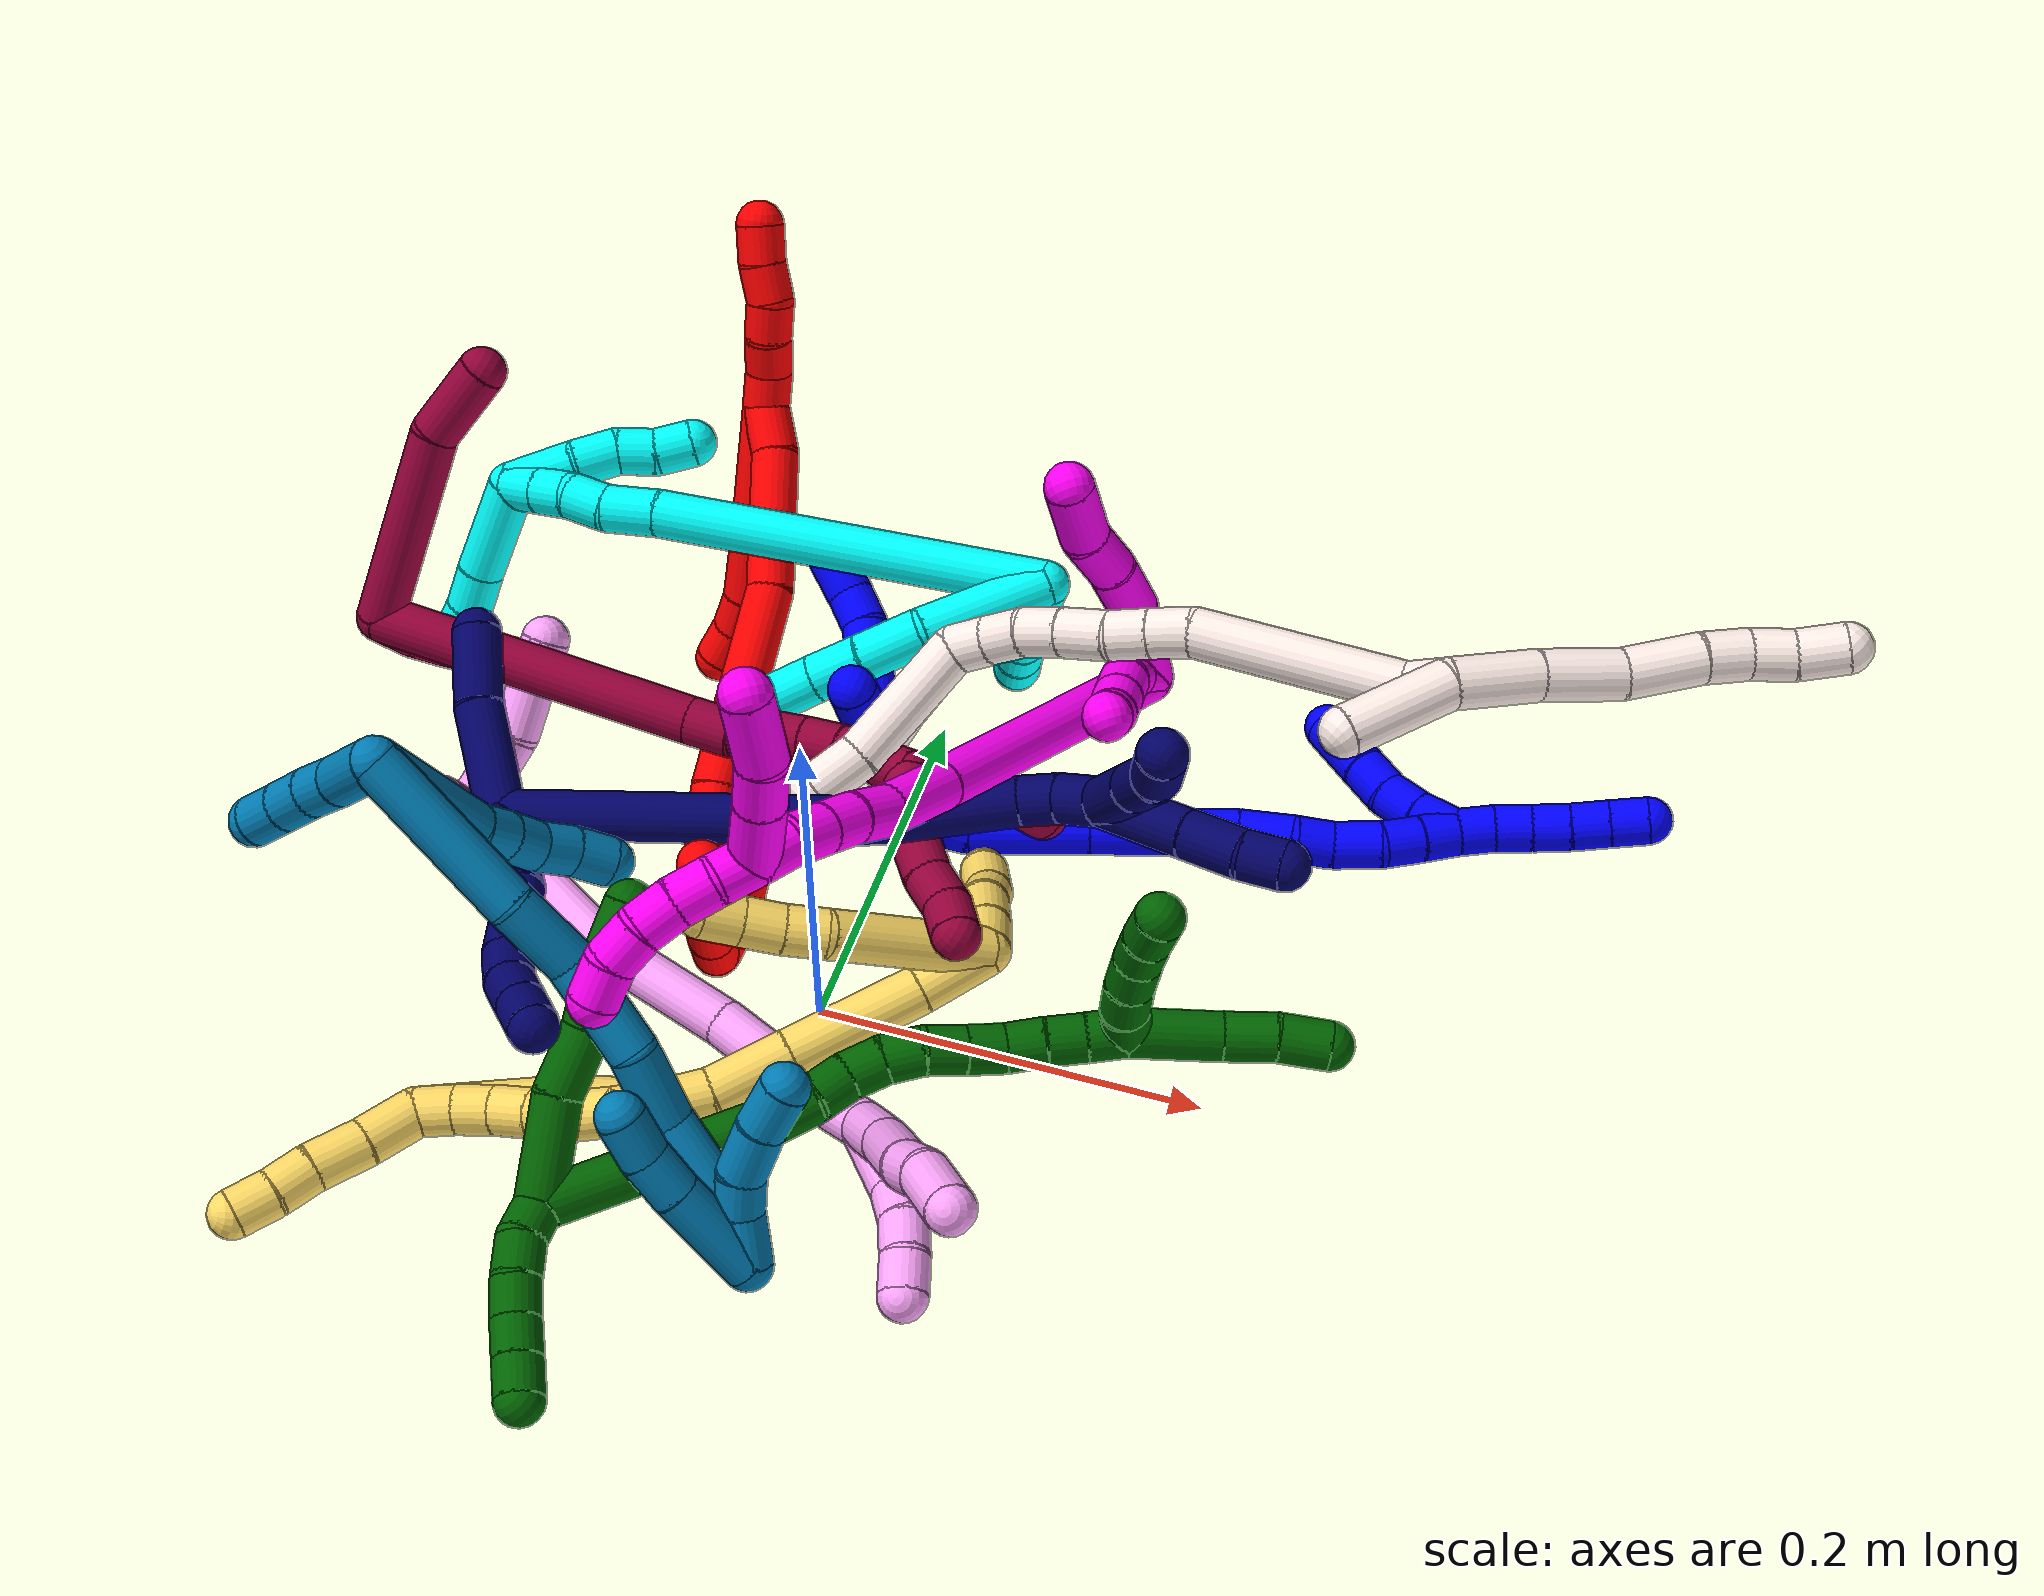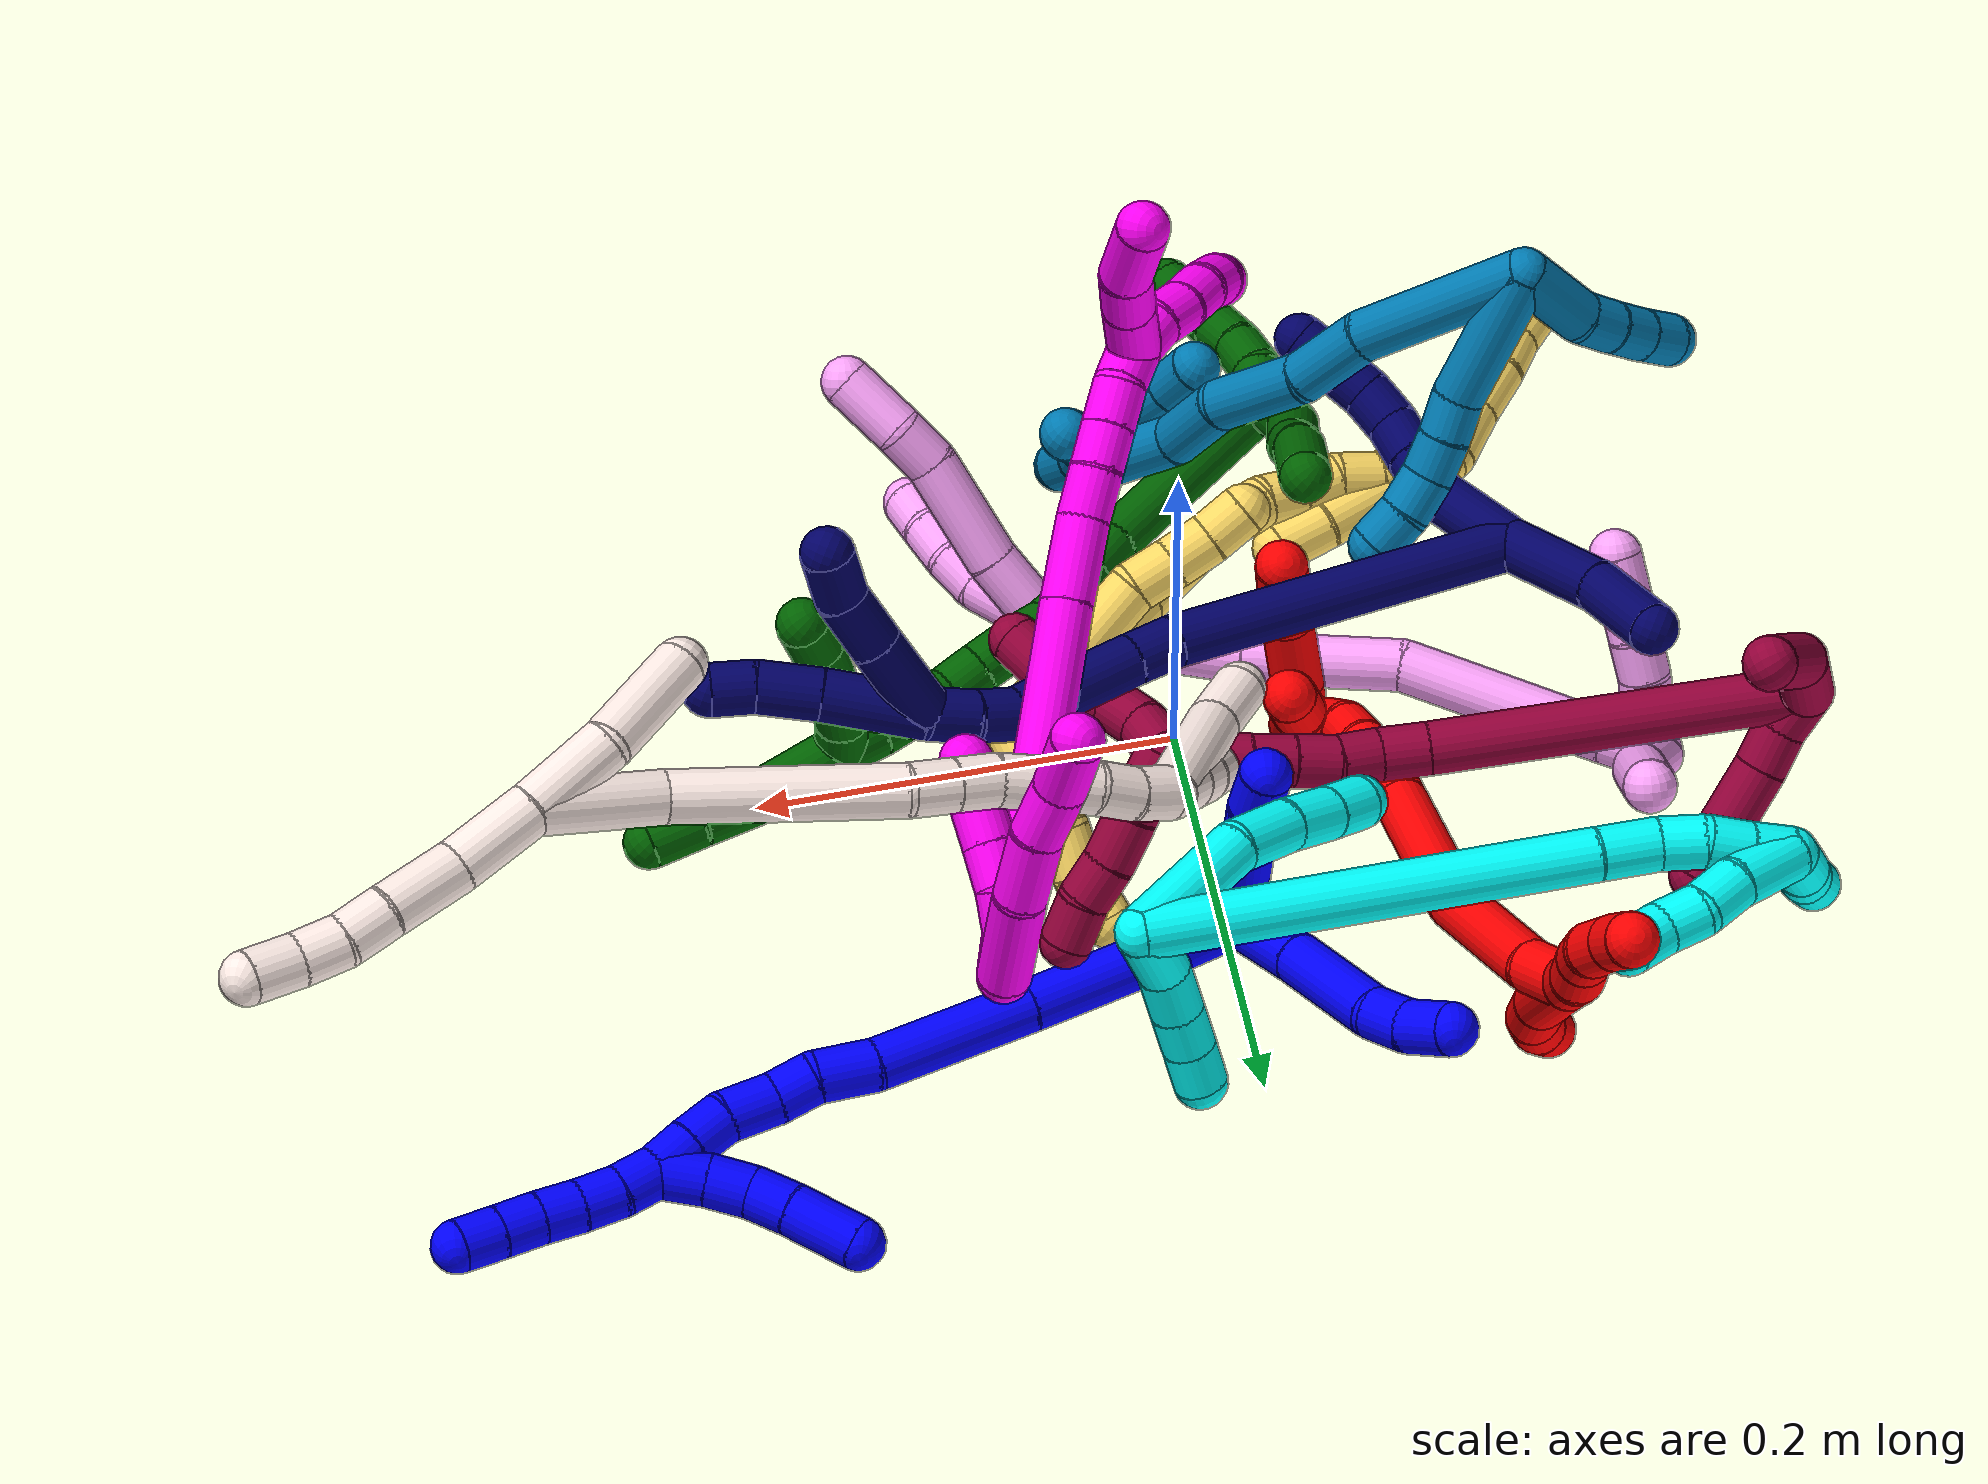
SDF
<sdf version="1.7">
 <world name="default">
  <plugin name="TubeGeneratorPlugin" filename="libtube_generator_plugin.so"/>
  <model name="photoneo_s_sensor">
   <static>1</static>
   <pose>0 0 2 1.57079 1.57079 3.14159</pose>
   <link name="link">
    <inertial><mass>0.1</mass></inertial>
    <sensor name="sensor" type="depth">
     <update_rate>30</update_rate>
     <camera>
      <horizontal_fov>1.22</horizontal_fov>
      <image><width>1920</width><height>1200</height><format>B8G8R8</format></image>
      <clip><near>0.1</near><far>4</far></clip>
      <depth_camera><output>points</output></depth_camera>
     </camera>
     <plugin name="camera_plugin" filename="libgazebo_ros_depth_camera.so">
      <baseline>0.2</baseline>
      <alwaysOn>1</alwaysOn>
      <updateRate>0.0</updateRate>
      <cameraName>camera_ir</cameraName>
      <imageTopicName>/camera/color/image_raw</imageTopicName>
      <cameraInfoTopicName>/camera/color/camera_info</cameraInfoTopicName>
      <depthImageTopicName>/camera/depth/image_raw</depthImageTopicName>
      <depthImageCameraInfoTopicName>/camera/depth/camera_info</depthImageCameraInfoTopicName>
      <pointCloudTopicName>/camera/depth/points</pointCloudTopicName>
      <frameName>fr_optical</frameName>
      <pointCloudCutoff>0.1</pointCloudCutoff>
      <pointCloudCutoffMax>2.0</pointCloudCutoffMax>
      <distortionK1>0</distortionK1>
      <distortionK2>0</distortionK2>
      <distortionK3>0</distortionK3>
      <distortionT1>0</distortionT1>
      <distortionT2>0</distortionT2>
      <CxPrime>0</CxPrime>
      <Cx>0</Cx>
      <Cy>0</Cy>
      <focalLength>0</focalLength>
      <hackBaseline>0</hackBaseline>
     </plugin>
    </sensor>
   </link>
  </model>
  <gravity>0 0 -9.8</gravity>
  <magnetic_field>6e-06 2.3e-05 -4.2e-05</magnetic_field>
  <atmosphere type="adiabatic"/>
  <physics name="default_physics" default="0" type="ode">
   <max_step_size>0.003</max_step_size>
   <real_time_factor>1</real_time_factor>
   <real_time_update_rate>1000</real_time_update_rate>
   <max_contacts>10000</max_contacts>
   <ode>
    <solver>
     <type>quick</type>
     <iters>100</iters>
     <sor>1.3</sor>
     <use_dynamic_moi_rescaling>0</use_dynamic_moi_rescaling>
    </solver>
    <constraints>
     <contact_max_correcting_vel>0</contact_max_correcting_vel>
     <contact_surface_layer>0.001</contact_surface_layer>
     <cfm>0</cfm>
     <erp>0.2</erp>
    </constraints>
   </ode>
  </physics>
  <scene><ambient>0.4 0.4 0.4 1</ambient><background>0.7 0.7 0.7 1</background><shadows>0</shadows></scene>
  <audio><device>default</device></audio>
  <spherical_coordinates>
   <surface_model>EARTH_WGS84</surface_model>
   <latitude_deg>0</latitude_deg>
   <longitude_deg>0</longitude_deg>
   <elevation>0</elevation>
   <heading_deg>0</heading_deg>
  </spherical_coordinates>
  <model name="bin">
   <static>1</static>
   <link name="bottom">
    <collision name="collision-bottom">
     <pose>0 0 -0.01 0 -0 0</pose>
     <geometry><box><size>0.8 0.6 0.02</size></box></geometry>
     <surface>
      <friction><ode><mu>100</mu><mu2>100</mu2></ode></friction>
      <contact><collide_bitmask>65535</collide_bitmask></contact>
     </surface>
    </collision>
   </link>
   <link name="west_wall">
    <collision name="collision-west_wall">
     <pose>-0.41 0 0.1 0 -0 0</pose>
     <geometry><box><size>0.02 0.6 0.2</size></box></geometry>
     <surface>
      <friction><ode><mu>100</mu><mu2>100</mu2></ode></friction>
      <contact><collide_bitmask>65535</collide_bitmask></contact>
     </surface>
    </collision>
   </link>
   <link name="east_wall">
    <collision name="collision-east_wall">
     <pose>0.41 0 0.1 0 -0 0</pose>
     <geometry><box><size>0.02 0.6 0.2</size></box></geometry>
     <surface>
      <friction><ode><mu>100</mu><mu2>100</mu2></ode></friction>
      <contact><collide_bitmask>65535</collide_bitmask></contact>
     </surface>
    </collision>
   </link>
   <link name="south_wall">
    <collision name="collision-south_wall">
     <pose>0 -0.31 0.1 0 -0 0</pose>
     <geometry><box><size>0.8 0.02 0.2</size></box></geometry>
     <surface>
      <friction><ode><mu>100</mu><mu2>100</mu2></ode></friction>
      <contact><collide_bitmask>65535</collide_bitmask></contact>
     </surface>
    </collision>
   </link>
   <link name="north_wall">
    <collision name="collision-north_wall">
     <pose>0 0.31 0.1 0 -0 0</pose>
     <geometry><box><size>0.8 0.02 0.2</size></box></geometry>
     <surface>
      <friction><ode><mu>100</mu><mu2>100</mu2></ode></friction>
      <contact><collide_bitmask>65535</collide_bitmask></contact>
     </surface>
    </collision>
   </link>
  </model>
  <model name="1">
   <static>0</static>
   <link name="1">
    <collision name="collision-cylinder-e_1_2_8">
     <pose>-0.012397 0.001278 0.020474 -0.062343 -0.54359 0.01738</pose>
     <geometry><cylinder><radius>0.0125</radius><length>0.047938</length></cylinder></geometry>
     <surface>
      <friction><ode><mu>1.16</mu><mu2>1.16</mu2><slip1>0</slip1><slip2>0</slip2></ode></friction>
      <contact><ode><kp>1e+06</kp><kd>1</kd><max_vel>0</max_vel><min_depth>0.001</min_depth></ode></contact>
     </surface>
    </collision>
    <visual name="visual-cylinder-e_1_2_8">
     <pose>-0.012397 0.001278 0.020474 -0.062343 -0.54359 0.01738</pose>
     <geometry><cylinder><radius>0.0125</radius><length>0.047938</length></cylinder></geometry>
     <material><ambient>0 0 1 1</ambient></material>
    </visual>
    <collision name="collision-cylinder-e_2_8_9">
     <pose>-0.038973 0.00535 0.065608 -0.112828 -0.519075 0.029988</pose>
     <geometry><cylinder><radius>0.0125</radius><length>0.057165</length></cylinder></geometry>
     <surface>
      <friction><ode><mu>1.16</mu><mu2>1.16</mu2><slip1>0</slip1><slip2>0</slip2></ode></friction>
      <contact><ode><kp>1e+06</kp><kd>1</kd><max_vel>0</max_vel><min_depth>0.001</min_depth></ode></contact>
     </surface>
    </collision>
    <visual name="visual-cylinder-e_2_8_9">
     <pose>-0.038973 0.00535 0.065608 -0.112828 -0.519075 0.029988</pose>
     <geometry><cylinder><radius>0.0125</radius><length>0.057165</length></cylinder></geometry>
     <material><ambient>0 0 1 1</ambient></material>
    </visual>
    <collision name="collision-cylinder-e_3_9_10">
     <pose>-0.0602 0.010105 0.097217 -0.274966 -0.77331 0.112544</pose>
     <geometry><cylinder><radius>0.0125</radius><length>0.020178</length></cylinder></geometry>
     <surface>
      <friction><ode><mu>1.16</mu><mu2>1.16</mu2><slip1>0</slip1><slip2>0</slip2></ode></friction>
      <contact><ode><kp>1e+06</kp><kd>1</kd><max_vel>0</max_vel><min_depth>0.001</min_depth></ode></contact>
     </surface>
    </collision>
    <visual name="visual-cylinder-e_3_9_10">
     <pose>-0.0602 0.010105 0.097217 -0.274966 -0.77331 0.112544</pose>
     <geometry><cylinder><radius>0.0125</radius><length>0.020178</length></cylinder></geometry>
     <material><ambient>0 0 1 1</ambient></material>
    </visual>
    <collision name="collision-cylinder-e_4_10_6">
     <pose>-0.077061 0.011361 0.111645 0.093862 -0.917464 -0.046381</pose>
     <geometry><cylinder><radius>0.0125</radius><length>0.024719</length></cylinder></geometry>
     <surface>
      <friction><ode><mu>1.16</mu><mu2>1.16</mu2><slip1>0</slip1><slip2>0</slip2></ode></friction>
      <contact><ode><kp>1e+06</kp><kd>1</kd><max_vel>0</max_vel><min_depth>0.001</min_depth></ode></contact>
     </surface>
    </collision>
    <visual name="visual-cylinder-e_4_10_6">
     <pose>-0.077061 0.011361 0.111645 0.093862 -0.917464 -0.046381</pose>
     <geometry><cylinder><radius>0.0125</radius><length>0.024719</length></cylinder></geometry>
     <material><ambient>0 0 1 1</ambient></material>
    </visual>
    <collision name="collision-cylinder-e_1_2_11">
     <pose>-0.007531 -0.015355 0.004047 1.3131 -0.442837 -0.343516</pose>
     <geometry><cylinder><radius>0.0125</radius><length>0.035149</length></cylinder></geometry>
     <surface>
      <friction><ode><mu>1.16</mu><mu2>1.16</mu2><slip1>0</slip1><slip2>0</slip2></ode></friction>
      <contact><ode><kp>1e+06</kp><kd>1</kd><max_vel>0</max_vel><min_depth>0.001</min_depth></ode></contact>
     </surface>
    </collision>
    <visual name="visual-cylinder-e_1_2_11">
     <pose>-0.007531 -0.015355 0.004047 1.3131 -0.442837 -0.343516</pose>
     <geometry><cylinder><radius>0.0125</radius><length>0.035149</length></cylinder></geometry>
     <material><ambient>0 0 1 1</ambient></material>
    </visual>
    <collision name="collision-cylinder-e_2_11_12">
     <pose>-0.020298 -0.040834 0.010445 1.34256 -0.46668 -0.373187</pose>
     <geometry><cylinder><radius>0.0125</radius><length>0.023276</length></cylinder></geometry>
     <surface>
      <friction><ode><mu>1.16</mu><mu2>1.16</mu2><slip1>0</slip1><slip2>0</slip2></ode></friction>
      <contact><ode><kp>1e+06</kp><kd>1</kd><max_vel>0</max_vel><min_depth>0.001</min_depth></ode></contact>
     </surface>
    </collision>
    <visual name="visual-cylinder-e_2_11_12">
     <pose>-0.020298 -0.040834 0.010445 1.34256 -0.46668 -0.373187</pose>
     <geometry><cylinder><radius>0.0125</radius><length>0.023276</length></cylinder></geometry>
     <material><ambient>0 0 1 1</ambient></material>
    </visual>
    <collision name="collision-cylinder-e_3_12_13">
     <pose>-0.030041 -0.059693 0.014689 1.3575 -0.467024 -0.379094</pose>
     <geometry><cylinder><radius>0.0125</radius><length>0.02002</length></cylinder></geometry>
     <surface>
      <friction><ode><mu>1.16</mu><mu2>1.16</mu2><slip1>0</slip1><slip2>0</slip2></ode></friction>
      <contact><ode><kp>1e+06</kp><kd>1</kd><max_vel>0</max_vel><min_depth>0.001</min_depth></ode></contact>
     </surface>
    </collision>
    <visual name="visual-cylinder-e_3_12_13">
     <pose>-0.030041 -0.059693 0.014689 1.3575 -0.467024 -0.379094</pose>
     <geometry><cylinder><radius>0.0125</radius><length>0.02002</length></cylinder></geometry>
     <material><ambient>0 0 1 1</ambient></material>
    </visual>
    <collision name="collision-cylinder-e_4_13_5">
     <pose>-0.040707 -0.077082 0.018406 1.36296 -0.608335 -0.498636</pose>
     <geometry><cylinder><radius>0.0125</radius><length>0.021555</length></cylinder></geometry>
     <surface>
      <friction><ode><mu>1.16</mu><mu2>1.16</mu2><slip1>0</slip1><slip2>0</slip2></ode></friction>
      <contact><ode><kp>1e+06</kp><kd>1</kd><max_vel>0</max_vel><min_depth>0.001</min_depth></ode></contact>
     </surface>
    </collision>
    <visual name="visual-cylinder-e_4_13_5">
     <pose>-0.040707 -0.077082 0.018406 1.36296 -0.608335 -0.498636</pose>
     <geometry><cylinder><radius>0.0125</radius><length>0.021555</length></cylinder></geometry>
     <material><ambient>0 0 1 1</ambient></material>
    </visual>
    <collision name="collision-cylinder-e_1_2_14">
     <pose>0.02105 -0.001931 0.004086 0.441452 1.3593 0.358741</pose>
     <geometry><cylinder><radius>0.0125</radius><length>0.043059</length></cylinder></geometry>
     <surface>
      <friction><ode><mu>1.16</mu><mu2>1.16</mu2><slip1>0</slip1><slip2>0</slip2></ode></friction>
      <contact><ode><kp>1e+06</kp><kd>1</kd><max_vel>0</max_vel><min_depth>0.001</min_depth></ode></contact>
     </surface>
    </collision>
    <visual name="visual-cylinder-e_1_2_14">
     <pose>0.02105 -0.001931 0.004086 0.441452 1.3593 0.358741</pose>
     <geometry><cylinder><radius>0.0125</radius><length>0.043059</length></cylinder></geometry>
     <material><ambient>0 0 1 1</ambient></material>
    </visual>
    <collision name="collision-cylinder-e_2_14_15">
     <pose>0.0704 -0.012306 0.019859 0.625667 1.09959 0.391369</pose>
     <geometry><cylinder><radius>0.0125</radius><length>0.063521</length></cylinder></geometry>
     <surface>
      <friction><ode><mu>1.16</mu><mu2>1.16</mu2><slip1>0</slip1><slip2>0</slip2></ode></friction>
      <contact><ode><kp>1e+06</kp><kd>1</kd><max_vel>0</max_vel><min_depth>0.001</min_depth></ode></contact>
     </surface>
    </collision>
    <visual name="visual-cylinder-e_2_14_15">
     <pose>0.0704 -0.012306 0.019859 0.625667 1.09959 0.391369</pose>
     <geometry><cylinder><radius>0.0125</radius><length>0.063521</length></cylinder></geometry>
     <material><ambient>0 0 1 1</ambient></material>
    </visual>
    <collision name="collision-cylinder-e_3_15_16">
     <pose>0.133543 -0.031401 0.045391 0.655762 1.1061 0.413953</pose>
     <geometry><cylinder><radius>0.0125</radius><length>0.077955</length></cylinder></geometry>
     <surface>
      <friction><ode><mu>1.16</mu><mu2>1.16</mu2><slip1>0</slip1><slip2>0</slip2></ode></friction>
      <contact><ode><kp>1e+06</kp><kd>1</kd><max_vel>0</max_vel><min_depth>0.001</min_depth></ode></contact>
     </surface>
    </collision>
    <visual name="visual-cylinder-e_3_15_16">
     <pose>0.133543 -0.031401 0.045391 0.655762 1.1061 0.413953</pose>
     <geometry><cylinder><radius>0.0125</radius><length>0.077955</length></cylinder></geometry>
     <material><ambient>0 0 1 1</ambient></material>
    </visual>
    <collision name="collision-cylinder-e_4_16_17">
     <pose>0.18134 -0.047327 0.062316 1.04222 1.13013 0.698105</pose>
     <geometry><cylinder><radius>0.0125</radius><length>0.028641</length></cylinder></geometry>
     <surface>
      <friction><ode><mu>1.16</mu><mu2>1.16</mu2><slip1>0</slip1><slip2>0</slip2></ode></friction>
      <contact><ode><kp>1e+06</kp><kd>1</kd><max_vel>0</max_vel><min_depth>0.001</min_depth></ode></contact>
     </surface>
    </collision>
    <visual name="visual-cylinder-e_4_16_17">
     <pose>0.18134 -0.047327 0.062316 1.04222 1.13013 0.698105</pose>
     <geometry><cylinder><radius>0.0125</radius><length>0.028641</length></cylinder></geometry>
     <material><ambient>0 0 1 1</ambient></material>
    </visual>
    <collision name="collision-cylinder-e_5_17_18">
     <pose>0.203972 -0.053236 0.068246 0.219221 1.27785 0.163147</pose>
     <geometry><cylinder><radius>0.0125</radius><length>0.02022</length></cylinder></geometry>
     <surface>
      <friction><ode><mu>1.16</mu><mu2>1.16</mu2><slip1>0</slip1><slip2>0</slip2></ode></friction>
      <contact><ode><kp>1e+06</kp><kd>1</kd><max_vel>0</max_vel><min_depth>0.001</min_depth></ode></contact>
     </surface>
    </collision>
    <visual name="visual-cylinder-e_5_17_18">
     <pose>0.203972 -0.053236 0.068246 0.219221 1.27785 0.163147</pose>
     <geometry><cylinder><radius>0.0125</radius><length>0.02022</length></cylinder></geometry>
     <material><ambient>0 0 1 1</ambient></material>
    </visual>
    <collision name="collision-cylinder-e_6_18_19">
     <pose>0.225082 -0.057687 0.075878 0.673459 1.07933 0.413369</pose>
     <geometry><cylinder><radius>0.0125</radius><length>0.025929</length></cylinder></geometry>
     <surface>
      <friction><ode><mu>1.16</mu><mu2>1.16</mu2><slip1>0</slip1><slip2>0</slip2></ode></friction>
      <contact><ode><kp>1e+06</kp><kd>1</kd><max_vel>0</max_vel><min_depth>0.001</min_depth></ode></contact>
     </surface>
    </collision>
    <visual name="visual-cylinder-e_6_18_19">
     <pose>0.225082 -0.057687 0.075878 0.673459 1.07933 0.413369</pose>
     <geometry><cylinder><radius>0.0125</radius><length>0.025929</length></cylinder></geometry>
     <material><ambient>0 0 1 1</ambient></material>
    </visual>
    <collision name="collision-cylinder-e_7_19_20">
     <pose>0.244984 -0.062393 0.086367 0.154704 0.972481 0.081889</pose>
     <geometry><cylinder><radius>0.0125</radius><length>0.020507</length></cylinder></geometry>
     <surface>
      <friction><ode><mu>1.16</mu><mu2>1.16</mu2><slip1>0</slip1><slip2>0</slip2></ode></friction>
      <contact><ode><kp>1e+06</kp><kd>1</kd><max_vel>0</max_vel><min_depth>0.001</min_depth></ode></contact>
     </surface>
    </collision>
    <visual name="visual-cylinder-e_7_19_20">
     <pose>0.244984 -0.062393 0.086367 0.154704 0.972481 0.081889</pose>
     <geometry><cylinder><radius>0.0125</radius><length>0.020507</length></cylinder></geometry>
     <material><ambient>0 0 1 1</ambient></material>
    </visual>
    <collision name="collision-cylinder-e_8_20_1">
     <pose>0.26159 -0.063792 0.098011 0.085568 0.938518 0.043406</pose>
     <geometry><cylinder><radius>0.0125</radius><length>0.020167</length></cylinder></geometry>
     <surface>
      <friction><ode><mu>1.16</mu><mu2>1.16</mu2><slip1>0</slip1><slip2>0</slip2></ode></friction>
      <contact><ode><kp>1e+06</kp><kd>1</kd><max_vel>0</max_vel><min_depth>0.001</min_depth></ode></contact>
     </surface>
    </collision>
    <visual name="visual-cylinder-e_8_20_1">
     <pose>0.26159 -0.063792 0.098011 0.085568 0.938518 0.043406</pose>
     <geometry><cylinder><radius>0.0125</radius><length>0.020167</length></cylinder></geometry>
     <material><ambient>0 0 1 1</ambient></material>
    </visual>
    <collision name="collision-cylinder-e_1_1_21">
     <pose>0.278194 -0.066524 0.108777 0.431457 1.01032 0.241202</pose>
     <geometry><cylinder><radius>0.0125</radius><length>0.02</length></cylinder></geometry>
     <surface>
      <friction><ode><mu>1.16</mu><mu2>1.16</mu2><slip1>0</slip1><slip2>0</slip2></ode></friction>
      <contact><ode><kp>1e+06</kp><kd>1</kd><max_vel>0</max_vel><min_depth>0.001</min_depth></ode></contact>
     </surface>
    </collision>
    <visual name="visual-cylinder-e_1_1_21">
     <pose>0.278194 -0.066524 0.108777 0.431457 1.01032 0.241202</pose>
     <geometry><cylinder><radius>0.0125</radius><length>0.02</length></cylinder></geometry>
     <material><ambient>0 0 1 1</ambient></material>
    </visual>
    <collision name="collision-cylinder-e_2_21_22">
     <pose>0.295468 -0.071794 0.11724 0.69755 1.07667 0.427671</pose>
     <geometry><cylinder><radius>0.0125</radius><length>0.02</length></cylinder></geometry>
     <surface>
      <friction><ode><mu>1.16</mu><mu2>1.16</mu2><slip1>0</slip1><slip2>0</slip2></ode></friction>
      <contact><ode><kp>1e+06</kp><kd>1</kd><max_vel>0</max_vel><min_depth>0.001</min_depth></ode></contact>
     </surface>
    </collision>
    <visual name="visual-cylinder-e_2_21_22">
     <pose>0.295468 -0.071794 0.11724 0.69755 1.07667 0.427671</pose>
     <geometry><cylinder><radius>0.0125</radius><length>0.02</length></cylinder></geometry>
     <material><ambient>0 0 1 1</ambient></material>
    </visual>
    <collision name="collision-cylinder-e_3_22_23">
     <pose>0.31287 -0.078512 0.124423 0.802631 1.03489 0.473976</pose>
     <geometry><cylinder><radius>0.0125</radius><length>0.02</length></cylinder></geometry>
     <surface>
      <friction><ode><mu>1.16</mu><mu2>1.16</mu2><slip1>0</slip1><slip2>0</slip2></ode></friction>
      <contact><ode><kp>1e+06</kp><kd>1</kd><max_vel>0</max_vel><min_depth>0.001</min_depth></ode></contact>
     </surface>
    </collision>
    <visual name="visual-cylinder-e_3_22_23">
     <pose>0.31287 -0.078512 0.124423 0.802631 1.03489 0.473976</pose>
     <geometry><cylinder><radius>0.0125</radius><length>0.02</length></cylinder></geometry>
     <material><ambient>0 0 1 1</ambient></material>
    </visual>
    <collision name="collision-cylinder-e_4_23_24">
     <pose>0.329839 -0.085693 0.132168 0.696184 0.991952 0.387755</pose>
     <geometry><cylinder><radius>0.0125</radius><length>0.02</length></cylinder></geometry>
     <surface>
      <friction><ode><mu>1.16</mu><mu2>1.16</mu2><slip1>0</slip1><slip2>0</slip2></ode></friction>
      <contact><ode><kp>1e+06</kp><kd>1</kd><max_vel>0</max_vel><min_depth>0.001</min_depth></ode></contact>
     </surface>
    </collision>
    <visual name="visual-cylinder-e_4_23_24">
     <pose>0.329839 -0.085693 0.132168 0.696184 0.991952 0.387755</pose>
     <geometry><cylinder><radius>0.0125</radius><length>0.02</length></cylinder></geometry>
     <material><ambient>0 0 1 1</ambient></material>
    </visual>
    <collision name="collision-cylinder-e_5_24_4">
     <pose>0.346596 -0.09282 0.140437 0.72665 0.994725 0.407095</pose>
     <geometry><cylinder><radius>0.0125</radius><length>0.02</length></cylinder></geometry>
     <surface>
      <friction><ode><mu>1.16</mu><mu2>1.16</mu2><slip1>0</slip1><slip2>0</slip2></ode></friction>
      <contact><ode><kp>1e+06</kp><kd>1</kd><max_vel>0</max_vel><min_depth>0.001</min_depth></ode></contact>
     </surface>
    </collision>
    <visual name="visual-cylinder-e_5_24_4">
     <pose>0.346596 -0.09282 0.140437 0.72665 0.994725 0.407095</pose>
     <geometry><cylinder><radius>0.0125</radius><length>0.02</length></cylinder></geometry>
     <material><ambient>0 0 1 1</ambient></material>
    </visual>
    <collision name="collision-cylinder-e_1_1_25">
     <pose>0.259776 -0.058543 0.106233 -1.193 -1.01385 0.721169</pose>
     <geometry><cylinder><radius>0.0125</radius><length>0.023438</length></cylinder></geometry>
     <surface>
      <friction><ode><mu>1.16</mu><mu2>1.16</mu2><slip1>0</slip1><slip2>0</slip2></ode></friction>
      <contact><ode><kp>1e+06</kp><kd>1</kd><max_vel>0</max_vel><min_depth>0.001</min_depth></ode></contact>
     </surface>
    </collision>
    <visual name="visual-cylinder-e_1_1_25">
     <pose>0.259776 -0.058543 0.106233 -1.193 -1.01385 0.721169</pose>
     <geometry><cylinder><radius>0.0125</radius><length>0.023438</length></cylinder></geometry>
     <material><ambient>0 0 1 1</ambient></material>
    </visual>
    <collision name="collision-cylinder-e_2_25_26">
     <pose>0.241256 -0.047584 0.111959 -0.986428 -0.941799 0.534225</pose>
     <geometry><cylinder><radius>0.0125</radius><length>0.021202</length></cylinder></geometry>
     <surface>
      <friction><ode><mu>1.16</mu><mu2>1.16</mu2><slip1>0</slip1><slip2>0</slip2></ode></friction>
      <contact><ode><kp>1e+06</kp><kd>1</kd><max_vel>0</max_vel><min_depth>0.001</min_depth></ode></contact>
     </surface>
    </collision>
    <visual name="visual-cylinder-e_2_25_26">
     <pose>0.241256 -0.047584 0.111959 -0.986428 -0.941799 0.534225</pose>
     <geometry><cylinder><radius>0.0125</radius><length>0.021202</length></cylinder></geometry>
     <material><ambient>0 0 1 1</ambient></material>
    </visual>
    <collision name="collision-cylinder-e_3_26_27">
     <pose>0.225071 -0.037917 0.120949 -0.677436 -0.818677 0.303335</pose>
     <geometry><cylinder><radius>0.0125</radius><length>0.020852</length></cylinder></geometry>
     <surface>
      <friction><ode><mu>1.16</mu><mu2>1.16</mu2><slip1>0</slip1><slip2>0</slip2></ode></friction>
      <contact><ode><kp>1e+06</kp><kd>1</kd><max_vel>0</max_vel><min_depth>0.001</min_depth></ode></contact>
     </surface>
    </collision>
    <visual name="visual-cylinder-e_3_26_27">
     <pose>0.225071 -0.037917 0.120949 -0.677436 -0.818677 0.303335</pose>
     <geometry><cylinder><radius>0.0125</radius><length>0.020852</length></cylinder></geometry>
     <material><ambient>0 0 1 1</ambient></material>
    </visual>
    <collision name="collision-cylinder-e_4_27_3">
     <pose>0.205614 -0.025149 0.135907 -0.723149 -0.756549 0.298371</pose>
     <geometry><cylinder><radius>0.0125</radius><length>0.034508</length></cylinder></geometry>
     <surface>
      <friction><ode><mu>1.16</mu><mu2>1.16</mu2><slip1>0</slip1><slip2>0</slip2></ode></friction>
      <contact><ode><kp>1e+06</kp><kd>1</kd><max_vel>0</max_vel><min_depth>0.001</min_depth></ode></contact>
     </surface>
    </collision>
    <visual name="visual-cylinder-e_4_27_3">
     <pose>0.205614 -0.025149 0.135907 -0.723149 -0.756549 0.298371</pose>
     <geometry><cylinder><radius>0.0125</radius><length>0.034508</length></cylinder></geometry>
     <material><ambient>0 0 1 1</ambient></material>
    </visual>
    <collision name="collision-sphere-3">
     <pose>0.19377 -0.016846 0.145314 0 -0 0</pose>
     <geometry><sphere><radius>0.0125</radius></sphere></geometry>
     <surface>
      <friction><ode><mu>1.16</mu><mu2>1.16</mu2><slip1>0</slip1><slip2>0</slip2></ode></friction>
      <contact><ode><kp>1e+06</kp><kd>1</kd><max_vel>0</max_vel><min_depth>0.001</min_depth></ode></contact>
     </surface>
    </collision>
    <visual name="visual-sphere-3">
     <pose>0.19377 -0.016846 0.145314 0 -0 0</pose>
     <geometry><sphere><radius>0.0125</radius></sphere></geometry>
     <material><ambient>0 0 1 1</ambient></material>
    </visual>
    <collision name="collision-sphere-27">
     <pose>0.217457 -0.033453 0.126499 0 -0 0</pose>
     <geometry><sphere><radius>0.0125</radius></sphere></geometry>
     <surface>
      <friction><ode><mu>1.16</mu><mu2>1.16</mu2><slip1>0</slip1><slip2>0</slip2></ode></friction>
      <contact><ode><kp>1e+06</kp><kd>1</kd><max_vel>0</max_vel><min_depth>0.001</min_depth></ode></contact>
     </surface>
    </collision>
    <visual name="visual-sphere-27">
     <pose>0.217457 -0.033453 0.126499 0 -0 0</pose>
     <geometry><sphere><radius>0.0125</radius></sphere></geometry>
     <material><ambient>0 0 1 1</ambient></material>
    </visual>
    <collision name="collision-sphere-26">
     <pose>0.232684 -0.042382 0.115399 0 -0 0</pose>
     <geometry><sphere><radius>0.0125</radius></sphere></geometry>
     <surface>
      <friction><ode><mu>1.16</mu><mu2>1.16</mu2><slip1>0</slip1><slip2>0</slip2></ode></friction>
      <contact><ode><kp>1e+06</kp><kd>1</kd><max_vel>0</max_vel><min_depth>0.001</min_depth></ode></contact>
     </surface>
    </collision>
    <visual name="visual-sphere-26">
     <pose>0.232684 -0.042382 0.115399 0 -0 0</pose>
     <geometry><sphere><radius>0.0125</radius></sphere></geometry>
     <material><ambient>0 0 1 1</ambient></material>
    </visual>
    <collision name="collision-sphere-25">
     <pose>0.249828 -0.052785 0.108518 0 -0 0</pose>
     <geometry><sphere><radius>0.0125</radius></sphere></geometry>
     <surface>
      <friction><ode><mu>1.16</mu><mu2>1.16</mu2><slip1>0</slip1><slip2>0</slip2></ode></friction>
      <contact><ode><kp>1e+06</kp><kd>1</kd><max_vel>0</max_vel><min_depth>0.001</min_depth></ode></contact>
     </surface>
    </collision>
    <visual name="visual-sphere-25">
     <pose>0.249828 -0.052785 0.108518 0 -0 0</pose>
     <geometry><sphere><radius>0.0125</radius></sphere></geometry>
     <material><ambient>0 0 1 1</ambient></material>
    </visual>
    <collision name="collision-sphere-4">
     <pose>0.354982 -0.096439 0.144508 0 -0 0</pose>
     <geometry><sphere><radius>0.0125</radius></sphere></geometry>
     <surface>
      <friction><ode><mu>1.16</mu><mu2>1.16</mu2><slip1>0</slip1><slip2>0</slip2></ode></friction>
      <contact><ode><kp>1e+06</kp><kd>1</kd><max_vel>0</max_vel><min_depth>0.001</min_depth></ode></contact>
     </surface>
    </collision>
    <visual name="visual-sphere-4">
     <pose>0.354982 -0.096439 0.144508 0 -0 0</pose>
     <geometry><sphere><radius>0.0125</radius></sphere></geometry>
     <material><ambient>0 0 1 1</ambient></material>
    </visual>
    <collision name="collision-sphere-24">
     <pose>0.33821 -0.089201 0.136366 0 -0 0</pose>
     <geometry><sphere><radius>0.0125</radius></sphere></geometry>
     <surface>
      <friction><ode><mu>1.16</mu><mu2>1.16</mu2><slip1>0</slip1><slip2>0</slip2></ode></friction>
      <contact><ode><kp>1e+06</kp><kd>1</kd><max_vel>0</max_vel><min_depth>0.001</min_depth></ode></contact>
     </surface>
    </collision>
    <visual name="visual-sphere-24">
     <pose>0.33821 -0.089201 0.136366 0 -0 0</pose>
     <geometry><sphere><radius>0.0125</radius></sphere></geometry>
     <material><ambient>0 0 1 1</ambient></material>
    </visual>
    <collision name="collision-sphere-23">
     <pose>0.321468 -0.082185 0.127971 0 -0 0</pose>
     <geometry><sphere><radius>0.0125</radius></sphere></geometry>
     <surface>
      <friction><ode><mu>1.16</mu><mu2>1.16</mu2><slip1>0</slip1><slip2>0</slip2></ode></friction>
      <contact><ode><kp>1e+06</kp><kd>1</kd><max_vel>0</max_vel><min_depth>0.001</min_depth></ode></contact>
     </surface>
    </collision>
    <visual name="visual-sphere-23">
     <pose>0.321468 -0.082185 0.127971 0 -0 0</pose>
     <geometry><sphere><radius>0.0125</radius></sphere></geometry>
     <material><ambient>0 0 1 1</ambient></material>
    </visual>
    <collision name="collision-sphere-22">
     <pose>0.304272 -0.07484 0.120875 0 -0 0</pose>
     <geometry><sphere><radius>0.0125</radius></sphere></geometry>
     <surface>
      <friction><ode><mu>1.16</mu><mu2>1.16</mu2><slip1>0</slip1><slip2>0</slip2></ode></friction>
      <contact><ode><kp>1e+06</kp><kd>1</kd><max_vel>0</max_vel><min_depth>0.001</min_depth></ode></contact>
     </surface>
    </collision>
    <visual name="visual-sphere-22">
     <pose>0.304272 -0.07484 0.120875 0 -0 0</pose>
     <geometry><sphere><radius>0.0125</radius></sphere></geometry>
     <material><ambient>0 0 1 1</ambient></material>
    </visual>
    <collision name="collision-sphere-21">
     <pose>0.286664 -0.068747 0.113605 0 -0 0</pose>
     <geometry><sphere><radius>0.0125</radius></sphere></geometry>
     <surface>
      <friction><ode><mu>1.16</mu><mu2>1.16</mu2><slip1>0</slip1><slip2>0</slip2></ode></friction>
      <contact><ode><kp>1e+06</kp><kd>1</kd><max_vel>0</max_vel><min_depth>0.001</min_depth></ode></contact>
     </surface>
    </collision>
    <visual name="visual-sphere-21">
     <pose>0.286664 -0.068747 0.113605 0 -0 0</pose>
     <geometry><sphere><radius>0.0125</radius></sphere></geometry>
     <material><ambient>0 0 1 1</ambient></material>
    </visual>
    <collision name="collision-sphere-1">
     <pose>0.269724 -0.064301 0.103948 0 -0 0</pose>
     <geometry><sphere><radius>0.0125</radius></sphere></geometry>
     <surface>
      <friction><ode><mu>1.16</mu><mu2>1.16</mu2><slip1>0</slip1><slip2>0</slip2></ode></friction>
      <contact><ode><kp>1e+06</kp><kd>1</kd><max_vel>0</max_vel><min_depth>0.001</min_depth></ode></contact>
     </surface>
    </collision>
    <visual name="visual-sphere-1">
     <pose>0.269724 -0.064301 0.103948 0 -0 0</pose>
     <geometry><sphere><radius>0.0125</radius></sphere></geometry>
     <material><ambient>0 0 1 1</ambient></material>
    </visual>
    <collision name="collision-sphere-11">
     <pose>-0.015061 -0.03071 0.008094 0 -0 0</pose>
     <geometry><sphere><radius>0.0125</radius></sphere></geometry>
     <surface>
      <friction><ode><mu>1.16</mu><mu2>1.16</mu2><slip1>0</slip1><slip2>0</slip2></ode></friction>
      <contact><ode><kp>1e+06</kp><kd>1</kd><max_vel>0</max_vel><min_depth>0.001</min_depth></ode></contact>
     </surface>
    </collision>
    <visual name="visual-sphere-11">
     <pose>-0.015061 -0.03071 0.008094 0 -0 0</pose>
     <geometry><sphere><radius>0.0125</radius></sphere></geometry>
     <material><ambient>0 0 1 1</ambient></material>
    </visual>
    <collision name="collision-sphere-6">
     <pose>-0.086875 0.010657 0.119124 0 -0 0</pose>
     <geometry><sphere><radius>0.0125</radius></sphere></geometry>
     <surface>
      <friction><ode><mu>1.16</mu><mu2>1.16</mu2><slip1>0</slip1><slip2>0</slip2></ode></friction>
      <contact><ode><kp>1e+06</kp><kd>1</kd><max_vel>0</max_vel><min_depth>0.001</min_depth></ode></contact>
     </surface>
    </collision>
    <visual name="visual-sphere-6">
     <pose>-0.086875 0.010657 0.119124 0 -0 0</pose>
     <geometry><sphere><radius>0.0125</radius></sphere></geometry>
     <material><ambient>0 0 1 1</ambient></material>
    </visual>
    <collision name="collision-sphere-10">
     <pose>-0.067247 0.012065 0.104165 0 -0 0</pose>
     <geometry><sphere><radius>0.0125</radius></sphere></geometry>
     <surface>
      <friction><ode><mu>1.16</mu><mu2>1.16</mu2><slip1>0</slip1><slip2>0</slip2></ode></friction>
      <contact><ode><kp>1e+06</kp><kd>1</kd><max_vel>0</max_vel><min_depth>0.001</min_depth></ode></contact>
     </surface>
    </collision>
    <visual name="visual-sphere-10">
     <pose>-0.067247 0.012065 0.104165 0 -0 0</pose>
     <geometry><sphere><radius>0.0125</radius></sphere></geometry>
     <material><ambient>0 0 1 1</ambient></material>
    </visual>
    <collision name="collision-sphere-9">
     <pose>-0.053152 0.008145 0.090268 0 -0 0</pose>
     <geometry><sphere><radius>0.0125</radius></sphere></geometry>
     <surface>
      <friction><ode><mu>1.16</mu><mu2>1.16</mu2><slip1>0</slip1><slip2>0</slip2></ode></friction>
      <contact><ode><kp>1e+06</kp><kd>1</kd><max_vel>0</max_vel><min_depth>0.001</min_depth></ode></contact>
     </surface>
    </collision>
    <visual name="visual-sphere-9">
     <pose>-0.053152 0.008145 0.090268 0 -0 0</pose>
     <geometry><sphere><radius>0.0125</radius></sphere></geometry>
     <material><ambient>0 0 1 1</ambient></material>
    </visual>
    <collision name="collision-sphere-2">
     <geometry><sphere><radius>0.0125</radius></sphere></geometry>
     <surface>
      <friction><ode><mu>1.16</mu><mu2>1.16</mu2><slip1>0</slip1><slip2>0</slip2></ode></friction>
      <contact><ode><kp>1e+06</kp><kd>1</kd><max_vel>0</max_vel><min_depth>0.001</min_depth></ode></contact>
     </surface>
    </collision>
    <visual name="visual-sphere-2">
     <geometry><sphere><radius>0.0125</radius></sphere></geometry>
     <material><ambient>0 0 1 1</ambient></material>
    </visual>
    <collision name="collision-sphere-19">
     <pose>0.236511 -0.061503 0.080661 0 -0 0</pose>
     <geometry><sphere><radius>0.0125</radius></sphere></geometry>
     <surface>
      <friction><ode><mu>1.16</mu><mu2>1.16</mu2><slip1>0</slip1><slip2>0</slip2></ode></friction>
      <contact><ode><kp>1e+06</kp><kd>1</kd><max_vel>0</max_vel><min_depth>0.001</min_depth></ode></contact>
     </surface>
    </collision>
    <visual name="visual-sphere-19">
     <pose>0.236511 -0.061503 0.080661 0 -0 0</pose>
     <geometry><sphere><radius>0.0125</radius></sphere></geometry>
     <material><ambient>0 0 1 1</ambient></material>
    </visual>
    <collision name="collision-sphere-8">
     <pose>-0.024794 0.002556 0.040948 0 -0 0</pose>
     <geometry><sphere><radius>0.0125</radius></sphere></geometry>
     <surface>
      <friction><ode><mu>1.16</mu><mu2>1.16</mu2><slip1>0</slip1><slip2>0</slip2></ode></friction>
      <contact><ode><kp>1e+06</kp><kd>1</kd><max_vel>0</max_vel><min_depth>0.001</min_depth></ode></contact>
     </surface>
    </collision>
    <visual name="visual-sphere-8">
     <pose>-0.024794 0.002556 0.040948 0 -0 0</pose>
     <geometry><sphere><radius>0.0125</radius></sphere></geometry>
     <material><ambient>0 0 1 1</ambient></material>
    </visual>
    <collision name="collision-sphere-12">
     <pose>-0.025534 -0.050958 0.012797 0 -0 0</pose>
     <geometry><sphere><radius>0.0125</radius></sphere></geometry>
     <surface>
      <friction><ode><mu>1.16</mu><mu2>1.16</mu2><slip1>0</slip1><slip2>0</slip2></ode></friction>
      <contact><ode><kp>1e+06</kp><kd>1</kd><max_vel>0</max_vel><min_depth>0.001</min_depth></ode></contact>
     </surface>
    </collision>
    <visual name="visual-sphere-12">
     <pose>-0.025534 -0.050958 0.012797 0 -0 0</pose>
     <geometry><sphere><radius>0.0125</radius></sphere></geometry>
     <material><ambient>0 0 1 1</ambient></material>
    </visual>
    <collision name="collision-sphere-13">
     <pose>-0.034547 -0.068429 0.016581 0 -0 0</pose>
     <geometry><sphere><radius>0.0125</radius></sphere></geometry>
     <surface>
      <friction><ode><mu>1.16</mu><mu2>1.16</mu2><slip1>0</slip1><slip2>0</slip2></ode></friction>
      <contact><ode><kp>1e+06</kp><kd>1</kd><max_vel>0</max_vel><min_depth>0.001</min_depth></ode></contact>
     </surface>
    </collision>
    <visual name="visual-sphere-13">
     <pose>-0.034547 -0.068429 0.016581 0 -0 0</pose>
     <geometry><sphere><radius>0.0125</radius></sphere></geometry>
     <material><ambient>0 0 1 1</ambient></material>
    </visual>
    <collision name="collision-sphere-5">
     <pose>-0.046866 -0.085736 0.020231 0 -0 0</pose>
     <geometry><sphere><radius>0.0125</radius></sphere></geometry>
     <surface>
      <friction><ode><mu>1.16</mu><mu2>1.16</mu2><slip1>0</slip1><slip2>0</slip2></ode></friction>
      <contact><ode><kp>1e+06</kp><kd>1</kd><max_vel>0</max_vel><min_depth>0.001</min_depth></ode></contact>
     </surface>
    </collision>
    <visual name="visual-sphere-5">
     <pose>-0.046866 -0.085736 0.020231 0 -0 0</pose>
     <geometry><sphere><radius>0.0125</radius></sphere></geometry>
     <material><ambient>0 0 1 1</ambient></material>
    </visual>
    <collision name="collision-sphere-14">
     <pose>0.0421 -0.003862 0.008173 0 -0 0</pose>
     <geometry><sphere><radius>0.0125</radius></sphere></geometry>
     <surface>
      <friction><ode><mu>1.16</mu><mu2>1.16</mu2><slip1>0</slip1><slip2>0</slip2></ode></friction>
      <contact><ode><kp>1e+06</kp><kd>1</kd><max_vel>0</max_vel><min_depth>0.001</min_depth></ode></contact>
     </surface>
    </collision>
    <visual name="visual-sphere-14">
     <pose>0.0421 -0.003862 0.008173 0 -0 0</pose>
     <geometry><sphere><radius>0.0125</radius></sphere></geometry>
     <material><ambient>0 0 1 1</ambient></material>
    </visual>
    <collision name="collision-sphere-15">
     <pose>0.098699 -0.02075 0.031546 0 -0 0</pose>
     <geometry><sphere><radius>0.0125</radius></sphere></geometry>
     <surface>
      <friction><ode><mu>1.16</mu><mu2>1.16</mu2><slip1>0</slip1><slip2>0</slip2></ode></friction>
      <contact><ode><kp>1e+06</kp><kd>1</kd><max_vel>0</max_vel><min_depth>0.001</min_depth></ode></contact>
     </surface>
    </collision>
    <visual name="visual-sphere-15">
     <pose>0.098699 -0.02075 0.031546 0 -0 0</pose>
     <geometry><sphere><radius>0.0125</radius></sphere></geometry>
     <material><ambient>0 0 1 1</ambient></material>
    </visual>
    <collision name="collision-sphere-16">
     <pose>0.168388 -0.042052 0.059236 0 -0 0</pose>
     <geometry><sphere><radius>0.0125</radius></sphere></geometry>
     <surface>
      <friction><ode><mu>1.16</mu><mu2>1.16</mu2><slip1>0</slip1><slip2>0</slip2></ode></friction>
      <contact><ode><kp>1e+06</kp><kd>1</kd><max_vel>0</max_vel><min_depth>0.001</min_depth></ode></contact>
     </surface>
    </collision>
    <visual name="visual-sphere-16">
     <pose>0.168388 -0.042052 0.059236 0 -0 0</pose>
     <geometry><sphere><radius>0.0125</radius></sphere></geometry>
     <material><ambient>0 0 1 1</ambient></material>
    </visual>
    <collision name="collision-sphere-17">
     <pose>0.194293 -0.052601 0.065397 0 -0 0</pose>
     <geometry><sphere><radius>0.0125</radius></sphere></geometry>
     <surface>
      <friction><ode><mu>1.16</mu><mu2>1.16</mu2><slip1>0</slip1><slip2>0</slip2></ode></friction>
      <contact><ode><kp>1e+06</kp><kd>1</kd><max_vel>0</max_vel><min_depth>0.001</min_depth></ode></contact>
     </surface>
    </collision>
    <visual name="visual-sphere-17">
     <pose>0.194293 -0.052601 0.065397 0 -0 0</pose>
     <geometry><sphere><radius>0.0125</radius></sphere></geometry>
     <material><ambient>0 0 1 1</ambient></material>
    </visual>
    <collision name="collision-sphere-18">
     <pose>0.213652 -0.053871 0.071096 0 -0 0</pose>
     <geometry><sphere><radius>0.0125</radius></sphere></geometry>
     <surface>
      <friction><ode><mu>1.16</mu><mu2>1.16</mu2><slip1>0</slip1><slip2>0</slip2></ode></friction>
      <contact><ode><kp>1e+06</kp><kd>1</kd><max_vel>0</max_vel><min_depth>0.001</min_depth></ode></contact>
     </surface>
    </collision>
    <visual name="visual-sphere-18">
     <pose>0.213652 -0.053871 0.071096 0 -0 0</pose>
     <geometry><sphere><radius>0.0125</radius></sphere></geometry>
     <material><ambient>0 0 1 1</ambient></material>
    </visual>
    <collision name="collision-sphere-20">
     <pose>0.253456 -0.063283 0.092073 0 -0 0</pose>
     <geometry><sphere><radius>0.0125</radius></sphere></geometry>
     <surface>
      <friction><ode><mu>1.16</mu><mu2>1.16</mu2><slip1>0</slip1><slip2>0</slip2></ode></friction>
      <contact><ode><kp>1e+06</kp><kd>1</kd><max_vel>0</max_vel><min_depth>0.001</min_depth></ode></contact>
     </surface>
    </collision>
    <visual name="visual-sphere-20">
     <pose>0.253456 -0.063283 0.092073 0 -0 0</pose>
     <geometry><sphere><radius>0.0125</radius></sphere></geometry>
     <material><ambient>0 0 1 1</ambient></material>
    </visual>
    <inertial>
     <pose>0.116448 -0.033663 0.065229 0 -0 0</pose>
     <mass>0.75</mass>
     <inertia><ixx>0.000105</ixx><ixy>0</ixy><ixz>0</ixz><iyy>0.000137</iyy><iyz>0</iyz><izz>-3e-06</izz></inertia>
    </inertial>
   </link>
   <pose>-0.003878 0.120474 0.020782 -1.23854 0.355494 0.005405</pose>
  </model>
  <model name="2">
   <static>0</static>
   <link name="2">
    <collision name="collision-cylinder-e_1_2_8">
     <pose>-0.000121 -0.000387 -0.035469 3.13068 -0.003402 -0.604463</pose>
     <geometry><cylinder><radius>0.0125</radius><length>0.070943</length></cylinder></geometry>
     <surface>
      <friction><ode><mu>1.16</mu><mu2>1.16</mu2><slip1>0</slip1><slip2>0</slip2></ode></friction>
      <contact><ode><kp>1e+06</kp><kd>1</kd><max_vel>0</max_vel><min_depth>0.001</min_depth></ode></contact>
     </surface>
    </collision>
    <visual name="visual-cylinder-e_1_2_8">
     <pose>-0.000121 -0.000387 -0.035469 3.13068 -0.003402 -0.604463</pose>
     <geometry><cylinder><radius>0.0125</radius><length>0.070943</length></cylinder></geometry>
     <material><ambient>1 0 0 1</ambient></material>
    </visual>
    <collision name="collision-cylinder-e_2_8_9">
     <pose>-0.001223 0.000554 -0.08918 -3.0689 -0.053599 1.27053</pose>
     <geometry><cylinder><radius>0.0125</radius><length>0.036632</length></cylinder></geometry>
     <surface>
      <friction><ode><mu>1.16</mu><mu2>1.16</mu2><slip1>0</slip1><slip2>0</slip2></ode></friction>
      <contact><ode><kp>1e+06</kp><kd>1</kd><max_vel>0</max_vel><min_depth>0.001</min_depth></ode></contact>
     </surface>
    </collision>
    <visual name="visual-cylinder-e_2_8_9">
     <pose>-0.001223 0.000554 -0.08918 -3.0689 -0.053599 1.27053</pose>
     <geometry><cylinder><radius>0.0125</radius><length>0.036632</length></cylinder></geometry>
     <material><ambient>1 0 0 1</ambient></material>
    </visual>
    <collision name="collision-cylinder-e_3_9_10">
     <pose>-0.004953 0.003453 -0.117774 -2.99108 -0.256724 2.08422</pose>
     <geometry><cylinder><radius>0.0125</radius><length>0.021652</length></cylinder></geometry>
     <surface>
      <friction><ode><mu>1.16</mu><mu2>1.16</mu2><slip1>0</slip1><slip2>0</slip2></ode></friction>
      <contact><ode><kp>1e+06</kp><kd>1</kd><max_vel>0</max_vel><min_depth>0.001</min_depth></ode></contact>
     </surface>
    </collision>
    <visual name="visual-cylinder-e_3_9_10">
     <pose>-0.004953 0.003453 -0.117774 -2.99108 -0.256724 2.08422</pose>
     <geometry><cylinder><radius>0.0125</radius><length>0.021652</length></cylinder></geometry>
     <material><ambient>1 0 0 1</ambient></material>
    </visual>
    <collision name="collision-cylinder-e_4_10_6">
     <pose>-0.011869 0.005328 -0.137636 -3.10952 -0.412831 2.9887</pose>
     <geometry><cylinder><radius>0.0125</radius><length>0.020773</length></cylinder></geometry>
     <surface>
      <friction><ode><mu>1.16</mu><mu2>1.16</mu2><slip1>0</slip1><slip2>0</slip2></ode></friction>
      <contact><ode><kp>1e+06</kp><kd>1</kd><max_vel>0</max_vel><min_depth>0.001</min_depth></ode></contact>
     </surface>
    </collision>
    <visual name="visual-cylinder-e_4_10_6">
     <pose>-0.011869 0.005328 -0.137636 -3.10952 -0.412831 2.9887</pose>
     <geometry><cylinder><radius>0.0125</radius><length>0.020773</length></cylinder></geometry>
     <material><ambient>1 0 0 1</ambient></material>
    </visual>
    <collision name="collision-cylinder-e_1_2_11">
     <pose>-9.2e-05 0.000289 0.009995 -0.028933 -0.009156 0.000132</pose>
     <geometry><cylinder><radius>0.0125</radius><length>0.02</length></cylinder></geometry>
     <surface>
      <friction><ode><mu>1.16</mu><mu2>1.16</mu2><slip1>0</slip1><slip2>0</slip2></ode></friction>
      <contact><ode><kp>1e+06</kp><kd>1</kd><max_vel>0</max_vel><min_depth>0.001</min_depth></ode></contact>
     </surface>
    </collision>
    <visual name="visual-cylinder-e_1_2_11">
     <pose>-9.2e-05 0.000289 0.009995 -0.028933 -0.009156 0.000132</pose>
     <geometry><cylinder><radius>0.0125</radius><length>0.02</length></cylinder></geometry>
     <material><ambient>1 0 0 1</ambient></material>
    </visual>
    <collision name="collision-cylinder-e_2_11_12">
     <pose>-0.000565 -0.001994 0.029647 0.260417 -0.038159 -0.004997</pose>
     <geometry><cylinder><radius>0.0125</radius><length>0.02</length></cylinder></geometry>
     <surface>
      <friction><ode><mu>1.16</mu><mu2>1.16</mu2><slip1>0</slip1><slip2>0</slip2></ode></friction>
      <contact><ode><kp>1e+06</kp><kd>1</kd><max_vel>0</max_vel><min_depth>0.001</min_depth></ode></contact>
     </surface>
    </collision>
    <visual name="visual-cylinder-e_2_11_12">
     <pose>-0.000565 -0.001994 0.029647 0.260417 -0.038159 -0.004997</pose>
     <geometry><cylinder><radius>0.0125</radius><length>0.02</length></cylinder></geometry>
     <material><ambient>1 0 0 1</ambient></material>
    </visual>
    <collision name="collision-cylinder-e_3_12_13">
     <pose>-0.000945 -0.005323 0.049274 0.075676 8.7e-05 3e-06</pose>
     <geometry><cylinder><radius>0.0125</radius><length>0.02</length></cylinder></geometry>
     <surface>
      <friction><ode><mu>1.16</mu><mu2>1.16</mu2><slip1>0</slip1><slip2>0</slip2></ode></friction>
      <contact><ode><kp>1e+06</kp><kd>1</kd><max_vel>0</max_vel><min_depth>0.001</min_depth></ode></contact>
     </surface>
    </collision>
    <visual name="visual-cylinder-e_3_12_13">
     <pose>-0.000945 -0.005323 0.049274 0.075676 8.7e-05 3e-06</pose>
     <geometry><cylinder><radius>0.0125</radius><length>0.02</length></cylinder></geometry>
     <material><ambient>1 0 0 1</ambient></material>
    </visual>
    <collision name="collision-cylinder-e_4_13_14">
     <pose>-0.004135 -0.005666 0.068714 -0.043645 -0.324708 0.00715</pose>
     <geometry><cylinder><radius>0.0125</radius><length>0.02</length></cylinder></geometry>
     <surface>
      <friction><ode><mu>1.16</mu><mu2>1.16</mu2><slip1>0</slip1><slip2>0</slip2></ode></friction>
      <contact><ode><kp>1e+06</kp><kd>1</kd><max_vel>0</max_vel><min_depth>0.001</min_depth></ode></contact>
     </surface>
    </collision>
    <visual name="visual-cylinder-e_4_13_14">
     <pose>-0.004135 -0.005666 0.068714 -0.043645 -0.324708 0.00715</pose>
     <geometry><cylinder><radius>0.0125</radius><length>0.02</length></cylinder></geometry>
     <material><ambient>1 0 0 1</ambient></material>
    </visual>
    <collision name="collision-cylinder-e_5_14_5">
     <pose>-0.00917 -0.004054 0.087937 -0.122206 -0.185556 0.011385</pose>
     <geometry><cylinder><radius>0.0125</radius><length>0.02</length></cylinder></geometry>
     <surface>
      <friction><ode><mu>1.16</mu><mu2>1.16</mu2><slip1>0</slip1><slip2>0</slip2></ode></friction>
      <contact><ode><kp>1e+06</kp><kd>1</kd><max_vel>0</max_vel><min_depth>0.001</min_depth></ode></contact>
     </surface>
    </collision>
    <visual name="visual-cylinder-e_5_14_5">
     <pose>-0.00917 -0.004054 0.087937 -0.122206 -0.185556 0.011385</pose>
     <geometry><cylinder><radius>0.0125</radius><length>0.02</length></cylinder></geometry>
     <material><ambient>1 0 0 1</ambient></material>
    </visual>
    <collision name="collision-cylinder-e_1_2_15">
     <pose>0.00533 -0.006394 -0.010118 2.578 0.418969 1.26685</pose>
     <geometry><cylinder><radius>0.0125</radius><length>0.026205</length></cylinder></geometry>
     <surface>
      <friction><ode><mu>1.16</mu><mu2>1.16</mu2><slip1>0</slip1><slip2>0</slip2></ode></friction>
      <contact><ode><kp>1e+06</kp><kd>1</kd><max_vel>0</max_vel><min_depth>0.001</min_depth></ode></contact>
     </surface>
    </collision>
    <visual name="visual-cylinder-e_1_2_15">
     <pose>0.00533 -0.006394 -0.010118 2.578 0.418969 1.26685</pose>
     <geometry><cylinder><radius>0.0125</radius><length>0.026205</length></cylinder></geometry>
     <material><ambient>1 0 0 1</ambient></material>
    </visual>
    <collision name="collision-cylinder-e_2_15_16">
     <pose>0.018125 -0.033444 -0.050683 2.54551 0.200152 0.631839</pose>
     <geometry><cylinder><radius>0.0125</radius><length>0.075084</length></cylinder></geometry>
     <surface>
      <friction><ode><mu>1.16</mu><mu2>1.16</mu2><slip1>0</slip1><slip2>0</slip2></ode></friction>
      <contact><ode><kp>1e+06</kp><kd>1</kd><max_vel>0</max_vel><min_depth>0.001</min_depth></ode></contact>
     </surface>
    </collision>
    <visual name="visual-cylinder-e_2_15_16">
     <pose>0.018125 -0.033444 -0.050683 2.54551 0.200152 0.631839</pose>
     <geometry><cylinder><radius>0.0125</radius><length>0.075084</length></cylinder></geometry>
     <material><ambient>1 0 0 1</ambient></material>
    </visual>
    <collision name="collision-cylinder-e_3_16_17">
     <pose>0.026006 -0.082674 -0.112423 2.40158 0.00986 0.02542</pose>
     <geometry><cylinder><radius>0.0125</radius><length>0.084756</length></cylinder></geometry>
     <surface>
      <friction><ode><mu>1.16</mu><mu2>1.16</mu2><slip1>0</slip1><slip2>0</slip2></ode></friction>
      <contact><ode><kp>1e+06</kp><kd>1</kd><max_vel>0</max_vel><min_depth>0.001</min_depth></ode></contact>
     </surface>
    </collision>
    <visual name="visual-cylinder-e_3_16_17">
     <pose>0.026006 -0.082674 -0.112423 2.40158 0.00986 0.02542</pose>
     <geometry><cylinder><radius>0.0125</radius><length>0.084756</length></cylinder></geometry>
     <material><ambient>1 0 0 1</ambient></material>
    </visual>
    <collision name="collision-cylinder-e_4_17_18">
     <pose>0.026554 -0.120813 -0.1541 2.3972 0.009195 0.023553</pose>
     <geometry><cylinder><radius>0.0125</radius><length>0.028238</length></cylinder></geometry>
     <surface>
      <friction><ode><mu>1.16</mu><mu2>1.16</mu2><slip1>0</slip1><slip2>0</slip2></ode></friction>
      <contact><ode><kp>1e+06</kp><kd>1</kd><max_vel>0</max_vel><min_depth>0.001</min_depth></ode></contact>
     </surface>
    </collision>
    <visual name="visual-cylinder-e_4_17_18">
     <pose>0.026554 -0.120813 -0.1541 2.3972 0.009195 0.023553</pose>
     <geometry><cylinder><radius>0.0125</radius><length>0.028238</length></cylinder></geometry>
     <material><ambient>1 0 0 1</ambient></material>
    </visual>
    <collision name="collision-cylinder-e_5_18_19">
     <pose>0.028753 -0.138279 -0.173148 2.40226 0.17469 0.444519</pose>
     <geometry><cylinder><radius>0.0125</radius><length>0.023811</length></cylinder></geometry>
     <surface>
      <friction><ode><mu>1.16</mu><mu2>1.16</mu2><slip1>0</slip1><slip2>0</slip2></ode></friction>
      <contact><ode><kp>1e+06</kp><kd>1</kd><max_vel>0</max_vel><min_depth>0.001</min_depth></ode></contact>
     </surface>
    </collision>
    <visual name="visual-cylinder-e_5_18_19">
     <pose>0.028753 -0.138279 -0.173148 2.40226 0.17469 0.444519</pose>
     <geometry><cylinder><radius>0.0125</radius><length>0.023811</length></cylinder></geometry>
     <material><ambient>1 0 0 1</ambient></material>
    </visual>
    <collision name="collision-cylinder-e_6_19_20">
     <pose>0.032007 -0.15203 -0.190284 2.5372 0.114499 0.363625</pose>
     <geometry><cylinder><radius>0.0125</radius><length>0.020732</length></cylinder></geometry>
     <surface>
      <friction><ode><mu>1.16</mu><mu2>1.16</mu2><slip1>0</slip1><slip2>0</slip2></ode></friction>
      <contact><ode><kp>1e+06</kp><kd>1</kd><max_vel>0</max_vel><min_depth>0.001</min_depth></ode></contact>
     </surface>
    </collision>
    <visual name="visual-cylinder-e_6_19_20">
     <pose>0.032007 -0.15203 -0.190284 2.5372 0.114499 0.363625</pose>
     <geometry><cylinder><radius>0.0125</radius><length>0.020732</length></cylinder></geometry>
     <material><ambient>1 0 0 1</ambient></material>
    </visual>
    <collision name="collision-cylinder-e_7_20_21">
     <pose>0.036014 -0.160926 -0.208339 2.83399 0.273819 1.45309</pose>
     <geometry><cylinder><radius>0.0125</radius><length>0.020882</length></cylinder></geometry>
     <surface>
      <friction><ode><mu>1.16</mu><mu2>1.16</mu2><slip1>0</slip1><slip2>0</slip2></ode></friction>
      <contact><ode><kp>1e+06</kp><kd>1</kd><max_vel>0</max_vel><min_depth>0.001</min_depth></ode></contact>
     </surface>
    </collision>
    <visual name="visual-cylinder-e_7_20_21">
     <pose>0.036014 -0.160926 -0.208339 2.83399 0.273819 1.45309</pose>
     <geometry><cylinder><radius>0.0125</radius><length>0.020882</length></cylinder></geometry>
     <material><ambient>1 0 0 1</ambient></material>
    </visual>
    <collision name="collision-cylinder-e_8_21_1">
     <pose>0.042391 -0.166254 -0.227144 2.89885 0.357751 1.95466</pose>
     <geometry><cylinder><radius>0.0125</radius><length>0.020292</length></cylinder></geometry>
     <surface>
      <friction><ode><mu>1.16</mu><mu2>1.16</mu2><slip1>0</slip1><slip2>0</slip2></ode></friction>
      <contact><ode><kp>1e+06</kp><kd>1</kd><max_vel>0</max_vel><min_depth>0.001</min_depth></ode></contact>
     </surface>
    </collision>
    <visual name="visual-cylinder-e_8_21_1">
     <pose>0.042391 -0.166254 -0.227144 2.89885 0.357751 1.95466</pose>
     <geometry><cylinder><radius>0.0125</radius><length>0.020292</length></cylinder></geometry>
     <material><ambient>1 0 0 1</ambient></material>
    </visual>
    <collision name="collision-cylinder-e_1_1_22">
     <pose>0.049655 -0.167315 -0.225392 -0.110962 0.324149 -0.018161</pose>
     <geometry><cylinder><radius>0.0125</radius><length>0.023304</length></cylinder></geometry>
     <surface>
      <friction><ode><mu>1.16</mu><mu2>1.16</mu2><slip1>0</slip1><slip2>0</slip2></ode></friction>
      <contact><ode><kp>1e+06</kp><kd>1</kd><max_vel>0</max_vel><min_depth>0.001</min_depth></ode></contact>
     </surface>
    </collision>
    <visual name="visual-cylinder-e_1_1_22">
     <pose>0.049655 -0.167315 -0.225392 -0.110962 0.324149 -0.018161</pose>
     <geometry><cylinder><radius>0.0125</radius><length>0.023304</length></cylinder></geometry>
     <material><ambient>1 0 0 1</ambient></material>
    </visual>
    <collision name="collision-cylinder-e_2_22_23">
     <pose>0.056671 -0.165251 -0.187544 -0.031277 0.122313 -0.001915</pose>
     <geometry><cylinder><radius>0.0125</radius><length>0.054172</length></cylinder></geometry>
     <surface>
      <friction><ode><mu>1.16</mu><mu2>1.16</mu2><slip1>0</slip1><slip2>0</slip2></ode></friction>
      <contact><ode><kp>1e+06</kp><kd>1</kd><max_vel>0</max_vel><min_depth>0.001</min_depth></ode></contact>
     </surface>
    </collision>
    <visual name="visual-cylinder-e_2_22_23">
     <pose>0.056671 -0.165251 -0.187544 -0.031277 0.122313 -0.001915</pose>
     <geometry><cylinder><radius>0.0125</radius><length>0.054172</length></cylinder></geometry>
     <material><ambient>1 0 0 1</ambient></material>
    </visual>
    <collision name="collision-cylinder-e_3_23_4">
     <pose>0.063217 -0.166857 -0.15017 0.228821 0.291961 0.033787</pose>
     <geometry><cylinder><radius>0.0125</radius><length>0.022524</length></cylinder></geometry>
     <surface>
      <friction><ode><mu>1.16</mu><mu2>1.16</mu2><slip1>0</slip1><slip2>0</slip2></ode></friction>
      <contact><ode><kp>1e+06</kp><kd>1</kd><max_vel>0</max_vel><min_depth>0.001</min_depth></ode></contact>
     </surface>
    </collision>
    <visual name="visual-cylinder-e_3_23_4">
     <pose>0.063217 -0.166857 -0.15017 0.228821 0.291961 0.033787</pose>
     <geometry><cylinder><radius>0.0125</radius><length>0.022524</length></cylinder></geometry>
     <material><ambient>1 0 0 1</ambient></material>
    </visual>
    <collision name="collision-cylinder-e_1_1_24">
     <pose>0.046452 -0.176712 -0.228093 0.779122 0.04367 0.017931</pose>
     <geometry><cylinder><radius>0.0125</radius><length>0.023287</length></cylinder></geometry>
     <surface>
      <friction><ode><mu>1.16</mu><mu2>1.16</mu2><slip1>0</slip1><slip2>0</slip2></ode></friction>
      <contact><ode><kp>1e+06</kp><kd>1</kd><max_vel>0</max_vel><min_depth>0.001</min_depth></ode></contact>
     </surface>
    </collision>
    <visual name="visual-cylinder-e_1_1_24">
     <pose>0.046452 -0.176712 -0.228093 0.779122 0.04367 0.017931</pose>
     <geometry><cylinder><radius>0.0125</radius><length>0.023287</length></cylinder></geometry>
     <material><ambient>1 0 0 1</ambient></material>
    </visual>
    <collision name="collision-cylinder-e_2_24_25">
     <pose>0.048362 -0.198035 -0.206177 0.767183 0.073877 0.029827</pose>
     <geometry><cylinder><radius>0.0125</radius><length>0.037995</length></cylinder></geometry>
     <surface>
      <friction><ode><mu>1.16</mu><mu2>1.16</mu2><slip1>0</slip1><slip2>0</slip2></ode></friction>
      <contact><ode><kp>1e+06</kp><kd>1</kd><max_vel>0</max_vel><min_depth>0.001</min_depth></ode></contact>
     </surface>
    </collision>
    <visual name="visual-cylinder-e_2_24_25">
     <pose>0.048362 -0.198035 -0.206177 0.767183 0.073877 0.029827</pose>
     <geometry><cylinder><radius>0.0125</radius><length>0.037995</length></cylinder></geometry>
     <material><ambient>1 0 0 1</ambient></material>
    </visual>
    <collision name="collision-cylinder-e_3_25_3">
     <pose>0.050957 -0.221643 -0.176291 0.571874 0.061647 0.018129</pose>
     <geometry><cylinder><radius>0.0125</radius><length>0.038718</length></cylinder></geometry>
     <surface>
      <friction><ode><mu>1.16</mu><mu2>1.16</mu2><slip1>0</slip1><slip2>0</slip2></ode></friction>
      <contact><ode><kp>1e+06</kp><kd>1</kd><max_vel>0</max_vel><min_depth>0.001</min_depth></ode></contact>
     </surface>
    </collision>
    <visual name="visual-cylinder-e_3_25_3">
     <pose>0.050957 -0.221643 -0.176291 0.571874 0.061647 0.018129</pose>
     <geometry><cylinder><radius>0.0125</radius><length>0.038718</length></cylinder></geometry>
     <material><ambient>1 0 0 1</ambient></material>
    </visual>
    <collision name="collision-sphere-3">
     <pose>0.05215 -0.232101 -0.160043 0 -0 0</pose>
     <geometry><sphere><radius>0.0125</radius></sphere></geometry>
     <surface>
      <friction><ode><mu>1.16</mu><mu2>1.16</mu2><slip1>0</slip1><slip2>0</slip2></ode></friction>
      <contact><ode><kp>1e+06</kp><kd>1</kd><max_vel>0</max_vel><min_depth>0.001</min_depth></ode></contact>
     </surface>
    </collision>
    <visual name="visual-sphere-3">
     <pose>0.05215 -0.232101 -0.160043 0 -0 0</pose>
     <geometry><sphere><radius>0.0125</radius></sphere></geometry>
     <material><ambient>1 0 0 1</ambient></material>
    </visual>
    <collision name="collision-sphere-25">
     <pose>0.049765 -0.211186 -0.192539 0 -0 0</pose>
     <geometry><sphere><radius>0.0125</radius></sphere></geometry>
     <surface>
      <friction><ode><mu>1.16</mu><mu2>1.16</mu2><slip1>0</slip1><slip2>0</slip2></ode></friction>
      <contact><ode><kp>1e+06</kp><kd>1</kd><max_vel>0</max_vel><min_depth>0.001</min_depth></ode></contact>
     </surface>
    </collision>
    <visual name="visual-sphere-25">
     <pose>0.049765 -0.211186 -0.192539 0 -0 0</pose>
     <geometry><sphere><radius>0.0125</radius></sphere></geometry>
     <material><ambient>1 0 0 1</ambient></material>
    </visual>
    <collision name="collision-sphere-24">
     <pose>0.04696 -0.184885 -0.219816 0 -0 0</pose>
     <geometry><sphere><radius>0.0125</radius></sphere></geometry>
     <surface>
      <friction><ode><mu>1.16</mu><mu2>1.16</mu2><slip1>0</slip1><slip2>0</slip2></ode></friction>
      <contact><ode><kp>1e+06</kp><kd>1</kd><max_vel>0</max_vel><min_depth>0.001</min_depth></ode></contact>
     </surface>
    </collision>
    <visual name="visual-sphere-24">
     <pose>0.04696 -0.184885 -0.219816 0 -0 0</pose>
     <geometry><sphere><radius>0.0125</radius></sphere></geometry>
     <material><ambient>1 0 0 1</ambient></material>
    </visual>
    <collision name="collision-sphere-4">
     <pose>0.066458 -0.169303 -0.139665 0 -0 0</pose>
     <geometry><sphere><radius>0.0125</radius></sphere></geometry>
     <surface>
      <friction><ode><mu>1.16</mu><mu2>1.16</mu2><slip1>0</slip1><slip2>0</slip2></ode></friction>
      <contact><ode><kp>1e+06</kp><kd>1</kd><max_vel>0</max_vel><min_depth>0.001</min_depth></ode></contact>
     </surface>
    </collision>
    <visual name="visual-sphere-4">
     <pose>0.066458 -0.169303 -0.139665 0 -0 0</pose>
     <geometry><sphere><radius>0.0125</radius></sphere></geometry>
     <material><ambient>1 0 0 1</ambient></material>
    </visual>
    <collision name="collision-sphere-23">
     <pose>0.059975 -0.164411 -0.160674 0 -0 0</pose>
     <geometry><sphere><radius>0.0125</radius></sphere></geometry>
     <surface>
      <friction><ode><mu>1.16</mu><mu2>1.16</mu2><slip1>0</slip1><slip2>0</slip2></ode></friction>
      <contact><ode><kp>1e+06</kp><kd>1</kd><max_vel>0</max_vel><min_depth>0.001</min_depth></ode></contact>
     </surface>
    </collision>
    <visual name="visual-sphere-23">
     <pose>0.059975 -0.164411 -0.160674 0 -0 0</pose>
     <geometry><sphere><radius>0.0125</radius></sphere></geometry>
     <material><ambient>1 0 0 1</ambient></material>
    </visual>
    <collision name="collision-sphere-22">
     <pose>0.053366 -0.166092 -0.214415 0 -0 0</pose>
     <geometry><sphere><radius>0.0125</radius></sphere></geometry>
     <surface>
      <friction><ode><mu>1.16</mu><mu2>1.16</mu2><slip1>0</slip1><slip2>0</slip2></ode></friction>
      <contact><ode><kp>1e+06</kp><kd>1</kd><max_vel>0</max_vel><min_depth>0.001</min_depth></ode></contact>
     </surface>
    </collision>
    <visual name="visual-sphere-22">
     <pose>0.053366 -0.166092 -0.214415 0 -0 0</pose>
     <geometry><sphere><radius>0.0125</radius></sphere></geometry>
     <material><ambient>1 0 0 1</ambient></material>
    </visual>
    <collision name="collision-sphere-1">
     <pose>0.045944 -0.168538 -0.236369 0 -0 0</pose>
     <geometry><sphere><radius>0.0125</radius></sphere></geometry>
     <surface>
      <friction><ode><mu>1.16</mu><mu2>1.16</mu2><slip1>0</slip1><slip2>0</slip2></ode></friction>
      <contact><ode><kp>1e+06</kp><kd>1</kd><max_vel>0</max_vel><min_depth>0.001</min_depth></ode></contact>
     </surface>
    </collision>
    <visual name="visual-sphere-1">
     <pose>0.045944 -0.168538 -0.236369 0 -0 0</pose>
     <geometry><sphere><radius>0.0125</radius></sphere></geometry>
     <material><ambient>1 0 0 1</ambient></material>
    </visual>
    <collision name="collision-sphere-21">
     <pose>0.038838 -0.163969 -0.217919 0 -0 0</pose>
     <geometry><sphere><radius>0.0125</radius></sphere></geometry>
     <surface>
      <friction><ode><mu>1.16</mu><mu2>1.16</mu2><slip1>0</slip1><slip2>0</slip2></ode></friction>
      <contact><ode><kp>1e+06</kp><kd>1</kd><max_vel>0</max_vel><min_depth>0.001</min_depth></ode></contact>
     </surface>
    </collision>
    <visual name="visual-sphere-21">
     <pose>0.038838 -0.163969 -0.217919 0 -0 0</pose>
     <geometry><sphere><radius>0.0125</radius></sphere></geometry>
     <material><ambient>1 0 0 1</ambient></material>
    </visual>
    <collision name="collision-sphere-11">
     <pose>-0.000183 0.000579 0.019991 0 -0 0</pose>
     <geometry><sphere><radius>0.0125</radius></sphere></geometry>
     <surface>
      <friction><ode><mu>1.16</mu><mu2>1.16</mu2><slip1>0</slip1><slip2>0</slip2></ode></friction>
      <contact><ode><kp>1e+06</kp><kd>1</kd><max_vel>0</max_vel><min_depth>0.001</min_depth></ode></contact>
     </surface>
    </collision>
    <visual name="visual-sphere-11">
     <pose>-0.000183 0.000579 0.019991 0 -0 0</pose>
     <geometry><sphere><radius>0.0125</radius></sphere></geometry>
     <material><ambient>1 0 0 1</ambient></material>
    </visual>
    <collision name="collision-sphere-6">
     <pose>-0.016036 0.005633 -0.147145 0 -0 0</pose>
     <geometry><sphere><radius>0.0125</radius></sphere></geometry>
     <surface>
      <friction><ode><mu>1.16</mu><mu2>1.16</mu2><slip1>0</slip1><slip2>0</slip2></ode></friction>
      <contact><ode><kp>1e+06</kp><kd>1</kd><max_vel>0</max_vel><min_depth>0.001</min_depth></ode></contact>
     </surface>
    </collision>
    <visual name="visual-sphere-6">
     <pose>-0.016036 0.005633 -0.147145 0 -0 0</pose>
     <geometry><sphere><radius>0.0125</radius></sphere></geometry>
     <material><ambient>1 0 0 1</ambient></material>
    </visual>
    <collision name="collision-sphere-10">
     <pose>-0.007702 0.005023 -0.128127 0 -0 0</pose>
     <geometry><sphere><radius>0.0125</radius></sphere></geometry>
     <surface>
      <friction><ode><mu>1.16</mu><mu2>1.16</mu2><slip1>0</slip1><slip2>0</slip2></ode></friction>
      <contact><ode><kp>1e+06</kp><kd>1</kd><max_vel>0</max_vel><min_depth>0.001</min_depth></ode></contact>
     </surface>
    </collision>
    <visual name="visual-sphere-10">
     <pose>-0.007702 0.005023 -0.128127 0 -0 0</pose>
     <geometry><sphere><radius>0.0125</radius></sphere></geometry>
     <material><ambient>1 0 0 1</ambient></material>
    </visual>
    <collision name="collision-sphere-9">
     <pose>-0.002204 0.001883 -0.107421 0 -0 0</pose>
     <geometry><sphere><radius>0.0125</radius></sphere></geometry>
     <surface>
      <friction><ode><mu>1.16</mu><mu2>1.16</mu2><slip1>0</slip1><slip2>0</slip2></ode></friction>
      <contact><ode><kp>1e+06</kp><kd>1</kd><max_vel>0</max_vel><min_depth>0.001</min_depth></ode></contact>
     </surface>
    </collision>
    <visual name="visual-sphere-9">
     <pose>-0.002204 0.001883 -0.107421 0 -0 0</pose>
     <geometry><sphere><radius>0.0125</radius></sphere></geometry>
     <material><ambient>1 0 0 1</ambient></material>
    </visual>
    <collision name="collision-sphere-2">
     <geometry><sphere><radius>0.0125</radius></sphere></geometry>
     <surface>
      <friction><ode><mu>1.16</mu><mu2>1.16</mu2><slip1>0</slip1><slip2>0</slip2></ode></friction>
      <contact><ode><kp>1e+06</kp><kd>1</kd><max_vel>0</max_vel><min_depth>0.001</min_depth></ode></contact>
     </surface>
    </collision>
    <visual name="visual-sphere-2">
     <geometry><sphere><radius>0.0125</radius></sphere></geometry>
     <material><ambient>1 0 0 1</ambient></material>
    </visual>
    <collision name="collision-sphere-19">
     <pose>0.030822 -0.146178 -0.181811 0 -0 0</pose>
     <geometry><sphere><radius>0.0125</radius></sphere></geometry>
     <surface>
      <friction><ode><mu>1.16</mu><mu2>1.16</mu2><slip1>0</slip1><slip2>0</slip2></ode></friction>
      <contact><ode><kp>1e+06</kp><kd>1</kd><max_vel>0</max_vel><min_depth>0.001</min_depth></ode></contact>
     </surface>
    </collision>
    <visual name="visual-sphere-19">
     <pose>0.030822 -0.146178 -0.181811 0 -0 0</pose>
     <geometry><sphere><radius>0.0125</radius></sphere></geometry>
     <material><ambient>1 0 0 1</ambient></material>
    </visual>
    <collision name="collision-sphere-8">
     <pose>-0.000241 -0.000774 -0.070938 0 -0 0</pose>
     <geometry><sphere><radius>0.0125</radius></sphere></geometry>
     <surface>
      <friction><ode><mu>1.16</mu><mu2>1.16</mu2><slip1>0</slip1><slip2>0</slip2></ode></friction>
      <contact><ode><kp>1e+06</kp><kd>1</kd><max_vel>0</max_vel><min_depth>0.001</min_depth></ode></contact>
     </surface>
    </collision>
    <visual name="visual-sphere-8">
     <pose>-0.000241 -0.000774 -0.070938 0 -0 0</pose>
     <geometry><sphere><radius>0.0125</radius></sphere></geometry>
     <material><ambient>1 0 0 1</ambient></material>
    </visual>
    <collision name="collision-sphere-12">
     <pose>-0.000946 -0.004567 0.039302 0 -0 0</pose>
     <geometry><sphere><radius>0.0125</radius></sphere></geometry>
     <surface>
      <friction><ode><mu>1.16</mu><mu2>1.16</mu2><slip1>0</slip1><slip2>0</slip2></ode></friction>
      <contact><ode><kp>1e+06</kp><kd>1</kd><max_vel>0</max_vel><min_depth>0.001</min_depth></ode></contact>
     </surface>
    </collision>
    <visual name="visual-sphere-12">
     <pose>-0.000946 -0.004567 0.039302 0 -0 0</pose>
     <geometry><sphere><radius>0.0125</radius></sphere></geometry>
     <material><ambient>1 0 0 1</ambient></material>
    </visual>
    <collision name="collision-sphere-13">
     <pose>-0.000944 -0.006079 0.059245 0 -0 0</pose>
     <geometry><sphere><radius>0.0125</radius></sphere></geometry>
     <surface>
      <friction><ode><mu>1.16</mu><mu2>1.16</mu2><slip1>0</slip1><slip2>0</slip2></ode></friction>
      <contact><ode><kp>1e+06</kp><kd>1</kd><max_vel>0</max_vel><min_depth>0.001</min_depth></ode></contact>
     </surface>
    </collision>
    <visual name="visual-sphere-13">
     <pose>-0.000944 -0.006079 0.059245 0 -0 0</pose>
     <geometry><sphere><radius>0.0125</radius></sphere></geometry>
     <material><ambient>1 0 0 1</ambient></material>
    </visual>
    <collision name="collision-sphere-14">
     <pose>-0.007325 -0.005252 0.078182 0 -0 0</pose>
     <geometry><sphere><radius>0.0125</radius></sphere></geometry>
     <surface>
      <friction><ode><mu>1.16</mu><mu2>1.16</mu2><slip1>0</slip1><slip2>0</slip2></ode></friction>
      <contact><ode><kp>1e+06</kp><kd>1</kd><max_vel>0</max_vel><min_depth>0.001</min_depth></ode></contact>
     </surface>
    </collision>
    <visual name="visual-sphere-14">
     <pose>-0.007325 -0.005252 0.078182 0 -0 0</pose>
     <geometry><sphere><radius>0.0125</radius></sphere></geometry>
     <material><ambient>1 0 0 1</ambient></material>
    </visual>
    <collision name="collision-sphere-5">
     <pose>-0.011015 -0.002856 0.097692 0 -0 0</pose>
     <geometry><sphere><radius>0.0125</radius></sphere></geometry>
     <surface>
      <friction><ode><mu>1.16</mu><mu2>1.16</mu2><slip1>0</slip1><slip2>0</slip2></ode></friction>
      <contact><ode><kp>1e+06</kp><kd>1</kd><max_vel>0</max_vel><min_depth>0.001</min_depth></ode></contact>
     </surface>
    </collision>
    <visual name="visual-sphere-5">
     <pose>-0.011015 -0.002856 0.097692 0 -0 0</pose>
     <geometry><sphere><radius>0.0125</radius></sphere></geometry>
     <material><ambient>1 0 0 1</ambient></material>
    </visual>
    <collision name="collision-sphere-15">
     <pose>0.010661 -0.012789 -0.020236 0 -0 0</pose>
     <geometry><sphere><radius>0.0125</radius></sphere></geometry>
     <surface>
      <friction><ode><mu>1.16</mu><mu2>1.16</mu2><slip1>0</slip1><slip2>0</slip2></ode></friction>
      <contact><ode><kp>1e+06</kp><kd>1</kd><max_vel>0</max_vel><min_depth>0.001</min_depth></ode></contact>
     </surface>
    </collision>
    <visual name="visual-sphere-15">
     <pose>0.010661 -0.012789 -0.020236 0 -0 0</pose>
     <geometry><sphere><radius>0.0125</radius></sphere></geometry>
     <material><ambient>1 0 0 1</ambient></material>
    </visual>
    <collision name="collision-sphere-16">
     <pose>0.025589 -0.0541 -0.08113 0 -0 0</pose>
     <geometry><sphere><radius>0.0125</radius></sphere></geometry>
     <surface>
      <friction><ode><mu>1.16</mu><mu2>1.16</mu2><slip1>0</slip1><slip2>0</slip2></ode></friction>
      <contact><ode><kp>1e+06</kp><kd>1</kd><max_vel>0</max_vel><min_depth>0.001</min_depth></ode></contact>
     </surface>
    </collision>
    <visual name="visual-sphere-16">
     <pose>0.025589 -0.0541 -0.08113 0 -0 0</pose>
     <geometry><sphere><radius>0.0125</radius></sphere></geometry>
     <material><ambient>1 0 0 1</ambient></material>
    </visual>
    <collision name="collision-sphere-17">
     <pose>0.026424 -0.111248 -0.143716 0 -0 0</pose>
     <geometry><sphere><radius>0.0125</radius></sphere></geometry>
     <surface>
      <friction><ode><mu>1.16</mu><mu2>1.16</mu2><slip1>0</slip1><slip2>0</slip2></ode></friction>
      <contact><ode><kp>1e+06</kp><kd>1</kd><max_vel>0</max_vel><min_depth>0.001</min_depth></ode></contact>
     </surface>
    </collision>
    <visual name="visual-sphere-17">
     <pose>0.026424 -0.111248 -0.143716 0 -0 0</pose>
     <geometry><sphere><radius>0.0125</radius></sphere></geometry>
     <material><ambient>1 0 0 1</ambient></material>
    </visual>
    <collision name="collision-sphere-18">
     <pose>0.026684 -0.130379 -0.164484 0 -0 0</pose>
     <geometry><sphere><radius>0.0125</radius></sphere></geometry>
     <surface>
      <friction><ode><mu>1.16</mu><mu2>1.16</mu2><slip1>0</slip1><slip2>0</slip2></ode></friction>
      <contact><ode><kp>1e+06</kp><kd>1</kd><max_vel>0</max_vel><min_depth>0.001</min_depth></ode></contact>
     </surface>
    </collision>
    <visual name="visual-sphere-18">
     <pose>0.026684 -0.130379 -0.164484 0 -0 0</pose>
     <geometry><sphere><radius>0.0125</radius></sphere></geometry>
     <material><ambient>1 0 0 1</ambient></material>
    </visual>
    <collision name="collision-sphere-20">
     <pose>0.033191 -0.157882 -0.198758 0 -0 0</pose>
     <geometry><sphere><radius>0.0125</radius></sphere></geometry>
     <surface>
      <friction><ode><mu>1.16</mu><mu2>1.16</mu2><slip1>0</slip1><slip2>0</slip2></ode></friction>
      <contact><ode><kp>1e+06</kp><kd>1</kd><max_vel>0</max_vel><min_depth>0.001</min_depth></ode></contact>
     </surface>
    </collision>
    <visual name="visual-sphere-20">
     <pose>0.033191 -0.157882 -0.198758 0 -0 0</pose>
     <geometry><sphere><radius>0.0125</radius></sphere></geometry>
     <material><ambient>1 0 0 1</ambient></material>
    </visual>
    <inertial>
     <pose>0.023004 -0.084351 -0.1067 0 -0 0</pose>
     <mass>0.75</mass>
     <inertia><ixx>0.00018</ixx><ixy>0</ixy><ixz>0</ixz><iyy>-5.5e-05</iyy><iyz>0</iyz><izz>5.1e-05</izz></inertia>
    </inertial>
   </link>
   <pose>-0.119073 0.266209 0.146188 -0.470628 0.000836 0.054651</pose>
  </model>
  <model name="3">
   <static>0</static>
   <link name="3">
    <collision name="collision-cylinder-e_1_2_8">
     <pose>-0.023208 -0.021121 -0.012949 2.12077 -0.752754 -1.22931</pose>
     <geometry><cylinder><radius>0.0125</radius><length>0.067893</length></cylinder></geometry>
     <surface>
      <friction><ode><mu>1.16</mu><mu2>1.16</mu2><slip1>0</slip1><slip2>0</slip2></ode></friction>
      <contact><ode><kp>1e+06</kp><kd>1</kd><max_vel>0</max_vel><min_depth>0.001</min_depth></ode></contact>
     </surface>
    </collision>
    <visual name="visual-cylinder-e_1_2_8">
     <pose>-0.023208 -0.021121 -0.012949 2.12077 -0.752754 -1.22931</pose>
     <geometry><cylinder><radius>0.0125</radius><length>0.067893</length></cylinder></geometry>
     <material><ambient>0.003922 1 0.996078 1</ambient></material>
    </visual>
    <collision name="collision-cylinder-e_2_8_9">
     <pose>-0.0573 -0.049567 -0.036257 2.52617 -0.709058 -1.72273</pose>
     <geometry><cylinder><radius>0.0125</radius><length>0.033434</length></cylinder></geometry>
     <surface>
      <friction><ode><mu>1.16</mu><mu2>1.16</mu2><slip1>0</slip1><slip2>0</slip2></ode></friction>
      <contact><ode><kp>1e+06</kp><kd>1</kd><max_vel>0</max_vel><min_depth>0.001</min_depth></ode></contact>
     </surface>
    </collision>
    <visual name="visual-cylinder-e_2_8_9">
     <pose>-0.0573 -0.049567 -0.036257 2.52617 -0.709058 -1.72273</pose>
     <geometry><cylinder><radius>0.0125</radius><length>0.033434</length></cylinder></geometry>
     <material><ambient>0.003922 1 0.996078 1</ambient></material>
    </visual>
    <collision name="collision-cylinder-e_3_9_10">
     <pose>-0.076806 -0.061815 -0.055532 2.637 -0.702524 -1.91551</pose>
     <geometry><cylinder><radius>0.0125</radius><length>0.026687</length></cylinder></geometry>
     <surface>
      <friction><ode><mu>1.16</mu><mu2>1.16</mu2><slip1>0</slip1><slip2>0</slip2></ode></friction>
      <contact><ode><kp>1e+06</kp><kd>1</kd><max_vel>0</max_vel><min_depth>0.001</min_depth></ode></contact>
     </surface>
    </collision>
    <visual name="visual-cylinder-e_3_9_10">
     <pose>-0.076806 -0.061815 -0.055532 2.637 -0.702524 -1.91551</pose>
     <geometry><cylinder><radius>0.0125</radius><length>0.026687</length></cylinder></geometry>
     <material><ambient>0.003922 1 0.996078 1</ambient></material>
    </visual>
    <collision name="collision-cylinder-e_4_10_6">
     <pose>-0.092343 -0.071197 -0.071737 2.59276 -0.680287 -1.79763</pose>
     <geometry><cylinder><radius>0.0125</radius><length>0.021986</length></cylinder></geometry>
     <surface>
      <friction><ode><mu>1.16</mu><mu2>1.16</mu2><slip1>0</slip1><slip2>0</slip2></ode></friction>
      <contact><ode><kp>1e+06</kp><kd>1</kd><max_vel>0</max_vel><min_depth>0.001</min_depth></ode></contact>
     </surface>
    </collision>
    <visual name="visual-cylinder-e_4_10_6">
     <pose>-0.092343 -0.071197 -0.071737 2.59276 -0.680287 -1.79763</pose>
     <geometry><cylinder><radius>0.0125</radius><length>0.021986</length></cylinder></geometry>
     <material><ambient>0.003922 1 0.996078 1</ambient></material>
    </visual>
    <collision name="collision-cylinder-e_1_2_11">
     <pose>-9.2e-05 0.00098 -0.016487 -3.0822 -0.005555 0.186445</pose>
     <geometry><cylinder><radius>0.0125</radius><length>0.033033</length></cylinder></geometry>
     <surface>
      <friction><ode><mu>1.16</mu><mu2>1.16</mu2><slip1>0</slip1><slip2>0</slip2></ode></friction>
      <contact><ode><kp>1e+06</kp><kd>1</kd><max_vel>0</max_vel><min_depth>0.001</min_depth></ode></contact>
     </surface>
    </collision>
    <visual name="visual-cylinder-e_1_2_11">
     <pose>-9.2e-05 0.00098 -0.016487 -3.0822 -0.005555 0.186445</pose>
     <geometry><cylinder><radius>0.0125</radius><length>0.033033</length></cylinder></geometry>
     <material><ambient>0.003922 1 0.996078 1</ambient></material>
    </visual>
    <collision name="collision-cylinder-e_2_11_12">
     <pose>0.000864 0.006404 -0.044439 -2.77182 0.084966 -0.446992</pose>
     <geometry><cylinder><radius>0.0125</radius><length>0.02468</length></cylinder></geometry>
     <surface>
      <friction><ode><mu>1.16</mu><mu2>1.16</mu2><slip1>0</slip1><slip2>0</slip2></ode></friction>
      <contact><ode><kp>1e+06</kp><kd>1</kd><max_vel>0</max_vel><min_depth>0.001</min_depth></ode></contact>
     </surface>
    </collision>
    <visual name="visual-cylinder-e_2_11_12">
     <pose>0.000864 0.006404 -0.044439 -2.77182 0.084966 -0.446992</pose>
     <geometry><cylinder><radius>0.0125</radius><length>0.02468</length></cylinder></geometry>
     <material><ambient>0.003922 1 0.996078 1</ambient></material>
    </visual>
    <collision name="collision-cylinder-e_3_12_13">
     <pose>0.002686 0.015139 -0.065639 -2.72645 0.072706 -0.342004</pose>
     <geometry><cylinder><radius>0.0125</radius><length>0.021336</length></cylinder></geometry>
     <surface>
      <friction><ode><mu>1.16</mu><mu2>1.16</mu2><slip1>0</slip1><slip2>0</slip2></ode></friction>
      <contact><ode><kp>1e+06</kp><kd>1</kd><max_vel>0</max_vel><min_depth>0.001</min_depth></ode></contact>
     </surface>
    </collision>
    <visual name="visual-cylinder-e_3_12_13">
     <pose>0.002686 0.015139 -0.065639 -2.72645 0.072706 -0.342004</pose>
     <geometry><cylinder><radius>0.0125</radius><length>0.021336</length></cylinder></geometry>
     <material><ambient>0.003922 1 0.996078 1</ambient></material>
    </visual>
    <collision name="collision-cylinder-e_4_13_5">
     <pose>0.004299 0.024138 -0.084696 -2.67392 0.080065 -0.333195</pose>
     <geometry><cylinder><radius>0.0125</radius><length>0.020951</length></cylinder></geometry>
     <surface>
      <friction><ode><mu>1.16</mu><mu2>1.16</mu2><slip1>0</slip1><slip2>0</slip2></ode></friction>
      <contact><ode><kp>1e+06</kp><kd>1</kd><max_vel>0</max_vel><min_depth>0.001</min_depth></ode></contact>
     </surface>
    </collision>
    <visual name="visual-cylinder-e_4_13_5">
     <pose>0.004299 0.024138 -0.084696 -2.67392 0.080065 -0.333195</pose>
     <geometry><cylinder><radius>0.0125</radius><length>0.020951</length></cylinder></geometry>
     <material><ambient>0.003922 1 0.996078 1</ambient></material>
    </visual>
    <collision name="collision-cylinder-e_1_2_14">
     <pose>-0.098905 -0.002401 -0.034105 3.07131 -1.23798 -3.04297</pose>
     <geometry><cylinder><radius>0.0125</radius><length>0.209295</length></cylinder></geometry>
     <surface>
      <friction><ode><mu>1.16</mu><mu2>1.16</mu2><slip1>0</slip1><slip2>0</slip2></ode></friction>
      <contact><ode><kp>1e+06</kp><kd>1</kd><max_vel>0</max_vel><min_depth>0.001</min_depth></ode></contact>
     </surface>
    </collision>
    <visual name="visual-cylinder-e_1_2_14">
     <pose>-0.098905 -0.002401 -0.034105 3.07131 -1.23798 -3.04297</pose>
     <geometry><cylinder><radius>0.0125</radius><length>0.209295</length></cylinder></geometry>
     <material><ambient>0.003922 1 0.996078 1</ambient></material>
    </visual>
    <collision name="collision-cylinder-e_2_14_15">
     <pose>-0.211049 -0.005727 -0.073905 2.98063 -1.1598 -2.89656</pose>
     <geometry><cylinder><radius>0.0125</radius><length>0.028883</length></cylinder></geometry>
     <surface>
      <friction><ode><mu>1.16</mu><mu2>1.16</mu2><slip1>0</slip1><slip2>0</slip2></ode></friction>
      <contact><ode><kp>1e+06</kp><kd>1</kd><max_vel>0</max_vel><min_depth>0.001</min_depth></ode></contact>
     </surface>
    </collision>
    <visual name="visual-cylinder-e_2_14_15">
     <pose>-0.211049 -0.005727 -0.073905 2.98063 -1.1598 -2.89656</pose>
     <geometry><cylinder><radius>0.0125</radius><length>0.028883</length></cylinder></geometry>
     <material><ambient>0.003922 1 0.996078 1</ambient></material>
    </visual>
    <collision name="collision-cylinder-e_3_15_16">
     <pose>-0.23447 -0.005114 -0.082609 -2.66911 -1.2504 2.49774</pose>
     <geometry><cylinder><radius>0.0125</radius><length>0.021457</length></cylinder></geometry>
     <surface>
      <friction><ode><mu>1.16</mu><mu2>1.16</mu2><slip1>0</slip1><slip2>0</slip2></ode></friction>
      <contact><ode><kp>1e+06</kp><kd>1</kd><max_vel>0</max_vel><min_depth>0.001</min_depth></ode></contact>
     </surface>
    </collision>
    <visual name="visual-cylinder-e_3_15_16">
     <pose>-0.23447 -0.005114 -0.082609 -2.66911 -1.2504 2.49774</pose>
     <geometry><cylinder><radius>0.0125</radius><length>0.021457</length></cylinder></geometry>
     <material><ambient>0.003922 1 0.996078 1</ambient></material>
    </visual>
    <collision name="collision-cylinder-e_4_16_17">
     <pose>-0.252982 -0.001492 -0.09095 -2.76909 -0.9686 2.45371</pose>
     <geometry><cylinder><radius>0.0125</radius><length>0.020215</length></cylinder></geometry>
     <surface>
      <friction><ode><mu>1.16</mu><mu2>1.16</mu2><slip1>0</slip1><slip2>0</slip2></ode></friction>
      <contact><ode><kp>1e+06</kp><kd>1</kd><max_vel>0</max_vel><min_depth>0.001</min_depth></ode></contact>
     </surface>
    </collision>
    <visual name="visual-cylinder-e_4_16_17">
     <pose>-0.252982 -0.001492 -0.09095 -2.76909 -0.9686 2.45371</pose>
     <geometry><cylinder><radius>0.0125</radius><length>0.020215</length></cylinder></geometry>
     <material><ambient>0.003922 1 0.996078 1</ambient></material>
    </visual>
    <collision name="collision-cylinder-e_5_17_1">
     <pose>-0.269824 0.00243 -0.101349 -2.79337 -1.00641 2.52305</pose>
     <geometry><cylinder><radius>0.0125</radius><length>0.02015</length></cylinder></geometry>
     <surface>
      <friction><ode><mu>1.16</mu><mu2>1.16</mu2><slip1>0</slip1><slip2>0</slip2></ode></friction>
      <contact><ode><kp>1e+06</kp><kd>1</kd><max_vel>0</max_vel><min_depth>0.001</min_depth></ode></contact>
     </surface>
    </collision>
    <visual name="visual-cylinder-e_5_17_1">
     <pose>-0.269824 0.00243 -0.101349 -2.79337 -1.00641 2.52305</pose>
     <geometry><cylinder><radius>0.0125</radius><length>0.02015</length></cylinder></geometry>
     <material><ambient>0.003922 1 0.996078 1</ambient></material>
    </visual>
    <collision name="collision-cylinder-e_1_1_18">
     <pose>-0.265311 0.012332 -0.096844 -0.700101 0.805432 -0.30858</pose>
     <geometry><cylinder><radius>0.0125</radius><length>0.036125</length></cylinder></geometry>
     <surface>
      <friction><ode><mu>1.16</mu><mu2>1.16</mu2><slip1>0</slip1><slip2>0</slip2></ode></friction>
      <contact><ode><kp>1e+06</kp><kd>1</kd><max_vel>0</max_vel><min_depth>0.001</min_depth></ode></contact>
     </surface>
    </collision>
    <visual name="visual-cylinder-e_1_1_18">
     <pose>-0.265311 0.012332 -0.096844 -0.700101 0.805432 -0.30858</pose>
     <geometry><cylinder><radius>0.0125</radius><length>0.036125</length></cylinder></geometry>
     <material><ambient>0.003922 1 0.996078 1</ambient></material>
    </visual>
    <collision name="collision-cylinder-e_2_18_19">
     <pose>-0.243526 0.026894 -0.082679 -0.955422 0.833237 -0.450419</pose>
     <geometry><cylinder><radius>0.0125</radius><length>0.023672</length></cylinder></geometry>
     <surface>
      <friction><ode><mu>1.16</mu><mu2>1.16</mu2><slip1>0</slip1><slip2>0</slip2></ode></friction>
      <contact><ode><kp>1e+06</kp><kd>1</kd><max_vel>0</max_vel><min_depth>0.001</min_depth></ode></contact>
     </surface>
    </collision>
    <visual name="visual-cylinder-e_2_18_19">
     <pose>-0.243526 0.026894 -0.082679 -0.955422 0.833237 -0.450419</pose>
     <geometry><cylinder><radius>0.0125</radius><length>0.023672</length></cylinder></geometry>
     <material><ambient>0.003922 1 0.996078 1</ambient></material>
    </visual>
    <collision name="collision-cylinder-e_3_19_20">
     <pose>-0.225502 0.036246 -0.075272 -0.792491 1.16263 -0.536535</pose>
     <geometry><cylinder><radius>0.0125</radius><length>0.020186</length></cylinder></geometry>
     <surface>
      <friction><ode><mu>1.16</mu><mu2>1.16</mu2><slip1>0</slip1><slip2>0</slip2></ode></friction>
      <contact><ode><kp>1e+06</kp><kd>1</kd><max_vel>0</max_vel><min_depth>0.001</min_depth></ode></contact>
     </surface>
    </collision>
    <visual name="visual-cylinder-e_3_19_20">
     <pose>-0.225502 0.036246 -0.075272 -0.792491 1.16263 -0.536535</pose>
     <geometry><cylinder><radius>0.0125</radius><length>0.020186</length></cylinder></geometry>
     <material><ambient>0.003922 1 0.996078 1</ambient></material>
    </visual>
    <collision name="collision-cylinder-e_4_20_4">
     <pose>-0.208485 0.043758 -0.068174 -0.827231 0.886101 -0.41069</pose>
     <geometry><cylinder><radius>0.0125</radius><length>0.020017</length></cylinder></geometry>
     <surface>
      <friction><ode><mu>1.16</mu><mu2>1.16</mu2><slip1>0</slip1><slip2>0</slip2></ode></friction>
      <contact><ode><kp>1e+06</kp><kd>1</kd><max_vel>0</max_vel><min_depth>0.001</min_depth></ode></contact>
     </surface>
    </collision>
    <visual name="visual-cylinder-e_4_20_4">
     <pose>-0.208485 0.043758 -0.068174 -0.827231 0.886101 -0.41069</pose>
     <geometry><cylinder><radius>0.0125</radius><length>0.020017</length></cylinder></geometry>
     <material><ambient>0.003922 1 0.996078 1</ambient></material>
    </visual>
    <collision name="collision-cylinder-e_1_1_21">
     <pose>-0.278016 -0.005116 -0.131635 2.78533 0.011924 0.066206</pose>
     <geometry><cylinder><radius>0.0125</radius><length>0.053824</length></cylinder></geometry>
     <surface>
      <friction><ode><mu>1.16</mu><mu2>1.16</mu2><slip1>0</slip1><slip2>0</slip2></ode></friction>
      <contact><ode><kp>1e+06</kp><kd>1</kd><max_vel>0</max_vel><min_depth>0.001</min_depth></ode></contact>
     </surface>
    </collision>
    <visual name="visual-cylinder-e_1_1_21">
     <pose>-0.278016 -0.005116 -0.131635 2.78533 0.011924 0.066206</pose>
     <geometry><cylinder><radius>0.0125</radius><length>0.053824</length></cylinder></geometry>
     <material><ambient>0.003922 1 0.996078 1</ambient></material>
    </visual>
    <collision name="collision-cylinder-e_2_21_22">
     <pose>-0.27705 -0.018548 -0.167784 2.78696 0.055291 0.306213</pose>
     <geometry><cylinder><radius>0.0125</radius><length>0.023343</length></cylinder></geometry>
     <surface>
      <friction><ode><mu>1.16</mu><mu2>1.16</mu2><slip1>0</slip1><slip2>0</slip2></ode></friction>
      <contact><ode><kp>1e+06</kp><kd>1</kd><max_vel>0</max_vel><min_depth>0.001</min_depth></ode></contact>
     </surface>
    </collision>
    <visual name="visual-cylinder-e_2_21_22">
     <pose>-0.27705 -0.018548 -0.167784 2.78696 0.055291 0.306213</pose>
     <geometry><cylinder><radius>0.0125</radius><length>0.023343</length></cylinder></geometry>
     <material><ambient>0.003922 1 0.996078 1</ambient></material>
    </visual>
    <collision name="collision-cylinder-e_3_22_3">
     <pose>-0.277296 -0.026109 -0.189538 2.82768 -0.078143 -0.484328</pose>
     <geometry><cylinder><radius>0.0125</radius><length>0.022833</length></cylinder></geometry>
     <surface>
      <friction><ode><mu>1.16</mu><mu2>1.16</mu2><slip1>0</slip1><slip2>0</slip2></ode></friction>
      <contact><ode><kp>1e+06</kp><kd>1</kd><max_vel>0</max_vel><min_depth>0.001</min_depth></ode></contact>
     </surface>
    </collision>
    <visual name="visual-cylinder-e_3_22_3">
     <pose>-0.277296 -0.026109 -0.189538 2.82768 -0.078143 -0.484328</pose>
     <geometry><cylinder><radius>0.0125</radius><length>0.022833</length></cylinder></geometry>
     <material><ambient>0.003922 1 0.996078 1</ambient></material>
    </visual>
    <collision name="collision-sphere-3">
     <pose>-0.278187 -0.029624 -0.200363 0 -0 0</pose>
     <geometry><sphere><radius>0.0125</radius></sphere></geometry>
     <surface>
      <friction><ode><mu>1.16</mu><mu2>1.16</mu2><slip1>0</slip1><slip2>0</slip2></ode></friction>
      <contact><ode><kp>1e+06</kp><kd>1</kd><max_vel>0</max_vel><min_depth>0.001</min_depth></ode></contact>
     </surface>
    </collision>
    <visual name="visual-sphere-3">
     <pose>-0.278187 -0.029624 -0.200363 0 -0 0</pose>
     <geometry><sphere><radius>0.0125</radius></sphere></geometry>
     <material><ambient>0.003922 1 0.996078 1</ambient></material>
    </visual>
    <collision name="collision-sphere-22">
     <pose>-0.276405 -0.022595 -0.178712 0 -0 0</pose>
     <geometry><sphere><radius>0.0125</radius></sphere></geometry>
     <surface>
      <friction><ode><mu>1.16</mu><mu2>1.16</mu2><slip1>0</slip1><slip2>0</slip2></ode></friction>
      <contact><ode><kp>1e+06</kp><kd>1</kd><max_vel>0</max_vel><min_depth>0.001</min_depth></ode></contact>
     </surface>
    </collision>
    <visual name="visual-sphere-22">
     <pose>-0.276405 -0.022595 -0.178712 0 -0 0</pose>
     <geometry><sphere><radius>0.0125</radius></sphere></geometry>
     <material><ambient>0.003922 1 0.996078 1</ambient></material>
    </visual>
    <collision name="collision-sphere-21">
     <pose>-0.277695 -0.014502 -0.156855 0 -0 0</pose>
     <geometry><sphere><radius>0.0125</radius></sphere></geometry>
     <surface>
      <friction><ode><mu>1.16</mu><mu2>1.16</mu2><slip1>0</slip1><slip2>0</slip2></ode></friction>
      <contact><ode><kp>1e+06</kp><kd>1</kd><max_vel>0</max_vel><min_depth>0.001</min_depth></ode></contact>
     </surface>
    </collision>
    <visual name="visual-sphere-21">
     <pose>-0.277695 -0.014502 -0.156855 0 -0 0</pose>
     <geometry><sphere><radius>0.0125</radius></sphere></geometry>
     <material><ambient>0.003922 1 0.996078 1</ambient></material>
    </visual>
    <collision name="collision-sphere-4">
     <pose>-0.200733 0.048417 -0.06389 0 -0 0</pose>
     <geometry><sphere><radius>0.0125</radius></sphere></geometry>
     <surface>
      <friction><ode><mu>1.16</mu><mu2>1.16</mu2><slip1>0</slip1><slip2>0</slip2></ode></friction>
      <contact><ode><kp>1e+06</kp><kd>1</kd><max_vel>0</max_vel><min_depth>0.001</min_depth></ode></contact>
     </surface>
    </collision>
    <visual name="visual-sphere-4">
     <pose>-0.200733 0.048417 -0.06389 0 -0 0</pose>
     <geometry><sphere><radius>0.0125</radius></sphere></geometry>
     <material><ambient>0.003922 1 0.996078 1</ambient></material>
    </visual>
    <collision name="collision-sphere-20">
     <pose>-0.216238 0.039099 -0.072459 0 -0 0</pose>
     <geometry><sphere><radius>0.0125</radius></sphere></geometry>
     <surface>
      <friction><ode><mu>1.16</mu><mu2>1.16</mu2><slip1>0</slip1><slip2>0</slip2></ode></friction>
      <contact><ode><kp>1e+06</kp><kd>1</kd><max_vel>0</max_vel><min_depth>0.001</min_depth></ode></contact>
     </surface>
    </collision>
    <visual name="visual-sphere-20">
     <pose>-0.216238 0.039099 -0.072459 0 -0 0</pose>
     <geometry><sphere><radius>0.0125</radius></sphere></geometry>
     <material><ambient>0.003922 1 0.996078 1</ambient></material>
    </visual>
    <collision name="collision-sphere-11">
     <pose>-0.000183 0.001961 -0.032975 0 -0 0</pose>
     <geometry><sphere><radius>0.0125</radius></sphere></geometry>
     <surface>
      <friction><ode><mu>1.16</mu><mu2>1.16</mu2><slip1>0</slip1><slip2>0</slip2></ode></friction>
      <contact><ode><kp>1e+06</kp><kd>1</kd><max_vel>0</max_vel><min_depth>0.001</min_depth></ode></contact>
     </surface>
    </collision>
    <visual name="visual-sphere-11">
     <pose>-0.000183 0.001961 -0.032975 0 -0 0</pose>
     <geometry><sphere><radius>0.0125</radius></sphere></geometry>
     <material><ambient>0.003922 1 0.996078 1</ambient></material>
    </visual>
    <collision name="collision-sphere-6">
     <pose>-0.099258 -0.075655 -0.079028 0 -0 0</pose>
     <geometry><sphere><radius>0.0125</radius></sphere></geometry>
     <surface>
      <friction><ode><mu>1.16</mu><mu2>1.16</mu2><slip1>0</slip1><slip2>0</slip2></ode></friction>
      <contact><ode><kp>1e+06</kp><kd>1</kd><max_vel>0</max_vel><min_depth>0.001</min_depth></ode></contact>
     </surface>
    </collision>
    <visual name="visual-sphere-6">
     <pose>-0.099258 -0.075655 -0.079028 0 -0 0</pose>
     <geometry><sphere><radius>0.0125</radius></sphere></geometry>
     <material><ambient>0.003922 1 0.996078 1</ambient></material>
    </visual>
    <collision name="collision-sphere-10">
     <pose>-0.085428 -0.066738 -0.064447 0 -0 0</pose>
     <geometry><sphere><radius>0.0125</radius></sphere></geometry>
     <surface>
      <friction><ode><mu>1.16</mu><mu2>1.16</mu2><slip1>0</slip1><slip2>0</slip2></ode></friction>
      <contact><ode><kp>1e+06</kp><kd>1</kd><max_vel>0</max_vel><min_depth>0.001</min_depth></ode></contact>
     </surface>
    </collision>
    <visual name="visual-sphere-10">
     <pose>-0.085428 -0.066738 -0.064447 0 -0 0</pose>
     <geometry><sphere><radius>0.0125</radius></sphere></geometry>
     <material><ambient>0.003922 1 0.996078 1</ambient></material>
    </visual>
    <collision name="collision-sphere-9">
     <pose>-0.068185 -0.056892 -0.046617 0 -0 0</pose>
     <geometry><sphere><radius>0.0125</radius></sphere></geometry>
     <surface>
      <friction><ode><mu>1.16</mu><mu2>1.16</mu2><slip1>0</slip1><slip2>0</slip2></ode></friction>
      <contact><ode><kp>1e+06</kp><kd>1</kd><max_vel>0</max_vel><min_depth>0.001</min_depth></ode></contact>
     </surface>
    </collision>
    <visual name="visual-sphere-9">
     <pose>-0.068185 -0.056892 -0.046617 0 -0 0</pose>
     <geometry><sphere><radius>0.0125</radius></sphere></geometry>
     <material><ambient>0.003922 1 0.996078 1</ambient></material>
    </visual>
    <collision name="collision-sphere-2">
     <geometry><sphere><radius>0.0125</radius></sphere></geometry>
     <surface>
      <friction><ode><mu>1.16</mu><mu2>1.16</mu2><slip1>0</slip1><slip2>0</slip2></ode></friction>
      <contact><ode><kp>1e+06</kp><kd>1</kd><max_vel>0</max_vel><min_depth>0.001</min_depth></ode></contact>
     </surface>
    </collision>
    <visual name="visual-sphere-2">
     <geometry><sphere><radius>0.0125</radius></sphere></geometry>
     <material><ambient>0.003922 1 0.996078 1</ambient></material>
    </visual>
    <collision name="collision-sphere-19">
     <pose>-0.234766 0.033393 -0.078084 0 -0 0</pose>
     <geometry><sphere><radius>0.0125</radius></sphere></geometry>
     <surface>
      <friction><ode><mu>1.16</mu><mu2>1.16</mu2><slip1>0</slip1><slip2>0</slip2></ode></friction>
      <contact><ode><kp>1e+06</kp><kd>1</kd><max_vel>0</max_vel><min_depth>0.001</min_depth></ode></contact>
     </surface>
    </collision>
    <visual name="visual-sphere-19">
     <pose>-0.234766 0.033393 -0.078084 0 -0 0</pose>
     <geometry><sphere><radius>0.0125</radius></sphere></geometry>
     <material><ambient>0.003922 1 0.996078 1</ambient></material>
    </visual>
    <collision name="collision-sphere-8">
     <pose>-0.046415 -0.042242 -0.025897 0 -0 0</pose>
     <geometry><sphere><radius>0.0125</radius></sphere></geometry>
     <surface>
      <friction><ode><mu>1.16</mu><mu2>1.16</mu2><slip1>0</slip1><slip2>0</slip2></ode></friction>
      <contact><ode><kp>1e+06</kp><kd>1</kd><max_vel>0</max_vel><min_depth>0.001</min_depth></ode></contact>
     </surface>
    </collision>
    <visual name="visual-sphere-8">
     <pose>-0.046415 -0.042242 -0.025897 0 -0 0</pose>
     <geometry><sphere><radius>0.0125</radius></sphere></geometry>
     <material><ambient>0.003922 1 0.996078 1</ambient></material>
    </visual>
    <collision name="collision-sphere-12">
     <pose>0.001911 0.010848 -0.055903 0 -0 0</pose>
     <geometry><sphere><radius>0.0125</radius></sphere></geometry>
     <surface>
      <friction><ode><mu>1.16</mu><mu2>1.16</mu2><slip1>0</slip1><slip2>0</slip2></ode></friction>
      <contact><ode><kp>1e+06</kp><kd>1</kd><max_vel>0</max_vel><min_depth>0.001</min_depth></ode></contact>
     </surface>
    </collision>
    <visual name="visual-sphere-12">
     <pose>0.001911 0.010848 -0.055903 0 -0 0</pose>
     <geometry><sphere><radius>0.0125</radius></sphere></geometry>
     <material><ambient>0.003922 1 0.996078 1</ambient></material>
    </visual>
    <collision name="collision-sphere-13">
     <pose>0.003461 0.01943 -0.075375 0 -0 0</pose>
     <geometry><sphere><radius>0.0125</radius></sphere></geometry>
     <surface>
      <friction><ode><mu>1.16</mu><mu2>1.16</mu2><slip1>0</slip1><slip2>0</slip2></ode></friction>
      <contact><ode><kp>1e+06</kp><kd>1</kd><max_vel>0</max_vel><min_depth>0.001</min_depth></ode></contact>
     </surface>
    </collision>
    <visual name="visual-sphere-13">
     <pose>0.003461 0.01943 -0.075375 0 -0 0</pose>
     <geometry><sphere><radius>0.0125</radius></sphere></geometry>
     <material><ambient>0.003922 1 0.996078 1</ambient></material>
    </visual>
    <collision name="collision-sphere-5">
     <pose>0.005136 0.028845 -0.094017 0 -0 0</pose>
     <geometry><sphere><radius>0.0125</radius></sphere></geometry>
     <surface>
      <friction><ode><mu>1.16</mu><mu2>1.16</mu2><slip1>0</slip1><slip2>0</slip2></ode></friction>
      <contact><ode><kp>1e+06</kp><kd>1</kd><max_vel>0</max_vel><min_depth>0.001</min_depth></ode></contact>
     </surface>
    </collision>
    <visual name="visual-sphere-5">
     <pose>0.005136 0.028845 -0.094017 0 -0 0</pose>
     <geometry><sphere><radius>0.0125</radius></sphere></geometry>
     <material><ambient>0.003922 1 0.996078 1</ambient></material>
    </visual>
    <collision name="collision-sphere-14">
     <pose>-0.19781 -0.004802 -0.06821 0 -0 0</pose>
     <geometry><sphere><radius>0.0125</radius></sphere></geometry>
     <surface>
      <friction><ode><mu>1.16</mu><mu2>1.16</mu2><slip1>0</slip1><slip2>0</slip2></ode></friction>
      <contact><ode><kp>1e+06</kp><kd>1</kd><max_vel>0</max_vel><min_depth>0.001</min_depth></ode></contact>
     </surface>
    </collision>
    <visual name="visual-sphere-14">
     <pose>-0.19781 -0.004802 -0.06821 0 -0 0</pose>
     <geometry><sphere><radius>0.0125</radius></sphere></geometry>
     <material><ambient>0.003922 1 0.996078 1</ambient></material>
    </visual>
    <collision name="collision-sphere-15">
     <pose>-0.224288 -0.006651 -0.0796 0 -0 0</pose>
     <geometry><sphere><radius>0.0125</radius></sphere></geometry>
     <surface>
      <friction><ode><mu>1.16</mu><mu2>1.16</mu2><slip1>0</slip1><slip2>0</slip2></ode></friction>
      <contact><ode><kp>1e+06</kp><kd>1</kd><max_vel>0</max_vel><min_depth>0.001</min_depth></ode></contact>
     </surface>
    </collision>
    <visual name="visual-sphere-15">
     <pose>-0.224288 -0.006651 -0.0796 0 -0 0</pose>
     <geometry><sphere><radius>0.0125</radius></sphere></geometry>
     <material><ambient>0.003922 1 0.996078 1</ambient></material>
    </visual>
    <collision name="collision-sphere-16">
     <pose>-0.244652 -0.003576 -0.085617 0 -0 0</pose>
     <geometry><sphere><radius>0.0125</radius></sphere></geometry>
     <surface>
      <friction><ode><mu>1.16</mu><mu2>1.16</mu2><slip1>0</slip1><slip2>0</slip2></ode></friction>
      <contact><ode><kp>1e+06</kp><kd>1</kd><max_vel>0</max_vel><min_depth>0.001</min_depth></ode></contact>
     </surface>
    </collision>
    <visual name="visual-sphere-16">
     <pose>-0.244652 -0.003576 -0.085617 0 -0 0</pose>
     <geometry><sphere><radius>0.0125</radius></sphere></geometry>
     <material><ambient>0.003922 1 0.996078 1</ambient></material>
    </visual>
    <collision name="collision-sphere-17">
     <pose>-0.261312 0.000592 -0.096283 0 -0 0</pose>
     <geometry><sphere><radius>0.0125</radius></sphere></geometry>
     <surface>
      <friction><ode><mu>1.16</mu><mu2>1.16</mu2><slip1>0</slip1><slip2>0</slip2></ode></friction>
      <contact><ode><kp>1e+06</kp><kd>1</kd><max_vel>0</max_vel><min_depth>0.001</min_depth></ode></contact>
     </surface>
    </collision>
    <visual name="visual-sphere-17">
     <pose>-0.261312 0.000592 -0.096283 0 -0 0</pose>
     <geometry><sphere><radius>0.0125</radius></sphere></geometry>
     <material><ambient>0.003922 1 0.996078 1</ambient></material>
    </visual>
    <collision name="collision-sphere-1">
     <pose>-0.278337 0.004269 -0.106414 0 -0 0</pose>
     <geometry><sphere><radius>0.0125</radius></sphere></geometry>
     <surface>
      <friction><ode><mu>1.16</mu><mu2>1.16</mu2><slip1>0</slip1><slip2>0</slip2></ode></friction>
      <contact><ode><kp>1e+06</kp><kd>1</kd><max_vel>0</max_vel><min_depth>0.001</min_depth></ode></contact>
     </surface>
    </collision>
    <visual name="visual-sphere-1">
     <pose>-0.278337 0.004269 -0.106414 0 -0 0</pose>
     <geometry><sphere><radius>0.0125</radius></sphere></geometry>
     <material><ambient>0.003922 1 0.996078 1</ambient></material>
    </visual>
    <collision name="collision-sphere-18">
     <pose>-0.252286 0.020394 -0.087274 0 -0 0</pose>
     <geometry><sphere><radius>0.0125</radius></sphere></geometry>
     <surface>
      <friction><ode><mu>1.16</mu><mu2>1.16</mu2><slip1>0</slip1><slip2>0</slip2></ode></friction>
      <contact><ode><kp>1e+06</kp><kd>1</kd><max_vel>0</max_vel><min_depth>0.001</min_depth></ode></contact>
     </surface>
    </collision>
    <visual name="visual-sphere-18">
     <pose>-0.252286 0.020394 -0.087274 0 -0 0</pose>
     <geometry><sphere><radius>0.0125</radius></sphere></geometry>
     <material><ambient>0.003922 1 0.996078 1</ambient></material>
    </visual>
    <inertial>
     <pose>-0.135494 -0.006214 -0.064749 0 -0 0</pose>
     <mass>0.75</mass>
     <inertia>
      <ixx>-0.000291</ixx>
      <ixy>0</ixy>
      <ixz>0</ixz>
      <iyy>0.000722</iyy>
      <iyz>0</iyz>
      <izz>0.000766</izz>
     </inertia>
    </inertial>
   </link>
   <pose>0.05775 0.195502 0.135633 -0.064487 0.299782 -0.020233</pose>
  </model>
  <model name="4">
   <static>0</static>
   <link name="4">
    <collision name="collision-cylinder-e_1_2_8">
     <pose>0.006401 -0.008737 -0.016509 2.65485 0.330153 1.18193</pose>
     <geometry><cylinder><radius>0.0125</radius><length>0.03949</length></cylinder></geometry>
     <surface>
      <friction><ode><mu>1.16</mu><mu2>1.16</mu2><slip1>0</slip1><slip2>0</slip2></ode></friction>
      <contact><ode><kp>1e+06</kp><kd>1</kd><max_vel>0</max_vel><min_depth>0.001</min_depth></ode></contact>
     </surface>
    </collision>
    <visual name="visual-cylinder-e_1_2_8">
     <pose>0.006401 -0.008737 -0.016509 2.65485 0.330153 1.18193</pose>
     <geometry><cylinder><radius>0.0125</radius><length>0.03949</length></cylinder></geometry>
     <material><ambient>1 0.65098 0.996078 1</ambient></material>
    </visual>
    <collision name="collision-cylinder-e_2_8_9">
     <pose>0.020108 -0.02695 -0.057868 2.77726 0.268086 1.26384</pose>
     <geometry><cylinder><radius>0.0125</radius><length>0.055161</length></cylinder></geometry>
     <surface>
      <friction><ode><mu>1.16</mu><mu2>1.16</mu2><slip1>0</slip1><slip2>0</slip2></ode></friction>
      <contact><ode><kp>1e+06</kp><kd>1</kd><max_vel>0</max_vel><min_depth>0.001</min_depth></ode></contact>
     </surface>
    </collision>
    <visual name="visual-cylinder-e_2_8_9">
     <pose>0.020108 -0.02695 -0.057868 2.77726 0.268086 1.26384</pose>
     <geometry><cylinder><radius>0.0125</radius><length>0.055161</length></cylinder></geometry>
     <material><ambient>1 0.65098 0.996078 1</ambient></material>
    </visual>
    <collision name="collision-cylinder-e_3_9_10">
     <pose>0.030768 -0.042464 -0.091494 2.53907 0.30507 0.918883</pose>
     <geometry><cylinder><radius>0.0125</radius><length>0.022335</length></cylinder></geometry>
     <surface>
      <friction><ode><mu>1.16</mu><mu2>1.16</mu2><slip1>0</slip1><slip2>0</slip2></ode></friction>
      <contact><ode><kp>1e+06</kp><kd>1</kd><max_vel>0</max_vel><min_depth>0.001</min_depth></ode></contact>
     </surface>
    </collision>
    <visual name="visual-cylinder-e_3_9_10">
     <pose>0.030768 -0.042464 -0.091494 2.53907 0.30507 0.918883</pose>
     <geometry><cylinder><radius>0.0125</radius><length>0.022335</length></cylinder></geometry>
     <material><ambient>1 0.65098 0.996078 1</ambient></material>
    </visual>
    <collision name="collision-cylinder-e_4_10_6">
     <pose>0.043441 -0.055069 -0.112207 2.6385 0.599859 1.75489</pose>
     <geometry><cylinder><radius>0.0125</radius><length>0.033014</length></cylinder></geometry>
     <surface>
      <friction><ode><mu>1.16</mu><mu2>1.16</mu2><slip1>0</slip1><slip2>0</slip2></ode></friction>
      <contact><ode><kp>1e+06</kp><kd>1</kd><max_vel>0</max_vel><min_depth>0.001</min_depth></ode></contact>
     </surface>
    </collision>
    <visual name="visual-cylinder-e_4_10_6">
     <pose>0.043441 -0.055069 -0.112207 2.6385 0.599859 1.75489</pose>
     <geometry><cylinder><radius>0.0125</radius><length>0.033014</length></cylinder></geometry>
     <material><ambient>1 0.65098 0.996078 1</ambient></material>
    </visual>
    <collision name="collision-cylinder-e_1_2_11">
     <pose>0.017269 -0.005547 -0.007539 2.50728 1.07411 2.13398</pose>
     <geometry><cylinder><radius>0.0125</radius><length>0.039285</length></cylinder></geometry>
     <surface>
      <friction><ode><mu>1.16</mu><mu2>1.16</mu2><slip1>0</slip1><slip2>0</slip2></ode></friction>
      <contact><ode><kp>1e+06</kp><kd>1</kd><max_vel>0</max_vel><min_depth>0.001</min_depth></ode></contact>
     </surface>
    </collision>
    <visual name="visual-cylinder-e_1_2_11">
     <pose>0.017269 -0.005547 -0.007539 2.50728 1.07411 2.13398</pose>
     <geometry><cylinder><radius>0.0125</radius><length>0.039285</length></cylinder></geometry>
     <material><ambient>1 0.65098 0.996078 1</ambient></material>
    </visual>
    <collision name="collision-cylinder-e_2_11_12">
     <pose>0.042304 -0.012805 -0.02132 2.874 0.876086 2.58194</pose>
     <geometry><cylinder><radius>0.0125</radius><length>0.020218</length></cylinder></geometry>
     <surface>
      <friction><ode><mu>1.16</mu><mu2>1.16</mu2><slip1>0</slip1><slip2>0</slip2></ode></friction>
      <contact><ode><kp>1e+06</kp><kd>1</kd><max_vel>0</max_vel><min_depth>0.001</min_depth></ode></contact>
     </surface>
    </collision>
    <visual name="visual-cylinder-e_2_11_12">
     <pose>0.042304 -0.012805 -0.02132 2.874 0.876086 2.58194</pose>
     <geometry><cylinder><radius>0.0125</radius><length>0.020218</length></cylinder></geometry>
     <material><ambient>1 0.65098 0.996078 1</ambient></material>
    </visual>
    <collision name="collision-cylinder-e_3_12_13">
     <pose>0.058442 -0.014179 -0.033355 -3.08356 0.964599 -3.03082</pose>
     <geometry><cylinder><radius>0.0125</radius><length>0.020373</length></cylinder></geometry>
     <surface>
      <friction><ode><mu>1.16</mu><mu2>1.16</mu2><slip1>0</slip1><slip2>0</slip2></ode></friction>
      <contact><ode><kp>1e+06</kp><kd>1</kd><max_vel>0</max_vel><min_depth>0.001</min_depth></ode></contact>
     </surface>
    </collision>
    <visual name="visual-cylinder-e_3_12_13">
     <pose>0.058442 -0.014179 -0.033355 -3.08356 0.964599 -3.03082</pose>
     <geometry><cylinder><radius>0.0125</radius><length>0.020373</length></cylinder></geometry>
     <material><ambient>1 0.65098 0.996078 1</ambient></material>
    </visual>
    <collision name="collision-cylinder-e_4_13_5">
     <pose>0.075723 -0.012141 -0.043504 -2.76914 1.08756 -2.5374</pose>
     <geometry><cylinder><radius>0.0125</radius><length>0.020124</length></cylinder></geometry>
     <surface>
      <friction><ode><mu>1.16</mu><mu2>1.16</mu2><slip1>0</slip1><slip2>0</slip2></ode></friction>
      <contact><ode><kp>1e+06</kp><kd>1</kd><max_vel>0</max_vel><min_depth>0.001</min_depth></ode></contact>
     </surface>
    </collision>
    <visual name="visual-cylinder-e_4_13_5">
     <pose>0.075723 -0.012141 -0.043504 -2.76914 1.08756 -2.5374</pose>
     <geometry><cylinder><radius>0.0125</radius><length>0.020124</length></cylinder></geometry>
     <material><ambient>1 0.65098 0.996078 1</ambient></material>
    </visual>
    <collision name="collision-cylinder-e_1_2_14">
     <pose>-0.006287 0.006942 0.003644 -1.08746 -0.675884 0.418653</pose>
     <geometry><cylinder><radius>0.0125</radius><length>0.0201</length></cylinder></geometry>
     <surface>
      <friction><ode><mu>1.16</mu><mu2>1.16</mu2><slip1>0</slip1><slip2>0</slip2></ode></friction>
      <contact><ode><kp>1e+06</kp><kd>1</kd><max_vel>0</max_vel><min_depth>0.001</min_depth></ode></contact>
     </surface>
    </collision>
    <visual name="visual-cylinder-e_1_2_14">
     <pose>-0.006287 0.006942 0.003644 -1.08746 -0.675884 0.418653</pose>
     <geometry><cylinder><radius>0.0125</radius><length>0.0201</length></cylinder></geometry>
     <material><ambient>1 0.65098 0.996078 1</ambient></material>
    </visual>
    <collision name="collision-cylinder-e_2_14_15">
     <pose>-0.040895 0.038512 0.014761 -1.27616 -0.833169 0.634116</pose>
     <geometry><cylinder><radius>0.0125</radius><length>0.076536</length></cylinder></geometry>
     <surface>
      <friction><ode><mu>1.16</mu><mu2>1.16</mu2><slip1>0</slip1><slip2>0</slip2></ode></friction>
      <contact><ode><kp>1e+06</kp><kd>1</kd><max_vel>0</max_vel><min_depth>0.001</min_depth></ode></contact>
     </surface>
    </collision>
    <visual name="visual-cylinder-e_2_14_15">
     <pose>-0.040895 0.038512 0.014761 -1.27616 -0.833169 0.634116</pose>
     <geometry><cylinder><radius>0.0125</radius><length>0.076536</length></cylinder></geometry>
     <material><ambient>1 0.65098 0.996078 1</ambient></material>
    </visual>
    <collision name="collision-cylinder-e_3_15_16">
     <pose>-0.095945 0.089631 0.026337 -1.41717 -0.783949 0.680969</pose>
     <geometry><cylinder><radius>0.0125</radius><length>0.075712</length></cylinder></geometry>
     <surface>
      <friction><ode><mu>1.16</mu><mu2>1.16</mu2><slip1>0</slip1><slip2>0</slip2></ode></friction>
      <contact><ode><kp>1e+06</kp><kd>1</kd><max_vel>0</max_vel><min_depth>0.001</min_depth></ode></contact>
     </surface>
    </collision>
    <visual name="visual-cylinder-e_3_15_16">
     <pose>-0.095945 0.089631 0.026337 -1.41717 -0.783949 0.680969</pose>
     <geometry><cylinder><radius>0.0125</radius><length>0.075712</length></cylinder></geometry>
     <material><ambient>1 0.65098 0.996078 1</ambient></material>
    </visual>
    <collision name="collision-cylinder-e_4_16_17">
     <pose>-0.160975 0.143914 0.048708 -0.989299 -0.85573 0.482376</pose>
     <geometry><cylinder><radius>0.0125</radius><length>0.101449</length></cylinder></geometry>
     <surface>
      <friction><ode><mu>1.16</mu><mu2>1.16</mu2><slip1>0</slip1><slip2>0</slip2></ode></friction>
      <contact><ode><kp>1e+06</kp><kd>1</kd><max_vel>0</max_vel><min_depth>0.001</min_depth></ode></contact>
     </surface>
    </collision>
    <visual name="visual-cylinder-e_4_16_17">
     <pose>-0.160975 0.143914 0.048708 -0.989299 -0.85573 0.482376</pose>
     <geometry><cylinder><radius>0.0125</radius><length>0.101449</length></cylinder></geometry>
     <material><ambient>1 0.65098 0.996078 1</ambient></material>
    </visual>
    <collision name="collision-cylinder-e_5_17_1">
     <pose>-0.209659 0.178491 0.071192 -1.01477 -0.915111 0.534398</pose>
     <geometry><cylinder><radius>0.0125</radius><length>0.026203</length></cylinder></geometry>
     <surface>
      <friction><ode><mu>1.16</mu><mu2>1.16</mu2><slip1>0</slip1><slip2>0</slip2></ode></friction>
      <contact><ode><kp>1e+06</kp><kd>1</kd><max_vel>0</max_vel><min_depth>0.001</min_depth></ode></contact>
     </surface>
    </collision>
    <visual name="visual-cylinder-e_5_17_1">
     <pose>-0.209659 0.178491 0.071192 -1.01477 -0.915111 0.534398</pose>
     <geometry><cylinder><radius>0.0125</radius><length>0.026203</length></cylinder></geometry>
     <material><ambient>1 0.65098 0.996078 1</ambient></material>
    </visual>
    <collision name="collision-cylinder-e_1_1_18">
     <pose>-0.218168 0.184823 0.065596 3.0955 0.18867 2.66365</pose>
     <geometry><cylinder><radius>0.0125</radius><length>0.02</length></cylinder></geometry>
     <surface>
      <friction><ode><mu>1.16</mu><mu2>1.16</mu2><slip1>0</slip1><slip2>0</slip2></ode></friction>
      <contact><ode><kp>1e+06</kp><kd>1</kd><max_vel>0</max_vel><min_depth>0.001</min_depth></ode></contact>
     </surface>
    </collision>
    <visual name="visual-cylinder-e_1_1_18">
     <pose>-0.218168 0.184823 0.065596 3.0955 0.18867 2.66365</pose>
     <geometry><cylinder><radius>0.0125</radius><length>0.02</length></cylinder></geometry>
     <material><ambient>1 0.65098 0.996078 1</ambient></material>
    </visual>
    <collision name="collision-cylinder-e_2_18_19">
     <pose>-0.217576 0.183347 0.045919 3.0382 -0.128753 -1.7889</pose>
     <geometry><cylinder><radius>0.0125</radius><length>0.02</length></cylinder></geometry>
     <surface>
      <friction><ode><mu>1.16</mu><mu2>1.16</mu2><slip1>0</slip1><slip2>0</slip2></ode></friction>
      <contact><ode><kp>1e+06</kp><kd>1</kd><max_vel>0</max_vel><min_depth>0.001</min_depth></ode></contact>
     </surface>
    </collision>
    <visual name="visual-cylinder-e_2_18_19">
     <pose>-0.217576 0.183347 0.045919 3.0382 -0.128753 -1.7889</pose>
     <geometry><cylinder><radius>0.0125</radius><length>0.02</length></cylinder></geometry>
     <material><ambient>1 0.65098 0.996078 1</ambient></material>
    </visual>
    <collision name="collision-cylinder-e_3_19_20">
     <pose>-0.21857 0.180501 0.026227 2.9582 0.029018 0.313021</pose>
     <geometry><cylinder><radius>0.0125</radius><length>0.02</length></cylinder></geometry>
     <surface>
      <friction><ode><mu>1.16</mu><mu2>1.16</mu2><slip1>0</slip1><slip2>0</slip2></ode></friction>
      <contact><ode><kp>1e+06</kp><kd>1</kd><max_vel>0</max_vel><min_depth>0.001</min_depth></ode></contact>
     </surface>
    </collision>
    <visual name="visual-cylinder-e_3_19_20">
     <pose>-0.21857 0.180501 0.026227 2.9582 0.029018 0.313021</pose>
     <geometry><cylinder><radius>0.0125</radius><length>0.02</length></cylinder></geometry>
     <material><ambient>1 0.65098 0.996078 1</ambient></material>
    </visual>
    <collision name="collision-cylinder-e_4_20_21">
     <pose>-0.21692 0.177907 0.006522 3.0637 0.13639 2.10474</pose>
     <geometry><cylinder><radius>0.0125</radius><length>0.02</length></cylinder></geometry>
     <surface>
      <friction><ode><mu>1.16</mu><mu2>1.16</mu2><slip1>0</slip1><slip2>0</slip2></ode></friction>
      <contact><ode><kp>1e+06</kp><kd>1</kd><max_vel>0</max_vel><min_depth>0.001</min_depth></ode></contact>
     </surface>
    </collision>
    <visual name="visual-cylinder-e_4_20_21">
     <pose>-0.21692 0.177907 0.006522 3.0637 0.13639 2.10474</pose>
     <geometry><cylinder><radius>0.0125</radius><length>0.02</length></cylinder></geometry>
     <material><ambient>1 0.65098 0.996078 1</ambient></material>
    </visual>
    <collision name="collision-cylinder-e_5_21_4">
     <pose>-0.214174 0.176347 -0.013227 3.06182 0.139129 2.10127</pose>
     <geometry><cylinder><radius>0.0125</radius><length>0.02</length></cylinder></geometry>
     <surface>
      <friction><ode><mu>1.16</mu><mu2>1.16</mu2><slip1>0</slip1><slip2>0</slip2></ode></friction>
      <contact><ode><kp>1e+06</kp><kd>1</kd><max_vel>0</max_vel><min_depth>0.001</min_depth></ode></contact>
     </surface>
    </collision>
    <visual name="visual-cylinder-e_5_21_4">
     <pose>-0.214174 0.176347 -0.013227 3.06182 0.139129 2.10127</pose>
     <geometry><cylinder><radius>0.0125</radius><length>0.02</length></cylinder></geometry>
     <material><ambient>1 0.65098 0.996078 1</ambient></material>
    </visual>
    <collision name="collision-cylinder-e_1_1_22">
     <pose>-0.234585 0.167019 0.071481 1.78264 -0.661628 -0.803998</pose>
     <geometry><cylinder><radius>0.0125</radius><length>0.047338</length></cylinder></geometry>
     <surface>
      <friction><ode><mu>1.16</mu><mu2>1.16</mu2><slip1>0</slip1><slip2>0</slip2></ode></friction>
      <contact><ode><kp>1e+06</kp><kd>1</kd><max_vel>0</max_vel><min_depth>0.001</min_depth></ode></contact>
     </surface>
    </collision>
    <visual name="visual-cylinder-e_1_1_22">
     <pose>-0.234585 0.167019 0.071481 1.78264 -0.661628 -0.803998</pose>
     <geometry><cylinder><radius>0.0125</radius><length>0.047338</length></cylinder></geometry>
     <material><ambient>1 0.65098 0.996078 1</ambient></material>
    </visual>
    <collision name="collision-cylinder-e_2_22_3">
     <pose>-0.27023 0.133449 0.063878 1.80647 -0.929703 -1.13322</pose>
     <geometry><cylinder><radius>0.0125</radius><length>0.052662</length></cylinder></geometry>
     <surface>
      <friction><ode><mu>1.16</mu><mu2>1.16</mu2><slip1>0</slip1><slip2>0</slip2></ode></friction>
      <contact><ode><kp>1e+06</kp><kd>1</kd><max_vel>0</max_vel><min_depth>0.001</min_depth></ode></contact>
     </surface>
    </collision>
    <visual name="visual-cylinder-e_2_22_3">
     <pose>-0.27023 0.133449 0.063878 1.80647 -0.929703 -1.13322</pose>
     <geometry><cylinder><radius>0.0125</radius><length>0.052662</length></cylinder></geometry>
     <material><ambient>1 0.65098 0.996078 1</ambient></material>
    </visual>
    <collision name="collision-sphere-3">
     <pose>-0.291333 0.118136 0.060201 0 -0 0</pose>
     <geometry><sphere><radius>0.0125</radius></sphere></geometry>
     <surface>
      <friction><ode><mu>1.16</mu><mu2>1.16</mu2><slip1>0</slip1><slip2>0</slip2></ode></friction>
      <contact><ode><kp>1e+06</kp><kd>1</kd><max_vel>0</max_vel><min_depth>0.001</min_depth></ode></contact>
     </surface>
    </collision>
    <visual name="visual-sphere-3">
     <pose>-0.291333 0.118136 0.060201 0 -0 0</pose>
     <geometry><sphere><radius>0.0125</radius></sphere></geometry>
     <material><ambient>1 0.65098 0.996078 1</ambient></material>
    </visual>
    <collision name="collision-sphere-22">
     <pose>-0.249128 0.148762 0.067555 0 -0 0</pose>
     <geometry><sphere><radius>0.0125</radius></sphere></geometry>
     <surface>
      <friction><ode><mu>1.16</mu><mu2>1.16</mu2><slip1>0</slip1><slip2>0</slip2></ode></friction>
      <contact><ode><kp>1e+06</kp><kd>1</kd><max_vel>0</max_vel><min_depth>0.001</min_depth></ode></contact>
     </surface>
    </collision>
    <visual name="visual-sphere-22">
     <pose>-0.249128 0.148762 0.067555 0 -0 0</pose>
     <geometry><sphere><radius>0.0125</radius></sphere></geometry>
     <material><ambient>1 0.65098 0.996078 1</ambient></material>
    </visual>
    <collision name="collision-sphere-4">
     <pose>-0.212787 0.175558 -0.023099 0 -0 0</pose>
     <geometry><sphere><radius>0.0125</radius></sphere></geometry>
     <surface>
      <friction><ode><mu>1.16</mu><mu2>1.16</mu2><slip1>0</slip1><slip2>0</slip2></ode></friction>
      <contact><ode><kp>1e+06</kp><kd>1</kd><max_vel>0</max_vel><min_depth>0.001</min_depth></ode></contact>
     </surface>
    </collision>
    <visual name="visual-sphere-4">
     <pose>-0.212787 0.175558 -0.023099 0 -0 0</pose>
     <geometry><sphere><radius>0.0125</radius></sphere></geometry>
     <material><ambient>1 0.65098 0.996078 1</ambient></material>
    </visual>
    <collision name="collision-sphere-21">
     <pose>-0.21556 0.177136 -0.003355 0 -0 0</pose>
     <geometry><sphere><radius>0.0125</radius></sphere></geometry>
     <surface>
      <friction><ode><mu>1.16</mu><mu2>1.16</mu2><slip1>0</slip1><slip2>0</slip2></ode></friction>
      <contact><ode><kp>1e+06</kp><kd>1</kd><max_vel>0</max_vel><min_depth>0.001</min_depth></ode></contact>
     </surface>
    </collision>
    <visual name="visual-sphere-21">
     <pose>-0.21556 0.177136 -0.003355 0 -0 0</pose>
     <geometry><sphere><radius>0.0125</radius></sphere></geometry>
     <material><ambient>1 0.65098 0.996078 1</ambient></material>
    </visual>
    <collision name="collision-sphere-20">
     <pose>-0.21828 0.178678 0.016399 0 -0 0</pose>
     <geometry><sphere><radius>0.0125</radius></sphere></geometry>
     <surface>
      <friction><ode><mu>1.16</mu><mu2>1.16</mu2><slip1>0</slip1><slip2>0</slip2></ode></friction>
      <contact><ode><kp>1e+06</kp><kd>1</kd><max_vel>0</max_vel><min_depth>0.001</min_depth></ode></contact>
     </surface>
    </collision>
    <visual name="visual-sphere-20">
     <pose>-0.21828 0.178678 0.016399 0 -0 0</pose>
     <geometry><sphere><radius>0.0125</radius></sphere></geometry>
     <material><ambient>1 0.65098 0.996078 1</ambient></material>
    </visual>
    <collision name="collision-sphere-11">
     <pose>0.034538 -0.011094 -0.015078 0 -0 0</pose>
     <geometry><sphere><radius>0.0125</radius></sphere></geometry>
     <surface>
      <friction><ode><mu>1.16</mu><mu2>1.16</mu2><slip1>0</slip1><slip2>0</slip2></ode></friction>
      <contact><ode><kp>1e+06</kp><kd>1</kd><max_vel>0</max_vel><min_depth>0.001</min_depth></ode></contact>
     </surface>
    </collision>
    <visual name="visual-sphere-11">
     <pose>0.034538 -0.011094 -0.015078 0 -0 0</pose>
     <geometry><sphere><radius>0.0125</radius></sphere></geometry>
     <material><ambient>1 0.65098 0.996078 1</ambient></material>
    </visual>
    <collision name="collision-sphere-6">
     <pose>0.052759 -0.061638 -0.124144 0 -0 0</pose>
     <geometry><sphere><radius>0.0125</radius></sphere></geometry>
     <surface>
      <friction><ode><mu>1.16</mu><mu2>1.16</mu2><slip1>0</slip1><slip2>0</slip2></ode></friction>
      <contact><ode><kp>1e+06</kp><kd>1</kd><max_vel>0</max_vel><min_depth>0.001</min_depth></ode></contact>
     </surface>
    </collision>
    <visual name="visual-sphere-6">
     <pose>0.052759 -0.061638 -0.124144 0 -0 0</pose>
     <geometry><sphere><radius>0.0125</radius></sphere></geometry>
     <material><ambient>1 0.65098 0.996078 1</ambient></material>
    </visual>
    <collision name="collision-sphere-10">
     <pose>0.034122 -0.0485 -0.10027 0 -0 0</pose>
     <geometry><sphere><radius>0.0125</radius></sphere></geometry>
     <surface>
      <friction><ode><mu>1.16</mu><mu2>1.16</mu2><slip1>0</slip1><slip2>0</slip2></ode></friction>
      <contact><ode><kp>1e+06</kp><kd>1</kd><max_vel>0</max_vel><min_depth>0.001</min_depth></ode></contact>
     </surface>
    </collision>
    <visual name="visual-sphere-10">
     <pose>0.034122 -0.0485 -0.10027 0 -0 0</pose>
     <geometry><sphere><radius>0.0125</radius></sphere></geometry>
     <material><ambient>1 0.65098 0.996078 1</ambient></material>
    </visual>
    <collision name="collision-sphere-9">
     <pose>0.027414 -0.036427 -0.082718 0 -0 0</pose>
     <geometry><sphere><radius>0.0125</radius></sphere></geometry>
     <surface>
      <friction><ode><mu>1.16</mu><mu2>1.16</mu2><slip1>0</slip1><slip2>0</slip2></ode></friction>
      <contact><ode><kp>1e+06</kp><kd>1</kd><max_vel>0</max_vel><min_depth>0.001</min_depth></ode></contact>
     </surface>
    </collision>
    <visual name="visual-sphere-9">
     <pose>0.027414 -0.036427 -0.082718 0 -0 0</pose>
     <geometry><sphere><radius>0.0125</radius></sphere></geometry>
     <material><ambient>1 0.65098 0.996078 1</ambient></material>
    </visual>
    <collision name="collision-sphere-2">
     <geometry><sphere><radius>0.0125</radius></sphere></geometry>
     <surface>
      <friction><ode><mu>1.16</mu><mu2>1.16</mu2><slip1>0</slip1><slip2>0</slip2></ode></friction>
      <contact><ode><kp>1e+06</kp><kd>1</kd><max_vel>0</max_vel><min_depth>0.001</min_depth></ode></contact>
     </surface>
    </collision>
    <visual name="visual-sphere-2">
     <geometry><sphere><radius>0.0125</radius></sphere></geometry>
     <material><ambient>1 0.65098 0.996078 1</ambient></material>
    </visual>
    <collision name="collision-sphere-19">
     <pose>-0.21886 0.182324 0.036055 0 -0 0</pose>
     <geometry><sphere><radius>0.0125</radius></sphere></geometry>
     <surface>
      <friction><ode><mu>1.16</mu><mu2>1.16</mu2><slip1>0</slip1><slip2>0</slip2></ode></friction>
      <contact><ode><kp>1e+06</kp><kd>1</kd><max_vel>0</max_vel><min_depth>0.001</min_depth></ode></contact>
     </surface>
    </collision>
    <visual name="visual-sphere-19">
     <pose>-0.21886 0.182324 0.036055 0 -0 0</pose>
     <geometry><sphere><radius>0.0125</radius></sphere></geometry>
     <material><ambient>1 0.65098 0.996078 1</ambient></material>
    </visual>
    <collision name="collision-sphere-8">
     <pose>0.012802 -0.017474 -0.033019 0 -0 0</pose>
     <geometry><sphere><radius>0.0125</radius></sphere></geometry>
     <surface>
      <friction><ode><mu>1.16</mu><mu2>1.16</mu2><slip1>0</slip1><slip2>0</slip2></ode></friction>
      <contact><ode><kp>1e+06</kp><kd>1</kd><max_vel>0</max_vel><min_depth>0.001</min_depth></ode></contact>
     </surface>
    </collision>
    <visual name="visual-sphere-8">
     <pose>0.012802 -0.017474 -0.033019 0 -0 0</pose>
     <geometry><sphere><radius>0.0125</radius></sphere></geometry>
     <material><ambient>1 0.65098 0.996078 1</ambient></material>
    </visual>
    <collision name="collision-sphere-12">
     <pose>0.05007 -0.014516 -0.027561 0 -0 0</pose>
     <geometry><sphere><radius>0.0125</radius></sphere></geometry>
     <surface>
      <friction><ode><mu>1.16</mu><mu2>1.16</mu2><slip1>0</slip1><slip2>0</slip2></ode></friction>
      <contact><ode><kp>1e+06</kp><kd>1</kd><max_vel>0</max_vel><min_depth>0.001</min_depth></ode></contact>
     </surface>
    </collision>
    <visual name="visual-sphere-12">
     <pose>0.05007 -0.014516 -0.027561 0 -0 0</pose>
     <geometry><sphere><radius>0.0125</radius></sphere></geometry>
     <material><ambient>1 0.65098 0.996078 1</ambient></material>
    </visual>
    <collision name="collision-sphere-13">
     <pose>0.066814 -0.013843 -0.039149 0 -0 0</pose>
     <geometry><sphere><radius>0.0125</radius></sphere></geometry>
     <surface>
      <friction><ode><mu>1.16</mu><mu2>1.16</mu2><slip1>0</slip1><slip2>0</slip2></ode></friction>
      <contact><ode><kp>1e+06</kp><kd>1</kd><max_vel>0</max_vel><min_depth>0.001</min_depth></ode></contact>
     </surface>
    </collision>
    <visual name="visual-sphere-13">
     <pose>0.066814 -0.013843 -0.039149 0 -0 0</pose>
     <geometry><sphere><radius>0.0125</radius></sphere></geometry>
     <material><ambient>1 0.65098 0.996078 1</ambient></material>
    </visual>
    <collision name="collision-sphere-5">
     <pose>0.084633 -0.01044 -0.047858 0 -0 0</pose>
     <geometry><sphere><radius>0.0125</radius></sphere></geometry>
     <surface>
      <friction><ode><mu>1.16</mu><mu2>1.16</mu2><slip1>0</slip1><slip2>0</slip2></ode></friction>
      <contact><ode><kp>1e+06</kp><kd>1</kd><max_vel>0</max_vel><min_depth>0.001</min_depth></ode></contact>
     </surface>
    </collision>
    <visual name="visual-sphere-5">
     <pose>0.084633 -0.01044 -0.047858 0 -0 0</pose>
     <geometry><sphere><radius>0.0125</radius></sphere></geometry>
     <material><ambient>1 0.65098 0.996078 1</ambient></material>
    </visual>
    <collision name="collision-sphere-14">
     <pose>-0.012574 0.013885 0.007288 0 -0 0</pose>
     <geometry><sphere><radius>0.0125</radius></sphere></geometry>
     <surface>
      <friction><ode><mu>1.16</mu><mu2>1.16</mu2><slip1>0</slip1><slip2>0</slip2></ode></friction>
      <contact><ode><kp>1e+06</kp><kd>1</kd><max_vel>0</max_vel><min_depth>0.001</min_depth></ode></contact>
     </surface>
    </collision>
    <visual name="visual-sphere-14">
     <pose>-0.012574 0.013885 0.007288 0 -0 0</pose>
     <geometry><sphere><radius>0.0125</radius></sphere></geometry>
     <material><ambient>1 0.65098 0.996078 1</ambient></material>
    </visual>
    <collision name="collision-sphere-15">
     <pose>-0.069216 0.063139 0.022235 0 -0 0</pose>
     <geometry><sphere><radius>0.0125</radius></sphere></geometry>
     <surface>
      <friction><ode><mu>1.16</mu><mu2>1.16</mu2><slip1>0</slip1><slip2>0</slip2></ode></friction>
      <contact><ode><kp>1e+06</kp><kd>1</kd><max_vel>0</max_vel><min_depth>0.001</min_depth></ode></contact>
     </surface>
    </collision>
    <visual name="visual-sphere-15">
     <pose>-0.069216 0.063139 0.022235 0 -0 0</pose>
     <geometry><sphere><radius>0.0125</radius></sphere></geometry>
     <material><ambient>1 0.65098 0.996078 1</ambient></material>
    </visual>
    <collision name="collision-sphere-16">
     <pose>-0.122675 0.116122 0.030439 0 -0 0</pose>
     <geometry><sphere><radius>0.0125</radius></sphere></geometry>
     <surface>
      <friction><ode><mu>1.16</mu><mu2>1.16</mu2><slip1>0</slip1><slip2>0</slip2></ode></friction>
      <contact><ode><kp>1e+06</kp><kd>1</kd><max_vel>0</max_vel><min_depth>0.001</min_depth></ode></contact>
     </surface>
    </collision>
    <visual name="visual-sphere-16">
     <pose>-0.122675 0.116122 0.030439 0 -0 0</pose>
     <geometry><sphere><radius>0.0125</radius></sphere></geometry>
     <material><ambient>1 0.65098 0.996078 1</ambient></material>
    </visual>
    <collision name="collision-sphere-17">
     <pose>-0.199274 0.171707 0.066976 0 -0 0</pose>
     <geometry><sphere><radius>0.0125</radius></sphere></geometry>
     <surface>
      <friction><ode><mu>1.16</mu><mu2>1.16</mu2><slip1>0</slip1><slip2>0</slip2></ode></friction>
      <contact><ode><kp>1e+06</kp><kd>1</kd><max_vel>0</max_vel><min_depth>0.001</min_depth></ode></contact>
     </surface>
    </collision>
    <visual name="visual-sphere-17">
     <pose>-0.199274 0.171707 0.066976 0 -0 0</pose>
     <geometry><sphere><radius>0.0125</radius></sphere></geometry>
     <material><ambient>1 0.65098 0.996078 1</ambient></material>
    </visual>
    <collision name="collision-sphere-1">
     <pose>-0.220043 0.185276 0.075408 0 -0 0</pose>
     <geometry><sphere><radius>0.0125</radius></sphere></geometry>
     <surface>
      <friction><ode><mu>1.16</mu><mu2>1.16</mu2><slip1>0</slip1><slip2>0</slip2></ode></friction>
      <contact><ode><kp>1e+06</kp><kd>1</kd><max_vel>0</max_vel><min_depth>0.001</min_depth></ode></contact>
     </surface>
    </collision>
    <visual name="visual-sphere-1">
     <pose>-0.220043 0.185276 0.075408 0 -0 0</pose>
     <geometry><sphere><radius>0.0125</radius></sphere></geometry>
     <material><ambient>1 0.65098 0.996078 1</ambient></material>
    </visual>
    <collision name="collision-sphere-18">
     <pose>-0.216292 0.184371 0.055784 0 -0 0</pose>
     <geometry><sphere><radius>0.0125</radius></sphere></geometry>
     <surface>
      <friction><ode><mu>1.16</mu><mu2>1.16</mu2><slip1>0</slip1><slip2>0</slip2></ode></friction>
      <contact><ode><kp>1e+06</kp><kd>1</kd><max_vel>0</max_vel><min_depth>0.001</min_depth></ode></contact>
     </surface>
    </collision>
    <visual name="visual-sphere-18">
     <pose>-0.216292 0.184371 0.055784 0 -0 0</pose>
     <geometry><sphere><radius>0.0125</radius></sphere></geometry>
     <material><ambient>1 0.65098 0.996078 1</ambient></material>
    </visual>
    <inertial>
     <pose>-0.095543 0.075379 0.009997 0 -0 0</pose>
     <mass>0.75</mass>
     <inertia>
      <ixx>0.000178</ixx>
      <ixy>0</ixy>
      <ixz>0</ixz>
      <iyy>0.000224</iyy>
      <iyz>0</iyz>
      <izz>3.6e-05</izz>
     </inertia>
    </inertial>
   </link>
   <pose>0.048452 -0.06946 0.014859 -2.75722 0.555364 -0.964422</pose>
  </model>
  <model name="5">
   <static>0</static>
   <link name="5">
    <collision name="collision-cylinder-e_1_2_8">
     <pose>-0.001906 0.004543 0.043291 -0.104553 -0.043753 0.00229</pose>
     <geometry><cylinder><radius>0.0125</radius><length>0.08714</length></cylinder></geometry>
     <surface>
      <friction><ode><mu>1.16</mu><mu2>1.16</mu2><slip1>0</slip1><slip2>0</slip2></ode></friction>
      <contact><ode><kp>1e+06</kp><kd>1</kd><max_vel>0</max_vel><min_depth>0.001</min_depth></ode></contact>
     </surface>
    </collision>
    <visual name="visual-cylinder-e_1_2_8">
     <pose>-0.001906 0.004543 0.043291 -0.104553 -0.043753 0.00229</pose>
     <geometry><cylinder><radius>0.0125</radius><length>0.08714</length></cylinder></geometry>
     <material><ambient>1 0.858824 0.4 1</ambient></material>
    </visual>
    <collision name="collision-cylinder-e_2_8_9">
     <pose>-0.007242 0.011781 0.096347 -0.26925 -0.326524 0.044616</pose>
     <geometry><cylinder><radius>0.0125</radius><length>0.021393</length></cylinder></geometry>
     <surface>
      <friction><ode><mu>1.16</mu><mu2>1.16</mu2><slip1>0</slip1><slip2>0</slip2></ode></friction>
      <contact><ode><kp>1e+06</kp><kd>1</kd><max_vel>0</max_vel><min_depth>0.001</min_depth></ode></contact>
     </surface>
    </collision>
    <visual name="visual-cylinder-e_2_8_9">
     <pose>-0.007242 0.011781 0.096347 -0.26925 -0.326524 0.044616</pose>
     <geometry><cylinder><radius>0.0125</radius><length>0.021393</length></cylinder></geometry>
     <material><ambient>1 0.858824 0.4 1</ambient></material>
    </visual>
    <collision name="collision-cylinder-e_3_9_10">
     <pose>-0.013089 0.017601 0.115896 -0.309216 -0.231001 0.036159</pose>
     <geometry><cylinder><radius>0.0125</radius><length>0.021099</length></cylinder></geometry>
     <surface>
      <friction><ode><mu>1.16</mu><mu2>1.16</mu2><slip1>0</slip1><slip2>0</slip2></ode></friction>
      <contact><ode><kp>1e+06</kp><kd>1</kd><max_vel>0</max_vel><min_depth>0.001</min_depth></ode></contact>
     </surface>
    </collision>
    <visual name="visual-cylinder-e_3_9_10">
     <pose>-0.013089 0.017601 0.115896 -0.309216 -0.231001 0.036159</pose>
     <geometry><cylinder><radius>0.0125</radius><length>0.021099</length></cylinder></geometry>
     <material><ambient>1 0.858824 0.4 1</ambient></material>
    </visual>
    <collision name="collision-cylinder-e_4_10_6">
     <pose>-0.016836 0.023242 0.135456 -0.251851 -0.131203 0.016633</pose>
     <geometry><cylinder><radius>0.0125</radius><length>0.020368</length></cylinder></geometry>
     <surface>
      <friction><ode><mu>1.16</mu><mu2>1.16</mu2><slip1>0</slip1><slip2>0</slip2></ode></friction>
      <contact><ode><kp>1e+06</kp><kd>1</kd><max_vel>0</max_vel><min_depth>0.001</min_depth></ode></contact>
     </surface>
    </collision>
    <visual name="visual-cylinder-e_4_10_6">
     <pose>-0.016836 0.023242 0.135456 -0.251851 -0.131203 0.016633</pose>
     <geometry><cylinder><radius>0.0125</radius><length>0.020368</length></cylinder></geometry>
     <material><ambient>1 0.858824 0.4 1</ambient></material>
    </visual>
    <collision name="collision-cylinder-e_1_2_11">
     <pose>-0.005186 0.009411 -0.005815 -2.12426 -0.43837 0.760145</pose>
     <geometry><cylinder><radius>0.0125</radius><length>0.024436</length></cylinder></geometry>
     <surface>
      <friction><ode><mu>1.16</mu><mu2>1.16</mu2><slip1>0</slip1><slip2>0</slip2></ode></friction>
      <contact><ode><kp>1e+06</kp><kd>1</kd><max_vel>0</max_vel><min_depth>0.001</min_depth></ode></contact>
     </surface>
    </collision>
    <visual name="visual-cylinder-e_1_2_11">
     <pose>-0.005186 0.009411 -0.005815 -2.12426 -0.43837 0.760145</pose>
     <geometry><cylinder><radius>0.0125</radius><length>0.024436</length></cylinder></geometry>
     <material><ambient>1 0.858824 0.4 1</ambient></material>
    </visual>
    <collision name="collision-cylinder-e_2_11_12">
     <pose>-0.017232 0.029057 -0.017776 -2.11159 -0.521518 0.881156</pose>
     <geometry><cylinder><radius>0.0125</radius><length>0.027536</length></cylinder></geometry>
     <surface>
      <friction><ode><mu>1.16</mu><mu2>1.16</mu2><slip1>0</slip1><slip2>0</slip2></ode></friction>
      <contact><ode><kp>1e+06</kp><kd>1</kd><max_vel>0</max_vel><min_depth>0.001</min_depth></ode></contact>
     </surface>
    </collision>
    <visual name="visual-cylinder-e_2_11_12">
     <pose>-0.017232 0.029057 -0.017776 -2.11159 -0.521518 0.881156</pose>
     <geometry><cylinder><radius>0.0125</radius><length>0.027536</length></cylinder></geometry>
     <material><ambient>1 0.858824 0.4 1</ambient></material>
    </visual>
    <collision name="collision-cylinder-e_3_12_13">
     <pose>-0.030516 0.045485 -0.030635 -2.39647 -0.613037 1.36142</pose>
     <geometry><cylinder><radius>0.0125</radius><length>0.022336</length></cylinder></geometry>
     <surface>
      <friction><ode><mu>1.16</mu><mu2>1.16</mu2><slip1>0</slip1><slip2>0</slip2></ode></friction>
      <contact><ode><kp>1e+06</kp><kd>1</kd><max_vel>0</max_vel><min_depth>0.001</min_depth></ode></contact>
     </surface>
    </collision>
    <visual name="visual-cylinder-e_3_12_13">
     <pose>-0.030516 0.045485 -0.030635 -2.39647 -0.613037 1.36142</pose>
     <geometry><cylinder><radius>0.0125</radius><length>0.022336</length></cylinder></geometry>
     <material><ambient>1 0.858824 0.4 1</ambient></material>
    </visual>
    <collision name="collision-cylinder-e_4_13_5">
     <pose>-0.04356 0.061367 -0.042578 -2.0657 -0.541214 0.870445</pose>
     <geometry><cylinder><radius>0.0125</radius><length>0.025692</length></cylinder></geometry>
     <surface>
      <friction><ode><mu>1.16</mu><mu2>1.16</mu2><slip1>0</slip1><slip2>0</slip2></ode></friction>
      <contact><ode><kp>1e+06</kp><kd>1</kd><max_vel>0</max_vel><min_depth>0.001</min_depth></ode></contact>
     </surface>
    </collision>
    <visual name="visual-cylinder-e_4_13_5">
     <pose>-0.04356 0.061367 -0.042578 -2.0657 -0.541214 0.870445</pose>
     <geometry><cylinder><radius>0.0125</radius><length>0.025692</length></cylinder></geometry>
     <material><ambient>1 0.858824 0.4 1</ambient></material>
    </visual>
    <collision name="collision-cylinder-e_1_2_14">
     <pose>-0.01125 -0.00533 0.014225 0.358478 -0.637465 -0.119433</pose>
     <geometry><cylinder><radius>0.0125</radius><length>0.037807</length></cylinder></geometry>
     <surface>
      <friction><ode><mu>1.16</mu><mu2>1.16</mu2><slip1>0</slip1><slip2>0</slip2></ode></friction>
      <contact><ode><kp>1e+06</kp><kd>1</kd><max_vel>0</max_vel><min_depth>0.001</min_depth></ode></contact>
     </surface>
    </collision>
    <visual name="visual-cylinder-e_1_2_14">
     <pose>-0.01125 -0.00533 0.014225 0.358478 -0.637465 -0.119433</pose>
     <geometry><cylinder><radius>0.0125</radius><length>0.037807</length></cylinder></geometry>
     <material><ambient>1 0.858824 0.4 1</ambient></material>
    </visual>
    <collision name="collision-cylinder-e_2_14_15">
     <pose>-0.041534 -0.019339 0.057251 0.29273 -0.564146 -0.085392</pose>
     <geometry><cylinder><radius>0.0125</radius><length>0.071192</length></cylinder></geometry>
     <surface>
      <friction><ode><mu>1.16</mu><mu2>1.16</mu2><slip1>0</slip1><slip2>0</slip2></ode></friction>
      <contact><ode><kp>1e+06</kp><kd>1</kd><max_vel>0</max_vel><min_depth>0.001</min_depth></ode></contact>
     </surface>
    </collision>
    <visual name="visual-cylinder-e_2_14_15">
     <pose>-0.041534 -0.019339 0.057251 0.29273 -0.564146 -0.085392</pose>
     <geometry><cylinder><radius>0.0125</radius><length>0.071192</length></cylinder></geometry>
     <material><ambient>1 0.858824 0.4 1</ambient></material>
    </visual>
    <collision name="collision-cylinder-e_3_15_16">
     <pose>-0.071709 -0.033268 0.1032 0.296988 -0.555933 -0.085323</pose>
     <geometry><cylinder><radius>0.0125</radius><length>0.042226</length></cylinder></geometry>
     <surface>
      <friction><ode><mu>1.16</mu><mu2>1.16</mu2><slip1>0</slip1><slip2>0</slip2></ode></friction>
      <contact><ode><kp>1e+06</kp><kd>1</kd><max_vel>0</max_vel><min_depth>0.001</min_depth></ode></contact>
     </surface>
    </collision>
    <visual name="visual-cylinder-e_3_15_16">
     <pose>-0.071709 -0.033268 0.1032 0.296988 -0.555933 -0.085323</pose>
     <geometry><cylinder><radius>0.0125</radius><length>0.042226</length></cylinder></geometry>
     <material><ambient>1 0.858824 0.4 1</ambient></material>
    </visual>
    <collision name="collision-cylinder-e_4_16_17">
     <pose>-0.089068 -0.039091 0.132064 0.04905 -0.487383 -0.012198</pose>
     <geometry><cylinder><radius>0.0125</radius><length>0.026551</length></cylinder></geometry>
     <surface>
      <friction><ode><mu>1.16</mu><mu2>1.16</mu2><slip1>0</slip1><slip2>0</slip2></ode></friction>
      <contact><ode><kp>1e+06</kp><kd>1</kd><max_vel>0</max_vel><min_depth>0.001</min_depth></ode></contact>
     </surface>
    </collision>
    <visual name="visual-cylinder-e_4_16_17">
     <pose>-0.089068 -0.039091 0.132064 0.04905 -0.487383 -0.012198</pose>
     <geometry><cylinder><radius>0.0125</radius><length>0.026551</length></cylinder></geometry>
     <material><ambient>1 0.858824 0.4 1</ambient></material>
    </visual>
    <collision name="collision-cylinder-e_5_17_18">
     <pose>-0.100478 -0.038983 0.152798 -0.075653 -0.52116 0.020181</pose>
     <geometry><cylinder><radius>0.0125</radius><length>0.020857</length></cylinder></geometry>
     <surface>
      <friction><ode><mu>1.16</mu><mu2>1.16</mu2><slip1>0</slip1><slip2>0</slip2></ode></friction>
      <contact><ode><kp>1e+06</kp><kd>1</kd><max_vel>0</max_vel><min_depth>0.001</min_depth></ode></contact>
     </surface>
    </collision>
    <visual name="visual-cylinder-e_5_17_18">
     <pose>-0.100478 -0.038983 0.152798 -0.075653 -0.52116 0.020181</pose>
     <geometry><cylinder><radius>0.0125</radius><length>0.020857</length></cylinder></geometry>
     <material><ambient>1 0.858824 0.4 1</ambient></material>
    </visual>
    <collision name="collision-cylinder-e_6_18_19">
     <pose>-0.112711 -0.036262 0.168678 -0.288548 -0.777174 0.118819</pose>
     <geometry><cylinder><radius>0.0125</radius><length>0.020081</length></cylinder></geometry>
     <surface>
      <friction><ode><mu>1.16</mu><mu2>1.16</mu2><slip1>0</slip1><slip2>0</slip2></ode></friction>
      <contact><ode><kp>1e+06</kp><kd>1</kd><max_vel>0</max_vel><min_depth>0.001</min_depth></ode></contact>
     </surface>
    </collision>
    <visual name="visual-cylinder-e_6_18_19">
     <pose>-0.112711 -0.036262 0.168678 -0.288548 -0.777174 0.118819</pose>
     <geometry><cylinder><radius>0.0125</radius><length>0.020081</length></cylinder></geometry>
     <material><ambient>1 0.858824 0.4 1</ambient></material>
    </visual>
    <collision name="collision-cylinder-e_7_19_20">
     <pose>-0.124827 -0.031266 0.183692 -0.348259 -0.529427 0.095298</pose>
     <geometry><cylinder><radius>0.0125</radius><length>0.020096</length></cylinder></geometry>
     <surface>
      <friction><ode><mu>1.16</mu><mu2>1.16</mu2><slip1>0</slip1><slip2>0</slip2></ode></friction>
      <contact><ode><kp>1e+06</kp><kd>1</kd><max_vel>0</max_vel><min_depth>0.001</min_depth></ode></contact>
     </surface>
    </collision>
    <visual name="visual-cylinder-e_7_19_20">
     <pose>-0.124827 -0.031266 0.183692 -0.348259 -0.529427 0.095298</pose>
     <geometry><cylinder><radius>0.0125</radius><length>0.020096</length></cylinder></geometry>
     <material><ambient>1 0.858824 0.4 1</ambient></material>
    </visual>
    <collision name="collision-cylinder-e_8_20_21">
     <pose>-0.13738 -0.024105 0.197792 -0.6149 -0.798717 0.266422</pose>
     <geometry><cylinder><radius>0.0125</radius><length>0.020876</length></cylinder></geometry>
     <surface>
      <friction><ode><mu>1.16</mu><mu2>1.16</mu2><slip1>0</slip1><slip2>0</slip2></ode></friction>
      <contact><ode><kp>1e+06</kp><kd>1</kd><max_vel>0</max_vel><min_depth>0.001</min_depth></ode></contact>
     </surface>
    </collision>
    <visual name="visual-cylinder-e_8_20_21">
     <pose>-0.13738 -0.024105 0.197792 -0.6149 -0.798717 0.266422</pose>
     <geometry><cylinder><radius>0.0125</radius><length>0.020876</length></cylinder></geometry>
     <material><ambient>1 0.858824 0.4 1</ambient></material>
    </visual>
    <collision name="collision-cylinder-e_9_21_22">
     <pose>-0.151358 -0.016863 0.210844 -0.404524 -0.699276 0.149264</pose>
     <geometry><cylinder><radius>0.0125</radius><length>0.020196</length></cylinder></geometry>
     <surface>
      <friction><ode><mu>1.16</mu><mu2>1.16</mu2><slip1>0</slip1><slip2>0</slip2></ode></friction>
      <contact><ode><kp>1e+06</kp><kd>1</kd><max_vel>0</max_vel><min_depth>0.001</min_depth></ode></contact>
     </surface>
    </collision>
    <visual name="visual-cylinder-e_9_21_22">
     <pose>-0.151358 -0.016863 0.210844 -0.404524 -0.699276 0.149264</pose>
     <geometry><cylinder><radius>0.0125</radius><length>0.020196</length></cylinder></geometry>
     <material><ambient>1 0.858824 0.4 1</ambient></material>
    </visual>
    <collision name="collision-cylinder-e_10_22_1">
     <pose>-0.163736 -0.011816 0.225861 -0.248215 -0.624089 0.08044</pose>
     <geometry><cylinder><radius>0.0125</radius><length>0.020118</length></cylinder></geometry>
     <surface>
      <friction><ode><mu>1.16</mu><mu2>1.16</mu2><slip1>0</slip1><slip2>0</slip2></ode></friction>
      <contact><ode><kp>1e+06</kp><kd>1</kd><max_vel>0</max_vel><min_depth>0.001</min_depth></ode></contact>
     </surface>
    </collision>
    <visual name="visual-cylinder-e_10_22_1">
     <pose>-0.163736 -0.011816 0.225861 -0.248215 -0.624089 0.08044</pose>
     <geometry><cylinder><radius>0.0125</radius><length>0.020118</length></cylinder></geometry>
     <material><ambient>1 0.858824 0.4 1</ambient></material>
    </visual>
    <collision name="collision-cylinder-e_1_1_23">
     <pose>-0.174672 -0.015516 0.246179 0.431037 -0.354749 -0.078446</pose>
     <geometry><cylinder><radius>0.0125</radius><length>0.029122</length></cylinder></geometry>
     <surface>
      <friction><ode><mu>1.16</mu><mu2>1.16</mu2><slip1>0</slip1><slip2>0</slip2></ode></friction>
      <contact><ode><kp>1e+06</kp><kd>1</kd><max_vel>0</max_vel><min_depth>0.001</min_depth></ode></contact>
     </surface>
    </collision>
    <visual name="visual-cylinder-e_1_1_23">
     <pose>-0.174672 -0.015516 0.246179 0.431037 -0.354749 -0.078446</pose>
     <geometry><cylinder><radius>0.0125</radius><length>0.029122</length></cylinder></geometry>
     <material><ambient>1 0.858824 0.4 1</ambient></material>
    </visual>
    <collision name="collision-cylinder-e_2_23_24">
     <pose>-0.184765 -0.025677 0.271082 0.342509 -0.362749 -0.063413</pose>
     <geometry><cylinder><radius>0.0125</radius><length>0.028384</length></cylinder></geometry>
     <surface>
      <friction><ode><mu>1.16</mu><mu2>1.16</mu2><slip1>0</slip1><slip2>0</slip2></ode></friction>
      <contact><ode><kp>1e+06</kp><kd>1</kd><max_vel>0</max_vel><min_depth>0.001</min_depth></ode></contact>
     </surface>
    </collision>
    <visual name="visual-cylinder-e_2_23_24">
     <pose>-0.184765 -0.025677 0.271082 0.342509 -0.362749 -0.063413</pose>
     <geometry><cylinder><radius>0.0125</radius><length>0.028384</length></cylinder></geometry>
     <material><ambient>1 0.858824 0.4 1</ambient></material>
    </visual>
    <collision name="collision-cylinder-e_3_24_25">
     <pose>-0.193678 -0.034684 0.292316 0.480274 -0.374893 -0.092821</pose>
     <geometry><cylinder><radius>0.0125</radius><length>0.021172</length></cylinder></geometry>
     <surface>
      <friction><ode><mu>1.16</mu><mu2>1.16</mu2><slip1>0</slip1><slip2>0</slip2></ode></friction>
      <contact><ode><kp>1e+06</kp><kd>1</kd><max_vel>0</max_vel><min_depth>0.001</min_depth></ode></contact>
     </surface>
    </collision>
    <visual name="visual-cylinder-e_3_24_25">
     <pose>-0.193678 -0.034684 0.292316 0.480274 -0.374893 -0.092821</pose>
     <geometry><cylinder><radius>0.0125</radius><length>0.021172</length></cylinder></geometry>
     <material><ambient>1 0.858824 0.4 1</ambient></material>
    </visual>
    <collision name="collision-cylinder-e_4_25_4">
     <pose>-0.202063 -0.042564 0.310122 0.351801 -0.436714 -0.078837</pose>
     <geometry><cylinder><radius>0.0125</radius><length>0.021322</length></cylinder></geometry>
     <surface>
      <friction><ode><mu>1.16</mu><mu2>1.16</mu2><slip1>0</slip1><slip2>0</slip2></ode></friction>
      <contact><ode><kp>1e+06</kp><kd>1</kd><max_vel>0</max_vel><min_depth>0.001</min_depth></ode></contact>
     </surface>
    </collision>
    <visual name="visual-cylinder-e_4_25_4">
     <pose>-0.202063 -0.042564 0.310122 0.351801 -0.436714 -0.078837</pose>
     <geometry><cylinder><radius>0.0125</radius><length>0.021322</length></cylinder></geometry>
     <material><ambient>1 0.858824 0.4 1</ambient></material>
    </visual>
    <collision name="collision-cylinder-e_1_1_26">
     <pose>-0.151022 -0.014998 0.202111 2.9792 0.525176 2.55364</pose>
     <geometry><cylinder><radius>0.0125</radius><length>0.074165</length></cylinder></geometry>
     <surface>
      <friction><ode><mu>1.16</mu><mu2>1.16</mu2><slip1>0</slip1><slip2>0</slip2></ode></friction>
      <contact><ode><kp>1e+06</kp><kd>1</kd><max_vel>0</max_vel><min_depth>0.001</min_depth></ode></contact>
     </surface>
    </collision>
    <visual name="visual-cylinder-e_1_1_26">
     <pose>-0.151022 -0.014998 0.202111 2.9792 0.525176 2.55364</pose>
     <geometry><cylinder><radius>0.0125</radius><length>0.074165</length></cylinder></geometry>
     <material><ambient>1 0.858824 0.4 1</ambient></material>
    </visual>
    <collision name="collision-cylinder-e_2_26_3">
     <pose>-0.126853 -0.023348 0.159234 2.86677 0.446456 2.04735</pose>
     <geometry><cylinder><radius>0.0125</radius><length>0.025835</length></cylinder></geometry>
     <surface>
      <friction><ode><mu>1.16</mu><mu2>1.16</mu2><slip1>0</slip1><slip2>0</slip2></ode></friction>
      <contact><ode><kp>1e+06</kp><kd>1</kd><max_vel>0</max_vel><min_depth>0.001</min_depth></ode></contact>
     </surface>
    </collision>
    <visual name="visual-cylinder-e_2_26_3">
     <pose>-0.126853 -0.023348 0.159234 2.86677 0.446456 2.04735</pose>
     <geometry><cylinder><radius>0.0125</radius><length>0.025835</length></cylinder></geometry>
     <material><ambient>1 0.858824 0.4 1</ambient></material>
    </visual>
    <collision name="collision-sphere-3">
     <pose>-0.121275 -0.02651 0.14802 0 -0 0</pose>
     <geometry><sphere><radius>0.0125</radius></sphere></geometry>
     <surface>
      <friction><ode><mu>1.16</mu><mu2>1.16</mu2><slip1>0</slip1><slip2>0</slip2></ode></friction>
      <contact><ode><kp>1e+06</kp><kd>1</kd><max_vel>0</max_vel><min_depth>0.001</min_depth></ode></contact>
     </surface>
    </collision>
    <visual name="visual-sphere-3">
     <pose>-0.121275 -0.02651 0.14802 0 -0 0</pose>
     <geometry><sphere><radius>0.0125</radius></sphere></geometry>
     <material><ambient>1 0.858824 0.4 1</ambient></material>
    </visual>
    <collision name="collision-sphere-26">
     <pose>-0.13243 -0.020186 0.170448 0 -0 0</pose>
     <geometry><sphere><radius>0.0125</radius></sphere></geometry>
     <surface>
      <friction><ode><mu>1.16</mu><mu2>1.16</mu2><slip1>0</slip1><slip2>0</slip2></ode></friction>
      <contact><ode><kp>1e+06</kp><kd>1</kd><max_vel>0</max_vel><min_depth>0.001</min_depth></ode></contact>
     </surface>
    </collision>
    <visual name="visual-sphere-26">
     <pose>-0.13243 -0.020186 0.170448 0 -0 0</pose>
     <geometry><sphere><radius>0.0125</radius></sphere></geometry>
     <material><ambient>1 0.858824 0.4 1</ambient></material>
    </visual>
    <collision name="collision-sphere-4">
     <pose>-0.206572 -0.045893 0.31919 0 -0 0</pose>
     <geometry><sphere><radius>0.0125</radius></sphere></geometry>
     <surface>
      <friction><ode><mu>1.16</mu><mu2>1.16</mu2><slip1>0</slip1><slip2>0</slip2></ode></friction>
      <contact><ode><kp>1e+06</kp><kd>1</kd><max_vel>0</max_vel><min_depth>0.001</min_depth></ode></contact>
     </surface>
    </collision>
    <visual name="visual-sphere-4">
     <pose>-0.206572 -0.045893 0.31919 0 -0 0</pose>
     <geometry><sphere><radius>0.0125</radius></sphere></geometry>
     <material><ambient>1 0.858824 0.4 1</ambient></material>
    </visual>
    <collision name="collision-sphere-25">
     <pose>-0.197554 -0.039236 0.301053 0 -0 0</pose>
     <geometry><sphere><radius>0.0125</radius></sphere></geometry>
     <surface>
      <friction><ode><mu>1.16</mu><mu2>1.16</mu2><slip1>0</slip1><slip2>0</slip2></ode></friction>
      <contact><ode><kp>1e+06</kp><kd>1</kd><max_vel>0</max_vel><min_depth>0.001</min_depth></ode></contact>
     </surface>
    </collision>
    <visual name="visual-sphere-25">
     <pose>-0.197554 -0.039236 0.301053 0 -0 0</pose>
     <geometry><sphere><radius>0.0125</radius></sphere></geometry>
     <material><ambient>1 0.858824 0.4 1</ambient></material>
    </visual>
    <collision name="collision-sphere-24">
     <pose>-0.189801 -0.030133 0.28358 0 -0 0</pose>
     <geometry><sphere><radius>0.0125</radius></sphere></geometry>
     <surface>
      <friction><ode><mu>1.16</mu><mu2>1.16</mu2><slip1>0</slip1><slip2>0</slip2></ode></friction>
      <contact><ode><kp>1e+06</kp><kd>1</kd><max_vel>0</max_vel><min_depth>0.001</min_depth></ode></contact>
     </surface>
    </collision>
    <visual name="visual-sphere-24">
     <pose>-0.189801 -0.030133 0.28358 0 -0 0</pose>
     <geometry><sphere><radius>0.0125</radius></sphere></geometry>
     <material><ambient>1 0.858824 0.4 1</ambient></material>
    </visual>
    <collision name="collision-sphere-23">
     <pose>-0.179729 -0.02122 0.258584 0 -0 0</pose>
     <geometry><sphere><radius>0.0125</radius></sphere></geometry>
     <surface>
      <friction><ode><mu>1.16</mu><mu2>1.16</mu2><slip1>0</slip1><slip2>0</slip2></ode></friction>
      <contact><ode><kp>1e+06</kp><kd>1</kd><max_vel>0</max_vel><min_depth>0.001</min_depth></ode></contact>
     </surface>
    </collision>
    <visual name="visual-sphere-23">
     <pose>-0.179729 -0.02122 0.258584 0 -0 0</pose>
     <geometry><sphere><radius>0.0125</radius></sphere></geometry>
     <material><ambient>1 0.858824 0.4 1</ambient></material>
    </visual>
    <collision name="collision-sphere-1">
     <pose>-0.169614 -0.009811 0.233774 0 -0 0</pose>
     <geometry><sphere><radius>0.0125</radius></sphere></geometry>
     <surface>
      <friction><ode><mu>1.16</mu><mu2>1.16</mu2><slip1>0</slip1><slip2>0</slip2></ode></friction>
      <contact><ode><kp>1e+06</kp><kd>1</kd><max_vel>0</max_vel><min_depth>0.001</min_depth></ode></contact>
     </surface>
    </collision>
    <visual name="visual-sphere-1">
     <pose>-0.169614 -0.009811 0.233774 0 -0 0</pose>
     <geometry><sphere><radius>0.0125</radius></sphere></geometry>
     <material><ambient>1 0.858824 0.4 1</ambient></material>
    </visual>
    <collision name="collision-sphere-22">
     <pose>-0.157857 -0.013822 0.217948 0 -0 0</pose>
     <geometry><sphere><radius>0.0125</radius></sphere></geometry>
     <surface>
      <friction><ode><mu>1.16</mu><mu2>1.16</mu2><slip1>0</slip1><slip2>0</slip2></ode></friction>
      <contact><ode><kp>1e+06</kp><kd>1</kd><max_vel>0</max_vel><min_depth>0.001</min_depth></ode></contact>
     </surface>
    </collision>
    <visual name="visual-sphere-22">
     <pose>-0.157857 -0.013822 0.217948 0 -0 0</pose>
     <geometry><sphere><radius>0.0125</radius></sphere></geometry>
     <material><ambient>1 0.858824 0.4 1</ambient></material>
    </visual>
    <collision name="collision-sphere-21">
     <pose>-0.144858 -0.019905 0.20374 0 -0 0</pose>
     <geometry><sphere><radius>0.0125</radius></sphere></geometry>
     <surface>
      <friction><ode><mu>1.16</mu><mu2>1.16</mu2><slip1>0</slip1><slip2>0</slip2></ode></friction>
      <contact><ode><kp>1e+06</kp><kd>1</kd><max_vel>0</max_vel><min_depth>0.001</min_depth></ode></contact>
     </surface>
    </collision>
    <visual name="visual-sphere-21">
     <pose>-0.144858 -0.019905 0.20374 0 -0 0</pose>
     <geometry><sphere><radius>0.0125</radius></sphere></geometry>
     <material><ambient>1 0.858824 0.4 1</ambient></material>
    </visual>
    <collision name="collision-sphere-11">
     <pose>-0.010372 0.018823 -0.01163 0 -0 0</pose>
     <geometry><sphere><radius>0.0125</radius></sphere></geometry>
     <surface>
      <friction><ode><mu>1.16</mu><mu2>1.16</mu2><slip1>0</slip1><slip2>0</slip2></ode></friction>
      <contact><ode><kp>1e+06</kp><kd>1</kd><max_vel>0</max_vel><min_depth>0.001</min_depth></ode></contact>
     </surface>
    </collision>
    <visual name="visual-sphere-11">
     <pose>-0.010372 0.018823 -0.01163 0 -0 0</pose>
     <geometry><sphere><radius>0.0125</radius></sphere></geometry>
     <material><ambient>1 0.858824 0.4 1</ambient></material>
    </visual>
    <collision name="collision-sphere-6">
     <pose>-0.018169 0.025758 0.145234 0 -0 0</pose>
     <geometry><sphere><radius>0.0125</radius></sphere></geometry>
     <surface>
      <friction><ode><mu>1.16</mu><mu2>1.16</mu2><slip1>0</slip1><slip2>0</slip2></ode></friction>
      <contact><ode><kp>1e+06</kp><kd>1</kd><max_vel>0</max_vel><min_depth>0.001</min_depth></ode></contact>
     </surface>
    </collision>
    <visual name="visual-sphere-6">
     <pose>-0.018169 0.025758 0.145234 0 -0 0</pose>
     <geometry><sphere><radius>0.0125</radius></sphere></geometry>
     <material><ambient>1 0.858824 0.4 1</ambient></material>
    </visual>
    <collision name="collision-sphere-10">
     <pose>-0.015504 0.020726 0.125678 0 -0 0</pose>
     <geometry><sphere><radius>0.0125</radius></sphere></geometry>
     <surface>
      <friction><ode><mu>1.16</mu><mu2>1.16</mu2><slip1>0</slip1><slip2>0</slip2></ode></friction>
      <contact><ode><kp>1e+06</kp><kd>1</kd><max_vel>0</max_vel><min_depth>0.001</min_depth></ode></contact>
     </surface>
    </collision>
    <visual name="visual-sphere-10">
     <pose>-0.015504 0.020726 0.125678 0 -0 0</pose>
     <geometry><sphere><radius>0.0125</radius></sphere></geometry>
     <material><ambient>1 0.858824 0.4 1</ambient></material>
    </visual>
    <collision name="collision-sphere-9">
     <pose>-0.010673 0.014476 0.106114 0 -0 0</pose>
     <geometry><sphere><radius>0.0125</radius></sphere></geometry>
     <surface>
      <friction><ode><mu>1.16</mu><mu2>1.16</mu2><slip1>0</slip1><slip2>0</slip2></ode></friction>
      <contact><ode><kp>1e+06</kp><kd>1</kd><max_vel>0</max_vel><min_depth>0.001</min_depth></ode></contact>
     </surface>
    </collision>
    <visual name="visual-sphere-9">
     <pose>-0.010673 0.014476 0.106114 0 -0 0</pose>
     <geometry><sphere><radius>0.0125</radius></sphere></geometry>
     <material><ambient>1 0.858824 0.4 1</ambient></material>
    </visual>
    <collision name="collision-sphere-2">
     <geometry><sphere><radius>0.0125</radius></sphere></geometry>
     <surface>
      <friction><ode><mu>1.16</mu><mu2>1.16</mu2><slip1>0</slip1><slip2>0</slip2></ode></friction>
      <contact><ode><kp>1e+06</kp><kd>1</kd><max_vel>0</max_vel><min_depth>0.001</min_depth></ode></contact>
     </surface>
    </collision>
    <visual name="visual-sphere-2">
     <geometry><sphere><radius>0.0125</radius></sphere></geometry>
     <material><ambient>1 0.858824 0.4 1</ambient></material>
    </visual>
    <collision name="collision-sphere-19">
     <pose>-0.119752 -0.034225 0.17554 0 -0 0</pose>
     <geometry><sphere><radius>0.0125</radius></sphere></geometry>
     <surface>
      <friction><ode><mu>1.16</mu><mu2>1.16</mu2><slip1>0</slip1><slip2>0</slip2></ode></friction>
      <contact><ode><kp>1e+06</kp><kd>1</kd><max_vel>0</max_vel><min_depth>0.001</min_depth></ode></contact>
     </surface>
    </collision>
    <visual name="visual-sphere-19">
     <pose>-0.119752 -0.034225 0.17554 0 -0 0</pose>
     <geometry><sphere><radius>0.0125</radius></sphere></geometry>
     <material><ambient>1 0.858824 0.4 1</ambient></material>
    </visual>
    <collision name="collision-sphere-8">
     <pose>-0.003811 0.009085 0.086581 0 -0 0</pose>
     <geometry><sphere><radius>0.0125</radius></sphere></geometry>
     <surface>
      <friction><ode><mu>1.16</mu><mu2>1.16</mu2><slip1>0</slip1><slip2>0</slip2></ode></friction>
      <contact><ode><kp>1e+06</kp><kd>1</kd><max_vel>0</max_vel><min_depth>0.001</min_depth></ode></contact>
     </surface>
    </collision>
    <visual name="visual-sphere-8">
     <pose>-0.003811 0.009085 0.086581 0 -0 0</pose>
     <geometry><sphere><radius>0.0125</radius></sphere></geometry>
     <material><ambient>1 0.858824 0.4 1</ambient></material>
    </visual>
    <collision name="collision-sphere-12">
     <pose>-0.024091 0.039291 -0.023922 0 -0 0</pose>
     <geometry><sphere><radius>0.0125</radius></sphere></geometry>
     <surface>
      <friction><ode><mu>1.16</mu><mu2>1.16</mu2><slip1>0</slip1><slip2>0</slip2></ode></friction>
      <contact><ode><kp>1e+06</kp><kd>1</kd><max_vel>0</max_vel><min_depth>0.001</min_depth></ode></contact>
     </surface>
    </collision>
    <visual name="visual-sphere-12">
     <pose>-0.024091 0.039291 -0.023922 0 -0 0</pose>
     <geometry><sphere><radius>0.0125</radius></sphere></geometry>
     <material><ambient>1 0.858824 0.4 1</ambient></material>
    </visual>
    <collision name="collision-sphere-13">
     <pose>-0.036942 0.051678 -0.037349 0 -0 0</pose>
     <geometry><sphere><radius>0.0125</radius></sphere></geometry>
     <surface>
      <friction><ode><mu>1.16</mu><mu2>1.16</mu2><slip1>0</slip1><slip2>0</slip2></ode></friction>
      <contact><ode><kp>1e+06</kp><kd>1</kd><max_vel>0</max_vel><min_depth>0.001</min_depth></ode></contact>
     </surface>
    </collision>
    <visual name="visual-sphere-13">
     <pose>-0.036942 0.051678 -0.037349 0 -0 0</pose>
     <geometry><sphere><radius>0.0125</radius></sphere></geometry>
     <material><ambient>1 0.858824 0.4 1</ambient></material>
    </visual>
    <collision name="collision-sphere-5">
     <pose>-0.050178 0.071056 -0.047808 0 -0 0</pose>
     <geometry><sphere><radius>0.0125</radius></sphere></geometry>
     <surface>
      <friction><ode><mu>1.16</mu><mu2>1.16</mu2><slip1>0</slip1><slip2>0</slip2></ode></friction>
      <contact><ode><kp>1e+06</kp><kd>1</kd><max_vel>0</max_vel><min_depth>0.001</min_depth></ode></contact>
     </surface>
    </collision>
    <visual name="visual-sphere-5">
     <pose>-0.050178 0.071056 -0.047808 0 -0 0</pose>
     <geometry><sphere><radius>0.0125</radius></sphere></geometry>
     <material><ambient>1 0.858824 0.4 1</ambient></material>
    </visual>
    <collision name="collision-sphere-14">
     <pose>-0.022501 -0.010659 0.02845 0 -0 0</pose>
     <geometry><sphere><radius>0.0125</radius></sphere></geometry>
     <surface>
      <friction><ode><mu>1.16</mu><mu2>1.16</mu2><slip1>0</slip1><slip2>0</slip2></ode></friction>
      <contact><ode><kp>1e+06</kp><kd>1</kd><max_vel>0</max_vel><min_depth>0.001</min_depth></ode></contact>
     </surface>
    </collision>
    <visual name="visual-sphere-14">
     <pose>-0.022501 -0.010659 0.02845 0 -0 0</pose>
     <geometry><sphere><radius>0.0125</radius></sphere></geometry>
     <material><ambient>1 0.858824 0.4 1</ambient></material>
    </visual>
    <collision name="collision-sphere-15">
     <pose>-0.060567 -0.02802 0.086051 0 -0 0</pose>
     <geometry><sphere><radius>0.0125</radius></sphere></geometry>
     <surface>
      <friction><ode><mu>1.16</mu><mu2>1.16</mu2><slip1>0</slip1><slip2>0</slip2></ode></friction>
      <contact><ode><kp>1e+06</kp><kd>1</kd><max_vel>0</max_vel><min_depth>0.001</min_depth></ode></contact>
     </surface>
    </collision>
    <visual name="visual-sphere-15">
     <pose>-0.060567 -0.02802 0.086051 0 -0 0</pose>
     <geometry><sphere><radius>0.0125</radius></sphere></geometry>
     <material><ambient>1 0.858824 0.4 1</ambient></material>
    </visual>
    <collision name="collision-sphere-16">
     <pose>-0.082851 -0.038516 0.120348 0 -0 0</pose>
     <geometry><sphere><radius>0.0125</radius></sphere></geometry>
     <surface>
      <friction><ode><mu>1.16</mu><mu2>1.16</mu2><slip1>0</slip1><slip2>0</slip2></ode></friction>
      <contact><ode><kp>1e+06</kp><kd>1</kd><max_vel>0</max_vel><min_depth>0.001</min_depth></ode></contact>
     </surface>
    </collision>
    <visual name="visual-sphere-16">
     <pose>-0.082851 -0.038516 0.120348 0 -0 0</pose>
     <geometry><sphere><radius>0.0125</radius></sphere></geometry>
     <material><ambient>1 0.858824 0.4 1</ambient></material>
    </visual>
    <collision name="collision-sphere-17">
     <pose>-0.095285 -0.039666 0.14378 0 -0 0</pose>
     <geometry><sphere><radius>0.0125</radius></sphere></geometry>
     <surface>
      <friction><ode><mu>1.16</mu><mu2>1.16</mu2><slip1>0</slip1><slip2>0</slip2></ode></friction>
      <contact><ode><kp>1e+06</kp><kd>1</kd><max_vel>0</max_vel><min_depth>0.001</min_depth></ode></contact>
     </surface>
    </collision>
    <visual name="visual-sphere-17">
     <pose>-0.095285 -0.039666 0.14378 0 -0 0</pose>
     <geometry><sphere><radius>0.0125</radius></sphere></geometry>
     <material><ambient>1 0.858824 0.4 1</ambient></material>
    </visual>
    <collision name="collision-sphere-18">
     <pose>-0.10567 -0.038299 0.161816 0 -0 0</pose>
     <geometry><sphere><radius>0.0125</radius></sphere></geometry>
     <surface>
      <friction><ode><mu>1.16</mu><mu2>1.16</mu2><slip1>0</slip1><slip2>0</slip2></ode></friction>
      <contact><ode><kp>1e+06</kp><kd>1</kd><max_vel>0</max_vel><min_depth>0.001</min_depth></ode></contact>
     </surface>
    </collision>
    <visual name="visual-sphere-18">
     <pose>-0.10567 -0.038299 0.161816 0 -0 0</pose>
     <geometry><sphere><radius>0.0125</radius></sphere></geometry>
     <material><ambient>1 0.858824 0.4 1</ambient></material>
    </visual>
    <collision name="collision-sphere-20">
     <pose>-0.129901 -0.028306 0.191844 0 -0 0</pose>
     <geometry><sphere><radius>0.0125</radius></sphere></geometry>
     <surface>
      <friction><ode><mu>1.16</mu><mu2>1.16</mu2><slip1>0</slip1><slip2>0</slip2></ode></friction>
      <contact><ode><kp>1e+06</kp><kd>1</kd><max_vel>0</max_vel><min_depth>0.001</min_depth></ode></contact>
     </surface>
    </collision>
    <visual name="visual-sphere-20">
     <pose>-0.129901 -0.028306 0.191844 0 -0 0</pose>
     <geometry><sphere><radius>0.0125</radius></sphere></geometry>
     <material><ambient>1 0.858824 0.4 1</ambient></material>
    </visual>
    <inertial>
     <pose>-0.081895 -0.008926 0.121428 0 -0 0</pose>
     <mass>0.75</mass>
     <inertia>
      <ixx>0.000102</ixx>
      <ixy>0</ixy>
      <ixz>0</ixz>
      <iyy>0.000187</iyy>
      <iyz>0</iyz>
      <izz>5.5e-05</izz>
     </inertia>
    </inertial>
   </link>
   <pose>0.082291 0.019777 0.057033 0.532685 -1.02052 0.080179</pose>
  </model>
  <model name="6">
   <static>0</static>
   <link name="6">
    <collision name="collision-cylinder-e_1_2_8">
     <pose>-0.007 0.021422 0.014103 -0.988556 -0.26646 0.144199</pose>
     <geometry><cylinder><radius>0.0125</radius><length>0.053171</length></cylinder></geometry>
     <surface>
      <friction><ode><mu>1.16</mu><mu2>1.16</mu2><slip1>0</slip1><slip2>0</slip2></ode></friction>
      <contact><ode><kp>1e+06</kp><kd>1</kd><max_vel>0</max_vel><min_depth>0.001</min_depth></ode></contact>
     </surface>
    </collision>
    <visual name="visual-cylinder-e_1_2_8">
     <pose>-0.007 0.021422 0.014103 -0.988556 -0.26646 0.144199</pose>
     <geometry><cylinder><radius>0.0125</radius><length>0.053171</length></cylinder></geometry>
     <material><ambient>0 0.392157 0.003922 1</ambient></material>
    </visual>
    <collision name="collision-cylinder-e_2_8_9">
     <pose>-0.015894 0.059132 0.0345 -1.20211 -0.10797 0.074072</pose>
     <geometry><cylinder><radius>0.0125</radius><length>0.035129</length></cylinder></geometry>
     <surface>
      <friction><ode><mu>1.16</mu><mu2>1.16</mu2><slip1>0</slip1><slip2>0</slip2></ode></friction>
      <contact><ode><kp>1e+06</kp><kd>1</kd><max_vel>0</max_vel><min_depth>0.001</min_depth></ode></contact>
     </surface>
    </collision>
    <visual name="visual-cylinder-e_2_8_9">
     <pose>-0.015894 0.059132 0.0345 -1.20211 -0.10797 0.074072</pose>
     <geometry><cylinder><radius>0.0125</radius><length>0.035129</length></cylinder></geometry>
     <material><ambient>0 0.392157 0.003922 1</ambient></material>
    </visual>
    <collision name="collision-cylinder-e_3_9_10">
     <pose>-0.018704 0.084987 0.047024 -0.993518 -0.080193 0.043489</pose>
     <geometry><cylinder><radius>0.0125</radius><length>0.022907</length></cylinder></geometry>
     <surface>
      <friction><ode><mu>1.16</mu><mu2>1.16</mu2><slip1>0</slip1><slip2>0</slip2></ode></friction>
      <contact><ode><kp>1e+06</kp><kd>1</kd><max_vel>0</max_vel><min_depth>0.001</min_depth></ode></contact>
     </surface>
    </collision>
    <visual name="visual-cylinder-e_3_9_10">
     <pose>-0.018704 0.084987 0.047024 -0.993518 -0.080193 0.043489</pose>
     <geometry><cylinder><radius>0.0125</radius><length>0.022907</length></cylinder></geometry>
     <material><ambient>0 0.392157 0.003922 1</ambient></material>
    </visual>
    <collision name="collision-cylinder-e_4_10_6">
     <pose>-0.023708 0.112291 0.059957 -1.2095 -0.212281 0.147003</pose>
     <geometry><cylinder><radius>0.0125</radius><length>0.038793</length></cylinder></geometry>
     <surface>
      <friction><ode><mu>1.16</mu><mu2>1.16</mu2><slip1>0</slip1><slip2>0</slip2></ode></friction>
      <contact><ode><kp>1e+06</kp><kd>1</kd><max_vel>0</max_vel><min_depth>0.001</min_depth></ode></contact>
     </surface>
    </collision>
    <visual name="visual-cylinder-e_4_10_6">
     <pose>-0.023708 0.112291 0.059957 -1.2095 -0.212281 0.147003</pose>
     <geometry><cylinder><radius>0.0125</radius><length>0.038793</length></cylinder></geometry>
     <material><ambient>0 0.392157 0.003922 1</ambient></material>
    </visual>
    <collision name="collision-cylinder-e_1_2_11">
     <pose>0.006385 -0.00769 0.000292 1.53283 0.692586 0.668688</pose>
     <geometry><cylinder><radius>0.0125</radius><length>0.02</length></cylinder></geometry>
     <surface>
      <friction><ode><mu>1.16</mu><mu2>1.16</mu2><slip1>0</slip1><slip2>0</slip2></ode></friction>
      <contact><ode><kp>1e+06</kp><kd>1</kd><max_vel>0</max_vel><min_depth>0.001</min_depth></ode></contact>
     </surface>
    </collision>
    <visual name="visual-cylinder-e_1_2_11">
     <pose>0.006385 -0.00769 0.000292 1.53283 0.692586 0.668688</pose>
     <geometry><cylinder><radius>0.0125</radius><length>0.02</length></cylinder></geometry>
     <material><ambient>0 0.392157 0.003922 1</ambient></material>
    </visual>
    <collision name="collision-cylinder-e_2_11_12">
     <pose>0.019694 -0.021995 -0.002301 1.98214 0.764711 1.10155</pose>
     <geometry><cylinder><radius>0.0125</radius><length>0.02</length></cylinder></geometry>
     <surface>
      <friction><ode><mu>1.16</mu><mu2>1.16</mu2><slip1>0</slip1><slip2>0</slip2></ode></friction>
      <contact><ode><kp>1e+06</kp><kd>1</kd><max_vel>0</max_vel><min_depth>0.001</min_depth></ode></contact>
     </surface>
    </collision>
    <visual name="visual-cylinder-e_2_11_12">
     <pose>0.019694 -0.021995 -0.002301 1.98214 0.764711 1.10155</pose>
     <geometry><cylinder><radius>0.0125</radius><length>0.02</length></cylinder></geometry>
     <material><ambient>0 0.392157 0.003922 1</ambient></material>
    </visual>
    <collision name="collision-cylinder-e_3_12_13">
     <pose>0.033005 -0.034879 -0.009645 2.18893 0.692886 1.22101</pose>
     <geometry><cylinder><radius>0.0125</radius><length>0.02</length></cylinder></geometry>
     <surface>
      <friction><ode><mu>1.16</mu><mu2>1.16</mu2><slip1>0</slip1><slip2>0</slip2></ode></friction>
      <contact><ode><kp>1e+06</kp><kd>1</kd><max_vel>0</max_vel><min_depth>0.001</min_depth></ode></contact>
     </surface>
    </collision>
    <visual name="visual-cylinder-e_3_12_13">
     <pose>0.033005 -0.034879 -0.009645 2.18893 0.692886 1.22101</pose>
     <geometry><cylinder><radius>0.0125</radius><length>0.02</length></cylinder></geometry>
     <material><ambient>0 0.392157 0.003922 1</ambient></material>
    </visual>
    <collision name="collision-cylinder-e_4_13_14">
     <pose>0.046958 -0.046487 -0.01788 2.18656 0.858092 1.44788</pose>
     <geometry><cylinder><radius>0.0125</radius><length>0.02</length></cylinder></geometry>
     <surface>
      <friction><ode><mu>1.16</mu><mu2>1.16</mu2><slip1>0</slip1><slip2>0</slip2></ode></friction>
      <contact><ode><kp>1e+06</kp><kd>1</kd><max_vel>0</max_vel><min_depth>0.001</min_depth></ode></contact>
     </surface>
    </collision>
    <visual name="visual-cylinder-e_4_13_14">
     <pose>0.046958 -0.046487 -0.01788 2.18656 0.858092 1.44788</pose>
     <geometry><cylinder><radius>0.0125</radius><length>0.02</length></cylinder></geometry>
     <material><ambient>0 0.392157 0.003922 1</ambient></material>
    </visual>
    <collision name="collision-cylinder-e_5_14_5">
     <pose>0.062053 -0.057228 -0.025417 2.17878 0.852393 1.43097</pose>
     <geometry><cylinder><radius>0.0125</radius><length>0.02</length></cylinder></geometry>
     <surface>
      <friction><ode><mu>1.16</mu><mu2>1.16</mu2><slip1>0</slip1><slip2>0</slip2></ode></friction>
      <contact><ode><kp>1e+06</kp><kd>1</kd><max_vel>0</max_vel><min_depth>0.001</min_depth></ode></contact>
     </surface>
    </collision>
    <visual name="visual-cylinder-e_5_14_5">
     <pose>0.062053 -0.057228 -0.025417 2.17878 0.852393 1.43097</pose>
     <geometry><cylinder><radius>0.0125</radius><length>0.02</length></cylinder></geometry>
     <material><ambient>0 0.392157 0.003922 1</ambient></material>
    </visual>
    <collision name="collision-cylinder-e_1_2_15">
     <pose>0.004188 0.052101 -0.025089 -2.01958 0.072296 -0.11498</pose>
     <geometry><cylinder><radius>0.0125</radius><length>0.115957</length></cylinder></geometry>
     <surface>
      <friction><ode><mu>1.16</mu><mu2>1.16</mu2><slip1>0</slip1><slip2>0</slip2></ode></friction>
      <contact><ode><kp>1e+06</kp><kd>1</kd><max_vel>0</max_vel><min_depth>0.001</min_depth></ode></contact>
     </surface>
    </collision>
    <visual name="visual-cylinder-e_1_2_15">
     <pose>0.004188 0.052101 -0.025089 -2.01958 0.072296 -0.11498</pose>
     <geometry><cylinder><radius>0.0125</radius><length>0.115957</length></cylinder></geometry>
     <material><ambient>0 0.392157 0.003922 1</ambient></material>
    </visual>
    <collision name="collision-cylinder-e_2_15_16">
     <pose>0.008424 0.115477 -0.054318 -1.9226 0.003982 -0.005704</pose>
     <geometry><cylinder><radius>0.0125</radius><length>0.024022</length></cylinder></geometry>
     <surface>
      <friction><ode><mu>1.16</mu><mu2>1.16</mu2><slip1>0</slip1><slip2>0</slip2></ode></friction>
      <contact><ode><kp>1e+06</kp><kd>1</kd><max_vel>0</max_vel><min_depth>0.001</min_depth></ode></contact>
     </surface>
    </collision>
    <visual name="visual-cylinder-e_2_15_16">
     <pose>0.008424 0.115477 -0.054318 -1.9226 0.003982 -0.005704</pose>
     <geometry><cylinder><radius>0.0125</radius><length>0.024022</length></cylinder></geometry>
     <material><ambient>0 0.392157 0.003922 1</ambient></material>
    </visual>
    <collision name="collision-cylinder-e_3_16_17">
     <pose>0.006439 0.136039 -0.061572 -1.89444 -0.204597 0.283512</pose>
     <geometry><cylinder><radius>0.0125</radius><length>0.020009</length></cylinder></geometry>
     <surface>
      <friction><ode><mu>1.16</mu><mu2>1.16</mu2><slip1>0</slip1><slip2>0</slip2></ode></friction>
      <contact><ode><kp>1e+06</kp><kd>1</kd><max_vel>0</max_vel><min_depth>0.001</min_depth></ode></contact>
     </surface>
    </collision>
    <visual name="visual-cylinder-e_3_16_17">
     <pose>0.006439 0.136039 -0.061572 -1.89444 -0.204597 0.283512</pose>
     <geometry><cylinder><radius>0.0125</radius><length>0.020009</length></cylinder></geometry>
     <material><ambient>0 0.392157 0.003922 1</ambient></material>
    </visual>
    <collision name="collision-cylinder-e_4_17_18">
     <pose>0.005362 0.154688 -0.068083 -1.91876 0.095707 -0.136416</pose>
     <geometry><cylinder><radius>0.0125</radius><length>0.020008</length></cylinder></geometry>
     <surface>
      <friction><ode><mu>1.16</mu><mu2>1.16</mu2><slip1>0</slip1><slip2>0</slip2></ode></friction>
      <contact><ode><kp>1e+06</kp><kd>1</kd><max_vel>0</max_vel><min_depth>0.001</min_depth></ode></contact>
     </surface>
    </collision>
    <visual name="visual-cylinder-e_4_17_18">
     <pose>0.005362 0.154688 -0.068083 -1.91876 0.095707 -0.136416</pose>
     <geometry><cylinder><radius>0.0125</radius><length>0.020008</length></cylinder></geometry>
     <material><ambient>0 0.392157 0.003922 1</ambient></material>
    </visual>
    <collision name="collision-cylinder-e_5_18_19">
     <pose>0.00893 0.172583 -0.075992 -2.05732 0.264175 -0.4342</pose>
     <geometry><cylinder><radius>0.0125</radius><length>0.02</length></cylinder></geometry>
     <surface>
      <friction><ode><mu>1.16</mu><mu2>1.16</mu2><slip1>0</slip1><slip2>0</slip2></ode></friction>
      <contact><ode><kp>1e+06</kp><kd>1</kd><max_vel>0</max_vel><min_depth>0.001</min_depth></ode></contact>
     </surface>
    </collision>
    <visual name="visual-cylinder-e_5_18_19">
     <pose>0.00893 0.172583 -0.075992 -2.05732 0.264175 -0.4342</pose>
     <geometry><cylinder><radius>0.0125</radius><length>0.02</length></cylinder></geometry>
     <material><ambient>0 0.392157 0.003922 1</ambient></material>
    </visual>
    <collision name="collision-cylinder-e_6_19_20">
     <pose>0.013375 0.188163 -0.08736 -2.34239 0.184434 -0.431146</pose>
     <geometry><cylinder><radius>0.0125</radius><length>0.020002</length></cylinder></geometry>
     <surface>
      <friction><ode><mu>1.16</mu><mu2>1.16</mu2><slip1>0</slip1><slip2>0</slip2></ode></friction>
      <contact><ode><kp>1e+06</kp><kd>1</kd><max_vel>0</max_vel><min_depth>0.001</min_depth></ode></contact>
     </surface>
    </collision>
    <visual name="visual-cylinder-e_6_19_20">
     <pose>0.013375 0.188163 -0.08736 -2.34239 0.184434 -0.431146</pose>
     <geometry><cylinder><radius>0.0125</radius><length>0.020002</length></cylinder></geometry>
     <material><ambient>0 0.392157 0.003922 1</ambient></material>
    </visual>
    <collision name="collision-cylinder-e_7_20_21">
     <pose>0.016855 0.202481 -0.100881 -2.31276 0.165387 -0.372463</pose>
     <geometry><cylinder><radius>0.0125</radius><length>0.020001</length></cylinder></geometry>
     <surface>
      <friction><ode><mu>1.16</mu><mu2>1.16</mu2><slip1>0</slip1><slip2>0</slip2></ode></friction>
      <contact><ode><kp>1e+06</kp><kd>1</kd><max_vel>0</max_vel><min_depth>0.001</min_depth></ode></contact>
     </surface>
    </collision>
    <visual name="visual-cylinder-e_7_20_21">
     <pose>0.016855 0.202481 -0.100881 -2.31276 0.165387 -0.372463</pose>
     <geometry><cylinder><radius>0.0125</radius><length>0.020001</length></cylinder></geometry>
     <material><ambient>0 0.392157 0.003922 1</ambient></material>
    </visual>
    <collision name="collision-cylinder-e_8_21_22">
     <pose>0.02148 0.217885 -0.112546 -2.12199 0.302425 -0.53215</pose>
     <geometry><cylinder><radius>0.0125</radius><length>0.02</length></cylinder></geometry>
     <surface>
      <friction><ode><mu>1.16</mu><mu2>1.16</mu2><slip1>0</slip1><slip2>0</slip2></ode></friction>
      <contact><ode><kp>1e+06</kp><kd>1</kd><max_vel>0</max_vel><min_depth>0.001</min_depth></ode></contact>
     </surface>
    </collision>
    <visual name="visual-cylinder-e_8_21_22">
     <pose>0.02148 0.217885 -0.112546 -2.12199 0.302425 -0.53215</pose>
     <geometry><cylinder><radius>0.0125</radius><length>0.02</length></cylinder></geometry>
     <material><ambient>0 0.392157 0.003922 1</ambient></material>
    </visual>
    <collision name="collision-cylinder-e_9_22_23">
     <pose>0.027003 0.233812 -0.12327 -2.20428 0.257307 -0.500352</pose>
     <geometry><cylinder><radius>0.0125</radius><length>0.02</length></cylinder></geometry>
     <surface>
      <friction><ode><mu>1.16</mu><mu2>1.16</mu2><slip1>0</slip1><slip2>0</slip2></ode></friction>
      <contact><ode><kp>1e+06</kp><kd>1</kd><max_vel>0</max_vel><min_depth>0.001</min_depth></ode></contact>
     </surface>
    </collision>
    <visual name="visual-cylinder-e_9_22_23">
     <pose>0.027003 0.233812 -0.12327 -2.20428 0.257307 -0.500352</pose>
     <geometry><cylinder><radius>0.0125</radius><length>0.02</length></cylinder></geometry>
     <material><ambient>0 0.392157 0.003922 1</ambient></material>
    </visual>
    <collision name="collision-cylinder-e_10_23_1">
     <pose>0.03282 0.249556 -0.134104 -2.14196 0.333352 -0.597725</pose>
     <geometry><cylinder><radius>0.0125</radius><length>0.02</length></cylinder></geometry>
     <surface>
      <friction><ode><mu>1.16</mu><mu2>1.16</mu2><slip1>0</slip1><slip2>0</slip2></ode></friction>
      <contact><ode><kp>1e+06</kp><kd>1</kd><max_vel>0</max_vel><min_depth>0.001</min_depth></ode></contact>
     </surface>
    </collision>
    <visual name="visual-cylinder-e_10_23_1">
     <pose>0.03282 0.249556 -0.134104 -2.14196 0.333352 -0.597725</pose>
     <geometry><cylinder><radius>0.0125</radius><length>0.02</length></cylinder></geometry>
     <material><ambient>0 0.392157 0.003922 1</ambient></material>
    </visual>
    <collision name="collision-cylinder-e_1_1_24">
     <pose>0.042571 0.273526 -0.155261 -2.35706 0.278303 -0.652865</pose>
     <geometry><cylinder><radius>0.0125</radius><length>0.047167</length></cylinder></geometry>
     <surface>
      <friction><ode><mu>1.16</mu><mu2>1.16</mu2><slip1>0</slip1><slip2>0</slip2></ode></friction>
      <contact><ode><kp>1e+06</kp><kd>1</kd><max_vel>0</max_vel><min_depth>0.001</min_depth></ode></contact>
     </surface>
    </collision>
    <visual name="visual-cylinder-e_1_1_24">
     <pose>0.042571 0.273526 -0.155261 -2.35706 0.278303 -0.652865</pose>
     <geometry><cylinder><radius>0.0125</radius><length>0.047167</length></cylinder></geometry>
     <material><ambient>0 0.392157 0.003922 1</ambient></material>
    </visual>
    <collision name="collision-cylinder-e_2_24_25">
     <pose>0.054587 0.299089 -0.179362 -2.27175 0.417381 -0.855378</pose>
     <geometry><cylinder><radius>0.0125</radius><length>0.027316</length></cylinder></geometry>
     <surface>
      <friction><ode><mu>1.16</mu><mu2>1.16</mu2><slip1>0</slip1><slip2>0</slip2></ode></friction>
      <contact><ode><kp>1e+06</kp><kd>1</kd><max_vel>0</max_vel><min_depth>0.001</min_depth></ode></contact>
     </surface>
    </collision>
    <visual name="visual-cylinder-e_2_24_25">
     <pose>0.054587 0.299089 -0.179362 -2.27175 0.417381 -0.855378</pose>
     <geometry><cylinder><radius>0.0125</radius><length>0.027316</length></cylinder></geometry>
     <material><ambient>0 0.392157 0.003922 1</ambient></material>
    </visual>
    <collision name="collision-cylinder-e_3_25_4">
     <pose>0.065107 0.316142 -0.196442 -2.4476 0.401306 -1.02467</pose>
     <geometry><cylinder><radius>0.0125</radius><length>0.025517</length></cylinder></geometry>
     <surface>
      <friction><ode><mu>1.16</mu><mu2>1.16</mu2><slip1>0</slip1><slip2>0</slip2></ode></friction>
      <contact><ode><kp>1e+06</kp><kd>1</kd><max_vel>0</max_vel><min_depth>0.001</min_depth></ode></contact>
     </surface>
    </collision>
    <visual name="visual-cylinder-e_3_25_4">
     <pose>0.065107 0.316142 -0.196442 -2.4476 0.401306 -1.02467</pose>
     <geometry><cylinder><radius>0.0125</radius><length>0.025517</length></cylinder></geometry>
     <material><ambient>0 0.392157 0.003922 1</ambient></material>
    </visual>
    <collision name="collision-cylinder-e_1_1_26">
     <pose>0.041143 0.260512 -0.131121 -0.355751 0.529407 -0.097384</pose>
     <geometry><cylinder><radius>0.0125</radius><length>0.02</length></cylinder></geometry>
     <surface>
      <friction><ode><mu>1.16</mu><mu2>1.16</mu2><slip1>0</slip1><slip2>0</slip2></ode></friction>
      <contact><ode><kp>1e+06</kp><kd>1</kd><max_vel>0</max_vel><min_depth>0.001</min_depth></ode></contact>
     </surface>
    </collision>
    <visual name="visual-cylinder-e_1_1_26">
     <pose>0.041143 0.260512 -0.131121 -0.355751 0.529407 -0.097384</pose>
     <geometry><cylinder><radius>0.0125</radius><length>0.02</length></cylinder></geometry>
     <material><ambient>0 0.392157 0.003922 1</ambient></material>
    </visual>
    <collision name="collision-cylinder-e_2_26_27">
     <pose>0.051357 0.268242 -0.115889 -0.584431 0.542702 -0.166999</pose>
     <geometry><cylinder><radius>0.0125</radius><length>0.02</length></cylinder></geometry>
     <surface>
      <friction><ode><mu>1.16</mu><mu2>1.16</mu2><slip1>0</slip1><slip2>0</slip2></ode></friction>
      <contact><ode><kp>1e+06</kp><kd>1</kd><max_vel>0</max_vel><min_depth>0.001</min_depth></ode></contact>
     </surface>
    </collision>
    <visual name="visual-cylinder-e_2_26_27">
     <pose>0.051357 0.268242 -0.115889 -0.584431 0.542702 -0.166999</pose>
     <geometry><cylinder><radius>0.0125</radius><length>0.02</length></cylinder></geometry>
     <material><ambient>0 0.392157 0.003922 1</ambient></material>
    </visual>
    <collision name="collision-cylinder-e_3_27_28">
     <pose>0.061753 0.278435 -0.10221 -0.696563 0.550477 -0.204359</pose>
     <geometry><cylinder><radius>0.0125</radius><length>0.02</length></cylinder></geometry>
     <surface>
      <friction><ode><mu>1.16</mu><mu2>1.16</mu2><slip1>0</slip1><slip2>0</slip2></ode></friction>
      <contact><ode><kp>1e+06</kp><kd>1</kd><max_vel>0</max_vel><min_depth>0.001</min_depth></ode></contact>
     </surface>
    </collision>
    <visual name="visual-cylinder-e_3_27_28">
     <pose>0.061753 0.278435 -0.10221 -0.696563 0.550477 -0.204359</pose>
     <geometry><cylinder><radius>0.0125</radius><length>0.02</length></cylinder></geometry>
     <material><ambient>0 0.392157 0.003922 1</ambient></material>
    </visual>
    <collision name="collision-cylinder-e_4_28_29">
     <pose>0.073527 0.288344 -0.089552 -0.627688 0.713358 -0.240712</pose>
     <geometry><cylinder><radius>0.0125</radius><length>0.02</length></cylinder></geometry>
     <surface>
      <friction><ode><mu>1.16</mu><mu2>1.16</mu2><slip1>0</slip1><slip2>0</slip2></ode></friction>
      <contact><ode><kp>1e+06</kp><kd>1</kd><max_vel>0</max_vel><min_depth>0.001</min_depth></ode></contact>
     </surface>
    </collision>
    <visual name="visual-cylinder-e_4_28_29">
     <pose>0.073527 0.288344 -0.089552 -0.627688 0.713358 -0.240712</pose>
     <geometry><cylinder><radius>0.0125</radius><length>0.02</length></cylinder></geometry>
     <material><ambient>0 0.392157 0.003922 1</ambient></material>
    </visual>
    <collision name="collision-cylinder-e_5_29_3">
     <pose>0.086688 0.297758 -0.07782 -0.725153 0.723044 -0.28495</pose>
     <geometry><cylinder><radius>0.0125</radius><length>0.02</length></cylinder></geometry>
     <surface>
      <friction><ode><mu>1.16</mu><mu2>1.16</mu2><slip1>0</slip1><slip2>0</slip2></ode></friction>
      <contact><ode><kp>1e+06</kp><kd>1</kd><max_vel>0</max_vel><min_depth>0.001</min_depth></ode></contact>
     </surface>
    </collision>
    <visual name="visual-cylinder-e_5_29_3">
     <pose>0.086688 0.297758 -0.07782 -0.725153 0.723044 -0.28495</pose>
     <geometry><cylinder><radius>0.0125</radius><length>0.02</length></cylinder></geometry>
     <material><ambient>0 0.392157 0.003922 1</ambient></material>
    </visual>
    <collision name="collision-sphere-3">
     <pose>0.093305 0.302731 -0.072209 0 -0 0</pose>
     <geometry><sphere><radius>0.0125</radius></sphere></geometry>
     <surface>
      <friction><ode><mu>1.16</mu><mu2>1.16</mu2><slip1>0</slip1><slip2>0</slip2></ode></friction>
      <contact><ode><kp>1e+06</kp><kd>1</kd><max_vel>0</max_vel><min_depth>0.001</min_depth></ode></contact>
     </surface>
    </collision>
    <visual name="visual-sphere-3">
     <pose>0.093305 0.302731 -0.072209 0 -0 0</pose>
     <geometry><sphere><radius>0.0125</radius></sphere></geometry>
     <material><ambient>0 0.392157 0.003922 1</ambient></material>
    </visual>
    <collision name="collision-sphere-29">
     <pose>0.080071 0.292785 -0.083432 0 -0 0</pose>
     <geometry><sphere><radius>0.0125</radius></sphere></geometry>
     <surface>
      <friction><ode><mu>1.16</mu><mu2>1.16</mu2><slip1>0</slip1><slip2>0</slip2></ode></friction>
      <contact><ode><kp>1e+06</kp><kd>1</kd><max_vel>0</max_vel><min_depth>0.001</min_depth></ode></contact>
     </surface>
    </collision>
    <visual name="visual-sphere-29">
     <pose>0.080071 0.292785 -0.083432 0 -0 0</pose>
     <geometry><sphere><radius>0.0125</radius></sphere></geometry>
     <material><ambient>0 0.392157 0.003922 1</ambient></material>
    </visual>
    <collision name="collision-sphere-28">
     <pose>0.066984 0.283903 -0.095672 0 -0 0</pose>
     <geometry><sphere><radius>0.0125</radius></sphere></geometry>
     <surface>
      <friction><ode><mu>1.16</mu><mu2>1.16</mu2><slip1>0</slip1><slip2>0</slip2></ode></friction>
      <contact><ode><kp>1e+06</kp><kd>1</kd><max_vel>0</max_vel><min_depth>0.001</min_depth></ode></contact>
     </surface>
    </collision>
    <visual name="visual-sphere-28">
     <pose>0.066984 0.283903 -0.095672 0 -0 0</pose>
     <geometry><sphere><radius>0.0125</radius></sphere></geometry>
     <material><ambient>0 0.392157 0.003922 1</ambient></material>
    </visual>
    <collision name="collision-sphere-27">
     <pose>0.056522 0.272967 -0.108747 0 -0 0</pose>
     <geometry><sphere><radius>0.0125</radius></sphere></geometry>
     <surface>
      <friction><ode><mu>1.16</mu><mu2>1.16</mu2><slip1>0</slip1><slip2>0</slip2></ode></friction>
      <contact><ode><kp>1e+06</kp><kd>1</kd><max_vel>0</max_vel><min_depth>0.001</min_depth></ode></contact>
     </surface>
    </collision>
    <visual name="visual-sphere-27">
     <pose>0.056522 0.272967 -0.108747 0 -0 0</pose>
     <geometry><sphere><radius>0.0125</radius></sphere></geometry>
     <material><ambient>0 0.392157 0.003922 1</ambient></material>
    </visual>
    <collision name="collision-sphere-26">
     <pose>0.046193 0.263518 -0.123031 0 -0 0</pose>
     <geometry><sphere><radius>0.0125</radius></sphere></geometry>
     <surface>
      <friction><ode><mu>1.16</mu><mu2>1.16</mu2><slip1>0</slip1><slip2>0</slip2></ode></friction>
      <contact><ode><kp>1e+06</kp><kd>1</kd><max_vel>0</max_vel><min_depth>0.001</min_depth></ode></contact>
     </surface>
    </collision>
    <visual name="visual-sphere-26">
     <pose>0.046193 0.263518 -0.123031 0 -0 0</pose>
     <geometry><sphere><radius>0.0125</radius></sphere></geometry>
     <material><ambient>0 0.392157 0.003922 1</ambient></material>
    </visual>
    <collision name="collision-sphere-4">
     <pose>0.070091 0.323654 -0.20547 0 -0 0</pose>
     <geometry><sphere><radius>0.0125</radius></sphere></geometry>
     <surface>
      <friction><ode><mu>1.16</mu><mu2>1.16</mu2><slip1>0</slip1><slip2>0</slip2></ode></friction>
      <contact><ode><kp>1e+06</kp><kd>1</kd><max_vel>0</max_vel><min_depth>0.001</min_depth></ode></contact>
     </surface>
    </collision>
    <visual name="visual-sphere-4">
     <pose>0.070091 0.323654 -0.20547 0 -0 0</pose>
     <geometry><sphere><radius>0.0125</radius></sphere></geometry>
     <material><ambient>0 0.392157 0.003922 1</ambient></material>
    </visual>
    <collision name="collision-sphere-25">
     <pose>0.060123 0.30863 -0.187414 0 -0 0</pose>
     <geometry><sphere><radius>0.0125</radius></sphere></geometry>
     <surface>
      <friction><ode><mu>1.16</mu><mu2>1.16</mu2><slip1>0</slip1><slip2>0</slip2></ode></friction>
      <contact><ode><kp>1e+06</kp><kd>1</kd><max_vel>0</max_vel><min_depth>0.001</min_depth></ode></contact>
     </surface>
    </collision>
    <visual name="visual-sphere-25">
     <pose>0.060123 0.30863 -0.187414 0 -0 0</pose>
     <geometry><sphere><radius>0.0125</radius></sphere></geometry>
     <material><ambient>0 0.392157 0.003922 1</ambient></material>
    </visual>
    <collision name="collision-sphere-24">
     <pose>0.04905 0.289547 -0.171309 0 -0 0</pose>
     <geometry><sphere><radius>0.0125</radius></sphere></geometry>
     <surface>
      <friction><ode><mu>1.16</mu><mu2>1.16</mu2><slip1>0</slip1><slip2>0</slip2></ode></friction>
      <contact><ode><kp>1e+06</kp><kd>1</kd><max_vel>0</max_vel><min_depth>0.001</min_depth></ode></contact>
     </surface>
    </collision>
    <visual name="visual-sphere-24">
     <pose>0.04905 0.289547 -0.171309 0 -0 0</pose>
     <geometry><sphere><radius>0.0125</radius></sphere></geometry>
     <material><ambient>0 0.392157 0.003922 1</ambient></material>
    </visual>
    <collision name="collision-sphere-1">
     <pose>0.036092 0.257506 -0.139212 0 -0 0</pose>
     <geometry><sphere><radius>0.0125</radius></sphere></geometry>
     <surface>
      <friction><ode><mu>1.16</mu><mu2>1.16</mu2><slip1>0</slip1><slip2>0</slip2></ode></friction>
      <contact><ode><kp>1e+06</kp><kd>1</kd><max_vel>0</max_vel><min_depth>0.001</min_depth></ode></contact>
     </surface>
    </collision>
    <visual name="visual-sphere-1">
     <pose>0.036092 0.257506 -0.139212 0 -0 0</pose>
     <geometry><sphere><radius>0.0125</radius></sphere></geometry>
     <material><ambient>0 0.392157 0.003922 1</ambient></material>
    </visual>
    <collision name="collision-sphere-23">
     <pose>0.029548 0.241606 -0.128995 0 -0 0</pose>
     <geometry><sphere><radius>0.0125</radius></sphere></geometry>
     <surface>
      <friction><ode><mu>1.16</mu><mu2>1.16</mu2><slip1>0</slip1><slip2>0</slip2></ode></friction>
      <contact><ode><kp>1e+06</kp><kd>1</kd><max_vel>0</max_vel><min_depth>0.001</min_depth></ode></contact>
     </surface>
    </collision>
    <visual name="visual-sphere-23">
     <pose>0.029548 0.241606 -0.128995 0 -0 0</pose>
     <geometry><sphere><radius>0.0125</radius></sphere></geometry>
     <material><ambient>0 0.392157 0.003922 1</ambient></material>
    </visual>
    <collision name="collision-sphere-22">
     <pose>0.024458 0.226017 -0.117545 0 -0 0</pose>
     <geometry><sphere><radius>0.0125</radius></sphere></geometry>
     <surface>
      <friction><ode><mu>1.16</mu><mu2>1.16</mu2><slip1>0</slip1><slip2>0</slip2></ode></friction>
      <contact><ode><kp>1e+06</kp><kd>1</kd><max_vel>0</max_vel><min_depth>0.001</min_depth></ode></contact>
     </surface>
    </collision>
    <visual name="visual-sphere-22">
     <pose>0.024458 0.226017 -0.117545 0 -0 0</pose>
     <geometry><sphere><radius>0.0125</radius></sphere></geometry>
     <material><ambient>0 0.392157 0.003922 1</ambient></material>
    </visual>
    <collision name="collision-sphere-21">
     <pose>0.018502 0.209753 -0.107547 0 -0 0</pose>
     <geometry><sphere><radius>0.0125</radius></sphere></geometry>
     <surface>
      <friction><ode><mu>1.16</mu><mu2>1.16</mu2><slip1>0</slip1><slip2>0</slip2></ode></friction>
      <contact><ode><kp>1e+06</kp><kd>1</kd><max_vel>0</max_vel><min_depth>0.001</min_depth></ode></contact>
     </surface>
    </collision>
    <visual name="visual-sphere-21">
     <pose>0.018502 0.209753 -0.107547 0 -0 0</pose>
     <geometry><sphere><radius>0.0125</radius></sphere></geometry>
     <material><ambient>0 0.392157 0.003922 1</ambient></material>
    </visual>
    <collision name="collision-sphere-11">
     <pose>0.012771 -0.015381 0.000584 0 -0 0</pose>
     <geometry><sphere><radius>0.0125</radius></sphere></geometry>
     <surface>
      <friction><ode><mu>1.16</mu><mu2>1.16</mu2><slip1>0</slip1><slip2>0</slip2></ode></friction>
      <contact><ode><kp>1e+06</kp><kd>1</kd><max_vel>0</max_vel><min_depth>0.001</min_depth></ode></contact>
     </surface>
    </collision>
    <visual name="visual-sphere-11">
     <pose>0.012771 -0.015381 0.000584 0 -0 0</pose>
     <geometry><sphere><radius>0.0125</radius></sphere></geometry>
     <material><ambient>0 0.392157 0.003922 1</ambient></material>
    </visual>
    <collision name="collision-sphere-6">
     <pose>-0.027795 0.130028 0.066659 0 -0 0</pose>
     <geometry><sphere><radius>0.0125</radius></sphere></geometry>
     <surface>
      <friction><ode><mu>1.16</mu><mu2>1.16</mu2><slip1>0</slip1><slip2>0</slip2></ode></friction>
      <contact><ode><kp>1e+06</kp><kd>1</kd><max_vel>0</max_vel><min_depth>0.001</min_depth></ode></contact>
     </surface>
    </collision>
    <visual name="visual-sphere-6">
     <pose>-0.027795 0.130028 0.066659 0 -0 0</pose>
     <geometry><sphere><radius>0.0125</radius></sphere></geometry>
     <material><ambient>0 0.392157 0.003922 1</ambient></material>
    </visual>
    <collision name="collision-sphere-10">
     <pose>-0.019621 0.094554 0.053254 0 -0 0</pose>
     <geometry><sphere><radius>0.0125</radius></sphere></geometry>
     <surface>
      <friction><ode><mu>1.16</mu><mu2>1.16</mu2><slip1>0</slip1><slip2>0</slip2></ode></friction>
      <contact><ode><kp>1e+06</kp><kd>1</kd><max_vel>0</max_vel><min_depth>0.001</min_depth></ode></contact>
     </surface>
    </collision>
    <visual name="visual-sphere-10">
     <pose>-0.019621 0.094554 0.053254 0 -0 0</pose>
     <geometry><sphere><radius>0.0125</radius></sphere></geometry>
     <material><ambient>0 0.392157 0.003922 1</ambient></material>
    </visual>
    <collision name="collision-sphere-9">
     <pose>-0.017786 0.075421 0.040793 0 -0 0</pose>
     <geometry><sphere><radius>0.0125</radius></sphere></geometry>
     <surface>
      <friction><ode><mu>1.16</mu><mu2>1.16</mu2><slip1>0</slip1><slip2>0</slip2></ode></friction>
      <contact><ode><kp>1e+06</kp><kd>1</kd><max_vel>0</max_vel><min_depth>0.001</min_depth></ode></contact>
     </surface>
    </collision>
    <visual name="visual-sphere-9">
     <pose>-0.017786 0.075421 0.040793 0 -0 0</pose>
     <geometry><sphere><radius>0.0125</radius></sphere></geometry>
     <material><ambient>0 0.392157 0.003922 1</ambient></material>
    </visual>
    <collision name="collision-sphere-2">
     <geometry><sphere><radius>0.0125</radius></sphere></geometry>
     <surface>
      <friction><ode><mu>1.16</mu><mu2>1.16</mu2><slip1>0</slip1><slip2>0</slip2></ode></friction>
      <contact><ode><kp>1e+06</kp><kd>1</kd><max_vel>0</max_vel><min_depth>0.001</min_depth></ode></contact>
     </surface>
    </collision>
    <visual name="visual-sphere-2">
     <geometry><sphere><radius>0.0125</radius></sphere></geometry>
     <material><ambient>0 0.392157 0.003922 1</ambient></material>
    </visual>
    <collision name="collision-sphere-19">
     <pose>0.011541 0.181116 -0.080505 0 -0 0</pose>
     <geometry><sphere><radius>0.0125</radius></sphere></geometry>
     <surface>
      <friction><ode><mu>1.16</mu><mu2>1.16</mu2><slip1>0</slip1><slip2>0</slip2></ode></friction>
      <contact><ode><kp>1e+06</kp><kd>1</kd><max_vel>0</max_vel><min_depth>0.001</min_depth></ode></contact>
     </surface>
    </collision>
    <visual name="visual-sphere-19">
     <pose>0.011541 0.181116 -0.080505 0 -0 0</pose>
     <geometry><sphere><radius>0.0125</radius></sphere></geometry>
     <material><ambient>0 0.392157 0.003922 1</ambient></material>
    </visual>
    <collision name="collision-sphere-8">
     <pose>-0.014001 0.042843 0.028207 0 -0 0</pose>
     <geometry><sphere><radius>0.0125</radius></sphere></geometry>
     <surface>
      <friction><ode><mu>1.16</mu><mu2>1.16</mu2><slip1>0</slip1><slip2>0</slip2></ode></friction>
      <contact><ode><kp>1e+06</kp><kd>1</kd><max_vel>0</max_vel><min_depth>0.001</min_depth></ode></contact>
     </surface>
    </collision>
    <visual name="visual-sphere-8">
     <pose>-0.014001 0.042843 0.028207 0 -0 0</pose>
     <geometry><sphere><radius>0.0125</radius></sphere></geometry>
     <material><ambient>0 0.392157 0.003922 1</ambient></material>
    </visual>
    <collision name="collision-sphere-12">
     <pose>0.026617 -0.028609 -0.005186 0 -0 0</pose>
     <geometry><sphere><radius>0.0125</radius></sphere></geometry>
     <surface>
      <friction><ode><mu>1.16</mu><mu2>1.16</mu2><slip1>0</slip1><slip2>0</slip2></ode></friction>
      <contact><ode><kp>1e+06</kp><kd>1</kd><max_vel>0</max_vel><min_depth>0.001</min_depth></ode></contact>
     </surface>
    </collision>
    <visual name="visual-sphere-12">
     <pose>0.026617 -0.028609 -0.005186 0 -0 0</pose>
     <geometry><sphere><radius>0.0125</radius></sphere></geometry>
     <material><ambient>0 0.392157 0.003922 1</ambient></material>
    </visual>
    <collision name="collision-sphere-13">
     <pose>0.039392 -0.041149 -0.014104 0 -0 0</pose>
     <geometry><sphere><radius>0.0125</radius></sphere></geometry>
     <surface>
      <friction><ode><mu>1.16</mu><mu2>1.16</mu2><slip1>0</slip1><slip2>0</slip2></ode></friction>
      <contact><ode><kp>1e+06</kp><kd>1</kd><max_vel>0</max_vel><min_depth>0.001</min_depth></ode></contact>
     </surface>
    </collision>
    <visual name="visual-sphere-13">
     <pose>0.039392 -0.041149 -0.014104 0 -0 0</pose>
     <geometry><sphere><radius>0.0125</radius></sphere></geometry>
     <material><ambient>0 0.392157 0.003922 1</ambient></material>
    </visual>
    <collision name="collision-sphere-14">
     <pose>0.054524 -0.051825 -0.021657 0 -0 0</pose>
     <geometry><sphere><radius>0.0125</radius></sphere></geometry>
     <surface>
      <friction><ode><mu>1.16</mu><mu2>1.16</mu2><slip1>0</slip1><slip2>0</slip2></ode></friction>
      <contact><ode><kp>1e+06</kp><kd>1</kd><max_vel>0</max_vel><min_depth>0.001</min_depth></ode></contact>
     </surface>
    </collision>
    <visual name="visual-sphere-14">
     <pose>0.054524 -0.051825 -0.021657 0 -0 0</pose>
     <geometry><sphere><radius>0.0125</radius></sphere></geometry>
     <material><ambient>0 0.392157 0.003922 1</ambient></material>
    </visual>
    <collision name="collision-sphere-5">
     <pose>0.069581 -0.06263 -0.029176 0 -0 0</pose>
     <geometry><sphere><radius>0.0125</radius></sphere></geometry>
     <surface>
      <friction><ode><mu>1.16</mu><mu2>1.16</mu2><slip1>0</slip1><slip2>0</slip2></ode></friction>
      <contact><ode><kp>1e+06</kp><kd>1</kd><max_vel>0</max_vel><min_depth>0.001</min_depth></ode></contact>
     </surface>
    </collision>
    <visual name="visual-sphere-5">
     <pose>0.069581 -0.06263 -0.029176 0 -0 0</pose>
     <geometry><sphere><radius>0.0125</radius></sphere></geometry>
     <material><ambient>0 0.392157 0.003922 1</ambient></material>
    </visual>
    <collision name="collision-sphere-15">
     <pose>0.008376 0.104202 -0.050179 0 -0 0</pose>
     <geometry><sphere><radius>0.0125</radius></sphere></geometry>
     <surface>
      <friction><ode><mu>1.16</mu><mu2>1.16</mu2><slip1>0</slip1><slip2>0</slip2></ode></friction>
      <contact><ode><kp>1e+06</kp><kd>1</kd><max_vel>0</max_vel><min_depth>0.001</min_depth></ode></contact>
     </surface>
    </collision>
    <visual name="visual-sphere-15">
     <pose>0.008376 0.104202 -0.050179 0 -0 0</pose>
     <geometry><sphere><radius>0.0125</radius></sphere></geometry>
     <material><ambient>0 0.392157 0.003922 1</ambient></material>
    </visual>
    <collision name="collision-sphere-16">
     <pose>0.008472 0.126752 -0.058457 0 -0 0</pose>
     <geometry><sphere><radius>0.0125</radius></sphere></geometry>
     <surface>
      <friction><ode><mu>1.16</mu><mu2>1.16</mu2><slip1>0</slip1><slip2>0</slip2></ode></friction>
      <contact><ode><kp>1e+06</kp><kd>1</kd><max_vel>0</max_vel><min_depth>0.001</min_depth></ode></contact>
     </surface>
    </collision>
    <visual name="visual-sphere-16">
     <pose>0.008472 0.126752 -0.058457 0 -0 0</pose>
     <geometry><sphere><radius>0.0125</radius></sphere></geometry>
     <material><ambient>0 0.392157 0.003922 1</ambient></material>
    </visual>
    <collision name="collision-sphere-17">
     <pose>0.004406 0.145326 -0.064687 0 -0 0</pose>
     <geometry><sphere><radius>0.0125</radius></sphere></geometry>
     <surface>
      <friction><ode><mu>1.16</mu><mu2>1.16</mu2><slip1>0</slip1><slip2>0</slip2></ode></friction>
      <contact><ode><kp>1e+06</kp><kd>1</kd><max_vel>0</max_vel><min_depth>0.001</min_depth></ode></contact>
     </surface>
    </collision>
    <visual name="visual-sphere-17">
     <pose>0.004406 0.145326 -0.064687 0 -0 0</pose>
     <geometry><sphere><radius>0.0125</radius></sphere></geometry>
     <material><ambient>0 0.392157 0.003922 1</ambient></material>
    </visual>
    <collision name="collision-sphere-18">
     <pose>0.006318 0.16405 -0.071479 0 -0 0</pose>
     <geometry><sphere><radius>0.0125</radius></sphere></geometry>
     <surface>
      <friction><ode><mu>1.16</mu><mu2>1.16</mu2><slip1>0</slip1><slip2>0</slip2></ode></friction>
      <contact><ode><kp>1e+06</kp><kd>1</kd><max_vel>0</max_vel><min_depth>0.001</min_depth></ode></contact>
     </surface>
    </collision>
    <visual name="visual-sphere-18">
     <pose>0.006318 0.16405 -0.071479 0 -0 0</pose>
     <geometry><sphere><radius>0.0125</radius></sphere></geometry>
     <material><ambient>0 0.392157 0.003922 1</ambient></material>
    </visual>
    <collision name="collision-sphere-20">
     <pose>0.015209 0.19521 -0.094216 0 -0 0</pose>
     <geometry><sphere><radius>0.0125</radius></sphere></geometry>
     <surface>
      <friction><ode><mu>1.16</mu><mu2>1.16</mu2><slip1>0</slip1><slip2>0</slip2></ode></friction>
      <contact><ode><kp>1e+06</kp><kd>1</kd><max_vel>0</max_vel><min_depth>0.001</min_depth></ode></contact>
     </surface>
    </collision>
    <visual name="visual-sphere-20">
     <pose>0.015209 0.19521 -0.094216 0 -0 0</pose>
     <geometry><sphere><radius>0.0125</radius></sphere></geometry>
     <material><ambient>0 0.392157 0.003922 1</ambient></material>
    </visual>
    <inertial>
     <pose>0.021155 0.137441 -0.057057 0 -0 0</pose>
     <mass>0.75</mass>
     <inertia>
      <ixx>0.000182</ixx>
      <ixy>0</ixy>
      <ixz>0</ixz>
      <iyy>-3.3e-05</iyy>
      <iyz>0</iyz>
      <izz>-0.000193</izz>
     </inertia>
    </inertial>
   </link>
   <pose>-0.079737 -0.167734 0.027426 0.483633 -0.495391 -0.834966</pose>
  </model>
  <model name="7">
   <static>0</static>
   <link name="7">
    <collision name="collision-cylinder-e_1_2_8">
     <pose>-0.009045 -0.007246 0.019609 0.353961 -0.408355 -0.074033</pose>
     <geometry><cylinder><radius>0.0125</radius><length>0.045555</length></cylinder></geometry>
     <surface>
      <friction><ode><mu>1.16</mu><mu2>1.16</mu2><slip1>0</slip1><slip2>0</slip2></ode></friction>
      <contact><ode><kp>1e+06</kp><kd>1</kd><max_vel>0</max_vel><min_depth>0.001</min_depth></ode></contact>
     </surface>
    </collision>
    <visual name="visual-cylinder-e_1_2_8">
     <pose>-0.009045 -0.007246 0.019609 0.353961 -0.408355 -0.074033</pose>
     <geometry><cylinder><radius>0.0125</radius><length>0.045555</length></cylinder></geometry>
     <material><ambient>0.003922 0 0.403922 1</ambient></material>
    </visual>
    <collision name="collision-cylinder-e_2_8_9">
     <pose>-0.0259 -0.016311 0.048146 0.201013 -0.708598 -0.074573</pose>
     <geometry><cylinder><radius>0.0125</radius><length>0.024003</length></cylinder></geometry>
     <surface>
      <friction><ode><mu>1.16</mu><mu2>1.16</mu2><slip1>0</slip1><slip2>0</slip2></ode></friction>
      <contact><ode><kp>1e+06</kp><kd>1</kd><max_vel>0</max_vel><min_depth>0.001</min_depth></ode></contact>
     </surface>
    </collision>
    <visual name="visual-cylinder-e_2_8_9">
     <pose>-0.0259 -0.016311 0.048146 0.201013 -0.708598 -0.074573</pose>
     <geometry><cylinder><radius>0.0125</radius><length>0.024003</length></cylinder></geometry>
     <material><ambient>0.003922 0 0.403922 1</ambient></material>
    </visual>
    <collision name="collision-cylinder-e_3_9_10">
     <pose>-0.040745 -0.019399 0.064366 0.172263 -0.76012 -0.068959</pose>
     <geometry><cylinder><radius>0.0125</radius><length>0.020421</length></cylinder></geometry>
     <surface>
      <friction><ode><mu>1.16</mu><mu2>1.16</mu2><slip1>0</slip1><slip2>0</slip2></ode></friction>
      <contact><ode><kp>1e+06</kp><kd>1</kd><max_vel>0</max_vel><min_depth>0.001</min_depth></ode></contact>
     </surface>
    </collision>
    <visual name="visual-cylinder-e_3_9_10">
     <pose>-0.040745 -0.019399 0.064366 0.172263 -0.76012 -0.068959</pose>
     <geometry><cylinder><radius>0.0125</radius><length>0.020421</length></cylinder></geometry>
     <material><ambient>0.003922 0 0.403922 1</ambient></material>
    </visual>
    <collision name="collision-cylinder-e_4_10_11">
     <pose>-0.05297 -0.020726 0.080213 0.006879 -0.545153 -0.001923</pose>
     <geometry><cylinder><radius>0.0125</radius><length>0.020016</length></cylinder></geometry>
     <surface>
      <friction><ode><mu>1.16</mu><mu2>1.16</mu2><slip1>0</slip1><slip2>0</slip2></ode></friction>
      <contact><ode><kp>1e+06</kp><kd>1</kd><max_vel>0</max_vel><min_depth>0.001</min_depth></ode></contact>
     </surface>
    </collision>
    <visual name="visual-cylinder-e_4_10_11">
     <pose>-0.05297 -0.020726 0.080213 0.006879 -0.545153 -0.001923</pose>
     <geometry><cylinder><radius>0.0125</radius><length>0.020016</length></cylinder></geometry>
     <material><ambient>0.003922 0 0.403922 1</ambient></material>
    </visual>
    <collision name="collision-cylinder-e_5_11_12">
     <pose>-0.061169 -0.020085 0.098283 -0.073511 -0.305586 0.011325</pose>
     <geometry><cylinder><radius>0.0125</radius><length>0.020004</length></cylinder></geometry>
     <surface>
      <friction><ode><mu>1.16</mu><mu2>1.16</mu2><slip1>0</slip1><slip2>0</slip2></ode></friction>
      <contact><ode><kp>1e+06</kp><kd>1</kd><max_vel>0</max_vel><min_depth>0.001</min_depth></ode></contact>
     </surface>
    </collision>
    <visual name="visual-cylinder-e_5_11_12">
     <pose>-0.061169 -0.020085 0.098283 -0.073511 -0.305586 0.011325</pose>
     <geometry><cylinder><radius>0.0125</radius><length>0.020004</length></cylinder></geometry>
     <material><ambient>0.003922 0 0.403922 1</ambient></material>
    </visual>
    <collision name="collision-cylinder-e_6_12_6">
     <pose>-0.067157 -0.018702 0.117318 -0.071543 -0.302479 0.010908</pose>
     <geometry><cylinder><radius>0.0125</radius><length>0.020001</length></cylinder></geometry>
     <surface>
      <friction><ode><mu>1.16</mu><mu2>1.16</mu2><slip1>0</slip1><slip2>0</slip2></ode></friction>
      <contact><ode><kp>1e+06</kp><kd>1</kd><max_vel>0</max_vel><min_depth>0.001</min_depth></ode></contact>
     </surface>
    </collision>
    <visual name="visual-cylinder-e_6_12_6">
     <pose>-0.067157 -0.018702 0.117318 -0.071543 -0.302479 0.010908</pose>
     <geometry><cylinder><radius>0.0125</radius><length>0.020001</length></cylinder></geometry>
     <material><ambient>0.003922 0 0.403922 1</ambient></material>
    </visual>
    <collision name="collision-cylinder-e_1_2_13">
     <pose>0.010704 0.015794 -0.022112 -2.52136 0.375253 -1.06973</pose>
     <geometry><cylinder><radius>0.0125</radius><length>0.058412</length></cylinder></geometry>
     <surface>
      <friction><ode><mu>1.16</mu><mu2>1.16</mu2><slip1>0</slip1><slip2>0</slip2></ode></friction>
      <contact><ode><kp>1e+06</kp><kd>1</kd><max_vel>0</max_vel><min_depth>0.001</min_depth></ode></contact>
     </surface>
    </collision>
    <visual name="visual-cylinder-e_1_2_13">
     <pose>0.010704 0.015794 -0.022112 -2.52136 0.375253 -1.06973</pose>
     <geometry><cylinder><radius>0.0125</radius><length>0.058412</length></cylinder></geometry>
     <material><ambient>0.003922 0 0.403922 1</ambient></material>
    </visual>
    <collision name="collision-cylinder-e_2_13_5">
     <pose>0.032184 0.041908 -0.058708 -2.52251 0.544765 -1.43581</pose>
     <geometry><cylinder><radius>0.0125</radius><length>0.041588</length></cylinder></geometry>
     <surface>
      <friction><ode><mu>1.16</mu><mu2>1.16</mu2><slip1>0</slip1><slip2>0</slip2></ode></friction>
      <contact><ode><kp>1e+06</kp><kd>1</kd><max_vel>0</max_vel><min_depth>0.001</min_depth></ode></contact>
     </surface>
    </collision>
    <visual name="visual-cylinder-e_2_13_5">
     <pose>0.032184 0.041908 -0.058708 -2.52251 0.544765 -1.43581</pose>
     <geometry><cylinder><radius>0.0125</radius><length>0.041588</length></cylinder></geometry>
     <material><ambient>0.003922 0 0.403922 1</ambient></material>
    </visual>
    <collision name="collision-cylinder-e_1_2_14">
     <pose>0.057772 0.000942 0.063112 -0.014921 0.741196 -0.005798</pose>
     <geometry><cylinder><radius>0.0125</radius><length>0.171133</length></cylinder></geometry>
     <surface>
      <friction><ode><mu>1.16</mu><mu2>1.16</mu2><slip1>0</slip1><slip2>0</slip2></ode></friction>
      <contact><ode><kp>1e+06</kp><kd>1</kd><max_vel>0</max_vel><min_depth>0.001</min_depth></ode></contact>
     </surface>
    </collision>
    <visual name="visual-cylinder-e_1_2_14">
     <pose>0.057772 0.000942 0.063112 -0.014921 0.741196 -0.005798</pose>
     <geometry><cylinder><radius>0.0125</radius><length>0.171133</length></cylinder></geometry>
     <material><ambient>0.003922 0 0.403922 1</ambient></material>
    </visual>
    <collision name="collision-cylinder-e_2_14_15">
     <pose>0.124183 0.001982 0.133443 -0.013592 0.87464 -0.006355</pose>
     <geometry><cylinder><radius>0.0125</radius><length>0.022516</length></cylinder></geometry>
     <surface>
      <friction><ode><mu>1.16</mu><mu2>1.16</mu2><slip1>0</slip1><slip2>0</slip2></ode></friction>
      <contact><ode><kp>1e+06</kp><kd>1</kd><max_vel>0</max_vel><min_depth>0.001</min_depth></ode></contact>
     </surface>
    </collision>
    <visual name="visual-cylinder-e_2_14_15">
     <pose>0.124183 0.001982 0.133443 -0.013592 0.87464 -0.006355</pose>
     <geometry><cylinder><radius>0.0125</radius><length>0.022516</length></cylinder></geometry>
     <material><ambient>0.003922 0 0.403922 1</ambient></material>
    </visual>
    <collision name="collision-cylinder-e_3_15_16">
     <pose>0.15806 0.00424 0.159978 -0.111351 0.914567 -0.054835</pose>
     <geometry><cylinder><radius>0.0125</radius><length>0.063712</length></cylinder></geometry>
     <surface>
      <friction><ode><mu>1.16</mu><mu2>1.16</mu2><slip1>0</slip1><slip2>0</slip2></ode></friction>
      <contact><ode><kp>1e+06</kp><kd>1</kd><max_vel>0</max_vel><min_depth>0.001</min_depth></ode></contact>
     </surface>
    </collision>
    <visual name="visual-cylinder-e_3_15_16">
     <pose>0.15806 0.00424 0.159978 -0.111351 0.914567 -0.054835</pose>
     <geometry><cylinder><radius>0.0125</radius><length>0.063712</length></cylinder></geometry>
     <material><ambient>0.003922 0 0.403922 1</ambient></material>
    </visual>
    <collision name="collision-cylinder-e_4_16_17">
     <pose>0.188887 0.008515 0.187428 -0.254467 0.586707 -0.077246</pose>
     <geometry><cylinder><radius>0.0125</radius><length>0.020184</length></cylinder></geometry>
     <surface>
      <friction><ode><mu>1.16</mu><mu2>1.16</mu2><slip1>0</slip1><slip2>0</slip2></ode></friction>
      <contact><ode><kp>1e+06</kp><kd>1</kd><max_vel>0</max_vel><min_depth>0.001</min_depth></ode></contact>
     </surface>
    </collision>
    <visual name="visual-cylinder-e_4_16_17">
     <pose>0.188887 0.008515 0.187428 -0.254467 0.586707 -0.077246</pose>
     <geometry><cylinder><radius>0.0125</radius><length>0.020184</length></cylinder></geometry>
     <material><ambient>0.003922 0 0.403922 1</ambient></material>
    </visual>
    <collision name="collision-cylinder-e_5_17_1">
     <pose>0.19925 0.012298 0.205585 -0.164836 0.439366 -0.036885</pose>
     <geometry><cylinder><radius>0.0125</radius><length>0.022455</length></cylinder></geometry>
     <surface>
      <friction><ode><mu>1.16</mu><mu2>1.16</mu2><slip1>0</slip1><slip2>0</slip2></ode></friction>
      <contact><ode><kp>1e+06</kp><kd>1</kd><max_vel>0</max_vel><min_depth>0.001</min_depth></ode></contact>
     </surface>
    </collision>
    <visual name="visual-cylinder-e_5_17_1">
     <pose>0.19925 0.012298 0.205585 -0.164836 0.439366 -0.036885</pose>
     <geometry><cylinder><radius>0.0125</radius><length>0.022455</length></cylinder></geometry>
     <material><ambient>0.003922 0 0.403922 1</ambient></material>
    </visual>
    <collision name="collision-cylinder-e_1_1_18">
     <pose>0.200471 0.029104 0.232047 -0.744237 -0.157762 0.061683</pose>
     <geometry><cylinder><radius>0.0125</radius><length>0.045257</length></cylinder></geometry>
     <surface>
      <friction><ode><mu>1.16</mu><mu2>1.16</mu2><slip1>0</slip1><slip2>0</slip2></ode></friction>
      <contact><ode><kp>1e+06</kp><kd>1</kd><max_vel>0</max_vel><min_depth>0.001</min_depth></ode></contact>
     </surface>
    </collision>
    <visual name="visual-cylinder-e_1_1_18">
     <pose>0.200471 0.029104 0.232047 -0.744237 -0.157762 0.061683</pose>
     <geometry><cylinder><radius>0.0125</radius><length>0.045257</length></cylinder></geometry>
     <material><ambient>0.003922 0 0.403922 1</ambient></material>
    </visual>
    <collision name="collision-cylinder-e_2_18_19">
     <pose>0.194387 0.053885 0.258984 -0.74297 -0.175559 0.068542</pose>
     <geometry><cylinder><radius>0.0125</radius><length>0.028955</length></cylinder></geometry>
     <surface>
      <friction><ode><mu>1.16</mu><mu2>1.16</mu2><slip1>0</slip1><slip2>0</slip2></ode></friction>
      <contact><ode><kp>1e+06</kp><kd>1</kd><max_vel>0</max_vel><min_depth>0.001</min_depth></ode></contact>
     </surface>
    </collision>
    <visual name="visual-cylinder-e_2_18_19">
     <pose>0.194387 0.053885 0.258984 -0.74297 -0.175559 0.068542</pose>
     <geometry><cylinder><radius>0.0125</radius><length>0.028955</length></cylinder></geometry>
     <material><ambient>0.003922 0 0.403922 1</ambient></material>
    </visual>
    <collision name="collision-cylinder-e_3_19_4">
     <pose>0.188791 0.074475 0.275567 -1.06343 -0.240169 0.141718</pose>
     <geometry><cylinder><radius>0.0125</radius><length>0.025788</length></cylinder></geometry>
     <surface>
      <friction><ode><mu>1.16</mu><mu2>1.16</mu2><slip1>0</slip1><slip2>0</slip2></ode></friction>
      <contact><ode><kp>1e+06</kp><kd>1</kd><max_vel>0</max_vel><min_depth>0.001</min_depth></ode></contact>
     </surface>
    </collision>
    <visual name="visual-cylinder-e_3_19_4">
     <pose>0.188791 0.074475 0.275567 -1.06343 -0.240169 0.141718</pose>
     <geometry><cylinder><radius>0.0125</radius><length>0.025788</length></cylinder></geometry>
     <material><ambient>0.003922 0 0.403922 1</ambient></material>
    </visual>
    <collision name="collision-cylinder-e_1_1_20">
     <pose>0.209865 0.01412 0.239459 -0.006501 0.240081 -0.000784</pose>
     <geometry><cylinder><radius>0.0125</radius><length>0.049112</length></cylinder></geometry>
     <surface>
      <friction><ode><mu>1.16</mu><mu2>1.16</mu2><slip1>0</slip1><slip2>0</slip2></ode></friction>
      <contact><ode><kp>1e+06</kp><kd>1</kd><max_vel>0</max_vel><min_depth>0.001</min_depth></ode></contact>
     </surface>
    </collision>
    <visual name="visual-cylinder-e_1_1_20">
     <pose>0.209865 0.01412 0.239459 -0.006501 0.240081 -0.000784</pose>
     <geometry><cylinder><radius>0.0125</radius><length>0.049112</length></cylinder></geometry>
     <material><ambient>0.003922 0 0.403922 1</ambient></material>
    </visual>
    <collision name="collision-cylinder-e_2_20_21">
     <pose>0.219928 0.013779 0.277702 0.034452 0.285325 0.004949</pose>
     <geometry><cylinder><radius>0.0125</radius><length>0.030015</length></cylinder></geometry>
     <surface>
      <friction><ode><mu>1.16</mu><mu2>1.16</mu2><slip1>0</slip1><slip2>0</slip2></ode></friction>
      <contact><ode><kp>1e+06</kp><kd>1</kd><max_vel>0</max_vel><min_depth>0.001</min_depth></ode></contact>
     </surface>
    </collision>
    <visual name="visual-cylinder-e_2_20_21">
     <pose>0.219928 0.013779 0.277702 0.034452 0.285325 0.004949</pose>
     <geometry><cylinder><radius>0.0125</radius><length>0.030015</length></cylinder></geometry>
     <material><ambient>0.003922 0 0.403922 1</ambient></material>
    </visual>
    <collision name="collision-cylinder-e_3_21_3">
     <pose>0.228975 0.012482 0.301315 0.08666 0.480411 0.021238</pose>
     <geometry><cylinder><radius>0.0125</radius><length>0.020873</length></cylinder></geometry>
     <surface>
      <friction><ode><mu>1.16</mu><mu2>1.16</mu2><slip1>0</slip1><slip2>0</slip2></ode></friction>
      <contact><ode><kp>1e+06</kp><kd>1</kd><max_vel>0</max_vel><min_depth>0.001</min_depth></ode></contact>
     </surface>
    </collision>
    <visual name="visual-cylinder-e_3_21_3">
     <pose>0.228975 0.012482 0.301315 0.08666 0.480411 0.021238</pose>
     <geometry><cylinder><radius>0.0125</radius><length>0.020873</length></cylinder></geometry>
     <material><ambient>0.003922 0 0.403922 1</ambient></material>
    </visual>
    <collision name="collision-sphere-3">
     <pose>0.233798 0.011681 0.310535 0 -0 0</pose>
     <geometry><sphere><radius>0.0125</radius></sphere></geometry>
     <surface>
      <friction><ode><mu>1.16</mu><mu2>1.16</mu2><slip1>0</slip1><slip2>0</slip2></ode></friction>
      <contact><ode><kp>1e+06</kp><kd>1</kd><max_vel>0</max_vel><min_depth>0.001</min_depth></ode></contact>
     </surface>
    </collision>
    <visual name="visual-sphere-3">
     <pose>0.233798 0.011681 0.310535 0 -0 0</pose>
     <geometry><sphere><radius>0.0125</radius></sphere></geometry>
     <material><ambient>0.003922 0 0.403922 1</ambient></material>
    </visual>
    <collision name="collision-sphere-21">
     <pose>0.224152 0.013283 0.292095 0 -0 0</pose>
     <geometry><sphere><radius>0.0125</radius></sphere></geometry>
     <surface>
      <friction><ode><mu>1.16</mu><mu2>1.16</mu2><slip1>0</slip1><slip2>0</slip2></ode></friction>
      <contact><ode><kp>1e+06</kp><kd>1</kd><max_vel>0</max_vel><min_depth>0.001</min_depth></ode></contact>
     </surface>
    </collision>
    <visual name="visual-sphere-21">
     <pose>0.224152 0.013283 0.292095 0 -0 0</pose>
     <geometry><sphere><radius>0.0125</radius></sphere></geometry>
     <material><ambient>0.003922 0 0.403922 1</ambient></material>
    </visual>
    <collision name="collision-sphere-20">
     <pose>0.215704 0.014275 0.26331 0 -0 0</pose>
     <geometry><sphere><radius>0.0125</radius></sphere></geometry>
     <surface>
      <friction><ode><mu>1.16</mu><mu2>1.16</mu2><slip1>0</slip1><slip2>0</slip2></ode></friction>
      <contact><ode><kp>1e+06</kp><kd>1</kd><max_vel>0</max_vel><min_depth>0.001</min_depth></ode></contact>
     </surface>
    </collision>
    <visual name="visual-sphere-20">
     <pose>0.215704 0.014275 0.26331 0 -0 0</pose>
     <geometry><sphere><radius>0.0125</radius></sphere></geometry>
     <material><ambient>0.003922 0 0.403922 1</ambient></material>
    </visual>
    <collision name="collision-sphere-4">
     <pose>0.185724 0.085421 0.281652 0 -0 0</pose>
     <geometry><sphere><radius>0.0125</radius></sphere></geometry>
     <surface>
      <friction><ode><mu>1.16</mu><mu2>1.16</mu2><slip1>0</slip1><slip2>0</slip2></ode></friction>
      <contact><ode><kp>1e+06</kp><kd>1</kd><max_vel>0</max_vel><min_depth>0.001</min_depth></ode></contact>
     </surface>
    </collision>
    <visual name="visual-sphere-4">
     <pose>0.185724 0.085421 0.281652 0 -0 0</pose>
     <geometry><sphere><radius>0.0125</radius></sphere></geometry>
     <material><ambient>0.003922 0 0.403922 1</ambient></material>
    </visual>
    <collision name="collision-sphere-12">
     <pose>-0.064178 -0.019384 0.107796 0 -0 0</pose>
     <geometry><sphere><radius>0.0125</radius></sphere></geometry>
     <surface>
      <friction><ode><mu>1.16</mu><mu2>1.16</mu2><slip1>0</slip1><slip2>0</slip2></ode></friction>
      <contact><ode><kp>1e+06</kp><kd>1</kd><max_vel>0</max_vel><min_depth>0.001</min_depth></ode></contact>
     </surface>
    </collision>
    <visual name="visual-sphere-12">
     <pose>-0.064178 -0.019384 0.107796 0 -0 0</pose>
     <geometry><sphere><radius>0.0125</radius></sphere></geometry>
     <material><ambient>0.003922 0 0.403922 1</ambient></material>
    </visual>
    <collision name="collision-sphere-11">
     <pose>-0.05816 -0.020785 0.08877 0 -0 0</pose>
     <geometry><sphere><radius>0.0125</radius></sphere></geometry>
     <surface>
      <friction><ode><mu>1.16</mu><mu2>1.16</mu2><slip1>0</slip1><slip2>0</slip2></ode></friction>
      <contact><ode><kp>1e+06</kp><kd>1</kd><max_vel>0</max_vel><min_depth>0.001</min_depth></ode></contact>
     </surface>
    </collision>
    <visual name="visual-sphere-11">
     <pose>-0.05816 -0.020785 0.08877 0 -0 0</pose>
     <geometry><sphere><radius>0.0125</radius></sphere></geometry>
     <material><ambient>0.003922 0 0.403922 1</ambient></material>
    </visual>
    <collision name="collision-sphere-10">
     <pose>-0.04778 -0.020667 0.071656 0 -0 0</pose>
     <geometry><sphere><radius>0.0125</radius></sphere></geometry>
     <surface>
      <friction><ode><mu>1.16</mu><mu2>1.16</mu2><slip1>0</slip1><slip2>0</slip2></ode></friction>
      <contact><ode><kp>1e+06</kp><kd>1</kd><max_vel>0</max_vel><min_depth>0.001</min_depth></ode></contact>
     </surface>
    </collision>
    <visual name="visual-sphere-10">
     <pose>-0.04778 -0.020667 0.071656 0 -0 0</pose>
     <geometry><sphere><radius>0.0125</radius></sphere></geometry>
     <material><ambient>0.003922 0 0.403922 1</ambient></material>
    </visual>
    <collision name="collision-sphere-9">
     <pose>-0.03371 -0.01813 0.057075 0 -0 0</pose>
     <geometry><sphere><radius>0.0125</radius></sphere></geometry>
     <surface>
      <friction><ode><mu>1.16</mu><mu2>1.16</mu2><slip1>0</slip1><slip2>0</slip2></ode></friction>
      <contact><ode><kp>1e+06</kp><kd>1</kd><max_vel>0</max_vel><min_depth>0.001</min_depth></ode></contact>
     </surface>
    </collision>
    <visual name="visual-sphere-9">
     <pose>-0.03371 -0.01813 0.057075 0 -0 0</pose>
     <geometry><sphere><radius>0.0125</radius></sphere></geometry>
     <material><ambient>0.003922 0 0.403922 1</ambient></material>
    </visual>
    <collision name="collision-sphere-2">
     <geometry><sphere><radius>0.0125</radius></sphere></geometry>
     <surface>
      <friction><ode><mu>1.16</mu><mu2>1.16</mu2><slip1>0</slip1><slip2>0</slip2></ode></friction>
      <contact><ode><kp>1e+06</kp><kd>1</kd><max_vel>0</max_vel><min_depth>0.001</min_depth></ode></contact>
     </surface>
    </collision>
    <visual name="visual-sphere-2">
     <geometry><sphere><radius>0.0125</radius></sphere></geometry>
     <material><ambient>0.003922 0 0.403922 1</ambient></material>
    </visual>
    <collision name="collision-sphere-19">
     <pose>0.191858 0.063528 0.269482 0 -0 0</pose>
     <geometry><sphere><radius>0.0125</radius></sphere></geometry>
     <surface>
      <friction><ode><mu>1.16</mu><mu2>1.16</mu2><slip1>0</slip1><slip2>0</slip2></ode></friction>
      <contact><ode><kp>1e+06</kp><kd>1</kd><max_vel>0</max_vel><min_depth>0.001</min_depth></ode></contact>
     </surface>
    </collision>
    <visual name="visual-sphere-19">
     <pose>0.191858 0.063528 0.269482 0 -0 0</pose>
     <geometry><sphere><radius>0.0125</radius></sphere></geometry>
     <material><ambient>0.003922 0 0.403922 1</ambient></material>
    </visual>
    <collision name="collision-sphere-8">
     <pose>-0.01809 -0.014492 0.039217 0 -0 0</pose>
     <geometry><sphere><radius>0.0125</radius></sphere></geometry>
     <surface>
      <friction><ode><mu>1.16</mu><mu2>1.16</mu2><slip1>0</slip1><slip2>0</slip2></ode></friction>
      <contact><ode><kp>1e+06</kp><kd>1</kd><max_vel>0</max_vel><min_depth>0.001</min_depth></ode></contact>
     </surface>
    </collision>
    <visual name="visual-sphere-8">
     <pose>-0.01809 -0.014492 0.039217 0 -0 0</pose>
     <geometry><sphere><radius>0.0125</radius></sphere></geometry>
     <material><ambient>0.003922 0 0.403922 1</ambient></material>
    </visual>
    <collision name="collision-sphere-6">
     <pose>-0.070136 -0.018019 0.126841 0 -0 0</pose>
     <geometry><sphere><radius>0.0125</radius></sphere></geometry>
     <surface>
      <friction><ode><mu>1.16</mu><mu2>1.16</mu2><slip1>0</slip1><slip2>0</slip2></ode></friction>
      <contact><ode><kp>1e+06</kp><kd>1</kd><max_vel>0</max_vel><min_depth>0.001</min_depth></ode></contact>
     </surface>
    </collision>
    <visual name="visual-sphere-6">
     <pose>-0.070136 -0.018019 0.126841 0 -0 0</pose>
     <geometry><sphere><radius>0.0125</radius></sphere></geometry>
     <material><ambient>0.003922 0 0.403922 1</ambient></material>
    </visual>
    <collision name="collision-sphere-13">
     <pose>0.021408 0.031588 -0.044225 0 -0 0</pose>
     <geometry><sphere><radius>0.0125</radius></sphere></geometry>
     <surface>
      <friction><ode><mu>1.16</mu><mu2>1.16</mu2><slip1>0</slip1><slip2>0</slip2></ode></friction>
      <contact><ode><kp>1e+06</kp><kd>1</kd><max_vel>0</max_vel><min_depth>0.001</min_depth></ode></contact>
     </surface>
    </collision>
    <visual name="visual-sphere-13">
     <pose>0.021408 0.031588 -0.044225 0 -0 0</pose>
     <geometry><sphere><radius>0.0125</radius></sphere></geometry>
     <material><ambient>0.003922 0 0.403922 1</ambient></material>
    </visual>
    <collision name="collision-sphere-5">
     <pose>0.04296 0.052228 -0.073192 0 -0 0</pose>
     <geometry><sphere><radius>0.0125</radius></sphere></geometry>
     <surface>
      <friction><ode><mu>1.16</mu><mu2>1.16</mu2><slip1>0</slip1><slip2>0</slip2></ode></friction>
      <contact><ode><kp>1e+06</kp><kd>1</kd><max_vel>0</max_vel><min_depth>0.001</min_depth></ode></contact>
     </surface>
    </collision>
    <visual name="visual-sphere-5">
     <pose>0.04296 0.052228 -0.073192 0 -0 0</pose>
     <geometry><sphere><radius>0.0125</radius></sphere></geometry>
     <material><ambient>0.003922 0 0.403922 1</ambient></material>
    </visual>
    <collision name="collision-sphere-14">
     <pose>0.115544 0.001884 0.126224 0 -0 0</pose>
     <geometry><sphere><radius>0.0125</radius></sphere></geometry>
     <surface>
      <friction><ode><mu>1.16</mu><mu2>1.16</mu2><slip1>0</slip1><slip2>0</slip2></ode></friction>
      <contact><ode><kp>1e+06</kp><kd>1</kd><max_vel>0</max_vel><min_depth>0.001</min_depth></ode></contact>
     </surface>
    </collision>
    <visual name="visual-sphere-14">
     <pose>0.115544 0.001884 0.126224 0 -0 0</pose>
     <geometry><sphere><radius>0.0125</radius></sphere></geometry>
     <material><ambient>0.003922 0 0.403922 1</ambient></material>
    </visual>
    <collision name="collision-sphere-15">
     <pose>0.132821 0.00208 0.140662 0 -0 0</pose>
     <geometry><sphere><radius>0.0125</radius></sphere></geometry>
     <surface>
      <friction><ode><mu>1.16</mu><mu2>1.16</mu2><slip1>0</slip1><slip2>0</slip2></ode></friction>
      <contact><ode><kp>1e+06</kp><kd>1</kd><max_vel>0</max_vel><min_depth>0.001</min_depth></ode></contact>
     </surface>
    </collision>
    <visual name="visual-sphere-15">
     <pose>0.132821 0.00208 0.140662 0 -0 0</pose>
     <geometry><sphere><radius>0.0125</radius></sphere></geometry>
     <material><ambient>0.003922 0 0.403922 1</ambient></material>
    </visual>
    <collision name="collision-sphere-16">
     <pose>0.1833 0.006399 0.179294 0 -0 0</pose>
     <geometry><sphere><radius>0.0125</radius></sphere></geometry>
     <surface>
      <friction><ode><mu>1.16</mu><mu2>1.16</mu2><slip1>0</slip1><slip2>0</slip2></ode></friction>
      <contact><ode><kp>1e+06</kp><kd>1</kd><max_vel>0</max_vel><min_depth>0.001</min_depth></ode></contact>
     </surface>
    </collision>
    <visual name="visual-sphere-16">
     <pose>0.1833 0.006399 0.179294 0 -0 0</pose>
     <geometry><sphere><radius>0.0125</radius></sphere></geometry>
     <material><ambient>0.003922 0 0.403922 1</ambient></material>
    </visual>
    <collision name="collision-sphere-17">
     <pose>0.194474 0.010631 0.195561 0 -0 0</pose>
     <geometry><sphere><radius>0.0125</radius></sphere></geometry>
     <surface>
      <friction><ode><mu>1.16</mu><mu2>1.16</mu2><slip1>0</slip1><slip2>0</slip2></ode></friction>
      <contact><ode><kp>1e+06</kp><kd>1</kd><max_vel>0</max_vel><min_depth>0.001</min_depth></ode></contact>
     </surface>
    </collision>
    <visual name="visual-sphere-17">
     <pose>0.194474 0.010631 0.195561 0 -0 0</pose>
     <geometry><sphere><radius>0.0125</radius></sphere></geometry>
     <material><ambient>0.003922 0 0.403922 1</ambient></material>
    </visual>
    <collision name="collision-sphere-1">
     <pose>0.204026 0.013965 0.215608 0 -0 0</pose>
     <geometry><sphere><radius>0.0125</radius></sphere></geometry>
     <surface>
      <friction><ode><mu>1.16</mu><mu2>1.16</mu2><slip1>0</slip1><slip2>0</slip2></ode></friction>
      <contact><ode><kp>1e+06</kp><kd>1</kd><max_vel>0</max_vel><min_depth>0.001</min_depth></ode></contact>
     </surface>
    </collision>
    <visual name="visual-sphere-1">
     <pose>0.204026 0.013965 0.215608 0 -0 0</pose>
     <geometry><sphere><radius>0.0125</radius></sphere></geometry>
     <material><ambient>0.003922 0 0.403922 1</ambient></material>
    </visual>
    <collision name="collision-sphere-18">
     <pose>0.196915 0.044242 0.248486 0 -0 0</pose>
     <geometry><sphere><radius>0.0125</radius></sphere></geometry>
     <surface>
      <friction><ode><mu>1.16</mu><mu2>1.16</mu2><slip1>0</slip1><slip2>0</slip2></ode></friction>
      <contact><ode><kp>1e+06</kp><kd>1</kd><max_vel>0</max_vel><min_depth>0.001</min_depth></ode></contact>
     </surface>
    </collision>
    <visual name="visual-sphere-18">
     <pose>0.196915 0.044242 0.248486 0 -0 0</pose>
     <geometry><sphere><radius>0.0125</radius></sphere></geometry>
     <material><ambient>0.003922 0 0.403922 1</ambient></material>
    </visual>
    <inertial>
     <pose>0.09169 0.009929 0.11925 0 -0 0</pose>
     <mass>0.75</mass>
     <inertia>
      <ixx>0.000378</ixx>
      <ixy>0</ixy>
      <ixz>0</ixz>
      <iyy>0.00048</iyy>
      <iyz>0</iyz>
      <izz>-0.000308</izz>
     </inertia>
    </inertial>
   </link>
   <pose>-0.159309 -0.005157 0.103714 1.37039 0.102629 1.01199</pose>
  </model>
  <model name="8">
   <static>0</static>
   <link name="8">
    <collision name="collision-cylinder-e_1_2_8">
     <pose>0.048302 0.01944 0.01428 -0.937246 1.10764 -0.606761</pose>
     <geometry><cylinder><radius>0.0125</radius><length>0.10798</length></cylinder></geometry>
     <surface>
      <friction><ode><mu>1.16</mu><mu2>1.16</mu2><slip1>0</slip1><slip2>0</slip2></ode></friction>
      <contact><ode><kp>1e+06</kp><kd>1</kd><max_vel>0</max_vel><min_depth>0.001</min_depth></ode></contact>
     </surface>
    </collision>
    <visual name="visual-cylinder-e_1_2_8">
     <pose>0.048302 0.01944 0.01428 -0.937246 1.10764 -0.606761</pose>
     <geometry><cylinder><radius>0.0125</radius><length>0.10798</length></cylinder></geometry>
     <material><ambient>0.584314 0 0.227451 1</ambient></material>
    </visual>
    <collision name="collision-cylinder-e_2_8_6">
     <pose>0.11595 0.046964 0.02722 -1.73506 1.17015 -1.32646</pose>
     <geometry><cylinder><radius>0.0125</radius><length>0.04202</length></cylinder></geometry>
     <surface>
      <friction><ode><mu>1.16</mu><mu2>1.16</mu2><slip1>0</slip1><slip2>0</slip2></ode></friction>
      <contact><ode><kp>1e+06</kp><kd>1</kd><max_vel>0</max_vel><min_depth>0.001</min_depth></ode></contact>
     </surface>
    </collision>
    <visual name="visual-cylinder-e_2_8_6">
     <pose>0.11595 0.046964 0.02722 -1.73506 1.17015 -1.32646</pose>
     <geometry><cylinder><radius>0.0125</radius><length>0.04202</length></cylinder></geometry>
     <material><ambient>0.584314 0 0.227451 1</ambient></material>
    </visual>
    <collision name="collision-cylinder-e_1_2_9">
     <pose>-0.002482 0.003475 -0.009711 -2.79793 -0.236159 1.19926</pose>
     <geometry><cylinder><radius>0.0125</radius><length>0.021217</length></cylinder></geometry>
     <surface>
      <friction><ode><mu>1.16</mu><mu2>1.16</mu2><slip1>0</slip1><slip2>0</slip2></ode></friction>
      <contact><ode><kp>1e+06</kp><kd>1</kd><max_vel>0</max_vel><min_depth>0.001</min_depth></ode></contact>
     </surface>
    </collision>
    <visual name="visual-cylinder-e_1_2_9">
     <pose>-0.002482 0.003475 -0.009711 -2.79793 -0.236159 1.19926</pose>
     <geometry><cylinder><radius>0.0125</radius><length>0.021217</length></cylinder></geometry>
     <material><ambient>0.584314 0 0.227451 1</ambient></material>
    </visual>
    <collision name="collision-cylinder-e_2_9_10">
     <pose>-0.007475 0.012197 -0.027935 -2.58926 -0.245999 0.822634</pose>
     <geometry><cylinder><radius>0.0125</radius><length>0.02062</length></cylinder></geometry>
     <surface>
      <friction><ode><mu>1.16</mu><mu2>1.16</mu2><slip1>0</slip1><slip2>0</slip2></ode></friction>
      <contact><ode><kp>1e+06</kp><kd>1</kd><max_vel>0</max_vel><min_depth>0.001</min_depth></ode></contact>
     </surface>
    </collision>
    <visual name="visual-cylinder-e_2_9_10">
     <pose>-0.007475 0.012197 -0.027935 -2.58926 -0.245999 0.822634</pose>
     <geometry><cylinder><radius>0.0125</radius><length>0.02062</length></cylinder></geometry>
     <material><ambient>0.584314 0 0.227451 1</ambient></material>
    </visual>
    <collision name="collision-cylinder-e_3_10_5">
     <pose>-0.014412 0.031485 -0.061527 -2.6312 -0.152796 0.570806</pose>
     <geometry><cylinder><radius>0.0125</radius><length>0.058163</length></cylinder></geometry>
     <surface>
      <friction><ode><mu>1.16</mu><mu2>1.16</mu2><slip1>0</slip1><slip2>0</slip2></ode></friction>
      <contact><ode><kp>1e+06</kp><kd>1</kd><max_vel>0</max_vel><min_depth>0.001</min_depth></ode></contact>
     </surface>
    </collision>
    <visual name="visual-cylinder-e_3_10_5">
     <pose>-0.014412 0.031485 -0.061527 -2.6312 -0.152796 0.570806</pose>
     <geometry><cylinder><radius>0.0125</radius><length>0.058163</length></cylinder></geometry>
     <material><ambient>0.584314 0 0.227451 1</ambient></material>
    </visual>
    <collision name="collision-cylinder-e_1_2_11">
     <pose>0.040762 -0.011992 -0.077001 2.98709 0.481932 2.53131</pose>
     <geometry><cylinder><radius>0.0125</radius><length>0.175892</length></cylinder></geometry>
     <surface>
      <friction><ode><mu>1.16</mu><mu2>1.16</mu2><slip1>0</slip1><slip2>0</slip2></ode></friction>
      <contact><ode><kp>1e+06</kp><kd>1</kd><max_vel>0</max_vel><min_depth>0.001</min_depth></ode></contact>
     </surface>
    </collision>
    <visual name="visual-cylinder-e_1_2_11">
     <pose>0.040762 -0.011992 -0.077001 2.98709 0.481932 2.53131</pose>
     <geometry><cylinder><radius>0.0125</radius><length>0.175892</length></cylinder></geometry>
     <material><ambient>0.584314 0 0.227451 1</ambient></material>
    </visual>
    <collision name="collision-cylinder-e_2_11_12">
     <pose>0.087326 -0.025652 -0.16394 2.97538 0.522382 2.5374</pose>
     <geometry><cylinder><radius>0.0125</radius><length>0.023258</length></cylinder></geometry>
     <surface>
      <friction><ode><mu>1.16</mu><mu2>1.16</mu2><slip1>0</slip1><slip2>0</slip2></ode></friction>
      <contact><ode><kp>1e+06</kp><kd>1</kd><max_vel>0</max_vel><min_depth>0.001</min_depth></ode></contact>
     </surface>
    </collision>
    <visual name="visual-cylinder-e_2_11_12">
     <pose>0.087326 -0.025652 -0.16394 2.97538 0.522382 2.5374</pose>
     <geometry><cylinder><radius>0.0125</radius><length>0.023258</length></cylinder></geometry>
     <material><ambient>0.584314 0 0.227451 1</ambient></material>
    </visual>
    <collision name="collision-cylinder-e_3_12_13">
     <pose>0.099887 -0.027061 -0.181581 -3.10816 0.71999 -3.05282</pose>
     <geometry><cylinder><radius>0.0125</radius><length>0.0205</length></cylinder></geometry>
     <surface>
      <friction><ode><mu>1.16</mu><mu2>1.16</mu2><slip1>0</slip1><slip2>0</slip2></ode></friction>
      <contact><ode><kp>1e+06</kp><kd>1</kd><max_vel>0</max_vel><min_depth>0.001</min_depth></ode></contact>
     </surface>
    </collision>
    <visual name="visual-cylinder-e_3_12_13">
     <pose>0.099887 -0.027061 -0.181581 -3.10816 0.71999 -3.05282</pose>
     <geometry><cylinder><radius>0.0125</radius><length>0.0205</length></cylinder></geometry>
     <material><ambient>0.584314 0 0.227451 1</ambient></material>
    </visual>
    <collision name="collision-cylinder-e_4_13_14">
     <pose>0.113349 -0.028653 -0.196698 2.89714 0.720031 2.51073</pose>
     <geometry><cylinder><radius>0.0125</radius><length>0.02033</length></cylinder></geometry>
     <surface>
      <friction><ode><mu>1.16</mu><mu2>1.16</mu2><slip1>0</slip1><slip2>0</slip2></ode></friction>
      <contact><ode><kp>1e+06</kp><kd>1</kd><max_vel>0</max_vel><min_depth>0.001</min_depth></ode></contact>
     </surface>
    </collision>
    <visual name="visual-cylinder-e_4_13_14">
     <pose>0.113349 -0.028653 -0.196698 2.89714 0.720031 2.51073</pose>
     <geometry><cylinder><radius>0.0125</radius><length>0.02033</length></cylinder></geometry>
     <material><ambient>0.584314 0 0.227451 1</ambient></material>
    </visual>
    <collision name="collision-cylinder-e_5_14_15">
     <pose>0.12628 -0.032436 -0.211698 2.89201 0.672054 2.45196</pose>
     <geometry><cylinder><radius>0.0125</radius><length>0.020007</length></cylinder></geometry>
     <surface>
      <friction><ode><mu>1.16</mu><mu2>1.16</mu2><slip1>0</slip1><slip2>0</slip2></ode></friction>
      <contact><ode><kp>1e+06</kp><kd>1</kd><max_vel>0</max_vel><min_depth>0.001</min_depth></ode></contact>
     </surface>
    </collision>
    <visual name="visual-cylinder-e_5_14_15">
     <pose>0.12628 -0.032436 -0.211698 2.89201 0.672054 2.45196</pose>
     <geometry><cylinder><radius>0.0125</radius><length>0.020007</length></cylinder></geometry>
     <material><ambient>0.584314 0 0.227451 1</ambient></material>
    </visual>
    <collision name="collision-cylinder-e_6_15_16">
     <pose>0.138141 -0.037615 -0.226889 2.73827 0.598042 1.97039</pose>
     <geometry><cylinder><radius>0.0125</radius><length>0.02001</length></cylinder></geometry>
     <surface>
      <friction><ode><mu>1.16</mu><mu2>1.16</mu2><slip1>0</slip1><slip2>0</slip2></ode></friction>
      <contact><ode><kp>1e+06</kp><kd>1</kd><max_vel>0</max_vel><min_depth>0.001</min_depth></ode></contact>
     </surface>
    </collision>
    <visual name="visual-cylinder-e_6_15_16">
     <pose>0.138141 -0.037615 -0.226889 2.73827 0.598042 1.97039</pose>
     <geometry><cylinder><radius>0.0125</radius><length>0.02001</length></cylinder></geometry>
     <material><ambient>0.584314 0 0.227451 1</ambient></material>
    </visual>
    <collision name="collision-cylinder-e_7_16_1">
     <pose>0.149571 -0.044093 -0.241975 2.73372 0.618255 1.99226</pose>
     <geometry><cylinder><radius>0.0125</radius><length>0.020004</length></cylinder></geometry>
     <surface>
      <friction><ode><mu>1.16</mu><mu2>1.16</mu2><slip1>0</slip1><slip2>0</slip2></ode></friction>
      <contact><ode><kp>1e+06</kp><kd>1</kd><max_vel>0</max_vel><min_depth>0.001</min_depth></ode></contact>
     </surface>
    </collision>
    <visual name="visual-cylinder-e_7_16_1">
     <pose>0.149571 -0.044093 -0.241975 2.73372 0.618255 1.99226</pose>
     <geometry><cylinder><radius>0.0125</radius><length>0.020004</length></cylinder></geometry>
     <material><ambient>0.584314 0 0.227451 1</ambient></material>
    </visual>
    <collision name="collision-cylinder-e_1_1_17">
     <pose>0.152465 -0.038254 -0.262869 -2.54683 -0.177435 0.564963</pose>
     <geometry><cylinder><radius>0.0125</radius><length>0.032901</length></cylinder></geometry>
     <surface>
      <friction><ode><mu>1.16</mu><mu2>1.16</mu2><slip1>0</slip1><slip2>0</slip2></ode></friction>
      <contact><ode><kp>1e+06</kp><kd>1</kd><max_vel>0</max_vel><min_depth>0.001</min_depth></ode></contact>
     </surface>
    </collision>
    <visual name="visual-cylinder-e_1_1_17">
     <pose>0.152465 -0.038254 -0.262869 -2.54683 -0.177435 0.564963</pose>
     <geometry><cylinder><radius>0.0125</radius><length>0.032901</length></cylinder></geometry>
     <material><ambient>0.584314 0 0.227451 1</ambient></material>
    </visual>
    <collision name="collision-cylinder-e_2_17_18">
     <pose>0.146674 -0.023076 -0.286385 -2.59814 -0.239894 0.816548</pose>
     <geometry><cylinder><radius>0.0125</radius><length>0.024308</length></cylinder></geometry>
     <surface>
      <friction><ode><mu>1.16</mu><mu2>1.16</mu2><slip1>0</slip1><slip2>0</slip2></ode></friction>
      <contact><ode><kp>1e+06</kp><kd>1</kd><max_vel>0</max_vel><min_depth>0.001</min_depth></ode></contact>
     </surface>
    </collision>
    <visual name="visual-cylinder-e_2_17_18">
     <pose>0.146674 -0.023076 -0.286385 -2.59814 -0.239894 0.816548</pose>
     <geometry><cylinder><radius>0.0125</radius><length>0.024308</length></cylinder></geometry>
     <material><ambient>0.584314 0 0.227451 1</ambient></material>
    </visual>
    <collision name="collision-cylinder-e_3_18_19">
     <pose>0.142142 -0.012674 -0.305734 -2.70642 -0.159934 0.69548</pose>
     <geometry><cylinder><radius>0.0125</radius><length>0.020651</length></cylinder></geometry>
     <surface>
      <friction><ode><mu>1.16</mu><mu2>1.16</mu2><slip1>0</slip1><slip2>0</slip2></ode></friction>
      <contact><ode><kp>1e+06</kp><kd>1</kd><max_vel>0</max_vel><min_depth>0.001</min_depth></ode></contact>
     </surface>
    </collision>
    <visual name="visual-cylinder-e_3_18_19">
     <pose>0.142142 -0.012674 -0.305734 -2.70642 -0.159934 0.69548</pose>
     <geometry><cylinder><radius>0.0125</radius><length>0.020651</length></cylinder></geometry>
     <material><ambient>0.584314 0 0.227451 1</ambient></material>
    </visual>
    <collision name="collision-cylinder-e_4_19_4">
     <pose>0.136314 -0.003483 -0.323983 -2.64385 -0.387499 1.31494</pose>
     <geometry><cylinder><radius>0.0125</radius><length>0.022141</length></cylinder></geometry>
     <surface>
      <friction><ode><mu>1.16</mu><mu2>1.16</mu2><slip1>0</slip1><slip2>0</slip2></ode></friction>
      <contact><ode><kp>1e+06</kp><kd>1</kd><max_vel>0</max_vel><min_depth>0.001</min_depth></ode></contact>
     </surface>
    </collision>
    <visual name="visual-cylinder-e_4_19_4">
     <pose>0.136314 -0.003483 -0.323983 -2.64385 -0.387499 1.31494</pose>
     <geometry><cylinder><radius>0.0125</radius><length>0.022141</length></cylinder></geometry>
     <material><ambient>0.584314 0 0.227451 1</ambient></material>
    </visual>
    <collision name="collision-cylinder-e_1_1_20">
     <pose>0.154324 -0.056856 -0.252301 1.86078 -0.104599 -0.140266</pose>
     <geometry><cylinder><radius>0.0125</radius><length>0.02</length></cylinder></geometry>
     <surface>
      <friction><ode><mu>1.16</mu><mu2>1.16</mu2><slip1>0</slip1><slip2>0</slip2></ode></friction>
      <contact><ode><kp>1e+06</kp><kd>1</kd><max_vel>0</max_vel><min_depth>0.001</min_depth></ode></contact>
     </surface>
    </collision>
    <visual name="visual-cylinder-e_1_1_20">
     <pose>0.154324 -0.056856 -0.252301 1.86078 -0.104599 -0.140266</pose>
     <geometry><cylinder><radius>0.0125</radius><length>0.02</length></cylinder></geometry>
     <material><ambient>0.584314 0 0.227451 1</ambient></material>
    </visual>
    <collision name="collision-cylinder-e_2_20_21">
     <pose>0.153579 -0.074913 -0.26036 2.11976 0.029863 0.053264</pose>
     <geometry><cylinder><radius>0.0125</radius><length>0.02</length></cylinder></geometry>
     <surface>
      <friction><ode><mu>1.16</mu><mu2>1.16</mu2><slip1>0</slip1><slip2>0</slip2></ode></friction>
      <contact><ode><kp>1e+06</kp><kd>1</kd><max_vel>0</max_vel><min_depth>0.001</min_depth></ode></contact>
     </surface>
    </collision>
    <visual name="visual-cylinder-e_2_20_21">
     <pose>0.153579 -0.074913 -0.26036 2.11976 0.029863 0.053264</pose>
     <geometry><cylinder><radius>0.0125</radius><length>0.02</length></cylinder></geometry>
     <material><ambient>0.584314 0 0.227451 1</ambient></material>
    </visual>
    <collision name="collision-cylinder-e_3_21_22">
     <pose>0.154696 -0.091758 -0.271067 2.15423 0.081939 0.15206</pose>
     <geometry><cylinder><radius>0.0125</radius><length>0.02</length></cylinder></geometry>
     <surface>
      <friction><ode><mu>1.16</mu><mu2>1.16</mu2><slip1>0</slip1><slip2>0</slip2></ode></friction>
      <contact><ode><kp>1e+06</kp><kd>1</kd><max_vel>0</max_vel><min_depth>0.001</min_depth></ode></contact>
     </surface>
    </collision>
    <visual name="visual-cylinder-e_3_21_22">
     <pose>0.154696 -0.091758 -0.271067 2.15423 0.081939 0.15206</pose>
     <geometry><cylinder><radius>0.0125</radius><length>0.02</length></cylinder></geometry>
     <material><ambient>0.584314 0 0.227451 1</ambient></material>
    </visual>
    <collision name="collision-cylinder-e_4_22_23">
     <pose>0.158327 -0.107546 -0.282581 2.24937 0.2851 0.583079</pose>
     <geometry><cylinder><radius>0.0125</radius><length>0.02</length></cylinder></geometry>
     <surface>
      <friction><ode><mu>1.16</mu><mu2>1.16</mu2><slip1>0</slip1><slip2>0</slip2></ode></friction>
      <contact><ode><kp>1e+06</kp><kd>1</kd><max_vel>0</max_vel><min_depth>0.001</min_depth></ode></contact>
     </surface>
    </collision>
    <visual name="visual-cylinder-e_4_22_23">
     <pose>0.158327 -0.107546 -0.282581 2.24937 0.2851 0.583079</pose>
     <geometry><cylinder><radius>0.0125</radius><length>0.02</length></cylinder></geometry>
     <material><ambient>0.584314 0 0.227451 1</ambient></material>
    </visual>
    <collision name="collision-cylinder-e_5_23_3">
     <pose>0.163561 -0.123984 -0.292309 1.96254 0.244525 0.363363</pose>
     <geometry><cylinder><radius>0.0125</radius><length>0.02</length></cylinder></geometry>
     <surface>
      <friction><ode><mu>1.16</mu><mu2>1.16</mu2><slip1>0</slip1><slip2>0</slip2></ode></friction>
      <contact><ode><kp>1e+06</kp><kd>1</kd><max_vel>0</max_vel><min_depth>0.001</min_depth></ode></contact>
     </surface>
    </collision>
    <visual name="visual-cylinder-e_5_23_3">
     <pose>0.163561 -0.123984 -0.292309 1.96254 0.244525 0.363363</pose>
     <geometry><cylinder><radius>0.0125</radius><length>0.02</length></cylinder></geometry>
     <material><ambient>0.584314 0 0.227451 1</ambient></material>
    </visual>
    <collision name="collision-sphere-3">
     <pose>0.165982 -0.132951 -0.296013 0 -0 0</pose>
     <geometry><sphere><radius>0.0125</radius></sphere></geometry>
     <surface>
      <friction><ode><mu>1.16</mu><mu2>1.16</mu2><slip1>0</slip1><slip2>0</slip2></ode></friction>
      <contact><ode><kp>1e+06</kp><kd>1</kd><max_vel>0</max_vel><min_depth>0.001</min_depth></ode></contact>
     </surface>
    </collision>
    <visual name="visual-sphere-3">
     <pose>0.165982 -0.132951 -0.296013 0 -0 0</pose>
     <geometry><sphere><radius>0.0125</radius></sphere></geometry>
     <material><ambient>0.584314 0 0.227451 1</ambient></material>
    </visual>
    <collision name="collision-sphere-23">
     <pose>0.16114 -0.115017 -0.288604 0 -0 0</pose>
     <geometry><sphere><radius>0.0125</radius></sphere></geometry>
     <surface>
      <friction><ode><mu>1.16</mu><mu2>1.16</mu2><slip1>0</slip1><slip2>0</slip2></ode></friction>
      <contact><ode><kp>1e+06</kp><kd>1</kd><max_vel>0</max_vel><min_depth>0.001</min_depth></ode></contact>
     </surface>
    </collision>
    <visual name="visual-sphere-23">
     <pose>0.16114 -0.115017 -0.288604 0 -0 0</pose>
     <geometry><sphere><radius>0.0125</radius></sphere></geometry>
     <material><ambient>0.584314 0 0.227451 1</ambient></material>
    </visual>
    <collision name="collision-sphere-22">
     <pose>0.155515 -0.100076 -0.276557 0 -0 0</pose>
     <geometry><sphere><radius>0.0125</radius></sphere></geometry>
     <surface>
      <friction><ode><mu>1.16</mu><mu2>1.16</mu2><slip1>0</slip1><slip2>0</slip2></ode></friction>
      <contact><ode><kp>1e+06</kp><kd>1</kd><max_vel>0</max_vel><min_depth>0.001</min_depth></ode></contact>
     </surface>
    </collision>
    <visual name="visual-sphere-22">
     <pose>0.155515 -0.100076 -0.276557 0 -0 0</pose>
     <geometry><sphere><radius>0.0125</radius></sphere></geometry>
     <material><ambient>0.584314 0 0.227451 1</ambient></material>
    </visual>
    <collision name="collision-sphere-21">
     <pose>0.153878 -0.08344 -0.265576 0 -0 0</pose>
     <geometry><sphere><radius>0.0125</radius></sphere></geometry>
     <surface>
      <friction><ode><mu>1.16</mu><mu2>1.16</mu2><slip1>0</slip1><slip2>0</slip2></ode></friction>
      <contact><ode><kp>1e+06</kp><kd>1</kd><max_vel>0</max_vel><min_depth>0.001</min_depth></ode></contact>
     </surface>
    </collision>
    <visual name="visual-sphere-21">
     <pose>0.153878 -0.08344 -0.265576 0 -0 0</pose>
     <geometry><sphere><radius>0.0125</radius></sphere></geometry>
     <material><ambient>0.584314 0 0.227451 1</ambient></material>
    </visual>
    <collision name="collision-sphere-20">
     <pose>0.15328 -0.066386 -0.255145 0 -0 0</pose>
     <geometry><sphere><radius>0.0125</radius></sphere></geometry>
     <surface>
      <friction><ode><mu>1.16</mu><mu2>1.16</mu2><slip1>0</slip1><slip2>0</slip2></ode></friction>
      <contact><ode><kp>1e+06</kp><kd>1</kd><max_vel>0</max_vel><min_depth>0.001</min_depth></ode></contact>
     </surface>
    </collision>
    <visual name="visual-sphere-20">
     <pose>0.15328 -0.066386 -0.255145 0 -0 0</pose>
     <geometry><sphere><radius>0.0125</radius></sphere></geometry>
     <material><ambient>0.584314 0 0.227451 1</ambient></material>
    </visual>
    <collision name="collision-sphere-4">
     <pose>0.132131 0.001411 -0.332989 0 -0 0</pose>
     <geometry><sphere><radius>0.0125</radius></sphere></geometry>
     <surface>
      <friction><ode><mu>1.16</mu><mu2>1.16</mu2><slip1>0</slip1><slip2>0</slip2></ode></friction>
      <contact><ode><kp>1e+06</kp><kd>1</kd><max_vel>0</max_vel><min_depth>0.001</min_depth></ode></contact>
     </surface>
    </collision>
    <visual name="visual-sphere-4">
     <pose>0.132131 0.001411 -0.332989 0 -0 0</pose>
     <geometry><sphere><radius>0.0125</radius></sphere></geometry>
     <material><ambient>0.584314 0 0.227451 1</ambient></material>
    </visual>
    <collision name="collision-sphere-5">
     <pose>-0.018838 0.045526 -0.086606 0 -0 0</pose>
     <geometry><sphere><radius>0.0125</radius></sphere></geometry>
     <surface>
      <friction><ode><mu>1.16</mu><mu2>1.16</mu2><slip1>0</slip1><slip2>0</slip2></ode></friction>
      <contact><ode><kp>1e+06</kp><kd>1</kd><max_vel>0</max_vel><min_depth>0.001</min_depth></ode></contact>
     </surface>
    </collision>
    <visual name="visual-sphere-5">
     <pose>-0.018838 0.045526 -0.086606 0 -0 0</pose>
     <geometry><sphere><radius>0.0125</radius></sphere></geometry>
     <material><ambient>0.584314 0 0.227451 1</ambient></material>
    </visual>
    <collision name="collision-sphere-10">
     <pose>-0.009986 0.017443 -0.036447 0 -0 0</pose>
     <geometry><sphere><radius>0.0125</radius></sphere></geometry>
     <surface>
      <friction><ode><mu>1.16</mu><mu2>1.16</mu2><slip1>0</slip1><slip2>0</slip2></ode></friction>
      <contact><ode><kp>1e+06</kp><kd>1</kd><max_vel>0</max_vel><min_depth>0.001</min_depth></ode></contact>
     </surface>
    </collision>
    <visual name="visual-sphere-10">
     <pose>-0.009986 0.017443 -0.036447 0 -0 0</pose>
     <geometry><sphere><radius>0.0125</radius></sphere></geometry>
     <material><ambient>0.584314 0 0.227451 1</ambient></material>
    </visual>
    <collision name="collision-sphere-6">
     <pose>0.135297 0.055048 0.02588 0 -0 0</pose>
     <geometry><sphere><radius>0.0125</radius></sphere></geometry>
     <surface>
      <friction><ode><mu>1.16</mu><mu2>1.16</mu2><slip1>0</slip1><slip2>0</slip2></ode></friction>
      <contact><ode><kp>1e+06</kp><kd>1</kd><max_vel>0</max_vel><min_depth>0.001</min_depth></ode></contact>
     </surface>
    </collision>
    <visual name="visual-sphere-6">
     <pose>0.135297 0.055048 0.02588 0 -0 0</pose>
     <geometry><sphere><radius>0.0125</radius></sphere></geometry>
     <material><ambient>0.584314 0 0.227451 1</ambient></material>
    </visual>
    <collision name="collision-sphere-9">
     <pose>-0.004964 0.00695 -0.019422 0 -0 0</pose>
     <geometry><sphere><radius>0.0125</radius></sphere></geometry>
     <surface>
      <friction><ode><mu>1.16</mu><mu2>1.16</mu2><slip1>0</slip1><slip2>0</slip2></ode></friction>
      <contact><ode><kp>1e+06</kp><kd>1</kd><max_vel>0</max_vel><min_depth>0.001</min_depth></ode></contact>
     </surface>
    </collision>
    <visual name="visual-sphere-9">
     <pose>-0.004964 0.00695 -0.019422 0 -0 0</pose>
     <geometry><sphere><radius>0.0125</radius></sphere></geometry>
     <material><ambient>0.584314 0 0.227451 1</ambient></material>
    </visual>
    <collision name="collision-sphere-2">
     <geometry><sphere><radius>0.0125</radius></sphere></geometry>
     <surface>
      <friction><ode><mu>1.16</mu><mu2>1.16</mu2><slip1>0</slip1><slip2>0</slip2></ode></friction>
      <contact><ode><kp>1e+06</kp><kd>1</kd><max_vel>0</max_vel><min_depth>0.001</min_depth></ode></contact>
     </surface>
    </collision>
    <visual name="visual-sphere-2">
     <geometry><sphere><radius>0.0125</radius></sphere></geometry>
     <material><ambient>0.584314 0 0.227451 1</ambient></material>
    </visual>
    <collision name="collision-sphere-19">
     <pose>0.140497 -0.008377 -0.314977 0 -0 0</pose>
     <geometry><sphere><radius>0.0125</radius></sphere></geometry>
     <surface>
      <friction><ode><mu>1.16</mu><mu2>1.16</mu2><slip1>0</slip1><slip2>0</slip2></ode></friction>
      <contact><ode><kp>1e+06</kp><kd>1</kd><max_vel>0</max_vel><min_depth>0.001</min_depth></ode></contact>
     </surface>
    </collision>
    <visual name="visual-sphere-19">
     <pose>0.140497 -0.008377 -0.314977 0 -0 0</pose>
     <geometry><sphere><radius>0.0125</radius></sphere></geometry>
     <material><ambient>0.584314 0 0.227451 1</ambient></material>
    </visual>
    <collision name="collision-sphere-8">
     <pose>0.096604 0.03888 0.02856 0 -0 0</pose>
     <geometry><sphere><radius>0.0125</radius></sphere></geometry>
     <surface>
      <friction><ode><mu>1.16</mu><mu2>1.16</mu2><slip1>0</slip1><slip2>0</slip2></ode></friction>
      <contact><ode><kp>1e+06</kp><kd>1</kd><max_vel>0</max_vel><min_depth>0.001</min_depth></ode></contact>
     </surface>
    </collision>
    <visual name="visual-sphere-8">
     <pose>0.096604 0.03888 0.02856 0 -0 0</pose>
     <geometry><sphere><radius>0.0125</radius></sphere></geometry>
     <material><ambient>0.584314 0 0.227451 1</ambient></material>
    </visual>
    <collision name="collision-sphere-11">
     <pose>0.081524 -0.023984 -0.154001 0 -0 0</pose>
     <geometry><sphere><radius>0.0125</radius></sphere></geometry>
     <surface>
      <friction><ode><mu>1.16</mu><mu2>1.16</mu2><slip1>0</slip1><slip2>0</slip2></ode></friction>
      <contact><ode><kp>1e+06</kp><kd>1</kd><max_vel>0</max_vel><min_depth>0.001</min_depth></ode></contact>
     </surface>
    </collision>
    <visual name="visual-sphere-11">
     <pose>0.081524 -0.023984 -0.154001 0 -0 0</pose>
     <geometry><sphere><radius>0.0125</radius></sphere></geometry>
     <material><ambient>0.584314 0 0.227451 1</ambient></material>
    </visual>
    <collision name="collision-sphere-12">
     <pose>0.093129 -0.027319 -0.173879 0 -0 0</pose>
     <geometry><sphere><radius>0.0125</radius></sphere></geometry>
     <surface>
      <friction><ode><mu>1.16</mu><mu2>1.16</mu2><slip1>0</slip1><slip2>0</slip2></ode></friction>
      <contact><ode><kp>1e+06</kp><kd>1</kd><max_vel>0</max_vel><min_depth>0.001</min_depth></ode></contact>
     </surface>
    </collision>
    <visual name="visual-sphere-12">
     <pose>0.093129 -0.027319 -0.173879 0 -0 0</pose>
     <geometry><sphere><radius>0.0125</radius></sphere></geometry>
     <material><ambient>0.584314 0 0.227451 1</ambient></material>
    </visual>
    <collision name="collision-sphere-13">
     <pose>0.106646 -0.026804 -0.189283 0 -0 0</pose>
     <geometry><sphere><radius>0.0125</radius></sphere></geometry>
     <surface>
      <friction><ode><mu>1.16</mu><mu2>1.16</mu2><slip1>0</slip1><slip2>0</slip2></ode></friction>
      <contact><ode><kp>1e+06</kp><kd>1</kd><max_vel>0</max_vel><min_depth>0.001</min_depth></ode></contact>
     </surface>
    </collision>
    <visual name="visual-sphere-13">
     <pose>0.106646 -0.026804 -0.189283 0 -0 0</pose>
     <geometry><sphere><radius>0.0125</radius></sphere></geometry>
     <material><ambient>0.584314 0 0.227451 1</ambient></material>
    </visual>
    <collision name="collision-sphere-14">
     <pose>0.120052 -0.030503 -0.204113 0 -0 0</pose>
     <geometry><sphere><radius>0.0125</radius></sphere></geometry>
     <surface>
      <friction><ode><mu>1.16</mu><mu2>1.16</mu2><slip1>0</slip1><slip2>0</slip2></ode></friction>
      <contact><ode><kp>1e+06</kp><kd>1</kd><max_vel>0</max_vel><min_depth>0.001</min_depth></ode></contact>
     </surface>
    </collision>
    <visual name="visual-sphere-14">
     <pose>0.120052 -0.030503 -0.204113 0 -0 0</pose>
     <geometry><sphere><radius>0.0125</radius></sphere></geometry>
     <material><ambient>0.584314 0 0.227451 1</ambient></material>
    </visual>
    <collision name="collision-sphere-15">
     <pose>0.132508 -0.03437 -0.219284 0 -0 0</pose>
     <geometry><sphere><radius>0.0125</radius></sphere></geometry>
     <surface>
      <friction><ode><mu>1.16</mu><mu2>1.16</mu2><slip1>0</slip1><slip2>0</slip2></ode></friction>
      <contact><ode><kp>1e+06</kp><kd>1</kd><max_vel>0</max_vel><min_depth>0.001</min_depth></ode></contact>
     </surface>
    </collision>
    <visual name="visual-sphere-15">
     <pose>0.132508 -0.03437 -0.219284 0 -0 0</pose>
     <geometry><sphere><radius>0.0125</radius></sphere></geometry>
     <material><ambient>0.584314 0 0.227451 1</ambient></material>
    </visual>
    <collision name="collision-sphere-16">
     <pose>0.143774 -0.04086 -0.234494 0 -0 0</pose>
     <geometry><sphere><radius>0.0125</radius></sphere></geometry>
     <surface>
      <friction><ode><mu>1.16</mu><mu2>1.16</mu2><slip1>0</slip1><slip2>0</slip2></ode></friction>
      <contact><ode><kp>1e+06</kp><kd>1</kd><max_vel>0</max_vel><min_depth>0.001</min_depth></ode></contact>
     </surface>
    </collision>
    <visual name="visual-sphere-16">
     <pose>0.143774 -0.04086 -0.234494 0 -0 0</pose>
     <geometry><sphere><radius>0.0125</radius></sphere></geometry>
     <material><ambient>0.584314 0 0.227451 1</ambient></material>
    </visual>
    <collision name="collision-sphere-1">
     <pose>0.155369 -0.047326 -0.249457 0 -0 0</pose>
     <geometry><sphere><radius>0.0125</radius></sphere></geometry>
     <surface>
      <friction><ode><mu>1.16</mu><mu2>1.16</mu2><slip1>0</slip1><slip2>0</slip2></ode></friction>
      <contact><ode><kp>1e+06</kp><kd>1</kd><max_vel>0</max_vel><min_depth>0.001</min_depth></ode></contact>
     </surface>
    </collision>
    <visual name="visual-sphere-1">
     <pose>0.155369 -0.047326 -0.249457 0 -0 0</pose>
     <geometry><sphere><radius>0.0125</radius></sphere></geometry>
     <material><ambient>0.584314 0 0.227451 1</ambient></material>
    </visual>
    <collision name="collision-sphere-18">
     <pose>0.143786 -0.016971 -0.29649 0 -0 0</pose>
     <geometry><sphere><radius>0.0125</radius></sphere></geometry>
     <surface>
      <friction><ode><mu>1.16</mu><mu2>1.16</mu2><slip1>0</slip1><slip2>0</slip2></ode></friction>
      <contact><ode><kp>1e+06</kp><kd>1</kd><max_vel>0</max_vel><min_depth>0.001</min_depth></ode></contact>
     </surface>
    </collision>
    <visual name="visual-sphere-18">
     <pose>0.143786 -0.016971 -0.29649 0 -0 0</pose>
     <geometry><sphere><radius>0.0125</radius></sphere></geometry>
     <material><ambient>0.584314 0 0.227451 1</ambient></material>
    </visual>
    <collision name="collision-sphere-17">
     <pose>0.149561 -0.029181 -0.27628 0 -0 0</pose>
     <geometry><sphere><radius>0.0125</radius></sphere></geometry>
     <surface>
      <friction><ode><mu>1.16</mu><mu2>1.16</mu2><slip1>0</slip1><slip2>0</slip2></ode></friction>
      <contact><ode><kp>1e+06</kp><kd>1</kd><max_vel>0</max_vel><min_depth>0.001</min_depth></ode></contact>
     </surface>
    </collision>
    <visual name="visual-sphere-17">
     <pose>0.149561 -0.029181 -0.27628 0 -0 0</pose>
     <geometry><sphere><radius>0.0125</radius></sphere></geometry>
     <material><ambient>0.584314 0 0.227451 1</ambient></material>
    </visual>
    <inertial>
     <pose>0.081471 -0.014876 -0.128851 0 -0 0</pose>
     <mass>0.75</mass>
     <inertia><ixx>-2e-05</ixx><ixy>0</ixy><ixz>0</ixz><iyy>0.00071</iyy><iyz>0</iyz><izz>-0.00034</izz></inertia>
    </inertial>
   </link>
   <pose>-0.27367 0.102195 0.100251 -0.131788 -1.01266 0.193082</pose>
  </model>
  <model name="9">
   <static>0</static>
   <link name="9">
    <collision name="collision-cylinder-e_1_2_8">
     <pose>0.001623 0.013403 -0.031788 -2.74258 0.046998 -0.231441</pose>
     <geometry><cylinder><radius>0.0125</radius><length>0.069072</length></cylinder></geometry>
     <surface>
      <friction><ode><mu>1.16</mu><mu2>1.16</mu2><slip1>0</slip1><slip2>0</slip2></ode></friction>
      <contact><ode><kp>1e+06</kp><kd>1</kd><max_vel>0</max_vel><min_depth>0.001</min_depth></ode></contact>
     </surface>
    </collision>
    <visual name="visual-cylinder-e_1_2_8">
     <pose>0.001623 0.013403 -0.031788 -2.74258 0.046998 -0.231441</pose>
     <geometry><cylinder><radius>0.0125</radius><length>0.069072</length></cylinder></geometry>
     <material><ambient>0 0.490196 0.709804 1</ambient></material>
    </visual>
    <collision name="collision-cylinder-e_2_8_9">
     <pose>0.002878 0.032979 -0.071588 -2.48514 -0.036307 0.106524</pose>
     <geometry><cylinder><radius>0.0125</radius><length>0.020243</length></cylinder></geometry>
     <surface>
      <friction><ode><mu>1.16</mu><mu2>1.16</mu2><slip1>0</slip1><slip2>0</slip2></ode></friction>
      <contact><ode><kp>1e+06</kp><kd>1</kd><max_vel>0</max_vel><min_depth>0.001</min_depth></ode></contact>
     </surface>
    </collision>
    <visual name="visual-cylinder-e_2_8_9">
     <pose>0.002878 0.032979 -0.071588 -2.48514 -0.036307 0.106524</pose>
     <geometry><cylinder><radius>0.0125</radius><length>0.020243</length></cylinder></geometry>
     <material><ambient>0 0.490196 0.709804 1</ambient></material>
    </visual>
    <collision name="collision-cylinder-e_3_9_10">
     <pose>0.002774 0.044784 -0.087887 -2.54467 0.026357 -0.085623</pose>
     <geometry><cylinder><radius>0.0125</radius><length>0.020046</length></cylinder></geometry>
     <surface>
      <friction><ode><mu>1.16</mu><mu2>1.16</mu2><slip1>0</slip1><slip2>0</slip2></ode></friction>
      <contact><ode><kp>1e+06</kp><kd>1</kd><max_vel>0</max_vel><min_depth>0.001</min_depth></ode></contact>
     </surface>
    </collision>
    <visual name="visual-cylinder-e_3_9_10">
     <pose>0.002774 0.044784 -0.087887 -2.54467 0.026357 -0.085623</pose>
     <geometry><cylinder><radius>0.0125</radius><length>0.020046</length></cylinder></geometry>
     <material><ambient>0 0.490196 0.709804 1</ambient></material>
    </visual>
    <collision name="collision-cylinder-e_4_10_11">
     <pose>0.005434 0.057293 -0.103368 -2.37873 0.236178 -0.57521</pose>
     <geometry><cylinder><radius>0.0125</radius><length>0.020474</length></cylinder></geometry>
     <surface>
      <friction><ode><mu>1.16</mu><mu2>1.16</mu2><slip1>0</slip1><slip2>0</slip2></ode></friction>
      <contact><ode><kp>1e+06</kp><kd>1</kd><max_vel>0</max_vel><min_depth>0.001</min_depth></ode></contact>
     </surface>
    </collision>
    <visual name="visual-cylinder-e_4_10_11">
     <pose>0.005434 0.057293 -0.103368 -2.37873 0.236178 -0.57521</pose>
     <geometry><cylinder><radius>0.0125</radius><length>0.020474</length></cylinder></geometry>
     <material><ambient>0 0.490196 0.709804 1</ambient></material>
    </visual>
    <collision name="collision-cylinder-e_5_11_6">
     <pose>0.011711 0.069578 -0.118136 -2.52143 0.395193 -1.11697</pose>
     <geometry><cylinder><radius>0.0125</radius><length>0.020166</length></cylinder></geometry>
     <surface>
      <friction><ode><mu>1.16</mu><mu2>1.16</mu2><slip1>0</slip1><slip2>0</slip2></ode></friction>
      <contact><ode><kp>1e+06</kp><kd>1</kd><max_vel>0</max_vel><min_depth>0.001</min_depth></ode></contact>
     </surface>
    </collision>
    <visual name="visual-cylinder-e_5_11_6">
     <pose>0.011711 0.069578 -0.118136 -2.52143 0.395193 -1.11697</pose>
     <geometry><cylinder><radius>0.0125</radius><length>0.020166</length></cylinder></geometry>
     <material><ambient>0 0.490196 0.709804 1</ambient></material>
    </visual>
    <collision name="collision-cylinder-e_1_2_12">
     <pose>-0.018011 -0.000523 -0.008552 3.08048 -1.12678 -3.04489</pose>
     <geometry><cylinder><radius>0.0125</radius><length>0.039889</length></cylinder></geometry>
     <surface>
      <friction><ode><mu>1.16</mu><mu2>1.16</mu2><slip1>0</slip1><slip2>0</slip2></ode></friction>
      <contact><ode><kp>1e+06</kp><kd>1</kd><max_vel>0</max_vel><min_depth>0.001</min_depth></ode></contact>
     </surface>
    </collision>
    <visual name="visual-cylinder-e_1_2_12">
     <pose>-0.018011 -0.000523 -0.008552 3.08048 -1.12678 -3.04489</pose>
     <geometry><cylinder><radius>0.0125</radius><length>0.039889</length></cylinder></geometry>
     <material><ambient>0 0.490196 0.709804 1</ambient></material>
    </visual>
    <collision name="collision-cylinder-e_2_12_13">
     <pose>-0.045205 -0.003766 -0.020016 2.39052 -1.16141 -2.05954</pose>
     <geometry><cylinder><radius>0.0125</radius><length>0.020023</length></cylinder></geometry>
     <surface>
      <friction><ode><mu>1.16</mu><mu2>1.16</mu2><slip1>0</slip1><slip2>0</slip2></ode></friction>
      <contact><ode><kp>1e+06</kp><kd>1</kd><max_vel>0</max_vel><min_depth>0.001</min_depth></ode></contact>
     </surface>
    </collision>
    <visual name="visual-cylinder-e_2_12_13">
     <pose>-0.045205 -0.003766 -0.020016 2.39052 -1.16141 -2.05954</pose>
     <geometry><cylinder><radius>0.0125</radius><length>0.020023</length></cylinder></geometry>
     <material><ambient>0 0.490196 0.709804 1</ambient></material>
    </visual>
    <collision name="collision-cylinder-e_3_13_14">
     <pose>-0.063247 -0.009984 -0.026121 2.31044 -1.0798 -1.87221</pose>
     <geometry><cylinder><radius>0.0125</radius><length>0.020087</length></cylinder></geometry>
     <surface>
      <friction><ode><mu>1.16</mu><mu2>1.16</mu2><slip1>0</slip1><slip2>0</slip2></ode></friction>
      <contact><ode><kp>1e+06</kp><kd>1</kd><max_vel>0</max_vel><min_depth>0.001</min_depth></ode></contact>
     </surface>
    </collision>
    <visual name="visual-cylinder-e_3_13_14">
     <pose>-0.063247 -0.009984 -0.026121 2.31044 -1.0798 -1.87221</pose>
     <geometry><cylinder><radius>0.0125</radius><length>0.020087</length></cylinder></geometry>
     <material><ambient>0 0.490196 0.709804 1</ambient></material>
    </visual>
    <collision name="collision-cylinder-e_4_14_5">
     <pose>-0.080832 -0.017401 -0.032221 2.20914 -1.06103 -1.72352</pose>
     <geometry><cylinder><radius>0.0125</radius><length>0.020001</length></cylinder></geometry>
     <surface>
      <friction><ode><mu>1.16</mu><mu2>1.16</mu2><slip1>0</slip1><slip2>0</slip2></ode></friction>
      <contact><ode><kp>1e+06</kp><kd>1</kd><max_vel>0</max_vel><min_depth>0.001</min_depth></ode></contact>
     </surface>
    </collision>
    <visual name="visual-cylinder-e_4_14_5">
     <pose>-0.080832 -0.017401 -0.032221 2.20914 -1.06103 -1.72352</pose>
     <geometry><cylinder><radius>0.0125</radius><length>0.020001</length></cylinder></geometry>
     <material><ambient>0 0.490196 0.709804 1</ambient></material>
    </visual>
    <collision name="collision-cylinder-e_1_2_15">
     <pose>0.023568 -0.00129 -0.0382 3.10785 0.552545 3.0227</pose>
     <geometry><cylinder><radius>0.0125</radius><length>0.089809</length></cylinder></geometry>
     <surface>
      <friction><ode><mu>1.16</mu><mu2>1.16</mu2><slip1>0</slip1><slip2>0</slip2></ode></friction>
      <contact><ode><kp>1e+06</kp><kd>1</kd><max_vel>0</max_vel><min_depth>0.001</min_depth></ode></contact>
     </surface>
    </collision>
    <visual name="visual-cylinder-e_1_2_15">
     <pose>0.023568 -0.00129 -0.0382 3.10785 0.552545 3.0227</pose>
     <geometry><cylinder><radius>0.0125</radius><length>0.089809</length></cylinder></geometry>
     <material><ambient>0 0.490196 0.709804 1</ambient></material>
    </visual>
    <collision name="collision-cylinder-e_2_15_16">
     <pose>0.054544 -0.000647 -0.094614 -3.03589 0.384302 -2.61061</pose>
     <geometry><cylinder><radius>0.0125</radius><length>0.039514</length></cylinder></geometry>
     <surface>
      <friction><ode><mu>1.16</mu><mu2>1.16</mu2><slip1>0</slip1><slip2>0</slip2></ode></friction>
      <contact><ode><kp>1e+06</kp><kd>1</kd><max_vel>0</max_vel><min_depth>0.001</min_depth></ode></contact>
     </surface>
    </collision>
    <visual name="visual-cylinder-e_2_15_16">
     <pose>0.054544 -0.000647 -0.094614 -3.03589 0.384302 -2.61061</pose>
     <geometry><cylinder><radius>0.0125</radius><length>0.039514</length></cylinder></geometry>
     <material><ambient>0 0.490196 0.709804 1</ambient></material>
    </visual>
    <collision name="collision-cylinder-e_3_16_17">
     <pose>0.073607 -0.002814 -0.135345 2.96149 0.471066 2.42184</pose>
     <geometry><cylinder><radius>0.0125</radius><length>0.051369</length></cylinder></geometry>
     <surface>
      <friction><ode><mu>1.16</mu><mu2>1.16</mu2><slip1>0</slip1><slip2>0</slip2></ode></friction>
      <contact><ode><kp>1e+06</kp><kd>1</kd><max_vel>0</max_vel><min_depth>0.001</min_depth></ode></contact>
     </surface>
    </collision>
    <visual name="visual-cylinder-e_3_16_17">
     <pose>0.073607 -0.002814 -0.135345 2.96149 0.471066 2.42184</pose>
     <geometry><cylinder><radius>0.0125</radius><length>0.051369</length></cylinder></geometry>
     <material><ambient>0 0.490196 0.709804 1</ambient></material>
    </visual>
    <collision name="collision-cylinder-e_4_17_18">
     <pose>0.08846 -0.00966 -0.177512 3.00277 0.159698 1.71094</pose>
     <geometry><cylinder><radius>0.0125</radius><length>0.040193</length></cylinder></geometry>
     <surface>
      <friction><ode><mu>1.16</mu><mu2>1.16</mu2><slip1>0</slip1><slip2>0</slip2></ode></friction>
      <contact><ode><kp>1e+06</kp><kd>1</kd><max_vel>0</max_vel><min_depth>0.001</min_depth></ode></contact>
     </surface>
    </collision>
    <visual name="visual-cylinder-e_4_17_18">
     <pose>0.08846 -0.00966 -0.177512 3.00277 0.159698 1.71094</pose>
     <geometry><cylinder><radius>0.0125</radius><length>0.040193</length></cylinder></geometry>
     <material><ambient>0 0.490196 0.709804 1</ambient></material>
    </visual>
    <collision name="collision-cylinder-e_5_18_19">
     <pose>0.100378 -0.015608 -0.21431 2.95695 0.463658 2.39408</pose>
     <geometry><cylinder><radius>0.0125</radius><length>0.039007</length></cylinder></geometry>
     <surface>
      <friction><ode><mu>1.16</mu><mu2>1.16</mu2><slip1>0</slip1><slip2>0</slip2></ode></friction>
      <contact><ode><kp>1e+06</kp><kd>1</kd><max_vel>0</max_vel><min_depth>0.001</min_depth></ode></contact>
     </surface>
    </collision>
    <visual name="visual-cylinder-e_5_18_19">
     <pose>0.100378 -0.015608 -0.21431 2.95695 0.463658 2.39408</pose>
     <geometry><cylinder><radius>0.0125</radius><length>0.039007</length></cylinder></geometry>
     <material><ambient>0 0.490196 0.709804 1</ambient></material>
    </visual>
    <collision name="collision-cylinder-e_6_19_20">
     <pose>0.113772 -0.023087 -0.239266 2.64059 0.483275 1.53329</pose>
     <geometry><cylinder><radius>0.0125</radius><length>0.020108</length></cylinder></geometry>
     <surface>
      <friction><ode><mu>1.16</mu><mu2>1.16</mu2><slip1>0</slip1><slip2>0</slip2></ode></friction>
      <contact><ode><kp>1e+06</kp><kd>1</kd><max_vel>0</max_vel><min_depth>0.001</min_depth></ode></contact>
     </surface>
    </collision>
    <visual name="visual-cylinder-e_6_19_20">
     <pose>0.113772 -0.023087 -0.239266 2.64059 0.483275 1.53329</pose>
     <geometry><cylinder><radius>0.0125</radius><length>0.020108</length></cylinder></geometry>
     <material><ambient>0 0.490196 0.709804 1</ambient></material>
    </visual>
    <collision name="collision-cylinder-e_7_20_1">
     <pose>0.121797 -0.030281 -0.256032 2.82668 0.341867 1.65431</pose>
     <geometry><cylinder><radius>0.0125</radius><length>0.020001</length></cylinder></geometry>
     <surface>
      <friction><ode><mu>1.16</mu><mu2>1.16</mu2><slip1>0</slip1><slip2>0</slip2></ode></friction>
      <contact><ode><kp>1e+06</kp><kd>1</kd><max_vel>0</max_vel><min_depth>0.001</min_depth></ode></contact>
     </surface>
    </collision>
    <visual name="visual-cylinder-e_7_20_1">
     <pose>0.121797 -0.030281 -0.256032 2.82668 0.341867 1.65431</pose>
     <geometry><cylinder><radius>0.0125</radius><length>0.020001</length></cylinder></geometry>
     <material><ambient>0 0.490196 0.709804 1</ambient></material>
    </visual>
    <collision name="collision-cylinder-e_1_1_21">
     <pose>0.123746 -0.027205 -0.252914 -0.460728 -0.103717 0.024345</pose>
     <geometry><cylinder><radius>0.0125</radius><length>0.027111</length></cylinder></geometry>
     <surface>
      <friction><ode><mu>1.16</mu><mu2>1.16</mu2><slip1>0</slip1><slip2>0</slip2></ode></friction>
      <contact><ode><kp>1e+06</kp><kd>1</kd><max_vel>0</max_vel><min_depth>0.001</min_depth></ode></contact>
     </surface>
    </collision>
    <visual name="visual-cylinder-e_1_1_21">
     <pose>0.123746 -0.027205 -0.252914 -0.460728 -0.103717 0.024345</pose>
     <geometry><cylinder><radius>0.0125</radius><length>0.027111</length></cylinder></geometry>
     <material><ambient>0 0.490196 0.709804 1</ambient></material>
    </visual>
    <collision name="collision-cylinder-e_2_21_22">
     <pose>0.124129 -0.016913 -0.23181 -0.444318 0.176816 -0.04004</pose>
     <geometry><cylinder><radius>0.0125</radius><length>0.020312</length></cylinder></geometry>
     <surface>
      <friction><ode><mu>1.16</mu><mu2>1.16</mu2><slip1>0</slip1><slip2>0</slip2></ode></friction>
      <contact><ode><kp>1e+06</kp><kd>1</kd><max_vel>0</max_vel><min_depth>0.001</min_depth></ode></contact>
     </surface>
    </collision>
    <visual name="visual-cylinder-e_2_21_22">
     <pose>0.124129 -0.016913 -0.23181 -0.444318 0.176816 -0.04004</pose>
     <geometry><cylinder><radius>0.0125</radius><length>0.020312</length></cylinder></geometry>
     <material><ambient>0 0.490196 0.709804 1</ambient></material>
    </visual>
    <collision name="collision-cylinder-e_3_22_23">
     <pose>0.132089 -0.005657 -0.212373 -0.589191 0.458076 -0.141239</pose>
     <geometry><cylinder><radius>0.0125</radius><length>0.027921</length></cylinder></geometry>
     <surface>
      <friction><ode><mu>1.16</mu><mu2>1.16</mu2><slip1>0</slip1><slip2>0</slip2></ode></friction>
      <contact><ode><kp>1e+06</kp><kd>1</kd><max_vel>0</max_vel><min_depth>0.001</min_depth></ode></contact>
     </surface>
    </collision>
    <visual name="visual-cylinder-e_3_22_23">
     <pose>0.132089 -0.005657 -0.212373 -0.589191 0.458076 -0.141239</pose>
     <geometry><cylinder><radius>0.0125</radius><length>0.027921</length></cylinder></geometry>
     <material><ambient>0 0.490196 0.709804 1</ambient></material>
    </visual>
    <collision name="collision-cylinder-e_4_23_4">
     <pose>0.144479 0.0081 -0.193772 -0.692814 0.528522 -0.194727</pose>
     <geometry><cylinder><radius>0.0125</radius><length>0.024656</length></cylinder></geometry>
     <surface>
      <friction><ode><mu>1.16</mu><mu2>1.16</mu2><slip1>0</slip1><slip2>0</slip2></ode></friction>
      <contact><ode><kp>1e+06</kp><kd>1</kd><max_vel>0</max_vel><min_depth>0.001</min_depth></ode></contact>
     </surface>
    </collision>
    <visual name="visual-cylinder-e_4_23_4">
     <pose>0.144479 0.0081 -0.193772 -0.692814 0.528522 -0.194727</pose>
     <geometry><cylinder><radius>0.0125</radius><length>0.024656</length></cylinder></geometry>
     <material><ambient>0 0.490196 0.709804 1</ambient></material>
    </visual>
    <collision name="collision-cylinder-e_1_1_24">
     <pose>0.116181 -0.035284 -0.240312 0.084273 -0.347415 -0.014796</pose>
     <geometry><cylinder><radius>0.0125</radius><length>0.05268</length></cylinder></geometry>
     <surface>
      <friction><ode><mu>1.16</mu><mu2>1.16</mu2><slip1>0</slip1><slip2>0</slip2></ode></friction>
      <contact><ode><kp>1e+06</kp><kd>1</kd><max_vel>0</max_vel><min_depth>0.001</min_depth></ode></contact>
     </surface>
    </collision>
    <visual name="visual-cylinder-e_1_1_24">
     <pose>0.116181 -0.035284 -0.240312 0.084273 -0.347415 -0.014796</pose>
     <geometry><cylinder><radius>0.0125</radius><length>0.05268</length></cylinder></geometry>
     <material><ambient>0 0.490196 0.709804 1</ambient></material>
    </visual>
    <collision name="collision-cylinder-e_2_24_25">
     <pose>0.10322 -0.037467 -0.204295 0.008738 -0.338591 -0.001494</pose>
     <geometry><cylinder><radius>0.0125</radius><length>0.024042</length></cylinder></geometry>
     <surface>
      <friction><ode><mu>1.16</mu><mu2>1.16</mu2><slip1>0</slip1><slip2>0</slip2></ode></friction>
      <contact><ode><kp>1e+06</kp><kd>1</kd><max_vel>0</max_vel><min_depth>0.001</min_depth></ode></contact>
     </surface>
    </collision>
    <visual name="visual-cylinder-e_2_24_25">
     <pose>0.10322 -0.037467 -0.204295 0.008738 -0.338591 -0.001494</pose>
     <geometry><cylinder><radius>0.0125</radius><length>0.024042</length></cylinder></geometry>
     <material><ambient>0 0.490196 0.709804 1</ambient></material>
    </visual>
    <collision name="collision-cylinder-e_3_25_3">
     <pose>0.097022 -0.036516 -0.181578 -0.092015 -0.190597 0.008802</pose>
     <geometry><cylinder><radius>0.0125</radius><length>0.023278</length></cylinder></geometry>
     <surface>
      <friction><ode><mu>1.16</mu><mu2>1.16</mu2><slip1>0</slip1><slip2>0</slip2></ode></friction>
      <contact><ode><kp>1e+06</kp><kd>1</kd><max_vel>0</max_vel><min_depth>0.001</min_depth></ode></contact>
     </surface>
    </collision>
    <visual name="visual-cylinder-e_3_25_3">
     <pose>0.097022 -0.036516 -0.181578 -0.092015 -0.190597 0.008802</pose>
     <geometry><cylinder><radius>0.0125</radius><length>0.023278</length></cylinder></geometry>
     <material><ambient>0 0.490196 0.709804 1</ambient></material>
    </visual>
    <collision name="collision-sphere-3">
     <pose>0.094817 -0.035466 -0.170198 0 -0 0</pose>
     <geometry><sphere><radius>0.0125</radius></sphere></geometry>
     <surface>
      <friction><ode><mu>1.16</mu><mu2>1.16</mu2><slip1>0</slip1><slip2>0</slip2></ode></friction>
      <contact><ode><kp>1e+06</kp><kd>1</kd><max_vel>0</max_vel><min_depth>0.001</min_depth></ode></contact>
     </surface>
    </collision>
    <visual name="visual-sphere-3">
     <pose>0.094817 -0.035466 -0.170198 0 -0 0</pose>
     <geometry><sphere><radius>0.0125</radius></sphere></geometry>
     <material><ambient>0 0.490196 0.709804 1</ambient></material>
    </visual>
    <collision name="collision-sphere-25">
     <pose>0.099227 -0.037566 -0.192957 0 -0 0</pose>
     <geometry><sphere><radius>0.0125</radius></sphere></geometry>
     <surface>
      <friction><ode><mu>1.16</mu><mu2>1.16</mu2><slip1>0</slip1><slip2>0</slip2></ode></friction>
      <contact><ode><kp>1e+06</kp><kd>1</kd><max_vel>0</max_vel><min_depth>0.001</min_depth></ode></contact>
     </surface>
    </collision>
    <visual name="visual-sphere-25">
     <pose>0.099227 -0.037566 -0.192957 0 -0 0</pose>
     <geometry><sphere><radius>0.0125</radius></sphere></geometry>
     <material><ambient>0 0.490196 0.709804 1</ambient></material>
    </visual>
    <collision name="collision-sphere-24">
     <pose>0.107213 -0.037368 -0.215634 0 -0 0</pose>
     <geometry><sphere><radius>0.0125</radius></sphere></geometry>
     <surface>
      <friction><ode><mu>1.16</mu><mu2>1.16</mu2><slip1>0</slip1><slip2>0</slip2></ode></friction>
      <contact><ode><kp>1e+06</kp><kd>1</kd><max_vel>0</max_vel><min_depth>0.001</min_depth></ode></contact>
     </surface>
    </collision>
    <visual name="visual-sphere-24">
     <pose>0.107213 -0.037368 -0.215634 0 -0 0</pose>
     <geometry><sphere><radius>0.0125</radius></sphere></geometry>
     <material><ambient>0 0.490196 0.709804 1</ambient></material>
    </visual>
    <collision name="collision-sphere-4">
     <pose>0.150695 0.0149 -0.18558 0 -0 0</pose>
     <geometry><sphere><radius>0.0125</radius></sphere></geometry>
     <surface>
      <friction><ode><mu>1.16</mu><mu2>1.16</mu2><slip1>0</slip1><slip2>0</slip2></ode></friction>
      <contact><ode><kp>1e+06</kp><kd>1</kd><max_vel>0</max_vel><min_depth>0.001</min_depth></ode></contact>
     </surface>
    </collision>
    <visual name="visual-sphere-4">
     <pose>0.150695 0.0149 -0.18558 0 -0 0</pose>
     <geometry><sphere><radius>0.0125</radius></sphere></geometry>
     <material><ambient>0 0.490196 0.709804 1</ambient></material>
    </visual>
    <collision name="collision-sphere-23">
     <pose>0.138262 0.0013 -0.201963 0 -0 0</pose>
     <geometry><sphere><radius>0.0125</radius></sphere></geometry>
     <surface>
      <friction><ode><mu>1.16</mu><mu2>1.16</mu2><slip1>0</slip1><slip2>0</slip2></ode></friction>
      <contact><ode><kp>1e+06</kp><kd>1</kd><max_vel>0</max_vel><min_depth>0.001</min_depth></ode></contact>
     </surface>
    </collision>
    <visual name="visual-sphere-23">
     <pose>0.138262 0.0013 -0.201963 0 -0 0</pose>
     <geometry><sphere><radius>0.0125</radius></sphere></geometry>
     <material><ambient>0 0.490196 0.709804 1</ambient></material>
    </visual>
    <collision name="collision-sphere-22">
     <pose>0.125915 -0.012615 -0.222783 0 -0 0</pose>
     <geometry><sphere><radius>0.0125</radius></sphere></geometry>
     <surface>
      <friction><ode><mu>1.16</mu><mu2>1.16</mu2><slip1>0</slip1><slip2>0</slip2></ode></friction>
      <contact><ode><kp>1e+06</kp><kd>1</kd><max_vel>0</max_vel><min_depth>0.001</min_depth></ode></contact>
     </surface>
    </collision>
    <visual name="visual-sphere-22">
     <pose>0.125915 -0.012615 -0.222783 0 -0 0</pose>
     <geometry><sphere><radius>0.0125</radius></sphere></geometry>
     <material><ambient>0 0.490196 0.709804 1</ambient></material>
    </visual>
    <collision name="collision-sphere-21">
     <pose>0.122342 -0.02121 -0.240837 0 -0 0</pose>
     <geometry><sphere><radius>0.0125</radius></sphere></geometry>
     <surface>
      <friction><ode><mu>1.16</mu><mu2>1.16</mu2><slip1>0</slip1><slip2>0</slip2></ode></friction>
      <contact><ode><kp>1e+06</kp><kd>1</kd><max_vel>0</max_vel><min_depth>0.001</min_depth></ode></contact>
     </surface>
    </collision>
    <visual name="visual-sphere-21">
     <pose>0.122342 -0.02121 -0.240837 0 -0 0</pose>
     <geometry><sphere><radius>0.0125</radius></sphere></geometry>
     <material><ambient>0 0.490196 0.709804 1</ambient></material>
    </visual>
    <collision name="collision-sphere-1">
     <pose>0.125149 -0.033199 -0.264991 0 -0 0</pose>
     <geometry><sphere><radius>0.0125</radius></sphere></geometry>
     <surface>
      <friction><ode><mu>1.16</mu><mu2>1.16</mu2><slip1>0</slip1><slip2>0</slip2></ode></friction>
      <contact><ode><kp>1e+06</kp><kd>1</kd><max_vel>0</max_vel><min_depth>0.001</min_depth></ode></contact>
     </surface>
    </collision>
    <visual name="visual-sphere-1">
     <pose>0.125149 -0.033199 -0.264991 0 -0 0</pose>
     <geometry><sphere><radius>0.0125</radius></sphere></geometry>
     <material><ambient>0 0.490196 0.709804 1</ambient></material>
    </visual>
    <collision name="collision-sphere-6">
     <pose>0.015593 0.074987 -0.125709 0 -0 0</pose>
     <geometry><sphere><radius>0.0125</radius></sphere></geometry>
     <surface>
      <friction><ode><mu>1.16</mu><mu2>1.16</mu2><slip1>0</slip1><slip2>0</slip2></ode></friction>
      <contact><ode><kp>1e+06</kp><kd>1</kd><max_vel>0</max_vel><min_depth>0.001</min_depth></ode></contact>
     </surface>
    </collision>
    <visual name="visual-sphere-6">
     <pose>0.015593 0.074987 -0.125709 0 -0 0</pose>
     <geometry><sphere><radius>0.0125</radius></sphere></geometry>
     <material><ambient>0 0.490196 0.709804 1</ambient></material>
    </visual>
    <collision name="collision-sphere-11">
     <pose>0.007829 0.06417 -0.110563 0 -0 0</pose>
     <geometry><sphere><radius>0.0125</radius></sphere></geometry>
     <surface>
      <friction><ode><mu>1.16</mu><mu2>1.16</mu2><slip1>0</slip1><slip2>0</slip2></ode></friction>
      <contact><ode><kp>1e+06</kp><kd>1</kd><max_vel>0</max_vel><min_depth>0.001</min_depth></ode></contact>
     </surface>
    </collision>
    <visual name="visual-sphere-11">
     <pose>0.007829 0.06417 -0.110563 0 -0 0</pose>
     <geometry><sphere><radius>0.0125</radius></sphere></geometry>
     <material><ambient>0 0.490196 0.709804 1</ambient></material>
    </visual>
    <collision name="collision-sphere-10">
     <pose>0.003039 0.050415 -0.096174 0 -0 0</pose>
     <geometry><sphere><radius>0.0125</radius></sphere></geometry>
     <surface>
      <friction><ode><mu>1.16</mu><mu2>1.16</mu2><slip1>0</slip1><slip2>0</slip2></ode></friction>
      <contact><ode><kp>1e+06</kp><kd>1</kd><max_vel>0</max_vel><min_depth>0.001</min_depth></ode></contact>
     </surface>
    </collision>
    <visual name="visual-sphere-10">
     <pose>0.003039 0.050415 -0.096174 0 -0 0</pose>
     <geometry><sphere><radius>0.0125</radius></sphere></geometry>
     <material><ambient>0 0.490196 0.709804 1</ambient></material>
    </visual>
    <collision name="collision-sphere-9">
     <pose>0.00251 0.039152 -0.0796 0 -0 0</pose>
     <geometry><sphere><radius>0.0125</radius></sphere></geometry>
     <surface>
      <friction><ode><mu>1.16</mu><mu2>1.16</mu2><slip1>0</slip1><slip2>0</slip2></ode></friction>
      <contact><ode><kp>1e+06</kp><kd>1</kd><max_vel>0</max_vel><min_depth>0.001</min_depth></ode></contact>
     </surface>
    </collision>
    <visual name="visual-sphere-9">
     <pose>0.00251 0.039152 -0.0796 0 -0 0</pose>
     <geometry><sphere><radius>0.0125</radius></sphere></geometry>
     <material><ambient>0 0.490196 0.709804 1</ambient></material>
    </visual>
    <collision name="collision-sphere-2">
     <geometry><sphere><radius>0.0125</radius></sphere></geometry>
     <surface>
      <friction><ode><mu>1.16</mu><mu2>1.16</mu2><slip1>0</slip1><slip2>0</slip2></ode></friction>
      <contact><ode><kp>1e+06</kp><kd>1</kd><max_vel>0</max_vel><min_depth>0.001</min_depth></ode></contact>
     </surface>
    </collision>
    <visual name="visual-sphere-2">
     <geometry><sphere><radius>0.0125</radius></sphere></geometry>
     <material><ambient>0 0.490196 0.709804 1</ambient></material>
    </visual>
    <collision name="collision-sphere-19">
     <pose>0.1091 -0.018811 -0.231458 0 -0 0</pose>
     <geometry><sphere><radius>0.0125</radius></sphere></geometry>
     <surface>
      <friction><ode><mu>1.16</mu><mu2>1.16</mu2><slip1>0</slip1><slip2>0</slip2></ode></friction>
      <contact><ode><kp>1e+06</kp><kd>1</kd><max_vel>0</max_vel><min_depth>0.001</min_depth></ode></contact>
     </surface>
    </collision>
    <visual name="visual-sphere-19">
     <pose>0.1091 -0.018811 -0.231458 0 -0 0</pose>
     <geometry><sphere><radius>0.0125</radius></sphere></geometry>
     <material><ambient>0 0.490196 0.709804 1</ambient></material>
    </visual>
    <collision name="collision-sphere-8">
     <pose>0.003245 0.026805 -0.063575 0 -0 0</pose>
     <geometry><sphere><radius>0.0125</radius></sphere></geometry>
     <surface>
      <friction><ode><mu>1.16</mu><mu2>1.16</mu2><slip1>0</slip1><slip2>0</slip2></ode></friction>
      <contact><ode><kp>1e+06</kp><kd>1</kd><max_vel>0</max_vel><min_depth>0.001</min_depth></ode></contact>
     </surface>
    </collision>
    <visual name="visual-sphere-8">
     <pose>0.003245 0.026805 -0.063575 0 -0 0</pose>
     <geometry><sphere><radius>0.0125</radius></sphere></geometry>
     <material><ambient>0 0.490196 0.709804 1</ambient></material>
    </visual>
    <collision name="collision-sphere-12">
     <pose>-0.036021 -0.001047 -0.017103 0 -0 0</pose>
     <geometry><sphere><radius>0.0125</radius></sphere></geometry>
     <surface>
      <friction><ode><mu>1.16</mu><mu2>1.16</mu2><slip1>0</slip1><slip2>0</slip2></ode></friction>
      <contact><ode><kp>1e+06</kp><kd>1</kd><max_vel>0</max_vel><min_depth>0.001</min_depth></ode></contact>
     </surface>
    </collision>
    <visual name="visual-sphere-12">
     <pose>-0.036021 -0.001047 -0.017103 0 -0 0</pose>
     <geometry><sphere><radius>0.0125</radius></sphere></geometry>
     <material><ambient>0 0.490196 0.709804 1</ambient></material>
    </visual>
    <collision name="collision-sphere-13">
     <pose>-0.05439 -0.006486 -0.022929 0 -0 0</pose>
     <geometry><sphere><radius>0.0125</radius></sphere></geometry>
     <surface>
      <friction><ode><mu>1.16</mu><mu2>1.16</mu2><slip1>0</slip1><slip2>0</slip2></ode></friction>
      <contact><ode><kp>1e+06</kp><kd>1</kd><max_vel>0</max_vel><min_depth>0.001</min_depth></ode></contact>
     </surface>
    </collision>
    <visual name="visual-sphere-13">
     <pose>-0.05439 -0.006486 -0.022929 0 -0 0</pose>
     <geometry><sphere><radius>0.0125</radius></sphere></geometry>
     <material><ambient>0 0.490196 0.709804 1</ambient></material>
    </visual>
    <collision name="collision-sphere-14">
     <pose>-0.072103 -0.013482 -0.029313 0 -0 0</pose>
     <geometry><sphere><radius>0.0125</radius></sphere></geometry>
     <surface>
      <friction><ode><mu>1.16</mu><mu2>1.16</mu2><slip1>0</slip1><slip2>0</slip2></ode></friction>
      <contact><ode><kp>1e+06</kp><kd>1</kd><max_vel>0</max_vel><min_depth>0.001</min_depth></ode></contact>
     </surface>
    </collision>
    <visual name="visual-sphere-14">
     <pose>-0.072103 -0.013482 -0.029313 0 -0 0</pose>
     <geometry><sphere><radius>0.0125</radius></sphere></geometry>
     <material><ambient>0 0.490196 0.709804 1</ambient></material>
    </visual>
    <collision name="collision-sphere-5">
     <pose>-0.089562 -0.02132 -0.035128 0 -0 0</pose>
     <geometry><sphere><radius>0.0125</radius></sphere></geometry>
     <surface>
      <friction><ode><mu>1.16</mu><mu2>1.16</mu2><slip1>0</slip1><slip2>0</slip2></ode></friction>
      <contact><ode><kp>1e+06</kp><kd>1</kd><max_vel>0</max_vel><min_depth>0.001</min_depth></ode></contact>
     </surface>
    </collision>
    <visual name="visual-sphere-5">
     <pose>-0.089562 -0.02132 -0.035128 0 -0 0</pose>
     <geometry><sphere><radius>0.0125</radius></sphere></geometry>
     <material><ambient>0 0.490196 0.709804 1</ambient></material>
    </visual>
    <collision name="collision-sphere-15">
     <pose>0.047137 -0.002579 -0.076401 0 -0 0</pose>
     <geometry><sphere><radius>0.0125</radius></sphere></geometry>
     <surface>
      <friction><ode><mu>1.16</mu><mu2>1.16</mu2><slip1>0</slip1><slip2>0</slip2></ode></friction>
      <contact><ode><kp>1e+06</kp><kd>1</kd><max_vel>0</max_vel><min_depth>0.001</min_depth></ode></contact>
     </surface>
    </collision>
    <visual name="visual-sphere-15">
     <pose>0.047137 -0.002579 -0.076401 0 -0 0</pose>
     <geometry><sphere><radius>0.0125</radius></sphere></geometry>
     <material><ambient>0 0.490196 0.709804 1</ambient></material>
    </visual>
    <collision name="collision-sphere-16">
     <pose>0.061951 0.001286 -0.112828 0 -0 0</pose>
     <geometry><sphere><radius>0.0125</radius></sphere></geometry>
     <surface>
      <friction><ode><mu>1.16</mu><mu2>1.16</mu2><slip1>0</slip1><slip2>0</slip2></ode></friction>
      <contact><ode><kp>1e+06</kp><kd>1</kd><max_vel>0</max_vel><min_depth>0.001</min_depth></ode></contact>
     </surface>
    </collision>
    <visual name="visual-sphere-16">
     <pose>0.061951 0.001286 -0.112828 0 -0 0</pose>
     <geometry><sphere><radius>0.0125</radius></sphere></geometry>
     <material><ambient>0 0.490196 0.709804 1</ambient></material>
    </visual>
    <collision name="collision-sphere-17">
     <pose>0.085264 -0.006914 -0.157862 0 -0 0</pose>
     <geometry><sphere><radius>0.0125</radius></sphere></geometry>
     <surface>
      <friction><ode><mu>1.16</mu><mu2>1.16</mu2><slip1>0</slip1><slip2>0</slip2></ode></friction>
      <contact><ode><kp>1e+06</kp><kd>1</kd><max_vel>0</max_vel><min_depth>0.001</min_depth></ode></contact>
     </surface>
    </collision>
    <visual name="visual-sphere-17">
     <pose>0.085264 -0.006914 -0.157862 0 -0 0</pose>
     <geometry><sphere><radius>0.0125</radius></sphere></geometry>
     <material><ambient>0 0.490196 0.709804 1</ambient></material>
    </visual>
    <collision name="collision-sphere-18">
     <pose>0.091655 -0.012405 -0.197162 0 -0 0</pose>
     <geometry><sphere><radius>0.0125</radius></sphere></geometry>
     <surface>
      <friction><ode><mu>1.16</mu><mu2>1.16</mu2><slip1>0</slip1><slip2>0</slip2></ode></friction>
      <contact><ode><kp>1e+06</kp><kd>1</kd><max_vel>0</max_vel><min_depth>0.001</min_depth></ode></contact>
     </surface>
    </collision>
    <visual name="visual-sphere-18">
     <pose>0.091655 -0.012405 -0.197162 0 -0 0</pose>
     <geometry><sphere><radius>0.0125</radius></sphere></geometry>
     <material><ambient>0 0.490196 0.709804 1</ambient></material>
    </visual>
    <collision name="collision-sphere-20">
     <pose>0.118444 -0.027363 -0.247074 0 -0 0</pose>
     <geometry><sphere><radius>0.0125</radius></sphere></geometry>
     <surface>
      <friction><ode><mu>1.16</mu><mu2>1.16</mu2><slip1>0</slip1><slip2>0</slip2></ode></friction>
      <contact><ode><kp>1e+06</kp><kd>1</kd><max_vel>0</max_vel><min_depth>0.001</min_depth></ode></contact>
     </surface>
    </collision>
    <visual name="visual-sphere-20">
     <pose>0.118444 -0.027363 -0.247074 0 -0 0</pose>
     <geometry><sphere><radius>0.0125</radius></sphere></geometry>
     <material><ambient>0 0.490196 0.709804 1</ambient></material>
    </visual>
    <inertial>
     <pose>0.05373 -0.003439 -0.127247 0 -0 0</pose>
     <mass>0.75</mass>
     <inertia><ixx>-1e-06</ixx><ixy>0</ixy><ixz>0</ixz><iyy>0.000111</iyy><iyz>0</iyz><izz>-6.6e-05</izz></inertia>
    </inertial>
   </link>
   <pose>-0.177866 -0.075885 0.212146 0.028637 -0.38413 -0.282836</pose>
  </model>
  <model name="10">
   <static>0</static>
   <link name="10">
    <collision name="collision-cylinder-e_1_2_8">
     <pose>0.023569 0.002086 0.013637 -0.151816 1.04123 -0.087161</pose>
     <geometry><cylinder><radius>0.0125</radius><length>0.054619</length></cylinder></geometry>
     <surface>
      <friction><ode><mu>1.16</mu><mu2>1.16</mu2><slip1>0</slip1><slip2>0</slip2></ode></friction>
      <contact><ode><kp>1e+06</kp><kd>1</kd><max_vel>0</max_vel><min_depth>0.001</min_depth></ode></contact>
     </surface>
    </collision>
    <visual name="visual-cylinder-e_1_2_8">
     <pose>0.023569 0.002086 0.013637 -0.151816 1.04123 -0.087161</pose>
     <geometry><cylinder><radius>0.0125</radius><length>0.054619</length></cylinder></geometry>
     <material><ambient>1 0 0.964706 1</ambient></material>
    </visual>
    <collision name="collision-cylinder-e_2_8_9">
     <pose>0.063008 0.002191 0.034694 0.260923 1.12008 0.164166</pose>
     <geometry><cylinder><radius>0.0125</radius><length>0.035262</length></cylinder></geometry>
     <surface>
      <friction><ode><mu>1.16</mu><mu2>1.16</mu2><slip1>0</slip1><slip2>0</slip2></ode></friction>
      <contact><ode><kp>1e+06</kp><kd>1</kd><max_vel>0</max_vel><min_depth>0.001</min_depth></ode></contact>
     </surface>
    </collision>
    <visual name="visual-cylinder-e_2_8_9">
     <pose>0.063008 0.002191 0.034694 0.260923 1.12008 0.164166</pose>
     <geometry><cylinder><radius>0.0125</radius><length>0.035262</length></cylinder></geometry>
     <material><ambient>1 0 0.964706 1</ambient></material>
    </visual>
    <collision name="collision-cylinder-e_3_9_10">
     <pose>0.090321 -0.003273 0.048703 0.486305 0.993455 0.267325</pose>
     <geometry><cylinder><radius>0.0125</radius><length>0.027311</length></cylinder></geometry>
     <surface>
      <friction><ode><mu>1.16</mu><mu2>1.16</mu2><slip1>0</slip1><slip2>0</slip2></ode></friction>
      <contact><ode><kp>1e+06</kp><kd>1</kd><max_vel>0</max_vel><min_depth>0.001</min_depth></ode></contact>
     </surface>
    </collision>
    <visual name="visual-cylinder-e_3_9_10">
     <pose>0.090321 -0.003273 0.048703 0.486305 0.993455 0.267325</pose>
     <geometry><cylinder><radius>0.0125</radius><length>0.027311</length></cylinder></geometry>
     <material><ambient>1 0 0.964706 1</ambient></material>
    </visual>
    <collision name="collision-cylinder-e_4_10_6">
     <pose>0.115156 -0.006421 0.064758 -0.035474 0.955288 -0.018363</pose>
     <geometry><cylinder><radius>0.0125</radius><length>0.032808</length></cylinder></geometry>
     <surface>
      <friction><ode><mu>1.16</mu><mu2>1.16</mu2><slip1>0</slip1><slip2>0</slip2></ode></friction>
      <contact><ode><kp>1e+06</kp><kd>1</kd><max_vel>0</max_vel><min_depth>0.001</min_depth></ode></contact>
     </surface>
    </collision>
    <visual name="visual-cylinder-e_4_10_6">
     <pose>0.115156 -0.006421 0.064758 -0.035474 0.955288 -0.018363</pose>
     <geometry><cylinder><radius>0.0125</radius><length>0.032808</length></cylinder></geometry>
     <material><ambient>1 0 0.964706 1</ambient></material>
    </visual>
    <collision name="collision-cylinder-e_1_2_11">
     <pose>0.009267 -0.003755 0.000169 1.52586 1.18549 1.1442</pose>
     <geometry><cylinder><radius>0.0125</radius><length>0.02</length></cylinder></geometry>
     <surface>
      <friction><ode><mu>1.16</mu><mu2>1.16</mu2><slip1>0</slip1><slip2>0</slip2></ode></friction>
      <contact><ode><kp>1e+06</kp><kd>1</kd><max_vel>0</max_vel><min_depth>0.001</min_depth></ode></contact>
     </surface>
    </collision>
    <visual name="visual-cylinder-e_1_2_11">
     <pose>0.009267 -0.003755 0.000169 1.52586 1.18549 1.1442</pose>
     <geometry><cylinder><radius>0.0125</radius><length>0.02</length></cylinder></geometry>
     <material><ambient>1 0 0.964706 1</ambient></material>
    </visual>
    <collision name="collision-cylinder-e_2_11_12">
     <pose>0.027977 -0.009604 -0.002201 2.4518 1.23545 2.20528</pose>
     <geometry><cylinder><radius>0.0125</radius><length>0.02</length></cylinder></geometry>
     <surface>
      <friction><ode><mu>1.16</mu><mu2>1.16</mu2><slip1>0</slip1><slip2>0</slip2></ode></friction>
      <contact><ode><kp>1e+06</kp><kd>1</kd><max_vel>0</max_vel><min_depth>0.001</min_depth></ode></contact>
     </surface>
    </collision>
    <visual name="visual-cylinder-e_2_11_12">
     <pose>0.027977 -0.009604 -0.002201 2.4518 1.23545 2.20528</pose>
     <geometry><cylinder><radius>0.0125</radius><length>0.02</length></cylinder></geometry>
     <material><ambient>1 0 0.964706 1</ambient></material>
    </visual>
    <collision name="collision-cylinder-e_3_12_13">
     <pose>0.045648 -0.014324 -0.00978 2.6613 0.966355 2.26823</pose>
     <geometry><cylinder><radius>0.0125</radius><length>0.02</length></cylinder></geometry>
     <surface>
      <friction><ode><mu>1.16</mu><mu2>1.16</mu2><slip1>0</slip1><slip2>0</slip2></ode></friction>
      <contact><ode><kp>1e+06</kp><kd>1</kd><max_vel>0</max_vel><min_depth>0.001</min_depth></ode></contact>
     </surface>
    </collision>
    <visual name="visual-cylinder-e_3_12_13">
     <pose>0.045648 -0.014324 -0.00978 2.6613 0.966355 2.26823</pose>
     <geometry><cylinder><radius>0.0125</radius><length>0.02</length></cylinder></geometry>
     <material><ambient>1 0 0.964706 1</ambient></material>
    </visual>
    <collision name="collision-cylinder-e_4_13_14">
     <pose>0.062104 -0.019419 -0.019938 2.69205 0.966392 2.3197</pose>
     <geometry><cylinder><radius>0.0125</radius><length>0.02</length></cylinder></geometry>
     <surface>
      <friction><ode><mu>1.16</mu><mu2>1.16</mu2><slip1>0</slip1><slip2>0</slip2></ode></friction>
      <contact><ode><kp>1e+06</kp><kd>1</kd><max_vel>0</max_vel><min_depth>0.001</min_depth></ode></contact>
     </surface>
    </collision>
    <visual name="visual-cylinder-e_4_13_14">
     <pose>0.062104 -0.019419 -0.019938 2.69205 0.966392 2.3197</pose>
     <geometry><cylinder><radius>0.0125</radius><length>0.02</length></cylinder></geometry>
     <material><ambient>1 0 0.964706 1</ambient></material>
    </visual>
    <collision name="collision-cylinder-e_5_14_5">
     <pose>0.080001 -0.023006 -0.027354 2.68893 1.31233 2.56039</pose>
     <geometry><cylinder><radius>0.0125</radius><length>0.02</length></cylinder></geometry>
     <surface>
      <friction><ode><mu>1.16</mu><mu2>1.16</mu2><slip1>0</slip1><slip2>0</slip2></ode></friction>
      <contact><ode><kp>1e+06</kp><kd>1</kd><max_vel>0</max_vel><min_depth>0.001</min_depth></ode></contact>
     </surface>
    </collision>
    <visual name="visual-cylinder-e_5_14_5">
     <pose>0.080001 -0.023006 -0.027354 2.68893 1.31233 2.56039</pose>
     <geometry><cylinder><radius>0.0125</radius><length>0.02</length></cylinder></geometry>
     <material><ambient>1 0 0.964706 1</ambient></material>
    </visual>
    <collision name="collision-cylinder-e_1_2_15">
     <pose>0.065156 -0.053714 -0.021739 1.95535 0.843896 1.17502</pose>
     <geometry><cylinder><radius>0.0125</radius><length>0.174391</length></cylinder></geometry>
     <surface>
      <friction><ode><mu>1.16</mu><mu2>1.16</mu2><slip1>0</slip1><slip2>0</slip2></ode></friction>
      <contact><ode><kp>1e+06</kp><kd>1</kd><max_vel>0</max_vel><min_depth>0.001</min_depth></ode></contact>
     </surface>
    </collision>
    <visual name="visual-cylinder-e_1_2_15">
     <pose>0.065156 -0.053714 -0.021739 1.95535 0.843896 1.17502</pose>
     <geometry><cylinder><radius>0.0125</radius><length>0.174391</length></cylinder></geometry>
     <material><ambient>1 0 0.964706 1</ambient></material>
    </visual>
    <collision name="collision-cylinder-e_2_15_16">
     <pose>0.145263 -0.120082 -0.048018 1.91531 0.838441 1.12918</pose>
     <geometry><cylinder><radius>0.0125</radius><length>0.040213</length></cylinder></geometry>
     <surface>
      <friction><ode><mu>1.16</mu><mu2>1.16</mu2><slip1>0</slip1><slip2>0</slip2></ode></friction>
      <contact><ode><kp>1e+06</kp><kd>1</kd><max_vel>0</max_vel><min_depth>0.001</min_depth></ode></contact>
     </surface>
    </collision>
    <visual name="visual-cylinder-e_2_15_16">
     <pose>0.145263 -0.120082 -0.048018 1.91531 0.838441 1.12918</pose>
     <geometry><cylinder><radius>0.0125</radius><length>0.040213</length></cylinder></geometry>
     <material><ambient>1 0 0.964706 1</ambient></material>
    </visual>
    <collision name="collision-cylinder-e_3_16_17">
     <pose>0.169738 -0.139924 -0.053461 1.6958 0.920519 1.02397</pose>
     <geometry><cylinder><radius>0.0125</radius><length>0.023933</length></cylinder></geometry>
     <surface>
      <friction><ode><mu>1.16</mu><mu2>1.16</mu2><slip1>0</slip1><slip2>0</slip2></ode></friction>
      <contact><ode><kp>1e+06</kp><kd>1</kd><max_vel>0</max_vel><min_depth>0.001</min_depth></ode></contact>
     </surface>
    </collision>
    <visual name="visual-cylinder-e_3_16_17">
     <pose>0.169738 -0.139924 -0.053461 1.6958 0.920519 1.02397</pose>
     <geometry><cylinder><radius>0.0125</radius><length>0.023933</length></cylinder></geometry>
     <material><ambient>1 0 0.964706 1</ambient></material>
    </visual>
    <collision name="collision-cylinder-e_4_17_18">
     <pose>0.186748 -0.153769 -0.055946 1.80397 0.830225 1.0174</pose>
     <geometry><cylinder><radius>0.0125</radius><length>0.020284</length></cylinder></geometry>
     <surface>
      <friction><ode><mu>1.16</mu><mu2>1.16</mu2><slip1>0</slip1><slip2>0</slip2></ode></friction>
      <contact><ode><kp>1e+06</kp><kd>1</kd><max_vel>0</max_vel><min_depth>0.001</min_depth></ode></contact>
     </surface>
    </collision>
    <visual name="visual-cylinder-e_4_17_18">
     <pose>0.186748 -0.153769 -0.055946 1.80397 0.830225 1.0174</pose>
     <geometry><cylinder><radius>0.0125</radius><length>0.020284</length></cylinder></geometry>
     <material><ambient>1 0 0.964706 1</ambient></material>
    </visual>
    <collision name="collision-cylinder-e_5_18_19">
     <pose>0.201874 -0.167475 -0.05922 1.80648 0.811704 0.99818</pose>
     <geometry><cylinder><radius>0.0125</radius><length>0.021065</length></cylinder></geometry>
     <surface>
      <friction><ode><mu>1.16</mu><mu2>1.16</mu2><slip1>0</slip1><slip2>0</slip2></ode></friction>
      <contact><ode><kp>1e+06</kp><kd>1</kd><max_vel>0</max_vel><min_depth>0.001</min_depth></ode></contact>
     </surface>
    </collision>
    <visual name="visual-cylinder-e_5_18_19">
     <pose>0.201874 -0.167475 -0.05922 1.80648 0.811704 0.99818</pose>
     <geometry><cylinder><radius>0.0125</radius><length>0.021065</length></cylinder></geometry>
     <material><ambient>1 0 0.964706 1</ambient></material>
    </visual>
    <collision name="collision-cylinder-e_6_19_1">
     <pose>0.214701 -0.182718 -0.06358 1.88548 0.541709 0.730489</pose>
     <geometry><cylinder><radius>0.0125</radius><length>0.020115</length></cylinder></geometry>
     <surface>
      <friction><ode><mu>1.16</mu><mu2>1.16</mu2><slip1>0</slip1><slip2>0</slip2></ode></friction>
      <contact><ode><kp>1e+06</kp><kd>1</kd><max_vel>0</max_vel><min_depth>0.001</min_depth></ode></contact>
     </surface>
    </collision>
    <visual name="visual-cylinder-e_6_19_1">
     <pose>0.214701 -0.182718 -0.06358 1.88548 0.541709 0.730489</pose>
     <geometry><cylinder><radius>0.0125</radius><length>0.020115</length></cylinder></geometry>
     <material><ambient>1 0 0.964706 1</ambient></material>
    </visual>
    <collision name="collision-cylinder-e_1_1_20">
     <pose>0.234553 -0.183915 -0.05725 -0.661053 0.91017 -0.332696</pose>
     <geometry><cylinder><radius>0.0125</radius><length>0.037149</length></cylinder></geometry>
     <surface>
      <friction><ode><mu>1.16</mu><mu2>1.16</mu2><slip1>0</slip1><slip2>0</slip2></ode></friction>
      <contact><ode><kp>1e+06</kp><kd>1</kd><max_vel>0</max_vel><min_depth>0.001</min_depth></ode></contact>
     </surface>
    </collision>
    <visual name="visual-cylinder-e_1_1_20">
     <pose>0.234553 -0.183915 -0.05725 -0.661053 0.91017 -0.332696</pose>
     <geometry><cylinder><radius>0.0125</radius><length>0.037149</length></cylinder></geometry>
     <material><ambient>1 0 0.964706 1</ambient></material>
    </visual>
    <collision name="collision-cylinder-e_2_20_21">
     <pose>0.259421 -0.172492 -0.041937 -0.611173 0.923401 -0.311393</pose>
     <geometry><cylinder><radius>0.0125</radius><length>0.025579</length></cylinder></geometry>
     <surface>
      <friction><ode><mu>1.16</mu><mu2>1.16</mu2><slip1>0</slip1><slip2>0</slip2></ode></friction>
      <contact><ode><kp>1e+06</kp><kd>1</kd><max_vel>0</max_vel><min_depth>0.001</min_depth></ode></contact>
     </surface>
    </collision>
    <visual name="visual-cylinder-e_2_20_21">
     <pose>0.259421 -0.172492 -0.041937 -0.611173 0.923401 -0.311393</pose>
     <geometry><cylinder><radius>0.0125</radius><length>0.025579</length></cylinder></geometry>
     <material><ambient>1 0 0.964706 1</ambient></material>
    </visual>
    <collision name="collision-cylinder-e_3_21_4">
     <pose>0.28367 -0.165431 -0.02366 -0.216839 0.853785 -0.09894</pose>
     <geometry><cylinder><radius>0.0125</radius><length>0.037272</length></cylinder></geometry>
     <surface>
      <friction><ode><mu>1.16</mu><mu2>1.16</mu2><slip1>0</slip1><slip2>0</slip2></ode></friction>
      <contact><ode><kp>1e+06</kp><kd>1</kd><max_vel>0</max_vel><min_depth>0.001</min_depth></ode></contact>
     </surface>
    </collision>
    <visual name="visual-cylinder-e_3_21_4">
     <pose>0.28367 -0.165431 -0.02366 -0.216839 0.853785 -0.09894</pose>
     <geometry><cylinder><radius>0.0125</radius><length>0.037272</length></cylinder></geometry>
     <material><ambient>1 0 0.964706 1</ambient></material>
    </visual>
    <collision name="collision-cylinder-e_1_1_22">
     <pose>0.222576 -0.200327 -0.068281 1.78355 0.272329 0.336334</pose>
     <geometry><cylinder><radius>0.0125</radius><length>0.02</length></cylinder></geometry>
     <surface>
      <friction><ode><mu>1.16</mu><mu2>1.16</mu2><slip1>0</slip1><slip2>0</slip2></ode></friction>
      <contact><ode><kp>1e+06</kp><kd>1</kd><max_vel>0</max_vel><min_depth>0.001</min_depth></ode></contact>
     </surface>
    </collision>
    <visual name="visual-cylinder-e_1_1_22">
     <pose>0.222576 -0.200327 -0.068281 1.78355 0.272329 0.336334</pose>
     <geometry><cylinder><radius>0.0125</radius><length>0.02</length></cylinder></geometry>
     <material><ambient>1 0 0.964706 1</ambient></material>
    </visual>
    <collision name="collision-cylinder-e_2_22_23">
     <pose>0.225464 -0.219565 -0.072174 1.75791 0.019804 0.023905</pose>
     <geometry><cylinder><radius>0.0125</radius><length>0.02</length></cylinder></geometry>
     <surface>
      <friction><ode><mu>1.16</mu><mu2>1.16</mu2><slip1>0</slip1><slip2>0</slip2></ode></friction>
      <contact><ode><kp>1e+06</kp><kd>1</kd><max_vel>0</max_vel><min_depth>0.001</min_depth></ode></contact>
     </surface>
    </collision>
    <visual name="visual-cylinder-e_2_22_23">
     <pose>0.225464 -0.219565 -0.072174 1.75791 0.019804 0.023905</pose>
     <geometry><cylinder><radius>0.0125</radius><length>0.02</length></cylinder></geometry>
     <material><ambient>1 0 0.964706 1</ambient></material>
    </visual>
    <collision name="collision-cylinder-e_3_23_24">
     <pose>0.226079 -0.238819 -0.077335 1.90749 0.041675 0.058734</pose>
     <geometry><cylinder><radius>0.0125</radius><length>0.02</length></cylinder></geometry>
     <surface>
      <friction><ode><mu>1.16</mu><mu2>1.16</mu2><slip1>0</slip1><slip2>0</slip2></ode></friction>
      <contact><ode><kp>1e+06</kp><kd>1</kd><max_vel>0</max_vel><min_depth>0.001</min_depth></ode></contact>
     </surface>
    </collision>
    <visual name="visual-cylinder-e_3_23_24">
     <pose>0.226079 -0.238819 -0.077335 1.90749 0.041675 0.058734</pose>
     <geometry><cylinder><radius>0.0125</radius><length>0.02</length></cylinder></geometry>
     <material><ambient>1 0 0.964706 1</ambient></material>
    </visual>
    <collision name="collision-cylinder-e_4_24_25">
     <pose>0.224738 -0.256987 -0.08517 2.04947 -0.17667 -0.289439</pose>
     <geometry><cylinder><radius>0.0125</radius><length>0.02</length></cylinder></geometry>
     <surface>
      <friction><ode><mu>1.16</mu><mu2>1.16</mu2><slip1>0</slip1><slip2>0</slip2></ode></friction>
      <contact><ode><kp>1e+06</kp><kd>1</kd><max_vel>0</max_vel><min_depth>0.001</min_depth></ode></contact>
     </surface>
    </collision>
    <visual name="visual-cylinder-e_4_24_25">
     <pose>0.224738 -0.256987 -0.08517 2.04947 -0.17667 -0.289439</pose>
     <geometry><cylinder><radius>0.0125</radius><length>0.02</length></cylinder></geometry>
     <material><ambient>1 0 0.964706 1</ambient></material>
    </visual>
    <collision name="collision-cylinder-e_5_25_3">
     <pose>0.219381 -0.272443 -0.096178 2.33767 -0.368216 -0.825737</pose>
     <geometry><cylinder><radius>0.0125</radius><length>0.02</length></cylinder></geometry>
     <surface>
      <friction><ode><mu>1.16</mu><mu2>1.16</mu2><slip1>0</slip1><slip2>0</slip2></ode></friction>
      <contact><ode><kp>1e+06</kp><kd>1</kd><max_vel>0</max_vel><min_depth>0.001</min_depth></ode></contact>
     </surface>
    </collision>
    <visual name="visual-cylinder-e_5_25_3">
     <pose>0.219381 -0.272443 -0.096178 2.33767 -0.368216 -0.825737</pose>
     <geometry><cylinder><radius>0.0125</radius><length>0.02</length></cylinder></geometry>
     <material><ambient>1 0 0.964706 1</ambient></material>
    </visual>
    <collision name="collision-sphere-3">
     <pose>0.215781 -0.279161 -0.102652 0 -0 0</pose>
     <geometry><sphere><radius>0.0125</radius></sphere></geometry>
     <surface>
      <friction><ode><mu>1.16</mu><mu2>1.16</mu2><slip1>0</slip1><slip2>0</slip2></ode></friction>
      <contact><ode><kp>1e+06</kp><kd>1</kd><max_vel>0</max_vel><min_depth>0.001</min_depth></ode></contact>
     </surface>
    </collision>
    <visual name="visual-sphere-3">
     <pose>0.215781 -0.279161 -0.102652 0 -0 0</pose>
     <geometry><sphere><radius>0.0125</radius></sphere></geometry>
     <material><ambient>1 0 0.964706 1</ambient></material>
    </visual>
    <collision name="collision-sphere-25">
     <pose>0.22298 -0.265725 -0.089704 0 -0 0</pose>
     <geometry><sphere><radius>0.0125</radius></sphere></geometry>
     <surface>
      <friction><ode><mu>1.16</mu><mu2>1.16</mu2><slip1>0</slip1><slip2>0</slip2></ode></friction>
      <contact><ode><kp>1e+06</kp><kd>1</kd><max_vel>0</max_vel><min_depth>0.001</min_depth></ode></contact>
     </surface>
    </collision>
    <visual name="visual-sphere-25">
     <pose>0.22298 -0.265725 -0.089704 0 -0 0</pose>
     <geometry><sphere><radius>0.0125</radius></sphere></geometry>
     <material><ambient>1 0 0.964706 1</ambient></material>
    </visual>
    <collision name="collision-sphere-24">
     <pose>0.226495 -0.248249 -0.080636 0 -0 0</pose>
     <geometry><sphere><radius>0.0125</radius></sphere></geometry>
     <surface>
      <friction><ode><mu>1.16</mu><mu2>1.16</mu2><slip1>0</slip1><slip2>0</slip2></ode></friction>
      <contact><ode><kp>1e+06</kp><kd>1</kd><max_vel>0</max_vel><min_depth>0.001</min_depth></ode></contact>
     </surface>
    </collision>
    <visual name="visual-sphere-24">
     <pose>0.226495 -0.248249 -0.080636 0 -0 0</pose>
     <geometry><sphere><radius>0.0125</radius></sphere></geometry>
     <material><ambient>1 0 0.964706 1</ambient></material>
    </visual>
    <collision name="collision-sphere-23">
     <pose>0.225662 -0.229389 -0.074034 0 -0 0</pose>
     <geometry><sphere><radius>0.0125</radius></sphere></geometry>
     <surface>
      <friction><ode><mu>1.16</mu><mu2>1.16</mu2><slip1>0</slip1><slip2>0</slip2></ode></friction>
      <contact><ode><kp>1e+06</kp><kd>1</kd><max_vel>0</max_vel><min_depth>0.001</min_depth></ode></contact>
     </surface>
    </collision>
    <visual name="visual-sphere-23">
     <pose>0.225662 -0.229389 -0.074034 0 -0 0</pose>
     <geometry><sphere><radius>0.0125</radius></sphere></geometry>
     <material><ambient>1 0 0.964706 1</ambient></material>
    </visual>
    <collision name="collision-sphere-22">
     <pose>0.225266 -0.209742 -0.070314 0 -0 0</pose>
     <geometry><sphere><radius>0.0125</radius></sphere></geometry>
     <surface>
      <friction><ode><mu>1.16</mu><mu2>1.16</mu2><slip1>0</slip1><slip2>0</slip2></ode></friction>
      <contact><ode><kp>1e+06</kp><kd>1</kd><max_vel>0</max_vel><min_depth>0.001</min_depth></ode></contact>
     </surface>
    </collision>
    <visual name="visual-sphere-22">
     <pose>0.225266 -0.209742 -0.070314 0 -0 0</pose>
     <geometry><sphere><radius>0.0125</radius></sphere></geometry>
     <material><ambient>1 0 0.964706 1</ambient></material>
    </visual>
    <collision name="collision-sphere-4">
     <pose>0.297717 -0.162796 -0.0117 0 -0 0</pose>
     <geometry><sphere><radius>0.0125</radius></sphere></geometry>
     <surface>
      <friction><ode><mu>1.16</mu><mu2>1.16</mu2><slip1>0</slip1><slip2>0</slip2></ode></friction>
      <contact><ode><kp>1e+06</kp><kd>1</kd><max_vel>0</max_vel><min_depth>0.001</min_depth></ode></contact>
     </surface>
    </collision>
    <visual name="visual-sphere-4">
     <pose>0.297717 -0.162796 -0.0117 0 -0 0</pose>
     <geometry><sphere><radius>0.0125</radius></sphere></geometry>
     <material><ambient>1 0 0.964706 1</ambient></material>
    </visual>
    <collision name="collision-sphere-21">
     <pose>0.269623 -0.168065 -0.035619 0 -0 0</pose>
     <geometry><sphere><radius>0.0125</radius></sphere></geometry>
     <surface>
      <friction><ode><mu>1.16</mu><mu2>1.16</mu2><slip1>0</slip1><slip2>0</slip2></ode></friction>
      <contact><ode><kp>1e+06</kp><kd>1</kd><max_vel>0</max_vel><min_depth>0.001</min_depth></ode></contact>
     </surface>
    </collision>
    <visual name="visual-sphere-21">
     <pose>0.269623 -0.168065 -0.035619 0 -0 0</pose>
     <geometry><sphere><radius>0.0125</radius></sphere></geometry>
     <material><ambient>1 0 0.964706 1</ambient></material>
    </visual>
    <collision name="collision-sphere-20">
     <pose>0.249219 -0.176918 -0.048254 0 -0 0</pose>
     <geometry><sphere><radius>0.0125</radius></sphere></geometry>
     <surface>
      <friction><ode><mu>1.16</mu><mu2>1.16</mu2><slip1>0</slip1><slip2>0</slip2></ode></friction>
      <contact><ode><kp>1e+06</kp><kd>1</kd><max_vel>0</max_vel><min_depth>0.001</min_depth></ode></contact>
     </surface>
    </collision>
    <visual name="visual-sphere-20">
     <pose>0.249219 -0.176918 -0.048254 0 -0 0</pose>
     <geometry><sphere><radius>0.0125</radius></sphere></geometry>
     <material><ambient>1 0 0.964706 1</ambient></material>
    </visual>
    <collision name="collision-sphere-11">
     <pose>0.018534 -0.007509 0.000338 0 -0 0</pose>
     <geometry><sphere><radius>0.0125</radius></sphere></geometry>
     <surface>
      <friction><ode><mu>1.16</mu><mu2>1.16</mu2><slip1>0</slip1><slip2>0</slip2></ode></friction>
      <contact><ode><kp>1e+06</kp><kd>1</kd><max_vel>0</max_vel><min_depth>0.001</min_depth></ode></contact>
     </surface>
    </collision>
    <visual name="visual-sphere-11">
     <pose>0.018534 -0.007509 0.000338 0 -0 0</pose>
     <geometry><sphere><radius>0.0125</radius></sphere></geometry>
     <material><ambient>1 0 0.964706 1</ambient></material>
    </visual>
    <collision name="collision-sphere-6">
     <pose>0.12855 -0.006085 0.074223 0 -0 0</pose>
     <geometry><sphere><radius>0.0125</radius></sphere></geometry>
     <surface>
      <friction><ode><mu>1.16</mu><mu2>1.16</mu2><slip1>0</slip1><slip2>0</slip2></ode></friction>
      <contact><ode><kp>1e+06</kp><kd>1</kd><max_vel>0</max_vel><min_depth>0.001</min_depth></ode></contact>
     </surface>
    </collision>
    <visual name="visual-sphere-6">
     <pose>0.12855 -0.006085 0.074223 0 -0 0</pose>
     <geometry><sphere><radius>0.0125</radius></sphere></geometry>
     <material><ambient>1 0 0.964706 1</ambient></material>
    </visual>
    <collision name="collision-sphere-10">
     <pose>0.101763 -0.006757 0.055292 0 -0 0</pose>
     <geometry><sphere><radius>0.0125</radius></sphere></geometry>
     <surface>
      <friction><ode><mu>1.16</mu><mu2>1.16</mu2><slip1>0</slip1><slip2>0</slip2></ode></friction>
      <contact><ode><kp>1e+06</kp><kd>1</kd><max_vel>0</max_vel><min_depth>0.001</min_depth></ode></contact>
     </surface>
    </collision>
    <visual name="visual-sphere-10">
     <pose>0.101763 -0.006757 0.055292 0 -0 0</pose>
     <geometry><sphere><radius>0.0125</radius></sphere></geometry>
     <material><ambient>1 0 0.964706 1</ambient></material>
    </visual>
    <collision name="collision-sphere-9">
     <pose>0.078879 0.00021 0.042114 0 -0 0</pose>
     <geometry><sphere><radius>0.0125</radius></sphere></geometry>
     <surface>
      <friction><ode><mu>1.16</mu><mu2>1.16</mu2><slip1>0</slip1><slip2>0</slip2></ode></friction>
      <contact><ode><kp>1e+06</kp><kd>1</kd><max_vel>0</max_vel><min_depth>0.001</min_depth></ode></contact>
     </surface>
    </collision>
    <visual name="visual-sphere-9">
     <pose>0.078879 0.00021 0.042114 0 -0 0</pose>
     <geometry><sphere><radius>0.0125</radius></sphere></geometry>
     <material><ambient>1 0 0.964706 1</ambient></material>
    </visual>
    <collision name="collision-sphere-2">
     <geometry><sphere><radius>0.0125</radius></sphere></geometry>
     <surface>
      <friction><ode><mu>1.16</mu><mu2>1.16</mu2><slip1>0</slip1><slip2>0</slip2></ode></friction>
      <contact><ode><kp>1e+06</kp><kd>1</kd><max_vel>0</max_vel><min_depth>0.001</min_depth></ode></contact>
     </surface>
    </collision>
    <visual name="visual-sphere-2">
     <geometry><sphere><radius>0.0125</radius></sphere></geometry>
     <material><ambient>1 0 0.964706 1</ambient></material>
    </visual>
    <collision name="collision-sphere-19">
     <pose>0.209515 -0.174524 -0.060912 0 -0 0</pose>
     <geometry><sphere><radius>0.0125</radius></sphere></geometry>
     <surface>
      <friction><ode><mu>1.16</mu><mu2>1.16</mu2><slip1>0</slip1><slip2>0</slip2></ode></friction>
      <contact><ode><kp>1e+06</kp><kd>1</kd><max_vel>0</max_vel><min_depth>0.001</min_depth></ode></contact>
     </surface>
    </collision>
    <visual name="visual-sphere-19">
     <pose>0.209515 -0.174524 -0.060912 0 -0 0</pose>
     <geometry><sphere><radius>0.0125</radius></sphere></geometry>
     <material><ambient>1 0 0.964706 1</ambient></material>
    </visual>
    <collision name="collision-sphere-8">
     <pose>0.047138 0.004173 0.027274 0 -0 0</pose>
     <geometry><sphere><radius>0.0125</radius></sphere></geometry>
     <surface>
      <friction><ode><mu>1.16</mu><mu2>1.16</mu2><slip1>0</slip1><slip2>0</slip2></ode></friction>
      <contact><ode><kp>1e+06</kp><kd>1</kd><max_vel>0</max_vel><min_depth>0.001</min_depth></ode></contact>
     </surface>
    </collision>
    <visual name="visual-sphere-8">
     <pose>0.047138 0.004173 0.027274 0 -0 0</pose>
     <geometry><sphere><radius>0.0125</radius></sphere></geometry>
     <material><ambient>1 0 0.964706 1</ambient></material>
    </visual>
    <collision name="collision-sphere-12">
     <pose>0.03742 -0.011698 -0.00474 0 -0 0</pose>
     <geometry><sphere><radius>0.0125</radius></sphere></geometry>
     <surface>
      <friction><ode><mu>1.16</mu><mu2>1.16</mu2><slip1>0</slip1><slip2>0</slip2></ode></friction>
      <contact><ode><kp>1e+06</kp><kd>1</kd><max_vel>0</max_vel><min_depth>0.001</min_depth></ode></contact>
     </surface>
    </collision>
    <visual name="visual-sphere-12">
     <pose>0.03742 -0.011698 -0.00474 0 -0 0</pose>
     <geometry><sphere><radius>0.0125</radius></sphere></geometry>
     <material><ambient>1 0 0.964706 1</ambient></material>
    </visual>
    <collision name="collision-sphere-13">
     <pose>0.053876 -0.01695 -0.01482 0 -0 0</pose>
     <geometry><sphere><radius>0.0125</radius></sphere></geometry>
     <surface>
      <friction><ode><mu>1.16</mu><mu2>1.16</mu2><slip1>0</slip1><slip2>0</slip2></ode></friction>
      <contact><ode><kp>1e+06</kp><kd>1</kd><max_vel>0</max_vel><min_depth>0.001</min_depth></ode></contact>
     </surface>
    </collision>
    <visual name="visual-sphere-13">
     <pose>0.053876 -0.01695 -0.01482 0 -0 0</pose>
     <geometry><sphere><radius>0.0125</radius></sphere></geometry>
     <material><ambient>1 0 0.964706 1</ambient></material>
    </visual>
    <collision name="collision-sphere-14">
     <pose>0.070333 -0.021888 -0.025056 0 -0 0</pose>
     <geometry><sphere><radius>0.0125</radius></sphere></geometry>
     <surface>
      <friction><ode><mu>1.16</mu><mu2>1.16</mu2><slip1>0</slip1><slip2>0</slip2></ode></friction>
      <contact><ode><kp>1e+06</kp><kd>1</kd><max_vel>0</max_vel><min_depth>0.001</min_depth></ode></contact>
     </surface>
    </collision>
    <visual name="visual-sphere-14">
     <pose>0.070333 -0.021888 -0.025056 0 -0 0</pose>
     <geometry><sphere><radius>0.0125</radius></sphere></geometry>
     <material><ambient>1 0 0.964706 1</ambient></material>
    </visual>
    <collision name="collision-sphere-5">
     <pose>0.089668 -0.024124 -0.029653 0 -0 0</pose>
     <geometry><sphere><radius>0.0125</radius></sphere></geometry>
     <surface>
      <friction><ode><mu>1.16</mu><mu2>1.16</mu2><slip1>0</slip1><slip2>0</slip2></ode></friction>
      <contact><ode><kp>1e+06</kp><kd>1</kd><max_vel>0</max_vel><min_depth>0.001</min_depth></ode></contact>
     </surface>
    </collision>
    <visual name="visual-sphere-5">
     <pose>0.089668 -0.024124 -0.029653 0 -0 0</pose>
     <geometry><sphere><radius>0.0125</radius></sphere></geometry>
     <material><ambient>1 0 0.964706 1</ambient></material>
    </visual>
    <collision name="collision-sphere-15">
     <pose>0.130312 -0.107428 -0.043477 0 -0 0</pose>
     <geometry><sphere><radius>0.0125</radius></sphere></geometry>
     <surface>
      <friction><ode><mu>1.16</mu><mu2>1.16</mu2><slip1>0</slip1><slip2>0</slip2></ode></friction>
      <contact><ode><kp>1e+06</kp><kd>1</kd><max_vel>0</max_vel><min_depth>0.001</min_depth></ode></contact>
     </surface>
    </collision>
    <visual name="visual-sphere-15">
     <pose>0.130312 -0.107428 -0.043477 0 -0 0</pose>
     <geometry><sphere><radius>0.0125</radius></sphere></geometry>
     <material><ambient>1 0 0.964706 1</ambient></material>
    </visual>
    <collision name="collision-sphere-16">
     <pose>0.160214 -0.132736 -0.052558 0 -0 0</pose>
     <geometry><sphere><radius>0.0125</radius></sphere></geometry>
     <surface>
      <friction><ode><mu>1.16</mu><mu2>1.16</mu2><slip1>0</slip1><slip2>0</slip2></ode></friction>
      <contact><ode><kp>1e+06</kp><kd>1</kd><max_vel>0</max_vel><min_depth>0.001</min_depth></ode></contact>
     </surface>
    </collision>
    <visual name="visual-sphere-16">
     <pose>0.160214 -0.132736 -0.052558 0 -0 0</pose>
     <geometry><sphere><radius>0.0125</radius></sphere></geometry>
     <material><ambient>1 0 0.964706 1</ambient></material>
    </visual>
    <collision name="collision-sphere-17">
     <pose>0.179262 -0.147112 -0.054365 0 -0 0</pose>
     <geometry><sphere><radius>0.0125</radius></sphere></geometry>
     <surface>
      <friction><ode><mu>1.16</mu><mu2>1.16</mu2><slip1>0</slip1><slip2>0</slip2></ode></friction>
      <contact><ode><kp>1e+06</kp><kd>1</kd><max_vel>0</max_vel><min_depth>0.001</min_depth></ode></contact>
     </surface>
    </collision>
    <visual name="visual-sphere-17">
     <pose>0.179262 -0.147112 -0.054365 0 -0 0</pose>
     <geometry><sphere><radius>0.0125</radius></sphere></geometry>
     <material><ambient>1 0 0.964706 1</ambient></material>
    </visual>
    <collision name="collision-sphere-18">
     <pose>0.194233 -0.160427 -0.057527 0 -0 0</pose>
     <geometry><sphere><radius>0.0125</radius></sphere></geometry>
     <surface>
      <friction><ode><mu>1.16</mu><mu2>1.16</mu2><slip1>0</slip1><slip2>0</slip2></ode></friction>
      <contact><ode><kp>1e+06</kp><kd>1</kd><max_vel>0</max_vel><min_depth>0.001</min_depth></ode></contact>
     </surface>
    </collision>
    <visual name="visual-sphere-18">
     <pose>0.194233 -0.160427 -0.057527 0 -0 0</pose>
     <geometry><sphere><radius>0.0125</radius></sphere></geometry>
     <material><ambient>1 0 0.964706 1</ambient></material>
    </visual>
    <collision name="collision-sphere-1">
     <pose>0.219886 -0.190913 -0.066247 0 -0 0</pose>
     <geometry><sphere><radius>0.0125</radius></sphere></geometry>
     <surface>
      <friction><ode><mu>1.16</mu><mu2>1.16</mu2><slip1>0</slip1><slip2>0</slip2></ode></friction>
      <contact><ode><kp>1e+06</kp><kd>1</kd><max_vel>0</max_vel><min_depth>0.001</min_depth></ode></contact>
     </surface>
    </collision>
    <visual name="visual-sphere-1">
     <pose>0.219886 -0.190913 -0.066247 0 -0 0</pose>
     <geometry><sphere><radius>0.0125</radius></sphere></geometry>
     <material><ambient>1 0 0.964706 1</ambient></material>
    </visual>
    <inertial>
     <pose>0.128221 -0.094068 -0.024648 0 -0 0</pose>
     <mass>0.75</mass>
     <inertia>
      <ixx>0.00047</ixx>
      <ixy>0</ixy>
      <ixz>0</ixz>
      <iyy>0.000534</iyy>
      <iyz>0</iyz>
      <izz>-9.7e-05</izz>
     </inertia>
    </inertial>
   </link>
   <pose>0.11764 0.181818 0.099311 0.477832 -1.00176 -1.46413</pose>
  </model>
  <model name="11">
   <static>0</static>
   <link name="11">
    <collision name="collision-cylinder-e_1_2_8">
     <pose>0.009247 0.010434 0.015759 -0.584821 0.454996 -0.13916</pose>
     <geometry><cylinder><radius>0.0125</radius><length>0.042081</length></cylinder></geometry>
     <surface>
      <friction><ode><mu>1.16</mu><mu2>1.16</mu2><slip1>0</slip1><slip2>0</slip2></ode></friction>
      <contact><ode><kp>1e+06</kp><kd>1</kd><max_vel>0</max_vel><min_depth>0.001</min_depth></ode></contact>
     </surface>
    </collision>
    <visual name="visual-cylinder-e_1_2_8">
     <pose>0.009247 0.010434 0.015759 -0.584821 0.454996 -0.13916</pose>
     <geometry><cylinder><radius>0.0125</radius><length>0.042081</length></cylinder></geometry>
     <material><ambient>1 0.933333 0.909804 1</ambient></material>
    </visual>
    <collision name="collision-cylinder-e_2_8_9">
     <pose>0.026944 0.026629 0.048039 -0.33557 0.449963 -0.077487</pose>
     <geometry><cylinder><radius>0.0125</radius><length>0.038861</length></cylinder></geometry>
     <surface>
      <friction><ode><mu>1.16</mu><mu2>1.16</mu2><slip1>0</slip1><slip2>0</slip2></ode></friction>
      <contact><ode><kp>1e+06</kp><kd>1</kd><max_vel>0</max_vel><min_depth>0.001</min_depth></ode></contact>
     </surface>
    </collision>
    <visual name="visual-cylinder-e_2_8_9">
     <pose>0.026944 0.026629 0.048039 -0.33557 0.449963 -0.077487</pose>
     <geometry><cylinder><radius>0.0125</radius><length>0.038861</length></cylinder></geometry>
     <material><ambient>1 0.933333 0.909804 1</ambient></material>
    </visual>
    <collision name="collision-cylinder-e_3_9_10">
     <pose>0.040659 0.036922 0.073581 -0.465379 0.480637 -0.116016</pose>
     <geometry><cylinder><radius>0.0125</radius><length>0.022772</length></cylinder></geometry>
     <surface>
      <friction><ode><mu>1.16</mu><mu2>1.16</mu2><slip1>0</slip1><slip2>0</slip2></ode></friction>
      <contact><ode><kp>1e+06</kp><kd>1</kd><max_vel>0</max_vel><min_depth>0.001</min_depth></ode></contact>
     </surface>
    </collision>
    <visual name="visual-cylinder-e_3_9_10">
     <pose>0.040659 0.036922 0.073581 -0.465379 0.480637 -0.116016</pose>
     <geometry><cylinder><radius>0.0125</radius><length>0.022772</length></cylinder></geometry>
     <material><ambient>1 0.933333 0.909804 1</ambient></material>
    </visual>
    <collision name="collision-cylinder-e_4_10_11">
     <pose>0.052807 0.04509 0.090317 -0.440652 0.679062 -0.157882</pose>
     <geometry><cylinder><radius>0.0125</radius><length>0.021918</length></cylinder></geometry>
     <surface>
      <friction><ode><mu>1.16</mu><mu2>1.16</mu2><slip1>0</slip1><slip2>0</slip2></ode></friction>
      <contact><ode><kp>1e+06</kp><kd>1</kd><max_vel>0</max_vel><min_depth>0.001</min_depth></ode></contact>
     </surface>
    </collision>
    <visual name="visual-cylinder-e_4_10_11">
     <pose>0.052807 0.04509 0.090317 -0.440652 0.679062 -0.157882</pose>
     <geometry><cylinder><radius>0.0125</radius><length>0.021918</length></cylinder></geometry>
     <material><ambient>1 0.933333 0.909804 1</ambient></material>
    </visual>
    <collision name="collision-cylinder-e_5_11_6">
     <pose>0.067023 0.050729 0.107552 -0.207194 0.645846 -0.069556</pose>
     <geometry><cylinder><radius>0.0125</radius><length>0.024367</length></cylinder></geometry>
     <surface>
      <friction><ode><mu>1.16</mu><mu2>1.16</mu2><slip1>0</slip1><slip2>0</slip2></ode></friction>
      <contact><ode><kp>1e+06</kp><kd>1</kd><max_vel>0</max_vel><min_depth>0.001</min_depth></ode></contact>
     </surface>
    </collision>
    <visual name="visual-cylinder-e_5_11_6">
     <pose>0.067023 0.050729 0.107552 -0.207194 0.645846 -0.069556</pose>
     <geometry><cylinder><radius>0.0125</radius><length>0.024367</length></cylinder></geometry>
     <material><ambient>1 0.933333 0.909804 1</ambient></material>
    </visual>
    <collision name="collision-cylinder-e_1_2_12">
     <pose>-0.00829 -0.010523 -0.017654 2.60408 -0.383376 -1.22766</pose>
     <geometry><cylinder><radius>0.0125</radius><length>0.044323</length></cylinder></geometry>
     <surface>
      <friction><ode><mu>1.16</mu><mu2>1.16</mu2><slip1>0</slip1><slip2>0</slip2></ode></friction>
      <contact><ode><kp>1e+06</kp><kd>1</kd><max_vel>0</max_vel><min_depth>0.001</min_depth></ode></contact>
     </surface>
    </collision>
    <visual name="visual-cylinder-e_1_2_12">
     <pose>-0.00829 -0.010523 -0.017654 2.60408 -0.383376 -1.22766</pose>
     <geometry><cylinder><radius>0.0125</radius><length>0.044323</length></cylinder></geometry>
     <material><ambient>1 0.933333 0.909804 1</ambient></material>
    </visual>
    <collision name="collision-cylinder-e_2_12_5">
     <pose>-0.02175 -0.028715 -0.061566 2.85742 -0.186831 -1.15968</pose>
     <geometry><cylinder><radius>0.0125</radius><length>0.055677</length></cylinder></geometry>
     <surface>
      <friction><ode><mu>1.16</mu><mu2>1.16</mu2><slip1>0</slip1><slip2>0</slip2></ode></friction>
      <contact><ode><kp>1e+06</kp><kd>1</kd><max_vel>0</max_vel><min_depth>0.001</min_depth></ode></contact>
     </surface>
    </collision>
    <visual name="visual-cylinder-e_2_12_5">
     <pose>-0.02175 -0.028715 -0.061566 2.85742 -0.186831 -1.15968</pose>
     <geometry><cylinder><radius>0.0125</radius><length>0.055677</length></cylinder></geometry>
     <material><ambient>1 0.933333 0.909804 1</ambient></material>
    </visual>
    <collision name="collision-cylinder-e_1_2_13">
     <pose>-0.022886 -7.9e-05 -0.021314 3.13788 -0.820952 -3.13306</pose>
     <geometry><cylinder><radius>0.0125</radius><length>0.062549</length></cylinder></geometry>
     <surface>
      <friction><ode><mu>1.16</mu><mu2>1.16</mu2><slip1>0</slip1><slip2>0</slip2></ode></friction>
      <contact><ode><kp>1e+06</kp><kd>1</kd><max_vel>0</max_vel><min_depth>0.001</min_depth></ode></contact>
     </surface>
    </collision>
    <visual name="visual-cylinder-e_1_2_13">
     <pose>-0.022886 -7.9e-05 -0.021314 3.13788 -0.820952 -3.13306</pose>
     <geometry><cylinder><radius>0.0125</radius><length>0.062549</length></cylinder></geometry>
     <material><ambient>1 0.933333 0.909804 1</ambient></material>
    </visual>
    <collision name="collision-cylinder-e_2_13_14">
     <pose>-0.093318 -0.009942 -0.066225 2.74853 -1.07778 -2.4987</pose>
     <geometry><cylinder><radius>0.0125</radius><length>0.107945</length></cylinder></geometry>
     <surface>
      <friction><ode><mu>1.16</mu><mu2>1.16</mu2><slip1>0</slip1><slip2>0</slip2></ode></friction>
      <contact><ode><kp>1e+06</kp><kd>1</kd><max_vel>0</max_vel><min_depth>0.001</min_depth></ode></contact>
     </surface>
    </collision>
    <visual name="visual-cylinder-e_2_13_14">
     <pose>-0.093318 -0.009942 -0.066225 2.74853 -1.07778 -2.4987</pose>
     <geometry><cylinder><radius>0.0125</radius><length>0.107945</length></cylinder></geometry>
     <material><ambient>1 0.933333 0.909804 1</ambient></material>
    </visual>
    <collision name="collision-cylinder-e_3_14_15">
     <pose>-0.148953 -0.020488 -0.096843 3.03351 -0.853143 -2.90465</pose>
     <geometry><cylinder><radius>0.0125</radius><length>0.021478</length></cylinder></geometry>
     <surface>
      <friction><ode><mu>1.16</mu><mu2>1.16</mu2><slip1>0</slip1><slip2>0</slip2></ode></friction>
      <contact><ode><kp>1e+06</kp><kd>1</kd><max_vel>0</max_vel><min_depth>0.001</min_depth></ode></contact>
     </surface>
    </collision>
    <visual name="visual-cylinder-e_3_14_15">
     <pose>-0.148953 -0.020488 -0.096843 3.03351 -0.853143 -2.90465</pose>
     <geometry><cylinder><radius>0.0125</radius><length>0.021478</length></cylinder></geometry>
     <material><ambient>1 0.933333 0.909804 1</ambient></material>
    </visual>
    <collision name="collision-cylinder-e_4_15_16">
     <pose>-0.164718 -0.021816 -0.110736 3.05948 -0.838742 -2.95782</pose>
     <geometry><cylinder><radius>0.0125</radius><length>0.020634</length></cylinder></geometry>
     <surface>
      <friction><ode><mu>1.16</mu><mu2>1.16</mu2><slip1>0</slip1><slip2>0</slip2></ode></friction>
      <contact><ode><kp>1e+06</kp><kd>1</kd><max_vel>0</max_vel><min_depth>0.001</min_depth></ode></contact>
     </surface>
    </collision>
    <visual name="visual-cylinder-e_4_15_16">
     <pose>-0.164718 -0.021816 -0.110736 3.05948 -0.838742 -2.95782</pose>
     <geometry><cylinder><radius>0.0125</radius><length>0.020634</length></cylinder></geometry>
     <material><ambient>1 0.933333 0.909804 1</ambient></material>
    </visual>
    <collision name="collision-cylinder-e_5_16_17">
     <pose>-0.183097 -0.022207 -0.124159 -3.11498 -1.02157 3.0941</pose>
     <geometry><cylinder><radius>0.0125</radius><length>0.025103</length></cylinder></geometry>
     <surface>
      <friction><ode><mu>1.16</mu><mu2>1.16</mu2><slip1>0</slip1><slip2>0</slip2></ode></friction>
      <contact><ode><kp>1e+06</kp><kd>1</kd><max_vel>0</max_vel><min_depth>0.001</min_depth></ode></contact>
     </surface>
    </collision>
    <visual name="visual-cylinder-e_5_16_17">
     <pose>-0.183097 -0.022207 -0.124159 -3.11498 -1.02157 3.0941</pose>
     <geometry><cylinder><radius>0.0125</radius><length>0.025103</length></cylinder></geometry>
     <material><ambient>1 0.933333 0.909804 1</ambient></material>
    </visual>
    <collision name="collision-cylinder-e_6_17_18">
     <pose>-0.202741 -0.021399 -0.136582 -3.03401 -0.986747 2.942</pose>
     <geometry><cylinder><radius>0.0125</radius><length>0.021427</length></cylinder></geometry>
     <surface>
      <friction><ode><mu>1.16</mu><mu2>1.16</mu2><slip1>0</slip1><slip2>0</slip2></ode></friction>
      <contact><ode><kp>1e+06</kp><kd>1</kd><max_vel>0</max_vel><min_depth>0.001</min_depth></ode></contact>
     </surface>
    </collision>
    <visual name="visual-cylinder-e_6_17_18">
     <pose>-0.202741 -0.021399 -0.136582 -3.03401 -0.986747 2.942</pose>
     <geometry><cylinder><radius>0.0125</radius><length>0.021427</length></cylinder></geometry>
     <material><ambient>1 0.933333 0.909804 1</ambient></material>
    </visual>
    <collision name="collision-cylinder-e_7_18_19">
     <pose>-0.219264 -0.018351 -0.148931 -2.78493 -0.831977 2.36681</pose>
     <geometry><cylinder><radius>0.0125</radius><length>0.020524</length></cylinder></geometry>
     <surface>
      <friction><ode><mu>1.16</mu><mu2>1.16</mu2><slip1>0</slip1><slip2>0</slip2></ode></friction>
      <contact><ode><kp>1e+06</kp><kd>1</kd><max_vel>0</max_vel><min_depth>0.001</min_depth></ode></contact>
     </surface>
    </collision>
    <visual name="visual-cylinder-e_7_18_19">
     <pose>-0.219264 -0.018351 -0.148931 -2.78493 -0.831977 2.36681</pose>
     <geometry><cylinder><radius>0.0125</radius><length>0.020524</length></cylinder></geometry>
     <material><ambient>1 0.933333 0.909804 1</ambient></material>
    </visual>
    <collision name="collision-cylinder-e_8_19_1">
     <pose>-0.233643 -0.014669 -0.162868 -2.973 -0.731361 2.70721</pose>
     <geometry><cylinder><radius>0.0125</radius><length>0.020339</length></cylinder></geometry>
     <surface>
      <friction><ode><mu>1.16</mu><mu2>1.16</mu2><slip1>0</slip1><slip2>0</slip2></ode></friction>
      <contact><ode><kp>1e+06</kp><kd>1</kd><max_vel>0</max_vel><min_depth>0.001</min_depth></ode></contact>
     </surface>
    </collision>
    <visual name="visual-cylinder-e_8_19_1">
     <pose>-0.233643 -0.014669 -0.162868 -2.973 -0.731361 2.70721</pose>
     <geometry><cylinder><radius>0.0125</radius><length>0.020339</length></cylinder></geometry>
     <material><ambient>1 0.933333 0.909804 1</ambient></material>
    </visual>
    <collision name="collision-cylinder-e_1_1_20">
     <pose>-0.241893 -0.010156 -0.179677 -2.80768 -0.146347 0.820584</pose>
     <geometry><cylinder><radius>0.0125</radius><length>0.02</length></cylinder></geometry>
     <surface>
      <friction><ode><mu>1.16</mu><mu2>1.16</mu2><slip1>0</slip1><slip2>0</slip2></ode></friction>
      <contact><ode><kp>1e+06</kp><kd>1</kd><max_vel>0</max_vel><min_depth>0.001</min_depth></ode></contact>
     </surface>
    </collision>
    <visual name="visual-cylinder-e_1_1_20">
     <pose>-0.241893 -0.010156 -0.179677 -2.80768 -0.146347 0.820584</pose>
     <geometry><cylinder><radius>0.0125</radius><length>0.02</length></cylinder></geometry>
     <material><ambient>1 0.933333 0.909804 1</ambient></material>
    </visual>
    <collision name="collision-cylinder-e_2_20_21">
     <pose>-0.24466 -0.003415 -0.198299 -2.78087 -0.13123 0.691749</pose>
     <geometry><cylinder><radius>0.0125</radius><length>0.02</length></cylinder></geometry>
     <surface>
      <friction><ode><mu>1.16</mu><mu2>1.16</mu2><slip1>0</slip1><slip2>0</slip2></ode></friction>
      <contact><ode><kp>1e+06</kp><kd>1</kd><max_vel>0</max_vel><min_depth>0.001</min_depth></ode></contact>
     </surface>
    </collision>
    <visual name="visual-cylinder-e_2_20_21">
     <pose>-0.24466 -0.003415 -0.198299 -2.78087 -0.13123 0.691749</pose>
     <geometry><cylinder><radius>0.0125</radius><length>0.02</length></cylinder></geometry>
     <material><ambient>1 0.933333 0.909804 1</ambient></material>
    </visual>
    <collision name="collision-cylinder-e_3_21_22">
     <pose>-0.246365 0.003974 -0.216779 -2.74171 -0.039669 0.195159</pose>
     <geometry><cylinder><radius>0.0125</radius><length>0.02</length></cylinder></geometry>
     <surface>
      <friction><ode><mu>1.16</mu><mu2>1.16</mu2><slip1>0</slip1><slip2>0</slip2></ode></friction>
      <contact><ode><kp>1e+06</kp><kd>1</kd><max_vel>0</max_vel><min_depth>0.001</min_depth></ode></contact>
     </surface>
    </collision>
    <visual name="visual-cylinder-e_3_21_22">
     <pose>-0.246365 0.003974 -0.216779 -2.74171 -0.039669 0.195159</pose>
     <geometry><cylinder><radius>0.0125</radius><length>0.02</length></cylinder></geometry>
     <material><ambient>1 0.933333 0.909804 1</ambient></material>
    </visual>
    <collision name="collision-cylinder-e_4_22_23">
     <pose>-0.244343 0.012971 -0.234233 -2.58737 0.244311 -0.814936</pose>
     <geometry><cylinder><radius>0.0125</radius><length>0.02</length></cylinder></geometry>
     <surface>
      <friction><ode><mu>1.16</mu><mu2>1.16</mu2><slip1>0</slip1><slip2>0</slip2></ode></friction>
      <contact><ode><kp>1e+06</kp><kd>1</kd><max_vel>0</max_vel><min_depth>0.001</min_depth></ode></contact>
     </surface>
    </collision>
    <visual name="visual-cylinder-e_4_22_23">
     <pose>-0.244343 0.012971 -0.234233 -2.58737 0.244311 -0.814936</pose>
     <geometry><cylinder><radius>0.0125</radius><length>0.02</length></cylinder></geometry>
     <material><ambient>1 0.933333 0.909804 1</ambient></material>
    </visual>
    <collision name="collision-cylinder-e_5_23_4">
     <pose>-0.238319 0.023177 -0.250294 -2.56312 0.368723 -1.11957</pose>
     <geometry><cylinder><radius>0.0125</radius><length>0.02</length></cylinder></geometry>
     <surface>
      <friction><ode><mu>1.16</mu><mu2>1.16</mu2><slip1>0</slip1><slip2>0</slip2></ode></friction>
      <contact><ode><kp>1e+06</kp><kd>1</kd><max_vel>0</max_vel><min_depth>0.001</min_depth></ode></contact>
     </surface>
    </collision>
    <visual name="visual-cylinder-e_5_23_4">
     <pose>-0.238319 0.023177 -0.250294 -2.56312 0.368723 -1.11957</pose>
     <geometry><cylinder><radius>0.0125</radius><length>0.02</length></cylinder></geometry>
     <material><ambient>1 0.933333 0.909804 1</ambient></material>
    </visual>
    <collision name="collision-cylinder-e_1_1_24">
     <pose>-0.239402 -0.009224 -0.205309 -3.02282 0.029308 -0.48331</pose>
     <geometry><cylinder><radius>0.0125</radius><length>0.070486</length></cylinder></geometry>
     <surface>
      <friction><ode><mu>1.16</mu><mu2>1.16</mu2><slip1>0</slip1><slip2>0</slip2></ode></friction>
      <contact><ode><kp>1e+06</kp><kd>1</kd><max_vel>0</max_vel><min_depth>0.001</min_depth></ode></contact>
     </surface>
    </collision>
    <visual name="visual-cylinder-e_1_1_24">
     <pose>-0.239402 -0.009224 -0.205309 -3.02282 0.029308 -0.48331</pose>
     <geometry><cylinder><radius>0.0125</radius><length>0.070486</length></cylinder></geometry>
     <material><ambient>1 0.933333 0.909804 1</ambient></material>
    </visual>
    <collision name="collision-cylinder-e_2_24_3">
     <pose>-0.239509 -0.006299 -0.254949 3.05659 -0.077308 -1.47599</pose>
     <geometry><cylinder><radius>0.0125</radius><length>0.029514</length></cylinder></geometry>
     <surface>
      <friction><ode><mu>1.16</mu><mu2>1.16</mu2><slip1>0</slip1><slip2>0</slip2></ode></friction>
      <contact><ode><kp>1e+06</kp><kd>1</kd><max_vel>0</max_vel><min_depth>0.001</min_depth></ode></contact>
     </surface>
    </collision>
    <visual name="visual-cylinder-e_2_24_3">
     <pose>-0.239509 -0.006299 -0.254949 3.05659 -0.077308 -1.47599</pose>
     <geometry><cylinder><radius>0.0125</radius><length>0.029514</length></cylinder></geometry>
     <material><ambient>1 0.933333 0.909804 1</ambient></material>
    </visual>
    <collision name="collision-sphere-3">
     <pose>-0.240649 -0.007548 -0.269609 0 -0 0</pose>
     <geometry><sphere><radius>0.0125</radius></sphere></geometry>
     <surface>
      <friction><ode><mu>1.16</mu><mu2>1.16</mu2><slip1>0</slip1><slip2>0</slip2></ode></friction>
      <contact><ode><kp>1e+06</kp><kd>1</kd><max_vel>0</max_vel><min_depth>0.001</min_depth></ode></contact>
     </surface>
    </collision>
    <visual name="visual-sphere-3">
     <pose>-0.240649 -0.007548 -0.269609 0 -0 0</pose>
     <geometry><sphere><radius>0.0125</radius></sphere></geometry>
     <material><ambient>1 0.933333 0.909804 1</ambient></material>
    </visual>
    <collision name="collision-sphere-24">
     <pose>-0.238369 -0.00505 -0.240289 0 -0 0</pose>
     <geometry><sphere><radius>0.0125</radius></sphere></geometry>
     <surface>
      <friction><ode><mu>1.16</mu><mu2>1.16</mu2><slip1>0</slip1><slip2>0</slip2></ode></friction>
      <contact><ode><kp>1e+06</kp><kd>1</kd><max_vel>0</max_vel><min_depth>0.001</min_depth></ode></contact>
     </surface>
    </collision>
    <visual name="visual-sphere-24">
     <pose>-0.238369 -0.00505 -0.240289 0 -0 0</pose>
     <geometry><sphere><radius>0.0125</radius></sphere></geometry>
     <material><ambient>1 0.933333 0.909804 1</ambient></material>
    </visual>
    <collision name="collision-sphere-4">
     <pose>-0.234715 0.028277 -0.258104 0 -0 0</pose>
     <geometry><sphere><radius>0.0125</radius></sphere></geometry>
     <surface>
      <friction><ode><mu>1.16</mu><mu2>1.16</mu2><slip1>0</slip1><slip2>0</slip2></ode></friction>
      <contact><ode><kp>1e+06</kp><kd>1</kd><max_vel>0</max_vel><min_depth>0.001</min_depth></ode></contact>
     </surface>
    </collision>
    <visual name="visual-sphere-4">
     <pose>-0.234715 0.028277 -0.258104 0 -0 0</pose>
     <geometry><sphere><radius>0.0125</radius></sphere></geometry>
     <material><ambient>1 0.933333 0.909804 1</ambient></material>
    </visual>
    <collision name="collision-sphere-23">
     <pose>-0.241924 0.018077 -0.242484 0 -0 0</pose>
     <geometry><sphere><radius>0.0125</radius></sphere></geometry>
     <surface>
      <friction><ode><mu>1.16</mu><mu2>1.16</mu2><slip1>0</slip1><slip2>0</slip2></ode></friction>
      <contact><ode><kp>1e+06</kp><kd>1</kd><max_vel>0</max_vel><min_depth>0.001</min_depth></ode></contact>
     </surface>
    </collision>
    <visual name="visual-sphere-23">
     <pose>-0.241924 0.018077 -0.242484 0 -0 0</pose>
     <geometry><sphere><radius>0.0125</radius></sphere></geometry>
     <material><ambient>1 0.933333 0.909804 1</ambient></material>
    </visual>
    <collision name="collision-sphere-22">
     <pose>-0.246761 0.007864 -0.225983 0 -0 0</pose>
     <geometry><sphere><radius>0.0125</radius></sphere></geometry>
     <surface>
      <friction><ode><mu>1.16</mu><mu2>1.16</mu2><slip1>0</slip1><slip2>0</slip2></ode></friction>
      <contact><ode><kp>1e+06</kp><kd>1</kd><max_vel>0</max_vel><min_depth>0.001</min_depth></ode></contact>
     </surface>
    </collision>
    <visual name="visual-sphere-22">
     <pose>-0.246761 0.007864 -0.225983 0 -0 0</pose>
     <geometry><sphere><radius>0.0125</radius></sphere></geometry>
     <material><ambient>1 0.933333 0.909804 1</ambient></material>
    </visual>
    <collision name="collision-sphere-21">
     <pose>-0.245968 8.4e-05 -0.207575 0 -0 0</pose>
     <geometry><sphere><radius>0.0125</radius></sphere></geometry>
     <surface>
      <friction><ode><mu>1.16</mu><mu2>1.16</mu2><slip1>0</slip1><slip2>0</slip2></ode></friction>
      <contact><ode><kp>1e+06</kp><kd>1</kd><max_vel>0</max_vel><min_depth>0.001</min_depth></ode></contact>
     </surface>
    </collision>
    <visual name="visual-sphere-21">
     <pose>-0.245968 8.4e-05 -0.207575 0 -0 0</pose>
     <geometry><sphere><radius>0.0125</radius></sphere></geometry>
     <material><ambient>1 0.933333 0.909804 1</ambient></material>
    </visual>
    <collision name="collision-sphere-20">
     <pose>-0.243351 -0.006914 -0.189023 0 -0 0</pose>
     <geometry><sphere><radius>0.0125</radius></sphere></geometry>
     <surface>
      <friction><ode><mu>1.16</mu><mu2>1.16</mu2><slip1>0</slip1><slip2>0</slip2></ode></friction>
      <contact><ode><kp>1e+06</kp><kd>1</kd><max_vel>0</max_vel><min_depth>0.001</min_depth></ode></contact>
     </surface>
    </collision>
    <visual name="visual-sphere-20">
     <pose>-0.243351 -0.006914 -0.189023 0 -0 0</pose>
     <geometry><sphere><radius>0.0125</radius></sphere></geometry>
     <material><ambient>1 0.933333 0.909804 1</ambient></material>
    </visual>
    <collision name="collision-sphere-6">
     <pose>0.074356 0.05273 0.117074 0 -0 0</pose>
     <geometry><sphere><radius>0.0125</radius></sphere></geometry>
     <surface>
      <friction><ode><mu>1.16</mu><mu2>1.16</mu2><slip1>0</slip1><slip2>0</slip2></ode></friction>
      <contact><ode><kp>1e+06</kp><kd>1</kd><max_vel>0</max_vel><min_depth>0.001</min_depth></ode></contact>
     </surface>
    </collision>
    <visual name="visual-sphere-6">
     <pose>0.074356 0.05273 0.117074 0 -0 0</pose>
     <geometry><sphere><radius>0.0125</radius></sphere></geometry>
     <material><ambient>1 0.933333 0.909804 1</ambient></material>
    </visual>
    <collision name="collision-sphere-11">
     <pose>0.059689 0.048727 0.09803 0 -0 0</pose>
     <geometry><sphere><radius>0.0125</radius></sphere></geometry>
     <surface>
      <friction><ode><mu>1.16</mu><mu2>1.16</mu2><slip1>0</slip1><slip2>0</slip2></ode></friction>
      <contact><ode><kp>1e+06</kp><kd>1</kd><max_vel>0</max_vel><min_depth>0.001</min_depth></ode></contact>
     </surface>
    </collision>
    <visual name="visual-sphere-11">
     <pose>0.059689 0.048727 0.09803 0 -0 0</pose>
     <geometry><sphere><radius>0.0125</radius></sphere></geometry>
     <material><ambient>1 0.933333 0.909804 1</ambient></material>
    </visual>
    <collision name="collision-sphere-10">
     <pose>0.045924 0.041452 0.082604 0 -0 0</pose>
     <geometry><sphere><radius>0.0125</radius></sphere></geometry>
     <surface>
      <friction><ode><mu>1.16</mu><mu2>1.16</mu2><slip1>0</slip1><slip2>0</slip2></ode></friction>
      <contact><ode><kp>1e+06</kp><kd>1</kd><max_vel>0</max_vel><min_depth>0.001</min_depth></ode></contact>
     </surface>
    </collision>
    <visual name="visual-sphere-10">
     <pose>0.045924 0.041452 0.082604 0 -0 0</pose>
     <geometry><sphere><radius>0.0125</radius></sphere></geometry>
     <material><ambient>1 0.933333 0.909804 1</ambient></material>
    </visual>
    <collision name="collision-sphere-9">
     <pose>0.035395 0.032391 0.064559 0 -0 0</pose>
     <geometry><sphere><radius>0.0125</radius></sphere></geometry>
     <surface>
      <friction><ode><mu>1.16</mu><mu2>1.16</mu2><slip1>0</slip1><slip2>0</slip2></ode></friction>
      <contact><ode><kp>1e+06</kp><kd>1</kd><max_vel>0</max_vel><min_depth>0.001</min_depth></ode></contact>
     </surface>
    </collision>
    <visual name="visual-sphere-9">
     <pose>0.035395 0.032391 0.064559 0 -0 0</pose>
     <geometry><sphere><radius>0.0125</radius></sphere></geometry>
     <material><ambient>1 0.933333 0.909804 1</ambient></material>
    </visual>
    <collision name="collision-sphere-2">
     <geometry><sphere><radius>0.0125</radius></sphere></geometry>
     <surface>
      <friction><ode><mu>1.16</mu><mu2>1.16</mu2><slip1>0</slip1><slip2>0</slip2></ode></friction>
      <contact><ode><kp>1e+06</kp><kd>1</kd><max_vel>0</max_vel><min_depth>0.001</min_depth></ode></contact>
     </surface>
    </collision>
    <visual name="visual-sphere-2">
     <geometry><sphere><radius>0.0125</radius></sphere></geometry>
     <material><ambient>1 0.933333 0.909804 1</ambient></material>
    </visual>
    <collision name="collision-sphere-19">
     <pose>-0.226851 -0.015939 -0.155407 0 -0 0</pose>
     <geometry><sphere><radius>0.0125</radius></sphere></geometry>
     <surface>
      <friction><ode><mu>1.16</mu><mu2>1.16</mu2><slip1>0</slip1><slip2>0</slip2></ode></friction>
      <contact><ode><kp>1e+06</kp><kd>1</kd><max_vel>0</max_vel><min_depth>0.001</min_depth></ode></contact>
     </surface>
    </collision>
    <visual name="visual-sphere-19">
     <pose>-0.226851 -0.015939 -0.155407 0 -0 0</pose>
     <geometry><sphere><radius>0.0125</radius></sphere></geometry>
     <material><ambient>1 0.933333 0.909804 1</ambient></material>
    </visual>
    <collision name="collision-sphere-8">
     <pose>0.018493 0.020868 0.031518 0 -0 0</pose>
     <geometry><sphere><radius>0.0125</radius></sphere></geometry>
     <surface>
      <friction><ode><mu>1.16</mu><mu2>1.16</mu2><slip1>0</slip1><slip2>0</slip2></ode></friction>
      <contact><ode><kp>1e+06</kp><kd>1</kd><max_vel>0</max_vel><min_depth>0.001</min_depth></ode></contact>
     </surface>
    </collision>
    <visual name="visual-sphere-8">
     <pose>0.018493 0.020868 0.031518 0 -0 0</pose>
     <geometry><sphere><radius>0.0125</radius></sphere></geometry>
     <material><ambient>1 0.933333 0.909804 1</ambient></material>
    </visual>
    <collision name="collision-sphere-12">
     <pose>-0.016579 -0.021046 -0.035309 0 -0 0</pose>
     <geometry><sphere><radius>0.0125</radius></sphere></geometry>
     <surface>
      <friction><ode><mu>1.16</mu><mu2>1.16</mu2><slip1>0</slip1><slip2>0</slip2></ode></friction>
      <contact><ode><kp>1e+06</kp><kd>1</kd><max_vel>0</max_vel><min_depth>0.001</min_depth></ode></contact>
     </surface>
    </collision>
    <visual name="visual-sphere-12">
     <pose>-0.016579 -0.021046 -0.035309 0 -0 0</pose>
     <geometry><sphere><radius>0.0125</radius></sphere></geometry>
     <material><ambient>1 0.933333 0.909804 1</ambient></material>
    </visual>
    <collision name="collision-sphere-5">
     <pose>-0.026921 -0.036384 -0.087823 0 -0 0</pose>
     <geometry><sphere><radius>0.0125</radius></sphere></geometry>
     <surface>
      <friction><ode><mu>1.16</mu><mu2>1.16</mu2><slip1>0</slip1><slip2>0</slip2></ode></friction>
      <contact><ode><kp>1e+06</kp><kd>1</kd><max_vel>0</max_vel><min_depth>0.001</min_depth></ode></contact>
     </surface>
    </collision>
    <visual name="visual-sphere-5">
     <pose>-0.026921 -0.036384 -0.087823 0 -0 0</pose>
     <geometry><sphere><radius>0.0125</radius></sphere></geometry>
     <material><ambient>1 0.933333 0.909804 1</ambient></material>
    </visual>
    <collision name="collision-sphere-13">
     <pose>-0.045773 -0.000158 -0.042628 0 -0 0</pose>
     <geometry><sphere><radius>0.0125</radius></sphere></geometry>
     <surface>
      <friction><ode><mu>1.16</mu><mu2>1.16</mu2><slip1>0</slip1><slip2>0</slip2></ode></friction>
      <contact><ode><kp>1e+06</kp><kd>1</kd><max_vel>0</max_vel><min_depth>0.001</min_depth></ode></contact>
     </surface>
    </collision>
    <visual name="visual-sphere-13">
     <pose>-0.045773 -0.000158 -0.042628 0 -0 0</pose>
     <geometry><sphere><radius>0.0125</radius></sphere></geometry>
     <material><ambient>1 0.933333 0.909804 1</ambient></material>
    </visual>
    <collision name="collision-sphere-14">
     <pose>-0.140863 -0.019727 -0.089821 0 -0 0</pose>
     <geometry><sphere><radius>0.0125</radius></sphere></geometry>
     <surface>
      <friction><ode><mu>1.16</mu><mu2>1.16</mu2><slip1>0</slip1><slip2>0</slip2></ode></friction>
      <contact><ode><kp>1e+06</kp><kd>1</kd><max_vel>0</max_vel><min_depth>0.001</min_depth></ode></contact>
     </surface>
    </collision>
    <visual name="visual-sphere-14">
     <pose>-0.140863 -0.019727 -0.089821 0 -0 0</pose>
     <geometry><sphere><radius>0.0125</radius></sphere></geometry>
     <material><ambient>1 0.933333 0.909804 1</ambient></material>
    </visual>
    <collision name="collision-sphere-15">
     <pose>-0.157044 -0.02125 -0.103864 0 -0 0</pose>
     <geometry><sphere><radius>0.0125</radius></sphere></geometry>
     <surface>
      <friction><ode><mu>1.16</mu><mu2>1.16</mu2><slip1>0</slip1><slip2>0</slip2></ode></friction>
      <contact><ode><kp>1e+06</kp><kd>1</kd><max_vel>0</max_vel><min_depth>0.001</min_depth></ode></contact>
     </surface>
    </collision>
    <visual name="visual-sphere-15">
     <pose>-0.157044 -0.02125 -0.103864 0 -0 0</pose>
     <geometry><sphere><radius>0.0125</radius></sphere></geometry>
     <material><ambient>1 0.933333 0.909804 1</ambient></material>
    </visual>
    <collision name="collision-sphere-16">
     <pose>-0.172392 -0.022382 -0.117609 0 -0 0</pose>
     <geometry><sphere><radius>0.0125</radius></sphere></geometry>
     <surface>
      <friction><ode><mu>1.16</mu><mu2>1.16</mu2><slip1>0</slip1><slip2>0</slip2></ode></friction>
      <contact><ode><kp>1e+06</kp><kd>1</kd><max_vel>0</max_vel><min_depth>0.001</min_depth></ode></contact>
     </surface>
    </collision>
    <visual name="visual-sphere-16">
     <pose>-0.172392 -0.022382 -0.117609 0 -0 0</pose>
     <geometry><sphere><radius>0.0125</radius></sphere></geometry>
     <material><ambient>1 0.933333 0.909804 1</ambient></material>
    </visual>
    <collision name="collision-sphere-17">
     <pose>-0.193803 -0.022033 -0.130709 0 -0 0</pose>
     <geometry><sphere><radius>0.0125</radius></sphere></geometry>
     <surface>
      <friction><ode><mu>1.16</mu><mu2>1.16</mu2><slip1>0</slip1><slip2>0</slip2></ode></friction>
      <contact><ode><kp>1e+06</kp><kd>1</kd><max_vel>0</max_vel><min_depth>0.001</min_depth></ode></contact>
     </surface>
    </collision>
    <visual name="visual-sphere-17">
     <pose>-0.193803 -0.022033 -0.130709 0 -0 0</pose>
     <geometry><sphere><radius>0.0125</radius></sphere></geometry>
     <material><ambient>1 0.933333 0.909804 1</ambient></material>
    </visual>
    <collision name="collision-sphere-18">
     <pose>-0.211678 -0.020764 -0.142456 0 -0 0</pose>
     <geometry><sphere><radius>0.0125</radius></sphere></geometry>
     <surface>
      <friction><ode><mu>1.16</mu><mu2>1.16</mu2><slip1>0</slip1><slip2>0</slip2></ode></friction>
      <contact><ode><kp>1e+06</kp><kd>1</kd><max_vel>0</max_vel><min_depth>0.001</min_depth></ode></contact>
     </surface>
    </collision>
    <visual name="visual-sphere-18">
     <pose>-0.211678 -0.020764 -0.142456 0 -0 0</pose>
     <geometry><sphere><radius>0.0125</radius></sphere></geometry>
     <material><ambient>1 0.933333 0.909804 1</ambient></material>
    </visual>
    <collision name="collision-sphere-1">
     <pose>-0.240435 -0.013399 -0.17033 0 -0 0</pose>
     <geometry><sphere><radius>0.0125</radius></sphere></geometry>
     <surface>
      <friction><ode><mu>1.16</mu><mu2>1.16</mu2><slip1>0</slip1><slip2>0</slip2></ode></friction>
      <contact><ode><kp>1e+06</kp><kd>1</kd><max_vel>0</max_vel><min_depth>0.001</min_depth></ode></contact>
     </surface>
    </collision>
    <visual name="visual-sphere-1">
     <pose>-0.240435 -0.013399 -0.17033 0 -0 0</pose>
     <geometry><sphere><radius>0.0125</radius></sphere></geometry>
     <material><ambient>1 0.933333 0.909804 1</ambient></material>
    </visual>
    <inertial>
     <pose>-0.107968 -0.001987 -0.085661 0 -0 0</pose>
     <mass>0.75</mass>
     <inertia><ixx>-9e-05</ixx><ixy>0</ixy><ixz>0</ixz><iyy>4.6e-05</iyy><iyz>0</iyz><izz>0.000105</izz></inertia>
    </inertial>
   </link>
   <pose>0.316736 0.131981 0.216898 -1.22719 -0.113692 -0.607438</pose>
  </model>
 </world>
</sdf>
